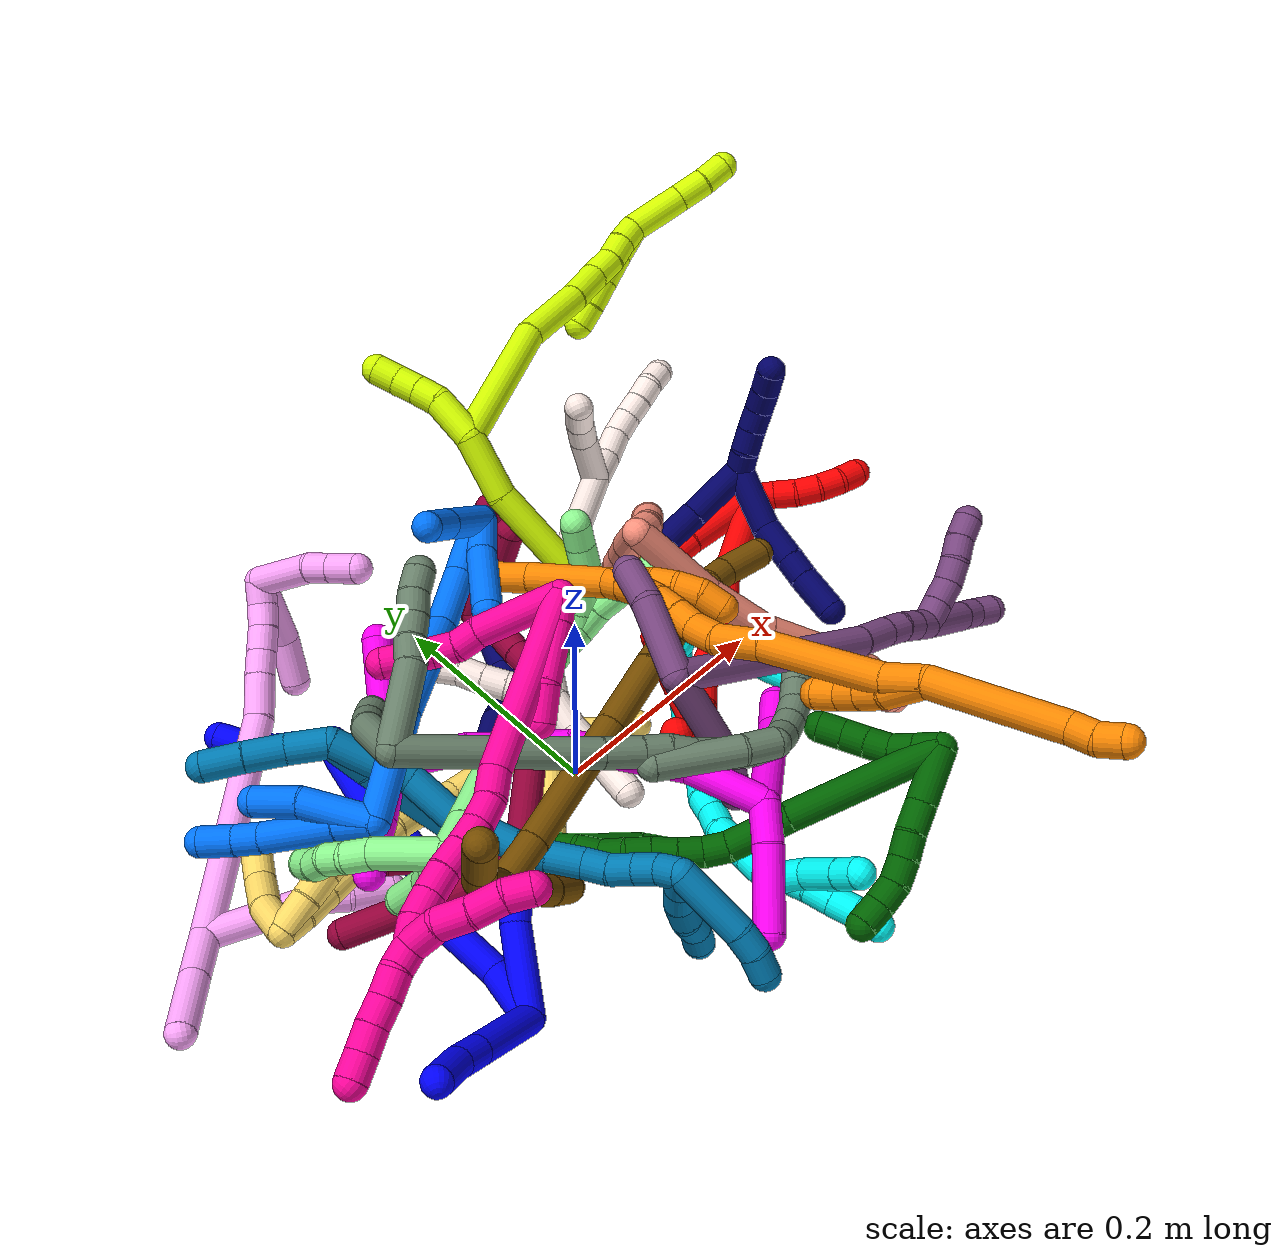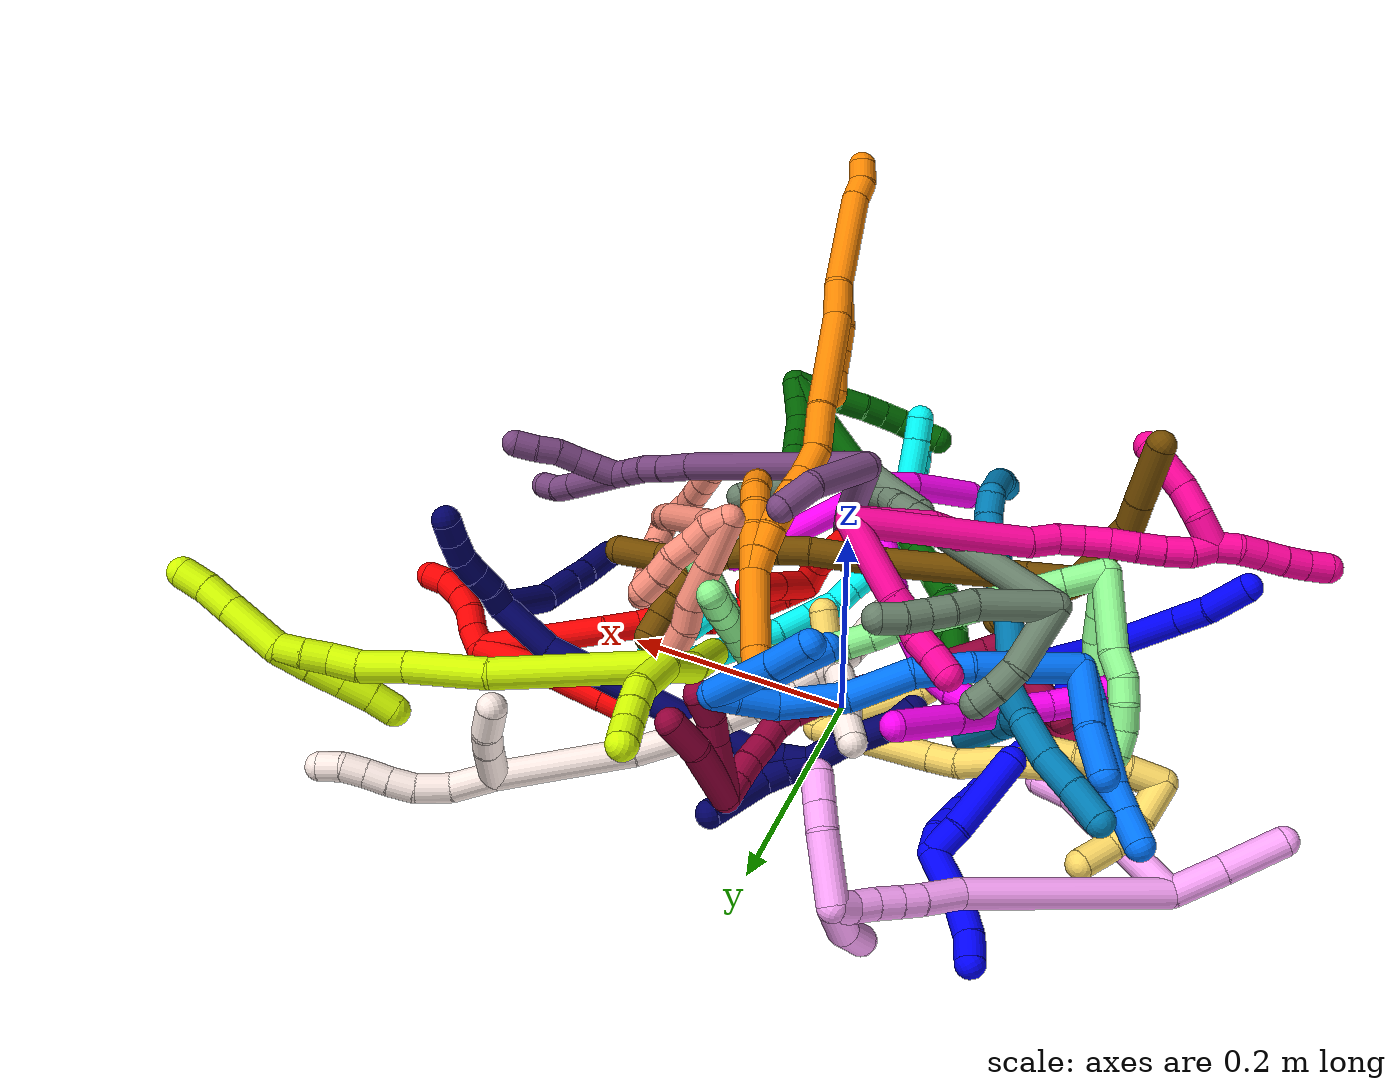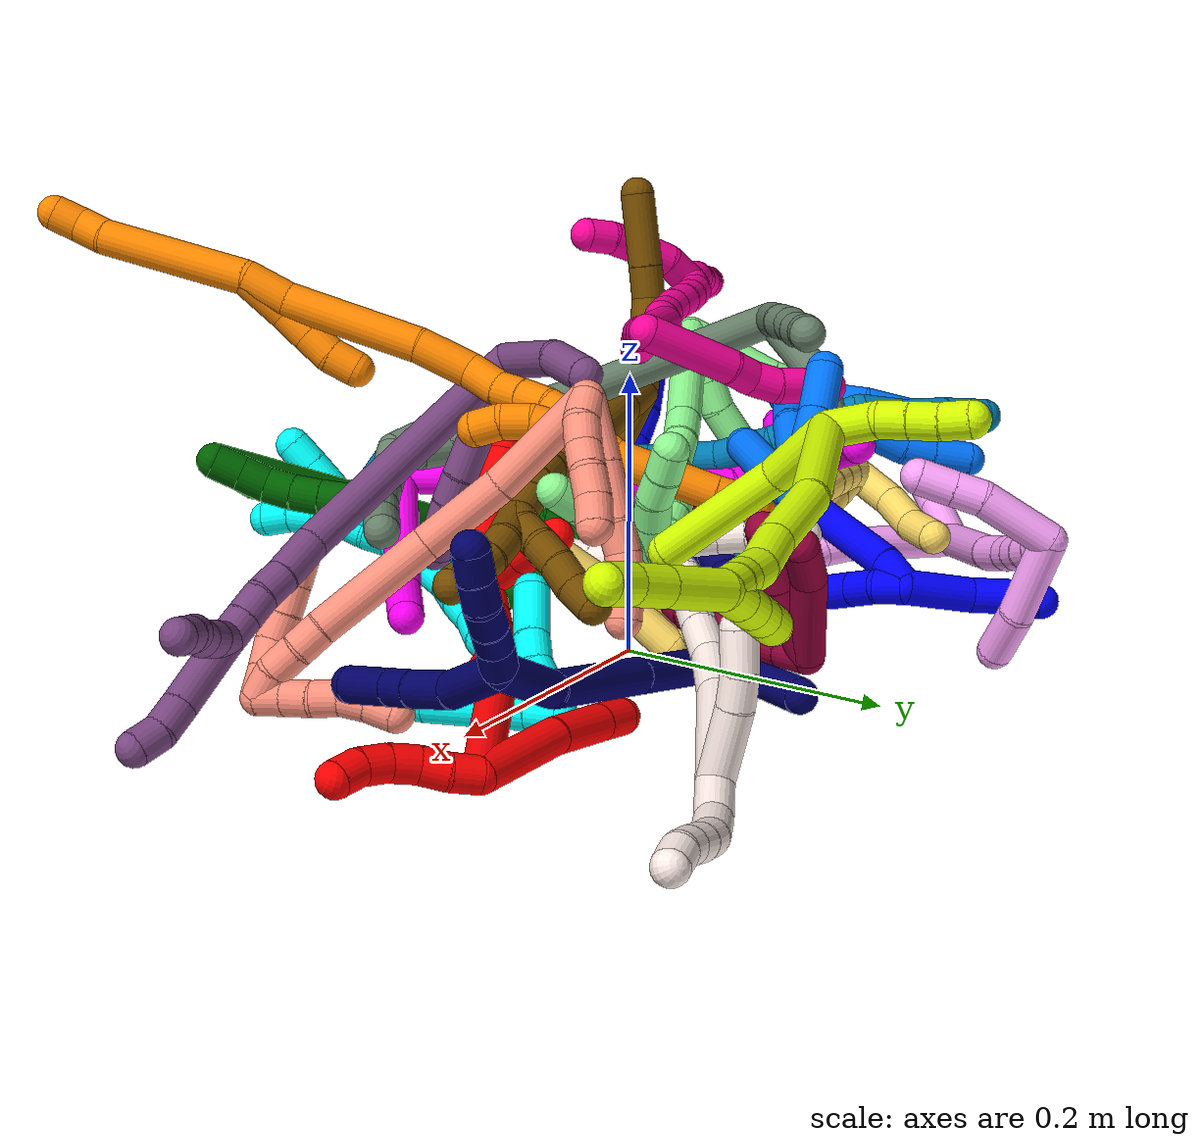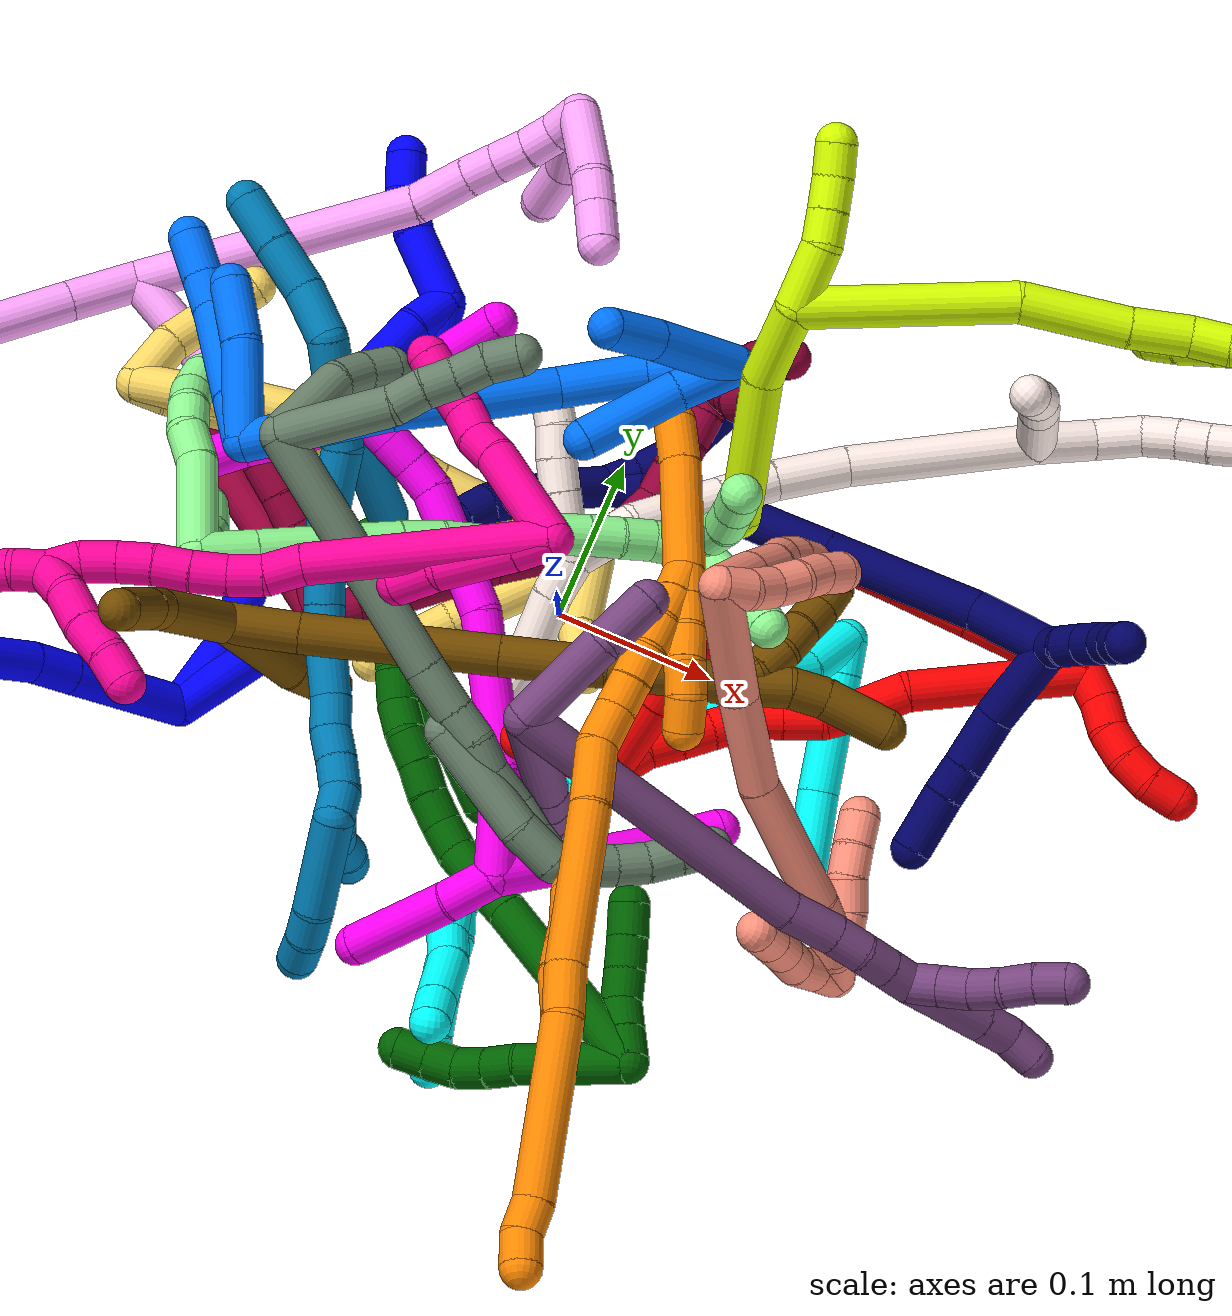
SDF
<sdf version="1.7">
 <world name="default">
  <plugin name="TubeGeneratorPlugin" filename="libtube_generator_plugin.so"/>
  <model name="photoneo_s_sensor">
   <static>1</static>
   <pose>0 0 2 1.57079 1.57079 3.14159</pose>
   <link name="link">
    <inertial><mass>0.1</mass></inertial>
    <sensor name="sensor" type="depth">
     <update_rate>30</update_rate>
     <camera>
      <horizontal_fov>1.22</horizontal_fov>
      <image><width>1920</width><height>1200</height><format>B8G8R8</format></image>
      <clip><near>0.1</near><far>4</far></clip>
      <depth_camera><output>points</output></depth_camera>
     </camera>
     <plugin name="camera_plugin" filename="libgazebo_ros_depth_camera.so">
      <baseline>0.2</baseline>
      <alwaysOn>1</alwaysOn>
      <updateRate>0.0</updateRate>
      <cameraName>camera_ir</cameraName>
      <imageTopicName>/camera/color/image_raw</imageTopicName>
      <cameraInfoTopicName>/camera/color/camera_info</cameraInfoTopicName>
      <depthImageTopicName>/camera/depth/image_raw</depthImageTopicName>
      <depthImageCameraInfoTopicName>/camera/depth/camera_info</depthImageCameraInfoTopicName>
      <pointCloudTopicName>/camera/depth/points</pointCloudTopicName>
      <frameName>fr_optical</frameName>
      <pointCloudCutoff>0.1</pointCloudCutoff>
      <pointCloudCutoffMax>2.0</pointCloudCutoffMax>
      <distortionK1>0</distortionK1>
      <distortionK2>0</distortionK2>
      <distortionK3>0</distortionK3>
      <distortionT1>0</distortionT1>
      <distortionT2>0</distortionT2>
      <CxPrime>0</CxPrime>
      <Cx>0</Cx>
      <Cy>0</Cy>
      <focalLength>0</focalLength>
      <hackBaseline>0</hackBaseline>
     </plugin>
    </sensor>
   </link>
  </model>
  <gravity>0 0 -9.8</gravity>
  <magnetic_field>6e-06 2.3e-05 -4.2e-05</magnetic_field>
  <atmosphere type="adiabatic"/>
  <physics name="default_physics" default="0" type="ode">
   <max_step_size>0.003</max_step_size>
   <real_time_factor>1</real_time_factor>
   <real_time_update_rate>1000</real_time_update_rate>
   <max_contacts>10000</max_contacts>
   <ode>
    <solver>
     <type>quick</type>
     <iters>100</iters>
     <sor>1.3</sor>
     <use_dynamic_moi_rescaling>0</use_dynamic_moi_rescaling>
    </solver>
    <constraints>
     <contact_max_correcting_vel>0</contact_max_correcting_vel>
     <contact_surface_layer>0.001</contact_surface_layer>
     <cfm>0</cfm>
     <erp>0.2</erp>
    </constraints>
   </ode>
  </physics>
  <scene><ambient>0.4 0.4 0.4 1</ambient><background>0.7 0.7 0.7 1</background><shadows>0</shadows></scene>
  <audio><device>default</device></audio>
  <spherical_coordinates>
   <surface_model>EARTH_WGS84</surface_model>
   <latitude_deg>0</latitude_deg>
   <longitude_deg>0</longitude_deg>
   <elevation>0</elevation>
   <heading_deg>0</heading_deg>
  </spherical_coordinates>
  <model name="bin">
   <static>1</static>
   <link name="bottom">
    <collision name="collision-bottom">
     <pose>0 0 -0.01 0 -0 0</pose>
     <geometry><box><size>0.8 0.6 0.02</size></box></geometry>
     <surface>
      <friction><ode><mu>100</mu><mu2>100</mu2></ode></friction>
      <contact><collide_bitmask>65535</collide_bitmask></contact>
     </surface>
    </collision>
   </link>
   <link name="west_wall">
    <collision name="collision-west_wall">
     <pose>-0.41 0 0.1 0 -0 0</pose>
     <geometry><box><size>0.02 0.6 0.2</size></box></geometry>
     <surface>
      <friction><ode><mu>100</mu><mu2>100</mu2></ode></friction>
      <contact><collide_bitmask>65535</collide_bitmask></contact>
     </surface>
    </collision>
   </link>
   <link name="east_wall">
    <collision name="collision-east_wall">
     <pose>0.41 0 0.1 0 -0 0</pose>
     <geometry><box><size>0.02 0.6 0.2</size></box></geometry>
     <surface>
      <friction><ode><mu>100</mu><mu2>100</mu2></ode></friction>
      <contact><collide_bitmask>65535</collide_bitmask></contact>
     </surface>
    </collision>
   </link>
   <link name="south_wall">
    <collision name="collision-south_wall">
     <pose>0 -0.31 0.1 0 -0 0</pose>
     <geometry><box><size>0.8 0.02 0.2</size></box></geometry>
     <surface>
      <friction><ode><mu>100</mu><mu2>100</mu2></ode></friction>
      <contact><collide_bitmask>65535</collide_bitmask></contact>
     </surface>
    </collision>
   </link>
   <link name="north_wall">
    <collision name="collision-north_wall">
     <pose>0 0.31 0.1 0 -0 0</pose>
     <geometry><box><size>0.8 0.02 0.2</size></box></geometry>
     <surface>
      <friction><ode><mu>100</mu><mu2>100</mu2></ode></friction>
      <contact><collide_bitmask>65535</collide_bitmask></contact>
     </surface>
    </collision>
   </link>
  </model>
  <model name="1">
   <static>0</static>
   <link name="1">
    <collision name="collision-cylinder-e_1_2_8">
     <pose>0.026741 0.017503 0.025152 -0.607958 0.71752 -0.234192</pose>
     <geometry><cylinder><radius>0.0125</radius><length>0.08134</length></cylinder></geometry>
     <surface>
      <friction><ode><mu>1.16</mu><mu2>1.16</mu2><slip1>0</slip1><slip2>0</slip2></ode></friction>
      <contact><ode><kp>1e+06</kp><kd>1</kd><max_vel>0</max_vel><min_depth>0.001</min_depth></ode></contact>
     </surface>
    </collision>
    <visual name="visual-cylinder-e_1_2_8">
     <pose>0.026741 0.017503 0.025152 -0.607958 0.71752 -0.234192</pose>
     <geometry><cylinder><radius>0.0125</radius><length>0.08134</length></cylinder></geometry>
     <material><ambient>0 0 1 1</ambient></material>
    </visual>
    <collision name="collision-cylinder-e_2_8_9">
     <pose>0.062789 0.041151 0.059022 -0.613988 0.717361 -0.236587</pose>
     <geometry><cylinder><radius>0.0125</radius><length>0.028312</length></cylinder></geometry>
     <surface>
      <friction><ode><mu>1.16</mu><mu2>1.16</mu2><slip1>0</slip1><slip2>0</slip2></ode></friction>
      <contact><ode><kp>1e+06</kp><kd>1</kd><max_vel>0</max_vel><min_depth>0.001</min_depth></ode></contact>
     </surface>
    </collision>
    <visual name="visual-cylinder-e_2_8_9">
     <pose>0.062789 0.041151 0.059022 -0.613988 0.717361 -0.236587</pose>
     <geometry><cylinder><radius>0.0125</radius><length>0.028312</length></cylinder></geometry>
     <material><ambient>0 0 1 1</ambient></material>
    </visual>
    <collision name="collision-cylinder-e_3_9_6">
     <pose>0.085612 0.053052 0.081566 -0.394484 0.734277 -0.153405</pose>
     <geometry><cylinder><radius>0.0125</radius><length>0.040348</length></cylinder></geometry>
     <surface>
      <friction><ode><mu>1.16</mu><mu2>1.16</mu2><slip1>0</slip1><slip2>0</slip2></ode></friction>
      <contact><ode><kp>1e+06</kp><kd>1</kd><max_vel>0</max_vel><min_depth>0.001</min_depth></ode></contact>
     </surface>
    </collision>
    <visual name="visual-cylinder-e_3_9_6">
     <pose>0.085612 0.053052 0.081566 -0.394484 0.734277 -0.153405</pose>
     <geometry><cylinder><radius>0.0125</radius><length>0.040348</length></cylinder></geometry>
     <material><ambient>0 0 1 1</ambient></material>
    </visual>
    <collision name="collision-cylinder-e_1_2_10">
     <pose>0.011971 -0.002866 -0.034893 3.05963 0.329464 2.65793</pose>
     <geometry><cylinder><radius>0.0125</radius><length>0.074002</length></cylinder></geometry>
     <surface>
      <friction><ode><mu>1.16</mu><mu2>1.16</mu2><slip1>0</slip1><slip2>0</slip2></ode></friction>
      <contact><ode><kp>1e+06</kp><kd>1</kd><max_vel>0</max_vel><min_depth>0.001</min_depth></ode></contact>
     </surface>
    </collision>
    <visual name="visual-cylinder-e_1_2_10">
     <pose>0.011971 -0.002866 -0.034893 3.05963 0.329464 2.65793</pose>
     <geometry><cylinder><radius>0.0125</radius><length>0.074002</length></cylinder></geometry>
     <material><ambient>0 0 1 1</ambient></material>
    </visual>
    <collision name="collision-cylinder-e_2_10_5">
     <pose>0.029551 -0.009164 -0.081 2.84465 0.44616 1.97579</pose>
     <geometry><cylinder><radius>0.0125</radius><length>0.025998</length></cylinder></geometry>
     <surface>
      <friction><ode><mu>1.16</mu><mu2>1.16</mu2><slip1>0</slip1><slip2>0</slip2></ode></friction>
      <contact><ode><kp>1e+06</kp><kd>1</kd><max_vel>0</max_vel><min_depth>0.001</min_depth></ode></contact>
     </surface>
    </collision>
    <visual name="visual-cylinder-e_2_10_5">
     <pose>0.029551 -0.009164 -0.081 2.84465 0.44616 1.97579</pose>
     <geometry><cylinder><radius>0.0125</radius><length>0.025998</length></cylinder></geometry>
     <material><ambient>0 0 1 1</ambient></material>
    </visual>
    <collision name="collision-cylinder-e_1_2_11">
     <pose>0.002065 0.009088 -0.023017 -2.76552 0.083266 -0.431043</pose>
     <geometry><cylinder><radius>0.0125</radius><length>0.049664</length></cylinder></geometry>
     <surface>
      <friction><ode><mu>1.16</mu><mu2>1.16</mu2><slip1>0</slip1><slip2>0</slip2></ode></friction>
      <contact><ode><kp>1e+06</kp><kd>1</kd><max_vel>0</max_vel><min_depth>0.001</min_depth></ode></contact>
     </surface>
    </collision>
    <visual name="visual-cylinder-e_1_2_11">
     <pose>0.002065 0.009088 -0.023017 -2.76552 0.083266 -0.431043</pose>
     <geometry><cylinder><radius>0.0125</radius><length>0.049664</length></cylinder></geometry>
     <material><ambient>0 0 1 1</ambient></material>
    </visual>
    <collision name="collision-cylinder-e_2_11_12">
     <pose>0.01145 0.032705 -0.066698 -2.52882 0.282022 -0.843582</pose>
     <geometry><cylinder><radius>0.0125</radius><length>0.052599</length></cylinder></geometry>
     <surface>
      <friction><ode><mu>1.16</mu><mu2>1.16</mu2><slip1>0</slip1><slip2>0</slip2></ode></friction>
      <contact><ode><kp>1e+06</kp><kd>1</kd><max_vel>0</max_vel><min_depth>0.001</min_depth></ode></contact>
     </surface>
    </collision>
    <visual name="visual-cylinder-e_2_11_12">
     <pose>0.01145 0.032705 -0.066698 -2.52882 0.282022 -0.843582</pose>
     <geometry><cylinder><radius>0.0125</radius><length>0.052599</length></cylinder></geometry>
     <material><ambient>0 0 1 1</ambient></material>
    </visual>
    <collision name="collision-cylinder-e_3_12_13">
     <pose>0.021475 0.051709 -0.10238 -2.85195 0.171019 -1.06273</pose>
     <geometry><cylinder><radius>0.0125</radius><length>0.031806</length></cylinder></geometry>
     <surface>
      <friction><ode><mu>1.16</mu><mu2>1.16</mu2><slip1>0</slip1><slip2>0</slip2></ode></friction>
      <contact><ode><kp>1e+06</kp><kd>1</kd><max_vel>0</max_vel><min_depth>0.001</min_depth></ode></contact>
     </surface>
    </collision>
    <visual name="visual-cylinder-e_3_12_13">
     <pose>0.021475 0.051709 -0.10238 -2.85195 0.171019 -1.06273</pose>
     <geometry><cylinder><radius>0.0125</radius><length>0.031806</length></cylinder></geometry>
     <material><ambient>0 0 1 1</ambient></material>
    </visual>
    <collision name="collision-cylinder-e_4_13_14">
     <pose>0.025243 0.06063 -0.142338 -2.9652 0.041884 -0.465151</pose>
     <geometry><cylinder><radius>0.0125</radius><length>0.050709</length></cylinder></geometry>
     <surface>
      <friction><ode><mu>1.16</mu><mu2>1.16</mu2><slip1>0</slip1><slip2>0</slip2></ode></friction>
      <contact><ode><kp>1e+06</kp><kd>1</kd><max_vel>0</max_vel><min_depth>0.001</min_depth></ode></contact>
     </surface>
    </collision>
    <visual name="visual-cylinder-e_4_13_14">
     <pose>0.025243 0.06063 -0.142338 -2.9652 0.041884 -0.465151</pose>
     <geometry><cylinder><radius>0.0125</radius><length>0.050709</length></cylinder></geometry>
     <material><ambient>0 0 1 1</ambient></material>
    </visual>
    <collision name="collision-cylinder-e_5_14_15">
     <pose>0.027813 0.068945 -0.178894 -2.82008 0.122595 -0.723662</pose>
     <geometry><cylinder><radius>0.0125</radius><length>0.024673</length></cylinder></geometry>
     <surface>
      <friction><ode><mu>1.16</mu><mu2>1.16</mu2><slip1>0</slip1><slip2>0</slip2></ode></friction>
      <contact><ode><kp>1e+06</kp><kd>1</kd><max_vel>0</max_vel><min_depth>0.001</min_depth></ode></contact>
     </surface>
    </collision>
    <visual name="visual-cylinder-e_5_14_15">
     <pose>0.027813 0.068945 -0.178894 -2.82008 0.122595 -0.723662</pose>
     <geometry><cylinder><radius>0.0125</radius><length>0.024673</length></cylinder></geometry>
     <material><ambient>0 0 1 1</ambient></material>
    </visual>
    <collision name="collision-cylinder-e_6_15_16">
     <pose>0.034573 0.076251 -0.201422 -2.83637 0.430297 -1.91501</pose>
     <geometry><cylinder><radius>0.0125</radius><length>0.025175</length></cylinder></geometry>
     <surface>
      <friction><ode><mu>1.16</mu><mu2>1.16</mu2><slip1>0</slip1><slip2>0</slip2></ode></friction>
      <contact><ode><kp>1e+06</kp><kd>1</kd><max_vel>0</max_vel><min_depth>0.001</min_depth></ode></contact>
     </surface>
    </collision>
    <visual name="visual-cylinder-e_6_15_16">
     <pose>0.034573 0.076251 -0.201422 -2.83637 0.430297 -1.91501</pose>
     <geometry><cylinder><radius>0.0125</radius><length>0.025175</length></cylinder></geometry>
     <material><ambient>0 0 1 1</ambient></material>
    </visual>
    <collision name="collision-cylinder-e_7_16_17">
     <pose>0.045055 0.083428 -0.221406 -2.75072 0.48974 -1.80163</pose>
     <geometry><cylinder><radius>0.0125</radius><length>0.022242</length></cylinder></geometry>
     <surface>
      <friction><ode><mu>1.16</mu><mu2>1.16</mu2><slip1>0</slip1><slip2>0</slip2></ode></friction>
      <contact><ode><kp>1e+06</kp><kd>1</kd><max_vel>0</max_vel><min_depth>0.001</min_depth></ode></contact>
     </surface>
    </collision>
    <visual name="visual-cylinder-e_7_16_17">
     <pose>0.045055 0.083428 -0.221406 -2.75072 0.48974 -1.80163</pose>
     <geometry><cylinder><radius>0.0125</radius><length>0.022242</length></cylinder></geometry>
     <material><ambient>0 0 1 1</ambient></material>
    </visual>
    <collision name="collision-cylinder-e_8_17_18">
     <pose>0.055236 0.09086 -0.239303 -2.74518 0.477526 -1.76184</pose>
     <geometry><cylinder><radius>0.0125</radius><length>0.02154</length></cylinder></geometry>
     <surface>
      <friction><ode><mu>1.16</mu><mu2>1.16</mu2><slip1>0</slip1><slip2>0</slip2></ode></friction>
      <contact><ode><kp>1e+06</kp><kd>1</kd><max_vel>0</max_vel><min_depth>0.001</min_depth></ode></contact>
     </surface>
    </collision>
    <visual name="visual-cylinder-e_8_17_18">
     <pose>0.055236 0.09086 -0.239303 -2.74518 0.477526 -1.76184</pose>
     <geometry><cylinder><radius>0.0125</radius><length>0.02154</length></cylinder></geometry>
     <material><ambient>0 0 1 1</ambient></material>
    </visual>
    <collision name="collision-cylinder-e_9_18_1">
     <pose>0.063587 0.101336 -0.255807 -2.4182 0.320542 -0.807607</pose>
     <geometry><cylinder><radius>0.0125</radius><length>0.021592</length></cylinder></geometry>
     <surface>
      <friction><ode><mu>1.16</mu><mu2>1.16</mu2><slip1>0</slip1><slip2>0</slip2></ode></friction>
      <contact><ode><kp>1e+06</kp><kd>1</kd><max_vel>0</max_vel><min_depth>0.001</min_depth></ode></contact>
     </surface>
    </collision>
    <visual name="visual-cylinder-e_9_18_1">
     <pose>0.063587 0.101336 -0.255807 -2.4182 0.320542 -0.807607</pose>
     <geometry><cylinder><radius>0.0125</radius><length>0.021592</length></cylinder></geometry>
     <material><ambient>0 0 1 1</ambient></material>
    </visual>
    <collision name="collision-cylinder-e_1_1_19">
     <pose>0.067179 0.13266 -0.267833 -1.74605 0.00765 -0.009124</pose>
     <geometry><cylinder><radius>0.0125</radius><length>0.04985</length></cylinder></geometry>
     <surface>
      <friction><ode><mu>1.16</mu><mu2>1.16</mu2><slip1>0</slip1><slip2>0</slip2></ode></friction>
      <contact><ode><kp>1e+06</kp><kd>1</kd><max_vel>0</max_vel><min_depth>0.001</min_depth></ode></contact>
     </surface>
    </collision>
    <visual name="visual-cylinder-e_1_1_19">
     <pose>0.067179 0.13266 -0.267833 -1.74605 0.00765 -0.009124</pose>
     <geometry><cylinder><radius>0.0125</radius><length>0.04985</length></cylinder></geometry>
     <material><ambient>0 0 1 1</ambient></material>
    </visual>
    <collision name="collision-cylinder-e_2_19_20">
     <pose>0.0696 0.169867 -0.277248 -1.95151 0.162046 -0.238784</pose>
     <geometry><cylinder><radius>0.0125</radius><length>0.027644</length></cylinder></geometry>
     <surface>
      <friction><ode><mu>1.16</mu><mu2>1.16</mu2><slip1>0</slip1><slip2>0</slip2></ode></friction>
      <contact><ode><kp>1e+06</kp><kd>1</kd><max_vel>0</max_vel><min_depth>0.001</min_depth></ode></contact>
     </surface>
    </collision>
    <visual name="visual-cylinder-e_2_19_20">
     <pose>0.0696 0.169867 -0.277248 -1.95151 0.162046 -0.238784</pose>
     <geometry><cylinder><radius>0.0125</radius><length>0.027644</length></cylinder></geometry>
     <material><ambient>0 0 1 1</ambient></material>
    </visual>
    <collision name="collision-cylinder-e_3_20_4">
     <pose>0.073232 0.191706 -0.288679 -2.17713 0.124862 -0.237722</pose>
     <geometry><cylinder><radius>0.0125</radius><length>0.022506</length></cylinder></geometry>
     <surface>
      <friction><ode><mu>1.16</mu><mu2>1.16</mu2><slip1>0</slip1><slip2>0</slip2></ode></friction>
      <contact><ode><kp>1e+06</kp><kd>1</kd><max_vel>0</max_vel><min_depth>0.001</min_depth></ode></contact>
     </surface>
    </collision>
    <visual name="visual-cylinder-e_3_20_4">
     <pose>0.073232 0.191706 -0.288679 -2.17713 0.124862 -0.237722</pose>
     <geometry><cylinder><radius>0.0125</radius><length>0.022506</length></cylinder></geometry>
     <material><ambient>0 0 1 1</ambient></material>
    </visual>
    <collision name="collision-cylinder-e_1_1_21">
     <pose>0.070868 0.105785 -0.250779 0.181542 0.291644 0.026734</pose>
     <geometry><cylinder><radius>0.0125</radius><length>0.026981</length></cylinder></geometry>
     <surface>
      <friction><ode><mu>1.16</mu><mu2>1.16</mu2><slip1>0</slip1><slip2>0</slip2></ode></friction>
      <contact><ode><kp>1e+06</kp><kd>1</kd><max_vel>0</max_vel><min_depth>0.001</min_depth></ode></contact>
     </surface>
    </collision>
    <visual name="visual-cylinder-e_1_1_21">
     <pose>0.070868 0.105785 -0.250779 0.181542 0.291644 0.026734</pose>
     <geometry><cylinder><radius>0.0125</radius><length>0.026981</length></cylinder></geometry>
     <material><ambient>0 0 1 1</ambient></material>
    </visual>
    <collision name="collision-cylinder-e_2_21_3">
     <pose>0.079261 0.092227 -0.203624 0.315026 0.12396 0.019713</pose>
     <geometry><cylinder><radius>0.0125</radius><length>0.073019</length></cylinder></geometry>
     <surface>
      <friction><ode><mu>1.16</mu><mu2>1.16</mu2><slip1>0</slip1><slip2>0</slip2></ode></friction>
      <contact><ode><kp>1e+06</kp><kd>1</kd><max_vel>0</max_vel><min_depth>0.001</min_depth></ode></contact>
     </surface>
    </collision>
    <visual name="visual-cylinder-e_2_21_3">
     <pose>0.079261 0.092227 -0.203624 0.315026 0.12396 0.019713</pose>
     <geometry><cylinder><radius>0.0125</radius><length>0.073019</length></cylinder></geometry>
     <material><ambient>0 0 1 1</ambient></material>
    </visual>
    <collision name="collision-sphere-3">
     <pose>0.083775 0.081002 -0.169177 0 -0 0</pose>
     <geometry><sphere><radius>0.0125</radius></sphere></geometry>
     <surface>
      <friction><ode><mu>1.16</mu><mu2>1.16</mu2><slip1>0</slip1><slip2>0</slip2></ode></friction>
      <contact><ode><kp>1e+06</kp><kd>1</kd><max_vel>0</max_vel><min_depth>0.001</min_depth></ode></contact>
     </surface>
    </collision>
    <visual name="visual-sphere-3">
     <pose>0.083775 0.081002 -0.169177 0 -0 0</pose>
     <geometry><sphere><radius>0.0125</radius></sphere></geometry>
     <material><ambient>0 0 1 1</ambient></material>
    </visual>
    <collision name="collision-sphere-21">
     <pose>0.074747 0.103452 -0.23807 0 -0 0</pose>
     <geometry><sphere><radius>0.0125</radius></sphere></geometry>
     <surface>
      <friction><ode><mu>1.16</mu><mu2>1.16</mu2><slip1>0</slip1><slip2>0</slip2></ode></friction>
      <contact><ode><kp>1e+06</kp><kd>1</kd><max_vel>0</max_vel><min_depth>0.001</min_depth></ode></contact>
     </surface>
    </collision>
    <visual name="visual-sphere-21">
     <pose>0.074747 0.103452 -0.23807 0 -0 0</pose>
     <geometry><sphere><radius>0.0125</radius></sphere></geometry>
     <material><ambient>0 0 1 1</ambient></material>
    </visual>
    <collision name="collision-sphere-4">
     <pose>0.074633 0.200882 -0.295042 0 -0 0</pose>
     <geometry><sphere><radius>0.0125</radius></sphere></geometry>
     <surface>
      <friction><ode><mu>1.16</mu><mu2>1.16</mu2><slip1>0</slip1><slip2>0</slip2></ode></friction>
      <contact><ode><kp>1e+06</kp><kd>1</kd><max_vel>0</max_vel><min_depth>0.001</min_depth></ode></contact>
     </surface>
    </collision>
    <visual name="visual-sphere-4">
     <pose>0.074633 0.200882 -0.295042 0 -0 0</pose>
     <geometry><sphere><radius>0.0125</radius></sphere></geometry>
     <material><ambient>0 0 1 1</ambient></material>
    </visual>
    <collision name="collision-sphere-20">
     <pose>0.07183 0.182531 -0.282316 0 -0 0</pose>
     <geometry><sphere><radius>0.0125</radius></sphere></geometry>
     <surface>
      <friction><ode><mu>1.16</mu><mu2>1.16</mu2><slip1>0</slip1><slip2>0</slip2></ode></friction>
      <contact><ode><kp>1e+06</kp><kd>1</kd><max_vel>0</max_vel><min_depth>0.001</min_depth></ode></contact>
     </surface>
    </collision>
    <visual name="visual-sphere-20">
     <pose>0.07183 0.182531 -0.282316 0 -0 0</pose>
     <geometry><sphere><radius>0.0125</radius></sphere></geometry>
     <material><ambient>0 0 1 1</ambient></material>
    </visual>
    <collision name="collision-sphere-5">
     <pose>0.035161 -0.012595 -0.092213 0 -0 0</pose>
     <geometry><sphere><radius>0.0125</radius></sphere></geometry>
     <surface>
      <friction><ode><mu>1.16</mu><mu2>1.16</mu2><slip1>0</slip1><slip2>0</slip2></ode></friction>
      <contact><ode><kp>1e+06</kp><kd>1</kd><max_vel>0</max_vel><min_depth>0.001</min_depth></ode></contact>
     </surface>
    </collision>
    <visual name="visual-sphere-5">
     <pose>0.035161 -0.012595 -0.092213 0 -0 0</pose>
     <geometry><sphere><radius>0.0125</radius></sphere></geometry>
     <material><ambient>0 0 1 1</ambient></material>
    </visual>
    <collision name="collision-sphere-10">
     <pose>0.023942 -0.005733 -0.069786 0 -0 0</pose>
     <geometry><sphere><radius>0.0125</radius></sphere></geometry>
     <surface>
      <friction><ode><mu>1.16</mu><mu2>1.16</mu2><slip1>0</slip1><slip2>0</slip2></ode></friction>
      <contact><ode><kp>1e+06</kp><kd>1</kd><max_vel>0</max_vel><min_depth>0.001</min_depth></ode></contact>
     </surface>
    </collision>
    <visual name="visual-sphere-10">
     <pose>0.023942 -0.005733 -0.069786 0 -0 0</pose>
     <geometry><sphere><radius>0.0125</radius></sphere></geometry>
     <material><ambient>0 0 1 1</ambient></material>
    </visual>
    <collision name="collision-sphere-6">
     <pose>0.09913 0.058808 0.095392 0 -0 0</pose>
     <geometry><sphere><radius>0.0125</radius></sphere></geometry>
     <surface>
      <friction><ode><mu>1.16</mu><mu2>1.16</mu2><slip1>0</slip1><slip2>0</slip2></ode></friction>
      <contact><ode><kp>1e+06</kp><kd>1</kd><max_vel>0</max_vel><min_depth>0.001</min_depth></ode></contact>
     </surface>
    </collision>
    <visual name="visual-sphere-6">
     <pose>0.09913 0.058808 0.095392 0 -0 0</pose>
     <geometry><sphere><radius>0.0125</radius></sphere></geometry>
     <material><ambient>0 0 1 1</ambient></material>
    </visual>
    <collision name="collision-sphere-9">
     <pose>0.072095 0.047297 0.067741 0 -0 0</pose>
     <geometry><sphere><radius>0.0125</radius></sphere></geometry>
     <surface>
      <friction><ode><mu>1.16</mu><mu2>1.16</mu2><slip1>0</slip1><slip2>0</slip2></ode></friction>
      <contact><ode><kp>1e+06</kp><kd>1</kd><max_vel>0</max_vel><min_depth>0.001</min_depth></ode></contact>
     </surface>
    </collision>
    <visual name="visual-sphere-9">
     <pose>0.072095 0.047297 0.067741 0 -0 0</pose>
     <geometry><sphere><radius>0.0125</radius></sphere></geometry>
     <material><ambient>0 0 1 1</ambient></material>
    </visual>
    <collision name="collision-sphere-2">
     <geometry><sphere><radius>0.0125</radius></sphere></geometry>
     <surface>
      <friction><ode><mu>1.16</mu><mu2>1.16</mu2><slip1>0</slip1><slip2>0</slip2></ode></friction>
      <contact><ode><kp>1e+06</kp><kd>1</kd><max_vel>0</max_vel><min_depth>0.001</min_depth></ode></contact>
     </surface>
    </collision>
    <visual name="visual-sphere-2">
     <geometry><sphere><radius>0.0125</radius></sphere></geometry>
     <material><ambient>0 0 1 1</ambient></material>
    </visual>
    <collision name="collision-sphere-19">
     <pose>0.06737 0.157203 -0.272179 0 -0 0</pose>
     <geometry><sphere><radius>0.0125</radius></sphere></geometry>
     <surface>
      <friction><ode><mu>1.16</mu><mu2>1.16</mu2><slip1>0</slip1><slip2>0</slip2></ode></friction>
      <contact><ode><kp>1e+06</kp><kd>1</kd><max_vel>0</max_vel><min_depth>0.001</min_depth></ode></contact>
     </surface>
    </collision>
    <visual name="visual-sphere-19">
     <pose>0.06737 0.157203 -0.272179 0 -0 0</pose>
     <geometry><sphere><radius>0.0125</radius></sphere></geometry>
     <material><ambient>0 0 1 1</ambient></material>
    </visual>
    <collision name="collision-sphere-8">
     <pose>0.053483 0.035006 0.050304 0 -0 0</pose>
     <geometry><sphere><radius>0.0125</radius></sphere></geometry>
     <surface>
      <friction><ode><mu>1.16</mu><mu2>1.16</mu2><slip1>0</slip1><slip2>0</slip2></ode></friction>
      <contact><ode><kp>1e+06</kp><kd>1</kd><max_vel>0</max_vel><min_depth>0.001</min_depth></ode></contact>
     </surface>
    </collision>
    <visual name="visual-sphere-8">
     <pose>0.053483 0.035006 0.050304 0 -0 0</pose>
     <geometry><sphere><radius>0.0125</radius></sphere></geometry>
     <material><ambient>0 0 1 1</ambient></material>
    </visual>
    <collision name="collision-sphere-11">
     <pose>0.004131 0.018177 -0.046033 0 -0 0</pose>
     <geometry><sphere><radius>0.0125</radius></sphere></geometry>
     <surface>
      <friction><ode><mu>1.16</mu><mu2>1.16</mu2><slip1>0</slip1><slip2>0</slip2></ode></friction>
      <contact><ode><kp>1e+06</kp><kd>1</kd><max_vel>0</max_vel><min_depth>0.001</min_depth></ode></contact>
     </surface>
    </collision>
    <visual name="visual-sphere-11">
     <pose>0.004131 0.018177 -0.046033 0 -0 0</pose>
     <geometry><sphere><radius>0.0125</radius></sphere></geometry>
     <material><ambient>0 0 1 1</ambient></material>
    </visual>
    <collision name="collision-sphere-12">
     <pose>0.018769 0.047233 -0.087362 0 -0 0</pose>
     <geometry><sphere><radius>0.0125</radius></sphere></geometry>
     <surface>
      <friction><ode><mu>1.16</mu><mu2>1.16</mu2><slip1>0</slip1><slip2>0</slip2></ode></friction>
      <contact><ode><kp>1e+06</kp><kd>1</kd><max_vel>0</max_vel><min_depth>0.001</min_depth></ode></contact>
     </surface>
    </collision>
    <visual name="visual-sphere-12">
     <pose>0.018769 0.047233 -0.087362 0 -0 0</pose>
     <geometry><sphere><radius>0.0125</radius></sphere></geometry>
     <material><ambient>0 0 1 1</ambient></material>
    </visual>
    <collision name="collision-sphere-13">
     <pose>0.024182 0.056185 -0.117399 0 -0 0</pose>
     <geometry><sphere><radius>0.0125</radius></sphere></geometry>
     <surface>
      <friction><ode><mu>1.16</mu><mu2>1.16</mu2><slip1>0</slip1><slip2>0</slip2></ode></friction>
      <contact><ode><kp>1e+06</kp><kd>1</kd><max_vel>0</max_vel><min_depth>0.001</min_depth></ode></contact>
     </surface>
    </collision>
    <visual name="visual-sphere-13">
     <pose>0.024182 0.056185 -0.117399 0 -0 0</pose>
     <geometry><sphere><radius>0.0125</radius></sphere></geometry>
     <material><ambient>0 0 1 1</ambient></material>
    </visual>
    <collision name="collision-sphere-14">
     <pose>0.026305 0.065076 -0.167278 0 -0 0</pose>
     <geometry><sphere><radius>0.0125</radius></sphere></geometry>
     <surface>
      <friction><ode><mu>1.16</mu><mu2>1.16</mu2><slip1>0</slip1><slip2>0</slip2></ode></friction>
      <contact><ode><kp>1e+06</kp><kd>1</kd><max_vel>0</max_vel><min_depth>0.001</min_depth></ode></contact>
     </surface>
    </collision>
    <visual name="visual-sphere-14">
     <pose>0.026305 0.065076 -0.167278 0 -0 0</pose>
     <geometry><sphere><radius>0.0125</radius></sphere></geometry>
     <material><ambient>0 0 1 1</ambient></material>
    </visual>
    <collision name="collision-sphere-15">
     <pose>0.029322 0.072814 -0.19051 0 -0 0</pose>
     <geometry><sphere><radius>0.0125</radius></sphere></geometry>
     <surface>
      <friction><ode><mu>1.16</mu><mu2>1.16</mu2><slip1>0</slip1><slip2>0</slip2></ode></friction>
      <contact><ode><kp>1e+06</kp><kd>1</kd><max_vel>0</max_vel><min_depth>0.001</min_depth></ode></contact>
     </surface>
    </collision>
    <visual name="visual-sphere-15">
     <pose>0.029322 0.072814 -0.19051 0 -0 0</pose>
     <geometry><sphere><radius>0.0125</radius></sphere></geometry>
     <material><ambient>0 0 1 1</ambient></material>
    </visual>
    <collision name="collision-sphere-16">
     <pose>0.039823 0.079689 -0.212333 0 -0 0</pose>
     <geometry><sphere><radius>0.0125</radius></sphere></geometry>
     <surface>
      <friction><ode><mu>1.16</mu><mu2>1.16</mu2><slip1>0</slip1><slip2>0</slip2></ode></friction>
      <contact><ode><kp>1e+06</kp><kd>1</kd><max_vel>0</max_vel><min_depth>0.001</min_depth></ode></contact>
     </surface>
    </collision>
    <visual name="visual-sphere-16">
     <pose>0.039823 0.079689 -0.212333 0 -0 0</pose>
     <geometry><sphere><radius>0.0125</radius></sphere></geometry>
     <material><ambient>0 0 1 1</ambient></material>
    </visual>
    <collision name="collision-sphere-17">
     <pose>0.050286 0.087167 -0.23048 0 -0 0</pose>
     <geometry><sphere><radius>0.0125</radius></sphere></geometry>
     <surface>
      <friction><ode><mu>1.16</mu><mu2>1.16</mu2><slip1>0</slip1><slip2>0</slip2></ode></friction>
      <contact><ode><kp>1e+06</kp><kd>1</kd><max_vel>0</max_vel><min_depth>0.001</min_depth></ode></contact>
     </surface>
    </collision>
    <visual name="visual-sphere-17">
     <pose>0.050286 0.087167 -0.23048 0 -0 0</pose>
     <geometry><sphere><radius>0.0125</radius></sphere></geometry>
     <material><ambient>0 0 1 1</ambient></material>
    </visual>
    <collision name="collision-sphere-18">
     <pose>0.060186 0.094554 -0.248127 0 -0 0</pose>
     <geometry><sphere><radius>0.0125</radius></sphere></geometry>
     <surface>
      <friction><ode><mu>1.16</mu><mu2>1.16</mu2><slip1>0</slip1><slip2>0</slip2></ode></friction>
      <contact><ode><kp>1e+06</kp><kd>1</kd><max_vel>0</max_vel><min_depth>0.001</min_depth></ode></contact>
     </surface>
    </collision>
    <visual name="visual-sphere-18">
     <pose>0.060186 0.094554 -0.248127 0 -0 0</pose>
     <geometry><sphere><radius>0.0125</radius></sphere></geometry>
     <material><ambient>0 0 1 1</ambient></material>
    </visual>
    <collision name="collision-sphere-1">
     <pose>0.066989 0.108118 -0.263487 0 -0 0</pose>
     <geometry><sphere><radius>0.0125</radius></sphere></geometry>
     <surface>
      <friction><ode><mu>1.16</mu><mu2>1.16</mu2><slip1>0</slip1><slip2>0</slip2></ode></friction>
      <contact><ode><kp>1e+06</kp><kd>1</kd><max_vel>0</max_vel><min_depth>0.001</min_depth></ode></contact>
     </surface>
    </collision>
    <visual name="visual-sphere-1">
     <pose>0.066989 0.108118 -0.263487 0 -0 0</pose>
     <geometry><sphere><radius>0.0125</radius></sphere></geometry>
     <material><ambient>0 0 1 1</ambient></material>
    </visual>
    <inertial>
     <pose>0.041962 0.061338 -0.116053 0 -0 0</pose>
     <mass>0.75</mass>
     <inertia>
      <ixx>9.4e-05</ixx>
      <ixy>0</ixy>
      <ixz>0</ixz>
      <iyy>8.2e-05</iyy>
      <iyz>0</iyz>
      <izz>-0.000127</izz>
     </inertia>
    </inertial>
   </link>
   <pose>-0.187569 -0.143422 0.016347 -1.09366 -1.35562 2.07885</pose>
  </model>
  <model name="2">
   <static>0</static>
   <link name="2">
    <collision name="collision-cylinder-e_1_2_8">
     <pose>-0.023614 -0.005495 -0.030131 2.96122 -0.656796 -2.62274</pose>
     <geometry><cylinder><radius>0.0125</radius><length>0.077349</length></cylinder></geometry>
     <surface>
      <friction><ode><mu>1.16</mu><mu2>1.16</mu2><slip1>0</slip1><slip2>0</slip2></ode></friction>
      <contact><ode><kp>1e+06</kp><kd>1</kd><max_vel>0</max_vel><min_depth>0.001</min_depth></ode></contact>
     </surface>
    </collision>
    <visual name="visual-cylinder-e_1_2_8">
     <pose>-0.023614 -0.005495 -0.030131 2.96122 -0.656796 -2.62274</pose>
     <geometry><cylinder><radius>0.0125</radius><length>0.077349</length></cylinder></geometry>
     <material><ambient>1 0 0 1</ambient></material>
    </visual>
    <collision name="collision-cylinder-e_2_8_9">
     <pose>-0.059513 -0.016392 -0.079952 2.87379 -0.541668 -2.23818</pose>
     <geometry><cylinder><radius>0.0125</radius><length>0.047656</length></cylinder></geometry>
     <surface>
      <friction><ode><mu>1.16</mu><mu2>1.16</mu2><slip1>0</slip1><slip2>0</slip2></ode></friction>
      <contact><ode><kp>1e+06</kp><kd>1</kd><max_vel>0</max_vel><min_depth>0.001</min_depth></ode></contact>
     </surface>
    </collision>
    <visual name="visual-cylinder-e_2_8_9">
     <pose>-0.059513 -0.016392 -0.079952 2.87379 -0.541668 -2.23818</pose>
     <geometry><cylinder><radius>0.0125</radius><length>0.047656</length></cylinder></geometry>
     <material><ambient>1 0 0 1</ambient></material>
    </visual>
    <collision name="collision-cylinder-e_3_9_6">
     <pose>-0.078136 -0.024926 -0.109947 2.84661 -0.531881 -2.14295</pose>
     <geometry><cylinder><radius>0.0125</radius><length>0.024996</length></cylinder></geometry>
     <surface>
      <friction><ode><mu>1.16</mu><mu2>1.16</mu2><slip1>0</slip1><slip2>0</slip2></ode></friction>
      <contact><ode><kp>1e+06</kp><kd>1</kd><max_vel>0</max_vel><min_depth>0.001</min_depth></ode></contact>
     </surface>
    </collision>
    <visual name="visual-cylinder-e_3_9_6">
     <pose>-0.078136 -0.024926 -0.109947 2.84661 -0.531881 -2.14295</pose>
     <geometry><cylinder><radius>0.0125</radius><length>0.024996</length></cylinder></geometry>
     <material><ambient>1 0 0 1</ambient></material>
    </visual>
    <collision name="collision-cylinder-e_1_2_10">
     <pose>0.000204 -0.001841 0.009827 0.185155 0.020434 0.001897</pose>
     <geometry><cylinder><radius>0.0125</radius><length>0.02</length></cylinder></geometry>
     <surface>
      <friction><ode><mu>1.16</mu><mu2>1.16</mu2><slip1>0</slip1><slip2>0</slip2></ode></friction>
      <contact><ode><kp>1e+06</kp><kd>1</kd><max_vel>0</max_vel><min_depth>0.001</min_depth></ode></contact>
     </surface>
    </collision>
    <visual name="visual-cylinder-e_1_2_10">
     <pose>0.000204 -0.001841 0.009827 0.185155 0.020434 0.001897</pose>
     <geometry><cylinder><radius>0.0125</radius><length>0.02</length></cylinder></geometry>
     <material><ambient>1 0 0 1</ambient></material>
    </visual>
    <collision name="collision-cylinder-e_2_10_11">
     <pose>-0.001303 -0.005932 0.029246 0.230441 -0.171982 -0.019953</pose>
     <geometry><cylinder><radius>0.0125</radius><length>0.02</length></cylinder></geometry>
     <surface>
      <friction><ode><mu>1.16</mu><mu2>1.16</mu2><slip1>0</slip1><slip2>0</slip2></ode></friction>
      <contact><ode><kp>1e+06</kp><kd>1</kd><max_vel>0</max_vel><min_depth>0.001</min_depth></ode></contact>
     </surface>
    </collision>
    <visual name="visual-cylinder-e_2_10_11">
     <pose>-0.001303 -0.005932 0.029246 0.230441 -0.171982 -0.019953</pose>
     <geometry><cylinder><radius>0.0125</radius><length>0.02</length></cylinder></geometry>
     <material><ambient>1 0 0 1</ambient></material>
    </visual>
    <collision name="collision-cylinder-e_3_11_12">
     <pose>-0.002114 -0.009442 0.048718 0.126811 0.090165 0.005729</pose>
     <geometry><cylinder><radius>0.0125</radius><length>0.02</length></cylinder></geometry>
     <surface>
      <friction><ode><mu>1.16</mu><mu2>1.16</mu2><slip1>0</slip1><slip2>0</slip2></ode></friction>
      <contact><ode><kp>1e+06</kp><kd>1</kd><max_vel>0</max_vel><min_depth>0.001</min_depth></ode></contact>
     </surface>
    </collision>
    <visual name="visual-cylinder-e_3_11_12">
     <pose>-0.002114 -0.009442 0.048718 0.126811 0.090165 0.005729</pose>
     <geometry><cylinder><radius>0.0125</radius><length>0.02</length></cylinder></geometry>
     <material><ambient>1 0 0 1</ambient></material>
    </visual>
    <collision name="collision-cylinder-e_4_12_13">
     <pose>0.00209 -0.011165 0.068024 0.049219 0.336625 0.008365</pose>
     <geometry><cylinder><radius>0.0125</radius><length>0.02</length></cylinder></geometry>
     <surface>
      <friction><ode><mu>1.16</mu><mu2>1.16</mu2><slip1>0</slip1><slip2>0</slip2></ode></friction>
      <contact><ode><kp>1e+06</kp><kd>1</kd><max_vel>0</max_vel><min_depth>0.001</min_depth></ode></contact>
     </surface>
    </collision>
    <visual name="visual-cylinder-e_4_12_13">
     <pose>0.00209 -0.011165 0.068024 0.049219 0.336625 0.008365</pose>
     <geometry><cylinder><radius>0.0125</radius><length>0.02</length></cylinder></geometry>
     <material><ambient>1 0 0 1</ambient></material>
    </visual>
    <collision name="collision-cylinder-e_5_13_5">
     <pose>0.011424 -0.011638 0.085428 0.000984 0.647378 0.00033</pose>
     <geometry><cylinder><radius>0.0125</radius><length>0.02</length></cylinder></geometry>
     <surface>
      <friction><ode><mu>1.16</mu><mu2>1.16</mu2><slip1>0</slip1><slip2>0</slip2></ode></friction>
      <contact><ode><kp>1e+06</kp><kd>1</kd><max_vel>0</max_vel><min_depth>0.001</min_depth></ode></contact>
     </surface>
    </collision>
    <visual name="visual-cylinder-e_5_13_5">
     <pose>0.011424 -0.011638 0.085428 0.000984 0.647378 0.00033</pose>
     <geometry><cylinder><radius>0.0125</radius><length>0.02</length></cylinder></geometry>
     <material><ambient>1 0 0 1</ambient></material>
    </visual>
    <collision name="collision-cylinder-e_1_2_14">
     <pose>-0.04566 -0.023397 -0.019312 2.26084 -0.984341 -1.69954</pose>
     <geometry><cylinder><radius>0.0125</radius><length>0.10964</length></cylinder></geometry>
     <surface>
      <friction><ode><mu>1.16</mu><mu2>1.16</mu2><slip1>0</slip1><slip2>0</slip2></ode></friction>
      <contact><ode><kp>1e+06</kp><kd>1</kd><max_vel>0</max_vel><min_depth>0.001</min_depth></ode></contact>
     </surface>
    </collision>
    <visual name="visual-cylinder-e_1_2_14">
     <pose>-0.04566 -0.023397 -0.019312 2.26084 -0.984341 -1.69954</pose>
     <geometry><cylinder><radius>0.0125</radius><length>0.10964</length></cylinder></geometry>
     <material><ambient>1 0 0 1</ambient></material>
    </visual>
    <collision name="collision-cylinder-e_2_14_15">
     <pose>-0.102364 -0.057728 -0.042105 1.87899 -0.766322 -1.00773</pose>
     <geometry><cylinder><radius>0.0125</radius><length>0.031851</length></cylinder></geometry>
     <surface>
      <friction><ode><mu>1.16</mu><mu2>1.16</mu2><slip1>0</slip1><slip2>0</slip2></ode></friction>
      <contact><ode><kp>1e+06</kp><kd>1</kd><max_vel>0</max_vel><min_depth>0.001</min_depth></ode></contact>
     </surface>
    </collision>
    <visual name="visual-cylinder-e_2_14_15">
     <pose>-0.102364 -0.057728 -0.042105 1.87899 -0.766322 -1.00773</pose>
     <geometry><cylinder><radius>0.0125</radius><length>0.031851</length></cylinder></geometry>
     <material><ambient>1 0 0 1</ambient></material>
    </visual>
    <collision name="collision-cylinder-e_3_15_16">
     <pose>-0.122477 -0.07432 -0.048014 1.97612 -0.974259 -1.35398</pose>
     <geometry><cylinder><radius>0.0125</radius><length>0.021925</length></cylinder></geometry>
     <surface>
      <friction><ode><mu>1.16</mu><mu2>1.16</mu2><slip1>0</slip1><slip2>0</slip2></ode></friction>
      <contact><ode><kp>1e+06</kp><kd>1</kd><max_vel>0</max_vel><min_depth>0.001</min_depth></ode></contact>
     </surface>
    </collision>
    <visual name="visual-cylinder-e_3_15_16">
     <pose>-0.122477 -0.07432 -0.048014 1.97612 -0.974259 -1.35398</pose>
     <geometry><cylinder><radius>0.0125</radius><length>0.021925</length></cylinder></geometry>
     <material><ambient>1 0 0 1</ambient></material>
    </visual>
    <collision name="collision-cylinder-e_4_16_17">
     <pose>-0.140353 -0.085314 -0.056483 2.41822 -0.829676 -1.72213</pose>
     <geometry><cylinder><radius>0.0125</radius><length>0.023874</length></cylinder></geometry>
     <surface>
      <friction><ode><mu>1.16</mu><mu2>1.16</mu2><slip1>0</slip1><slip2>0</slip2></ode></friction>
      <contact><ode><kp>1e+06</kp><kd>1</kd><max_vel>0</max_vel><min_depth>0.001</min_depth></ode></contact>
     </surface>
    </collision>
    <visual name="visual-cylinder-e_4_16_17">
     <pose>-0.140353 -0.085314 -0.056483 2.41822 -0.829676 -1.72213</pose>
     <geometry><cylinder><radius>0.0125</radius><length>0.023874</length></cylinder></geometry>
     <material><ambient>1 0 0 1</ambient></material>
    </visual>
    <collision name="collision-cylinder-e_5_17_18">
     <pose>-0.156905 -0.095378 -0.067707 2.40194 -0.834767 -1.70481</pose>
     <geometry><cylinder><radius>0.0125</radius><length>0.020903</length></cylinder></geometry>
     <surface>
      <friction><ode><mu>1.16</mu><mu2>1.16</mu2><slip1>0</slip1><slip2>0</slip2></ode></friction>
      <contact><ode><kp>1e+06</kp><kd>1</kd><max_vel>0</max_vel><min_depth>0.001</min_depth></ode></contact>
     </surface>
    </collision>
    <visual name="visual-cylinder-e_5_17_18">
     <pose>-0.156905 -0.095378 -0.067707 2.40194 -0.834767 -1.70481</pose>
     <geometry><cylinder><radius>0.0125</radius><length>0.020903</length></cylinder></geometry>
     <material><ambient>1 0 0 1</ambient></material>
    </visual>
    <collision name="collision-cylinder-e_6_18_19">
     <pose>-0.174939 -0.106177 -0.075015 1.90752 -1.01213 -1.32632</pose>
     <geometry><cylinder><radius>0.0125</radius><length>0.024267</length></cylinder></geometry>
     <surface>
      <friction><ode><mu>1.16</mu><mu2>1.16</mu2><slip1>0</slip1><slip2>0</slip2></ode></friction>
      <contact><ode><kp>1e+06</kp><kd>1</kd><max_vel>0</max_vel><min_depth>0.001</min_depth></ode></contact>
     </surface>
    </collision>
    <visual name="visual-cylinder-e_6_18_19">
     <pose>-0.174939 -0.106177 -0.075015 1.90752 -1.01213 -1.32632</pose>
     <geometry><cylinder><radius>0.0125</radius><length>0.024267</length></cylinder></geometry>
     <material><ambient>1 0 0 1</ambient></material>
    </visual>
    <collision name="collision-cylinder-e_7_19_20">
     <pose>-0.194695 -0.116873 -0.078501 1.85693 -1.09975 -1.37272</pose>
     <geometry><cylinder><radius>0.0125</radius><length>0.021248</length></cylinder></geometry>
     <surface>
      <friction><ode><mu>1.16</mu><mu2>1.16</mu2><slip1>0</slip1><slip2>0</slip2></ode></friction>
      <contact><ode><kp>1e+06</kp><kd>1</kd><max_vel>0</max_vel><min_depth>0.001</min_depth></ode></contact>
     </surface>
    </collision>
    <visual name="visual-cylinder-e_7_19_20">
     <pose>-0.194695 -0.116873 -0.078501 1.85693 -1.09975 -1.37272</pose>
     <geometry><cylinder><radius>0.0125</radius><length>0.021248</length></cylinder></geometry>
     <material><ambient>1 0 0 1</ambient></material>
    </visual>
    <collision name="collision-cylinder-e_8_20_21">
     <pose>-0.213567 -0.125652 -0.081261 1.89569 -1.13466 -1.45119</pose>
     <geometry><cylinder><radius>0.0125</radius><length>0.020754</length></cylinder></geometry>
     <surface>
      <friction><ode><mu>1.16</mu><mu2>1.16</mu2><slip1>0</slip1><slip2>0</slip2></ode></friction>
      <contact><ode><kp>1e+06</kp><kd>1</kd><max_vel>0</max_vel><min_depth>0.001</min_depth></ode></contact>
     </surface>
    </collision>
    <visual name="visual-cylinder-e_8_20_21">
     <pose>-0.213567 -0.125652 -0.081261 1.89569 -1.13466 -1.45119</pose>
     <geometry><cylinder><radius>0.0125</radius><length>0.020754</length></cylinder></geometry>
     <material><ambient>1 0 0 1</ambient></material>
    </visual>
    <collision name="collision-cylinder-e_9_21_1">
     <pose>-0.232506 -0.138299 -0.08244 1.5449 -0.84297 -0.8238</pose>
     <geometry><cylinder><radius>0.0125</radius><length>0.025539</length></cylinder></geometry>
     <surface>
      <friction><ode><mu>1.16</mu><mu2>1.16</mu2><slip1>0</slip1><slip2>0</slip2></ode></friction>
      <contact><ode><kp>1e+06</kp><kd>1</kd><max_vel>0</max_vel><min_depth>0.001</min_depth></ode></contact>
     </surface>
    </collision>
    <visual name="visual-cylinder-e_9_21_1">
     <pose>-0.232506 -0.138299 -0.08244 1.5449 -0.84297 -0.8238</pose>
     <geometry><cylinder><radius>0.0125</radius><length>0.025539</length></cylinder></geometry>
     <material><ambient>1 0 0 1</ambient></material>
    </visual>
    <collision name="collision-cylinder-e_1_1_22">
     <pose>-0.238665 -0.118224 -0.084817 -1.66144 0.117143 -0.128243</pose>
     <geometry><cylinder><radius>0.0125</radius><length>0.057765</length></cylinder></geometry>
     <surface>
      <friction><ode><mu>1.16</mu><mu2>1.16</mu2><slip1>0</slip1><slip2>0</slip2></ode></friction>
      <contact><ode><kp>1e+06</kp><kd>1</kd><max_vel>0</max_vel><min_depth>0.001</min_depth></ode></contact>
     </surface>
    </collision>
    <visual name="visual-cylinder-e_1_1_22">
     <pose>-0.238665 -0.118224 -0.084817 -1.66144 0.117143 -0.128243</pose>
     <geometry><cylinder><radius>0.0125</radius><length>0.057765</length></cylinder></geometry>
     <material><ambient>1 0 0 1</ambient></material>
    </visual>
    <collision name="collision-cylinder-e_2_22_4">
     <pose>-0.23189 -0.068896 -0.089244 -1.65875 0.161663 -0.176473</pose>
     <geometry><cylinder><radius>0.0125</radius><length>0.042235</length></cylinder></geometry>
     <surface>
      <friction><ode><mu>1.16</mu><mu2>1.16</mu2><slip1>0</slip1><slip2>0</slip2></ode></friction>
      <contact><ode><kp>1e+06</kp><kd>1</kd><max_vel>0</max_vel><min_depth>0.001</min_depth></ode></contact>
     </surface>
    </collision>
    <visual name="visual-cylinder-e_2_22_4">
     <pose>-0.23189 -0.068896 -0.089244 -1.65875 0.161663 -0.176473</pose>
     <geometry><cylinder><radius>0.0125</radius><length>0.042235</length></cylinder></geometry>
     <material><ambient>1 0 0 1</ambient></material>
    </visual>
    <collision name="collision-cylinder-e_1_1_23">
     <pose>-0.254071 -0.139166 -0.080326 -1.32732 -0.992266 0.800831</pose>
     <geometry><cylinder><radius>0.0125</radius><length>0.028737</length></cylinder></geometry>
     <surface>
      <friction><ode><mu>1.16</mu><mu2>1.16</mu2><slip1>0</slip1><slip2>0</slip2></ode></friction>
      <contact><ode><kp>1e+06</kp><kd>1</kd><max_vel>0</max_vel><min_depth>0.001</min_depth></ode></contact>
     </surface>
    </collision>
    <visual name="visual-cylinder-e_1_1_23">
     <pose>-0.254071 -0.139166 -0.080326 -1.32732 -0.992266 0.800831</pose>
     <geometry><cylinder><radius>0.0125</radius><length>0.028737</length></cylinder></geometry>
     <material><ambient>1 0 0 1</ambient></material>
    </visual>
    <collision name="collision-cylinder-e_2_23_3">
     <pose>-0.299077 -0.118639 -0.082403 -1.86935 -1.18223 1.4753</pose>
     <geometry><cylinder><radius>0.0125</radius><length>0.071263</length></cylinder></geometry>
     <surface>
      <friction><ode><mu>1.16</mu><mu2>1.16</mu2><slip1>0</slip1><slip2>0</slip2></ode></friction>
      <contact><ode><kp>1e+06</kp><kd>1</kd><max_vel>0</max_vel><min_depth>0.001</min_depth></ode></contact>
     </surface>
    </collision>
    <visual name="visual-cylinder-e_2_23_3">
     <pose>-0.299077 -0.118639 -0.082403 -1.86935 -1.18223 1.4753</pose>
     <geometry><cylinder><radius>0.0125</radius><length>0.071263</length></cylinder></geometry>
     <material><ambient>1 0 0 1</ambient></material>
    </visual>
    <collision name="collision-sphere-3">
     <pose>-0.332052 -0.105737 -0.086373 0 -0 0</pose>
     <geometry><sphere><radius>0.0125</radius></sphere></geometry>
     <surface>
      <friction><ode><mu>1.16</mu><mu2>1.16</mu2><slip1>0</slip1><slip2>0</slip2></ode></friction>
      <contact><ode><kp>1e+06</kp><kd>1</kd><max_vel>0</max_vel><min_depth>0.001</min_depth></ode></contact>
     </surface>
    </collision>
    <visual name="visual-sphere-3">
     <pose>-0.332052 -0.105737 -0.086373 0 -0 0</pose>
     <geometry><sphere><radius>0.0125</radius></sphere></geometry>
     <material><ambient>1 0 0 1</ambient></material>
    </visual>
    <collision name="collision-sphere-23">
     <pose>-0.266101 -0.131541 -0.078432 0 -0 0</pose>
     <geometry><sphere><radius>0.0125</radius></sphere></geometry>
     <surface>
      <friction><ode><mu>1.16</mu><mu2>1.16</mu2><slip1>0</slip1><slip2>0</slip2></ode></friction>
      <contact><ode><kp>1e+06</kp><kd>1</kd><max_vel>0</max_vel><min_depth>0.001</min_depth></ode></contact>
     </surface>
    </collision>
    <visual name="visual-sphere-23">
     <pose>-0.266101 -0.131541 -0.078432 0 -0 0</pose>
     <geometry><sphere><radius>0.0125</radius></sphere></geometry>
     <material><ambient>1 0 0 1</ambient></material>
    </visual>
    <collision name="collision-sphere-4">
     <pose>-0.228491 -0.048134 -0.091075 0 -0 0</pose>
     <geometry><sphere><radius>0.0125</radius></sphere></geometry>
     <surface>
      <friction><ode><mu>1.16</mu><mu2>1.16</mu2><slip1>0</slip1><slip2>0</slip2></ode></friction>
      <contact><ode><kp>1e+06</kp><kd>1</kd><max_vel>0</max_vel><min_depth>0.001</min_depth></ode></contact>
     </surface>
    </collision>
    <visual name="visual-sphere-4">
     <pose>-0.228491 -0.048134 -0.091075 0 -0 0</pose>
     <geometry><sphere><radius>0.0125</radius></sphere></geometry>
     <material><ambient>1 0 0 1</ambient></material>
    </visual>
    <collision name="collision-sphere-22">
     <pose>-0.235289 -0.089657 -0.087413 0 -0 0</pose>
     <geometry><sphere><radius>0.0125</radius></sphere></geometry>
     <surface>
      <friction><ode><mu>1.16</mu><mu2>1.16</mu2><slip1>0</slip1><slip2>0</slip2></ode></friction>
      <contact><ode><kp>1e+06</kp><kd>1</kd><max_vel>0</max_vel><min_depth>0.001</min_depth></ode></contact>
     </surface>
    </collision>
    <visual name="visual-sphere-22">
     <pose>-0.235289 -0.089657 -0.087413 0 -0 0</pose>
     <geometry><sphere><radius>0.0125</radius></sphere></geometry>
     <material><ambient>1 0 0 1</ambient></material>
    </visual>
    <collision name="collision-sphere-1">
     <pose>-0.242041 -0.146791 -0.08222 0 -0 0</pose>
     <geometry><sphere><radius>0.0125</radius></sphere></geometry>
     <surface>
      <friction><ode><mu>1.16</mu><mu2>1.16</mu2><slip1>0</slip1><slip2>0</slip2></ode></friction>
      <contact><ode><kp>1e+06</kp><kd>1</kd><max_vel>0</max_vel><min_depth>0.001</min_depth></ode></contact>
     </surface>
    </collision>
    <visual name="visual-sphere-1">
     <pose>-0.242041 -0.146791 -0.08222 0 -0 0</pose>
     <geometry><sphere><radius>0.0125</radius></sphere></geometry>
     <material><ambient>1 0 0 1</ambient></material>
    </visual>
    <collision name="collision-sphere-21">
     <pose>-0.222972 -0.129806 -0.08266 0 -0 0</pose>
     <geometry><sphere><radius>0.0125</radius></sphere></geometry>
     <surface>
      <friction><ode><mu>1.16</mu><mu2>1.16</mu2><slip1>0</slip1><slip2>0</slip2></ode></friction>
      <contact><ode><kp>1e+06</kp><kd>1</kd><max_vel>0</max_vel><min_depth>0.001</min_depth></ode></contact>
     </surface>
    </collision>
    <visual name="visual-sphere-21">
     <pose>-0.222972 -0.129806 -0.08266 0 -0 0</pose>
     <geometry><sphere><radius>0.0125</radius></sphere></geometry>
     <material><ambient>1 0 0 1</ambient></material>
    </visual>
    <collision name="collision-sphere-11">
     <pose>-0.003014 -0.008182 0.038838 0 -0 0</pose>
     <geometry><sphere><radius>0.0125</radius></sphere></geometry>
     <surface>
      <friction><ode><mu>1.16</mu><mu2>1.16</mu2><slip1>0</slip1><slip2>0</slip2></ode></friction>
      <contact><ode><kp>1e+06</kp><kd>1</kd><max_vel>0</max_vel><min_depth>0.001</min_depth></ode></contact>
     </surface>
    </collision>
    <visual name="visual-sphere-11">
     <pose>-0.003014 -0.008182 0.038838 0 -0 0</pose>
     <geometry><sphere><radius>0.0125</radius></sphere></geometry>
     <material><ambient>1 0 0 1</ambient></material>
    </visual>
    <collision name="collision-sphere-10">
     <pose>0.000409 -0.003681 0.019654 0 -0 0</pose>
     <geometry><sphere><radius>0.0125</radius></sphere></geometry>
     <surface>
      <friction><ode><mu>1.16</mu><mu2>1.16</mu2><slip1>0</slip1><slip2>0</slip2></ode></friction>
      <contact><ode><kp>1e+06</kp><kd>1</kd><max_vel>0</max_vel><min_depth>0.001</min_depth></ode></contact>
     </surface>
    </collision>
    <visual name="visual-sphere-10">
     <pose>0.000409 -0.003681 0.019654 0 -0 0</pose>
     <geometry><sphere><radius>0.0125</radius></sphere></geometry>
     <material><ambient>1 0 0 1</ambient></material>
    </visual>
    <collision name="collision-sphere-6">
     <pose>-0.084474 -0.028057 -0.120253 0 -0 0</pose>
     <geometry><sphere><radius>0.0125</radius></sphere></geometry>
     <surface>
      <friction><ode><mu>1.16</mu><mu2>1.16</mu2><slip1>0</slip1><slip2>0</slip2></ode></friction>
      <contact><ode><kp>1e+06</kp><kd>1</kd><max_vel>0</max_vel><min_depth>0.001</min_depth></ode></contact>
     </surface>
    </collision>
    <visual name="visual-sphere-6">
     <pose>-0.084474 -0.028057 -0.120253 0 -0 0</pose>
     <geometry><sphere><radius>0.0125</radius></sphere></geometry>
     <material><ambient>1 0 0 1</ambient></material>
    </visual>
    <collision name="collision-sphere-9">
     <pose>-0.071797 -0.021795 -0.099641 0 -0 0</pose>
     <geometry><sphere><radius>0.0125</radius></sphere></geometry>
     <surface>
      <friction><ode><mu>1.16</mu><mu2>1.16</mu2><slip1>0</slip1><slip2>0</slip2></ode></friction>
      <contact><ode><kp>1e+06</kp><kd>1</kd><max_vel>0</max_vel><min_depth>0.001</min_depth></ode></contact>
     </surface>
    </collision>
    <visual name="visual-sphere-9">
     <pose>-0.071797 -0.021795 -0.099641 0 -0 0</pose>
     <geometry><sphere><radius>0.0125</radius></sphere></geometry>
     <material><ambient>1 0 0 1</ambient></material>
    </visual>
    <collision name="collision-sphere-2">
     <geometry><sphere><radius>0.0125</radius></sphere></geometry>
     <surface>
      <friction><ode><mu>1.16</mu><mu2>1.16</mu2><slip1>0</slip1><slip2>0</slip2></ode></friction>
      <contact><ode><kp>1e+06</kp><kd>1</kd><max_vel>0</max_vel><min_depth>0.001</min_depth></ode></contact>
     </surface>
    </collision>
    <visual name="visual-sphere-2">
     <geometry><sphere><radius>0.0125</radius></sphere></geometry>
     <material><ambient>1 0 0 1</ambient></material>
    </visual>
    <collision name="collision-sphere-19">
     <pose>-0.185228 -0.112247 -0.07714 0 -0 0</pose>
     <geometry><sphere><radius>0.0125</radius></sphere></geometry>
     <surface>
      <friction><ode><mu>1.16</mu><mu2>1.16</mu2><slip1>0</slip1><slip2>0</slip2></ode></friction>
      <contact><ode><kp>1e+06</kp><kd>1</kd><max_vel>0</max_vel><min_depth>0.001</min_depth></ode></contact>
     </surface>
    </collision>
    <visual name="visual-sphere-19">
     <pose>-0.185228 -0.112247 -0.07714 0 -0 0</pose>
     <geometry><sphere><radius>0.0125</radius></sphere></geometry>
     <material><ambient>1 0 0 1</ambient></material>
    </visual>
    <collision name="collision-sphere-8">
     <pose>-0.047228 -0.010989 -0.060263 0 -0 0</pose>
     <geometry><sphere><radius>0.0125</radius></sphere></geometry>
     <surface>
      <friction><ode><mu>1.16</mu><mu2>1.16</mu2><slip1>0</slip1><slip2>0</slip2></ode></friction>
      <contact><ode><kp>1e+06</kp><kd>1</kd><max_vel>0</max_vel><min_depth>0.001</min_depth></ode></contact>
     </surface>
    </collision>
    <visual name="visual-sphere-8">
     <pose>-0.047228 -0.010989 -0.060263 0 -0 0</pose>
     <geometry><sphere><radius>0.0125</radius></sphere></geometry>
     <material><ambient>1 0 0 1</ambient></material>
    </visual>
    <collision name="collision-sphere-12">
     <pose>-0.001213 -0.010701 0.058597 0 -0 0</pose>
     <geometry><sphere><radius>0.0125</radius></sphere></geometry>
     <surface>
      <friction><ode><mu>1.16</mu><mu2>1.16</mu2><slip1>0</slip1><slip2>0</slip2></ode></friction>
      <contact><ode><kp>1e+06</kp><kd>1</kd><max_vel>0</max_vel><min_depth>0.001</min_depth></ode></contact>
     </surface>
    </collision>
    <visual name="visual-sphere-12">
     <pose>-0.001213 -0.010701 0.058597 0 -0 0</pose>
     <geometry><sphere><radius>0.0125</radius></sphere></geometry>
     <material><ambient>1 0 0 1</ambient></material>
    </visual>
    <collision name="collision-sphere-13">
     <pose>0.005393 -0.01163 0.077452 0 -0 0</pose>
     <geometry><sphere><radius>0.0125</radius></sphere></geometry>
     <surface>
      <friction><ode><mu>1.16</mu><mu2>1.16</mu2><slip1>0</slip1><slip2>0</slip2></ode></friction>
      <contact><ode><kp>1e+06</kp><kd>1</kd><max_vel>0</max_vel><min_depth>0.001</min_depth></ode></contact>
     </surface>
    </collision>
    <visual name="visual-sphere-13">
     <pose>0.005393 -0.01163 0.077452 0 -0 0</pose>
     <geometry><sphere><radius>0.0125</radius></sphere></geometry>
     <material><ambient>1 0 0 1</ambient></material>
    </visual>
    <collision name="collision-sphere-5">
     <pose>0.017455 -0.011646 0.093405 0 -0 0</pose>
     <geometry><sphere><radius>0.0125</radius></sphere></geometry>
     <surface>
      <friction><ode><mu>1.16</mu><mu2>1.16</mu2><slip1>0</slip1><slip2>0</slip2></ode></friction>
      <contact><ode><kp>1e+06</kp><kd>1</kd><max_vel>0</max_vel><min_depth>0.001</min_depth></ode></contact>
     </surface>
    </collision>
    <visual name="visual-sphere-5">
     <pose>0.017455 -0.011646 0.093405 0 -0 0</pose>
     <geometry><sphere><radius>0.0125</radius></sphere></geometry>
     <material><ambient>1 0 0 1</ambient></material>
    </visual>
    <collision name="collision-sphere-14">
     <pose>-0.09132 -0.046794 -0.038625 0 -0 0</pose>
     <geometry><sphere><radius>0.0125</radius></sphere></geometry>
     <surface>
      <friction><ode><mu>1.16</mu><mu2>1.16</mu2><slip1>0</slip1><slip2>0</slip2></ode></friction>
      <contact><ode><kp>1e+06</kp><kd>1</kd><max_vel>0</max_vel><min_depth>0.001</min_depth></ode></contact>
     </surface>
    </collision>
    <visual name="visual-sphere-14">
     <pose>-0.09132 -0.046794 -0.038625 0 -0 0</pose>
     <geometry><sphere><radius>0.0125</radius></sphere></geometry>
     <material><ambient>1 0 0 1</ambient></material>
    </visual>
    <collision name="collision-sphere-15">
     <pose>-0.113408 -0.068661 -0.045586 0 -0 0</pose>
     <geometry><sphere><radius>0.0125</radius></sphere></geometry>
     <surface>
      <friction><ode><mu>1.16</mu><mu2>1.16</mu2><slip1>0</slip1><slip2>0</slip2></ode></friction>
      <contact><ode><kp>1e+06</kp><kd>1</kd><max_vel>0</max_vel><min_depth>0.001</min_depth></ode></contact>
     </surface>
    </collision>
    <visual name="visual-sphere-15">
     <pose>-0.113408 -0.068661 -0.045586 0 -0 0</pose>
     <geometry><sphere><radius>0.0125</radius></sphere></geometry>
     <material><ambient>1 0 0 1</ambient></material>
    </visual>
    <collision name="collision-sphere-16">
     <pose>-0.131547 -0.07998 -0.050442 0 -0 0</pose>
     <geometry><sphere><radius>0.0125</radius></sphere></geometry>
     <surface>
      <friction><ode><mu>1.16</mu><mu2>1.16</mu2><slip1>0</slip1><slip2>0</slip2></ode></friction>
      <contact><ode><kp>1e+06</kp><kd>1</kd><max_vel>0</max_vel><min_depth>0.001</min_depth></ode></contact>
     </surface>
    </collision>
    <visual name="visual-sphere-16">
     <pose>-0.131547 -0.07998 -0.050442 0 -0 0</pose>
     <geometry><sphere><radius>0.0125</radius></sphere></geometry>
     <material><ambient>1 0 0 1</ambient></material>
    </visual>
    <collision name="collision-sphere-17">
     <pose>-0.149159 -0.090648 -0.062524 0 -0 0</pose>
     <geometry><sphere><radius>0.0125</radius></sphere></geometry>
     <surface>
      <friction><ode><mu>1.16</mu><mu2>1.16</mu2><slip1>0</slip1><slip2>0</slip2></ode></friction>
      <contact><ode><kp>1e+06</kp><kd>1</kd><max_vel>0</max_vel><min_depth>0.001</min_depth></ode></contact>
     </surface>
    </collision>
    <visual name="visual-sphere-17">
     <pose>-0.149159 -0.090648 -0.062524 0 -0 0</pose>
     <geometry><sphere><radius>0.0125</radius></sphere></geometry>
     <material><ambient>1 0 0 1</ambient></material>
    </visual>
    <collision name="collision-sphere-18">
     <pose>-0.164651 -0.100107 -0.07289 0 -0 0</pose>
     <geometry><sphere><radius>0.0125</radius></sphere></geometry>
     <surface>
      <friction><ode><mu>1.16</mu><mu2>1.16</mu2><slip1>0</slip1><slip2>0</slip2></ode></friction>
      <contact><ode><kp>1e+06</kp><kd>1</kd><max_vel>0</max_vel><min_depth>0.001</min_depth></ode></contact>
     </surface>
    </collision>
    <visual name="visual-sphere-18">
     <pose>-0.164651 -0.100107 -0.07289 0 -0 0</pose>
     <geometry><sphere><radius>0.0125</radius></sphere></geometry>
     <material><ambient>1 0 0 1</ambient></material>
    </visual>
    <collision name="collision-sphere-20">
     <pose>-0.204161 -0.121498 -0.079862 0 -0 0</pose>
     <geometry><sphere><radius>0.0125</radius></sphere></geometry>
     <surface>
      <friction><ode><mu>1.16</mu><mu2>1.16</mu2><slip1>0</slip1><slip2>0</slip2></ode></friction>
      <contact><ode><kp>1e+06</kp><kd>1</kd><max_vel>0</max_vel><min_depth>0.001</min_depth></ode></contact>
     </surface>
    </collision>
    <visual name="visual-sphere-20">
     <pose>-0.204161 -0.121498 -0.079862 0 -0 0</pose>
     <geometry><sphere><radius>0.0125</radius></sphere></geometry>
     <material><ambient>1 0 0 1</ambient></material>
    </visual>
    <inertial>
     <pose>-0.126585 -0.061448 -0.047291 0 -0 0</pose>
     <mass>0.75</mass>
     <inertia>
      <ixx>-0.000123</ixx>
      <ixy>0</ixy>
      <ixz>0</ixz>
      <iyy>8.4e-05</iyy>
      <iyz>0</iyz>
      <izz>0.000188</izz>
     </inertia>
    </inertial>
   </link>
   <pose>0.308579 0.088947 0.029206 1.11972 0.678844 0.651851</pose>
  </model>
  <model name="3">
   <static>0</static>
   <link name="3">
    <collision name="collision-cylinder-e_1_2_8">
     <pose>-0.000179 0.002994 0.010444 -0.279227 -0.016436 0.00231</pose>
     <geometry><cylinder><radius>0.0125</radius><length>0.021732</length></cylinder></geometry>
     <surface>
      <friction><ode><mu>1.16</mu><mu2>1.16</mu2><slip1>0</slip1><slip2>0</slip2></ode></friction>
      <contact><ode><kp>1e+06</kp><kd>1</kd><max_vel>0</max_vel><min_depth>0.001</min_depth></ode></contact>
     </surface>
    </collision>
    <visual name="visual-cylinder-e_1_2_8">
     <pose>-0.000179 0.002994 0.010444 -0.279227 -0.016436 0.00231</pose>
     <geometry><cylinder><radius>0.0125</radius><length>0.021732</length></cylinder></geometry>
     <material><ambient>0.003922 1 0.996078 1</ambient></material>
    </visual>
    <collision name="collision-cylinder-e_2_8_9">
     <pose>-0.001344 0.01535 0.056258 -0.258739 -0.026975 0.00351</pose>
     <geometry><cylinder><radius>0.0125</radius><length>0.073203</length></cylinder></geometry>
     <surface>
      <friction><ode><mu>1.16</mu><mu2>1.16</mu2><slip1>0</slip1><slip2>0</slip2></ode></friction>
      <contact><ode><kp>1e+06</kp><kd>1</kd><max_vel>0</max_vel><min_depth>0.001</min_depth></ode></contact>
     </surface>
    </collision>
    <visual name="visual-cylinder-e_2_8_9">
     <pose>-0.001344 0.01535 0.056258 -0.258739 -0.026975 0.00351</pose>
     <geometry><cylinder><radius>0.0125</radius><length>0.073203</length></cylinder></geometry>
     <material><ambient>0.003922 1 0.996078 1</ambient></material>
    </visual>
    <collision name="collision-cylinder-e_3_9_6">
     <pose>-0.002087 0.033938 0.117567 -0.341724 0.008894 -0.001535</pose>
     <geometry><cylinder><radius>0.0125</radius><length>0.055065</length></cylinder></geometry>
     <surface>
      <friction><ode><mu>1.16</mu><mu2>1.16</mu2><slip1>0</slip1><slip2>0</slip2></ode></friction>
      <contact><ode><kp>1e+06</kp><kd>1</kd><max_vel>0</max_vel><min_depth>0.001</min_depth></ode></contact>
     </surface>
    </collision>
    <visual name="visual-cylinder-e_3_9_6">
     <pose>-0.002087 0.033938 0.117567 -0.341724 0.008894 -0.001535</pose>
     <geometry><cylinder><radius>0.0125</radius><length>0.055065</length></cylinder></geometry>
     <material><ambient>0.003922 1 0.996078 1</ambient></material>
    </visual>
    <collision name="collision-cylinder-e_1_2_10">
     <pose>-0.010022 0.015885 0.008011 -1.10369 -0.513 0.320179</pose>
     <geometry><cylinder><radius>0.0125</radius><length>0.040839</length></cylinder></geometry>
     <surface>
      <friction><ode><mu>1.16</mu><mu2>1.16</mu2><slip1>0</slip1><slip2>0</slip2></ode></friction>
      <contact><ode><kp>1e+06</kp><kd>1</kd><max_vel>0</max_vel><min_depth>0.001</min_depth></ode></contact>
     </surface>
    </collision>
    <visual name="visual-cylinder-e_1_2_10">
     <pose>-0.010022 0.015885 0.008011 -1.10369 -0.513 0.320179</pose>
     <geometry><cylinder><radius>0.0125</radius><length>0.040839</length></cylinder></geometry>
     <material><ambient>0.003922 1 0.996078 1</ambient></material>
    </visual>
    <collision name="collision-cylinder-e_2_10_11">
     <pose>-0.027335 0.039462 0.017554 -1.37431 -0.748997 0.623979</pose>
     <geometry><cylinder><radius>0.0125</radius><length>0.021416</length></cylinder></geometry>
     <surface>
      <friction><ode><mu>1.16</mu><mu2>1.16</mu2><slip1>0</slip1><slip2>0</slip2></ode></friction>
      <contact><ode><kp>1e+06</kp><kd>1</kd><max_vel>0</max_vel><min_depth>0.001</min_depth></ode></contact>
     </surface>
    </collision>
    <visual name="visual-cylinder-e_2_10_11">
     <pose>-0.027335 0.039462 0.017554 -1.37431 -0.748997 0.623979</pose>
     <geometry><cylinder><radius>0.0125</radius><length>0.021416</length></cylinder></geometry>
     <material><ambient>0.003922 1 0.996078 1</ambient></material>
    </visual>
    <collision name="collision-cylinder-e_3_11_5">
     <pose>-0.048393 0.059997 0.020375 -1.47069 -0.817597 0.746958</pose>
     <geometry><cylinder><radius>0.0125</radius><length>0.037745</length></cylinder></geometry>
     <surface>
      <friction><ode><mu>1.16</mu><mu2>1.16</mu2><slip1>0</slip1><slip2>0</slip2></ode></friction>
      <contact><ode><kp>1e+06</kp><kd>1</kd><max_vel>0</max_vel><min_depth>0.001</min_depth></ode></contact>
     </surface>
    </collision>
    <visual name="visual-cylinder-e_3_11_5">
     <pose>-0.048393 0.059997 0.020375 -1.47069 -0.817597 0.746958</pose>
     <geometry><cylinder><radius>0.0125</radius><length>0.037745</length></cylinder></geometry>
     <material><ambient>0.003922 1 0.996078 1</ambient></material>
    </visual>
    <collision name="collision-cylinder-e_1_2_12">
     <pose>-0.053151 0.012452 0.03866 -0.31159 -0.91829 0.154993</pose>
     <geometry><cylinder><radius>0.0125</radius><length>0.133785</length></cylinder></geometry>
     <surface>
      <friction><ode><mu>1.16</mu><mu2>1.16</mu2><slip1>0</slip1><slip2>0</slip2></ode></friction>
      <contact><ode><kp>1e+06</kp><kd>1</kd><max_vel>0</max_vel><min_depth>0.001</min_depth></ode></contact>
     </surface>
    </collision>
    <visual name="visual-cylinder-e_1_2_12">
     <pose>-0.053151 0.012452 0.03866 -0.31159 -0.91829 0.154993</pose>
     <geometry><cylinder><radius>0.0125</radius><length>0.133785</length></cylinder></geometry>
     <material><ambient>0.003922 1 0.996078 1</ambient></material>
    </visual>
    <collision name="collision-cylinder-e_2_12_13">
     <pose>-0.118083 0.029416 0.088004 -0.399629 -0.793298 0.169243</pose>
     <geometry><cylinder><radius>0.0125</radius><length>0.033064</length></cylinder></geometry>
     <surface>
      <friction><ode><mu>1.16</mu><mu2>1.16</mu2><slip1>0</slip1><slip2>0</slip2></ode></friction>
      <contact><ode><kp>1e+06</kp><kd>1</kd><max_vel>0</max_vel><min_depth>0.001</min_depth></ode></contact>
     </surface>
    </collision>
    <visual name="visual-cylinder-e_2_12_13">
     <pose>-0.118083 0.029416 0.088004 -0.399629 -0.793298 0.169243</pose>
     <geometry><cylinder><radius>0.0125</radius><length>0.033064</length></cylinder></geometry>
     <material><ambient>0.003922 1 0.996078 1</ambient></material>
    </visual>
    <collision name="collision-cylinder-e_3_13_14">
     <pose>-0.140885 0.039428 0.10488 -0.726287 -0.926275 0.375052</pose>
     <geometry><cylinder><radius>0.0125</radius><length>0.027572</length></cylinder></geometry>
     <surface>
      <friction><ode><mu>1.16</mu><mu2>1.16</mu2><slip1>0</slip1><slip2>0</slip2></ode></friction>
      <contact><ode><kp>1e+06</kp><kd>1</kd><max_vel>0</max_vel><min_depth>0.001</min_depth></ode></contact>
     </surface>
    </collision>
    <visual name="visual-cylinder-e_3_13_14">
     <pose>-0.140885 0.039428 0.10488 -0.726287 -0.926275 0.375052</pose>
     <geometry><cylinder><radius>0.0125</radius><length>0.027572</length></cylinder></geometry>
     <material><ambient>0.003922 1 0.996078 1</ambient></material>
    </visual>
    <collision name="collision-cylinder-e_4_14_15">
     <pose>-0.157861 0.050612 0.117468 -0.726492 -0.608072 0.23741</pose>
     <geometry><cylinder><radius>0.0125</radius><length>0.020849</length></cylinder></geometry>
     <surface>
      <friction><ode><mu>1.16</mu><mu2>1.16</mu2><slip1>0</slip1><slip2>0</slip2></ode></friction>
      <contact><ode><kp>1e+06</kp><kd>1</kd><max_vel>0</max_vel><min_depth>0.001</min_depth></ode></contact>
     </surface>
    </collision>
    <visual name="visual-cylinder-e_4_14_15">
     <pose>-0.157861 0.050612 0.117468 -0.726492 -0.608072 0.23741</pose>
     <geometry><cylinder><radius>0.0125</radius><length>0.020849</length></cylinder></geometry>
     <material><ambient>0.003922 1 0.996078 1</ambient></material>
    </visual>
    <collision name="collision-cylinder-e_5_15_16">
     <pose>-0.171133 0.062599 0.129687 -0.824962 -0.706016 0.319697</pose>
     <geometry><cylinder><radius>0.0125</radius><length>0.022555</length></cylinder></geometry>
     <surface>
      <friction><ode><mu>1.16</mu><mu2>1.16</mu2><slip1>0</slip1><slip2>0</slip2></ode></friction>
      <contact><ode><kp>1e+06</kp><kd>1</kd><max_vel>0</max_vel><min_depth>0.001</min_depth></ode></contact>
     </surface>
    </collision>
    <visual name="visual-cylinder-e_5_15_16">
     <pose>-0.171133 0.062599 0.129687 -0.824962 -0.706016 0.319697</pose>
     <geometry><cylinder><radius>0.0125</radius><length>0.022555</length></cylinder></geometry>
     <material><ambient>0.003922 1 0.996078 1</ambient></material>
    </visual>
    <collision name="collision-cylinder-e_6_16_17">
     <pose>-0.182861 0.075364 0.143044 -0.70899 -0.418173 0.156752</pose>
     <geometry><cylinder><radius>0.0125</radius><length>0.021722</length></cylinder></geometry>
     <surface>
      <friction><ode><mu>1.16</mu><mu2>1.16</mu2><slip1>0</slip1><slip2>0</slip2></ode></friction>
      <contact><ode><kp>1e+06</kp><kd>1</kd><max_vel>0</max_vel><min_depth>0.001</min_depth></ode></contact>
     </surface>
    </collision>
    <visual name="visual-cylinder-e_6_16_17">
     <pose>-0.182861 0.075364 0.143044 -0.70899 -0.418173 0.156752</pose>
     <geometry><cylinder><radius>0.0125</radius><length>0.021722</length></cylinder></geometry>
     <material><ambient>0.003922 1 0.996078 1</ambient></material>
    </visual>
    <collision name="collision-cylinder-e_7_17_18">
     <pose>-0.191412 0.086786 0.158332 -0.569082 -0.422721 0.125347</pose>
     <geometry><cylinder><radius>0.0125</radius><length>0.020187</length></cylinder></geometry>
     <surface>
      <friction><ode><mu>1.16</mu><mu2>1.16</mu2><slip1>0</slip1><slip2>0</slip2></ode></friction>
      <contact><ode><kp>1e+06</kp><kd>1</kd><max_vel>0</max_vel><min_depth>0.001</min_depth></ode></contact>
     </surface>
    </collision>
    <visual name="visual-cylinder-e_7_17_18">
     <pose>-0.191412 0.086786 0.158332 -0.569082 -0.422721 0.125347</pose>
     <geometry><cylinder><radius>0.0125</radius><length>0.020187</length></cylinder></geometry>
     <material><ambient>0.003922 1 0.996078 1</ambient></material>
    </visual>
    <collision name="collision-cylinder-e_8_18_1">
     <pose>-0.199652 0.09794 0.172979 -0.731986 -0.41646 0.161608</pose>
     <geometry><cylinder><radius>0.0125</radius><length>0.020266</length></cylinder></geometry>
     <surface>
      <friction><ode><mu>1.16</mu><mu2>1.16</mu2><slip1>0</slip1><slip2>0</slip2></ode></friction>
      <contact><ode><kp>1e+06</kp><kd>1</kd><max_vel>0</max_vel><min_depth>0.001</min_depth></ode></contact>
     </surface>
    </collision>
    <visual name="visual-cylinder-e_8_18_1">
     <pose>-0.199652 0.09794 0.172979 -0.731986 -0.41646 0.161608</pose>
     <geometry><cylinder><radius>0.0125</radius><length>0.020266</length></cylinder></geometry>
     <material><ambient>0.003922 1 0.996078 1</ambient></material>
    </visual>
    <collision name="collision-cylinder-e_1_1_19">
     <pose>-0.204157 0.112344 0.186902 -0.862647 -0.037612 0.017312</pose>
     <geometry><cylinder><radius>0.0125</radius><length>0.021634</length></cylinder></geometry>
     <surface>
      <friction><ode><mu>1.16</mu><mu2>1.16</mu2><slip1>0</slip1><slip2>0</slip2></ode></friction>
      <contact><ode><kp>1e+06</kp><kd>1</kd><max_vel>0</max_vel><min_depth>0.001</min_depth></ode></contact>
     </surface>
    </collision>
    <visual name="visual-cylinder-e_1_1_19">
     <pose>-0.204157 0.112344 0.186902 -0.862647 -0.037612 0.017312</pose>
     <geometry><cylinder><radius>0.0125</radius><length>0.021634</length></cylinder></geometry>
     <material><ambient>0.003922 1 0.996078 1</ambient></material>
    </visual>
    <collision name="collision-cylinder-e_2_19_20">
     <pose>-0.20249 0.129272 0.19962 -0.992757 0.196727 -0.106793</pose>
     <geometry><cylinder><radius>0.0125</radius><length>0.021227</length></cylinder></geometry>
     <surface>
      <friction><ode><mu>1.16</mu><mu2>1.16</mu2><slip1>0</slip1><slip2>0</slip2></ode></friction>
      <contact><ode><kp>1e+06</kp><kd>1</kd><max_vel>0</max_vel><min_depth>0.001</min_depth></ode></contact>
     </surface>
    </collision>
    <visual name="visual-cylinder-e_2_19_20">
     <pose>-0.20249 0.129272 0.19962 -0.992757 0.196727 -0.106793</pose>
     <geometry><cylinder><radius>0.0125</radius><length>0.021227</length></cylinder></geometry>
     <material><ambient>0.003922 1 0.996078 1</ambient></material>
    </visual>
    <collision name="collision-cylinder-e_3_20_21">
     <pose>-0.201002 0.154207 0.213929 -1.08219 -0.031955 0.019204</pose>
     <geometry><cylinder><radius>0.0125</radius><length>0.036753</length></cylinder></geometry>
     <surface>
      <friction><ode><mu>1.16</mu><mu2>1.16</mu2><slip1>0</slip1><slip2>0</slip2></ode></friction>
      <contact><ode><kp>1e+06</kp><kd>1</kd><max_vel>0</max_vel><min_depth>0.001</min_depth></ode></contact>
     </surface>
    </collision>
    <visual name="visual-cylinder-e_3_20_21">
     <pose>-0.201002 0.154207 0.213929 -1.08219 -0.031955 0.019204</pose>
     <geometry><cylinder><radius>0.0125</radius><length>0.036753</length></cylinder></geometry>
     <material><ambient>0.003922 1 0.996078 1</ambient></material>
    </visual>
    <collision name="collision-cylinder-e_4_21_4">
     <pose>-0.201559 0.179411 0.227363 -1.07908 0.003042 -0.001822</pose>
     <geometry><cylinder><radius>0.0125</radius><length>0.020387</length></cylinder></geometry>
     <surface>
      <friction><ode><mu>1.16</mu><mu2>1.16</mu2><slip1>0</slip1><slip2>0</slip2></ode></friction>
      <contact><ode><kp>1e+06</kp><kd>1</kd><max_vel>0</max_vel><min_depth>0.001</min_depth></ode></contact>
     </surface>
    </collision>
    <visual name="visual-cylinder-e_4_21_4">
     <pose>-0.201559 0.179411 0.227363 -1.07908 0.003042 -0.001822</pose>
     <geometry><cylinder><radius>0.0125</radius><length>0.020387</length></cylinder></geometry>
     <material><ambient>0.003922 1 0.996078 1</ambient></material>
    </visual>
    <collision name="collision-cylinder-e_1_1_22">
     <pose>-0.202444 0.109497 0.18821 -0.571612 0.131011 -0.038548</pose>
     <geometry><cylinder><radius>0.0125</radius><length>0.02</length></cylinder></geometry>
     <surface>
      <friction><ode><mu>1.16</mu><mu2>1.16</mu2><slip1>0</slip1><slip2>0</slip2></ode></friction>
      <contact><ode><kp>1e+06</kp><kd>1</kd><max_vel>0</max_vel><min_depth>0.001</min_depth></ode></contact>
     </surface>
    </collision>
    <visual name="visual-cylinder-e_1_1_22">
     <pose>-0.202444 0.109497 0.18821 -0.571612 0.131011 -0.038548</pose>
     <geometry><cylinder><radius>0.0125</radius><length>0.02</length></cylinder></geometry>
     <material><ambient>0.003922 1 0.996078 1</ambient></material>
    </visual>
    <collision name="collision-cylinder-e_2_22_23">
     <pose>-0.202061 0.12061 0.204678 -0.615608 -0.092433 0.029404</pose>
     <geometry><cylinder><radius>0.0125</radius><length>0.02</length></cylinder></geometry>
     <surface>
      <friction><ode><mu>1.16</mu><mu2>1.16</mu2><slip1>0</slip1><slip2>0</slip2></ode></friction>
      <contact><ode><kp>1e+06</kp><kd>1</kd><max_vel>0</max_vel><min_depth>0.001</min_depth></ode></contact>
     </surface>
    </collision>
    <visual name="visual-cylinder-e_2_22_23">
     <pose>-0.202061 0.12061 0.204678 -0.615608 -0.092433 0.029404</pose>
     <geometry><cylinder><radius>0.0125</radius><length>0.02</length></cylinder></geometry>
     <material><ambient>0.003922 1 0.996078 1</ambient></material>
    </visual>
    <collision name="collision-cylinder-e_3_23_24">
     <pose>-0.203334 0.129395 0.222329 -0.308501 -0.035046 0.00545</pose>
     <geometry><cylinder><radius>0.0125</radius><length>0.02</length></cylinder></geometry>
     <surface>
      <friction><ode><mu>1.16</mu><mu2>1.16</mu2><slip1>0</slip1><slip2>0</slip2></ode></friction>
      <contact><ode><kp>1e+06</kp><kd>1</kd><max_vel>0</max_vel><min_depth>0.001</min_depth></ode></contact>
     </surface>
    </collision>
    <visual name="visual-cylinder-e_3_23_24">
     <pose>-0.203334 0.129395 0.222329 -0.308501 -0.035046 0.00545</pose>
     <geometry><cylinder><radius>0.0125</radius><length>0.02</length></cylinder></geometry>
     <material><ambient>0.003922 1 0.996078 1</ambient></material>
    </visual>
    <collision name="collision-cylinder-e_4_24_25">
     <pose>-0.203738 0.135638 0.241322 -0.326707 -0.005325 0.000878</pose>
     <geometry><cylinder><radius>0.0125</radius><length>0.02</length></cylinder></geometry>
     <surface>
      <friction><ode><mu>1.16</mu><mu2>1.16</mu2><slip1>0</slip1><slip2>0</slip2></ode></friction>
      <contact><ode><kp>1e+06</kp><kd>1</kd><max_vel>0</max_vel><min_depth>0.001</min_depth></ode></contact>
     </surface>
    </collision>
    <visual name="visual-cylinder-e_4_24_25">
     <pose>-0.203738 0.135638 0.241322 -0.326707 -0.005325 0.000878</pose>
     <geometry><cylinder><radius>0.0125</radius><length>0.02</length></cylinder></geometry>
     <material><ambient>0.003922 1 0.996078 1</ambient></material>
    </visual>
    <collision name="collision-cylinder-e_5_25_3">
     <pose>-0.203308 0.139549 0.260757 -0.070318 0.048317 -0.0017</pose>
     <geometry><cylinder><radius>0.0125</radius><length>0.02</length></cylinder></geometry>
     <surface>
      <friction><ode><mu>1.16</mu><mu2>1.16</mu2><slip1>0</slip1><slip2>0</slip2></ode></friction>
      <contact><ode><kp>1e+06</kp><kd>1</kd><max_vel>0</max_vel><min_depth>0.001</min_depth></ode></contact>
     </surface>
    </collision>
    <visual name="visual-cylinder-e_5_25_3">
     <pose>-0.203308 0.139549 0.260757 -0.070318 0.048317 -0.0017</pose>
     <geometry><cylinder><radius>0.0125</radius><length>0.02</length></cylinder></geometry>
     <material><ambient>0.003922 1 0.996078 1</ambient></material>
    </visual>
    <collision name="collision-sphere-3">
     <pose>-0.202825 0.140251 0.27072 0 -0 0</pose>
     <geometry><sphere><radius>0.0125</radius></sphere></geometry>
     <surface>
      <friction><ode><mu>1.16</mu><mu2>1.16</mu2><slip1>0</slip1><slip2>0</slip2></ode></friction>
      <contact><ode><kp>1e+06</kp><kd>1</kd><max_vel>0</max_vel><min_depth>0.001</min_depth></ode></contact>
     </surface>
    </collision>
    <visual name="visual-sphere-3">
     <pose>-0.202825 0.140251 0.27072 0 -0 0</pose>
     <geometry><sphere><radius>0.0125</radius></sphere></geometry>
     <material><ambient>0.003922 1 0.996078 1</ambient></material>
    </visual>
    <collision name="collision-sphere-25">
     <pose>-0.203791 0.138848 0.250793 0 -0 0</pose>
     <geometry><sphere><radius>0.0125</radius></sphere></geometry>
     <surface>
      <friction><ode><mu>1.16</mu><mu2>1.16</mu2><slip1>0</slip1><slip2>0</slip2></ode></friction>
      <contact><ode><kp>1e+06</kp><kd>1</kd><max_vel>0</max_vel><min_depth>0.001</min_depth></ode></contact>
     </surface>
    </collision>
    <visual name="visual-sphere-25">
     <pose>-0.203791 0.138848 0.250793 0 -0 0</pose>
     <geometry><sphere><radius>0.0125</radius></sphere></geometry>
     <material><ambient>0.003922 1 0.996078 1</ambient></material>
    </visual>
    <collision name="collision-sphere-24">
     <pose>-0.203685 0.132429 0.231851 0 -0 0</pose>
     <geometry><sphere><radius>0.0125</radius></sphere></geometry>
     <surface>
      <friction><ode><mu>1.16</mu><mu2>1.16</mu2><slip1>0</slip1><slip2>0</slip2></ode></friction>
      <contact><ode><kp>1e+06</kp><kd>1</kd><max_vel>0</max_vel><min_depth>0.001</min_depth></ode></contact>
     </surface>
    </collision>
    <visual name="visual-sphere-24">
     <pose>-0.203685 0.132429 0.231851 0 -0 0</pose>
     <geometry><sphere><radius>0.0125</radius></sphere></geometry>
     <material><ambient>0.003922 1 0.996078 1</ambient></material>
    </visual>
    <collision name="collision-sphere-23">
     <pose>-0.202984 0.12636 0.212807 0 -0 0</pose>
     <geometry><sphere><radius>0.0125</radius></sphere></geometry>
     <surface>
      <friction><ode><mu>1.16</mu><mu2>1.16</mu2><slip1>0</slip1><slip2>0</slip2></ode></friction>
      <contact><ode><kp>1e+06</kp><kd>1</kd><max_vel>0</max_vel><min_depth>0.001</min_depth></ode></contact>
     </surface>
    </collision>
    <visual name="visual-sphere-23">
     <pose>-0.202984 0.12636 0.212807 0 -0 0</pose>
     <geometry><sphere><radius>0.0125</radius></sphere></geometry>
     <material><ambient>0.003922 1 0.996078 1</ambient></material>
    </visual>
    <collision name="collision-sphere-22">
     <pose>-0.201138 0.11486 0.196548 0 -0 0</pose>
     <geometry><sphere><radius>0.0125</radius></sphere></geometry>
     <surface>
      <friction><ode><mu>1.16</mu><mu2>1.16</mu2><slip1>0</slip1><slip2>0</slip2></ode></friction>
      <contact><ode><kp>1e+06</kp><kd>1</kd><max_vel>0</max_vel><min_depth>0.001</min_depth></ode></contact>
     </surface>
    </collision>
    <visual name="visual-sphere-22">
     <pose>-0.201138 0.11486 0.196548 0 -0 0</pose>
     <geometry><sphere><radius>0.0125</radius></sphere></geometry>
     <material><ambient>0.003922 1 0.996078 1</ambient></material>
    </visual>
    <collision name="collision-sphere-4">
     <pose>-0.201528 0.188396 0.232175 0 -0 0</pose>
     <geometry><sphere><radius>0.0125</radius></sphere></geometry>
     <surface>
      <friction><ode><mu>1.16</mu><mu2>1.16</mu2><slip1>0</slip1><slip2>0</slip2></ode></friction>
      <contact><ode><kp>1e+06</kp><kd>1</kd><max_vel>0</max_vel><min_depth>0.001</min_depth></ode></contact>
     </surface>
    </collision>
    <visual name="visual-sphere-4">
     <pose>-0.201528 0.188396 0.232175 0 -0 0</pose>
     <geometry><sphere><radius>0.0125</radius></sphere></geometry>
     <material><ambient>0.003922 1 0.996078 1</ambient></material>
    </visual>
    <collision name="collision-sphere-21">
     <pose>-0.20159 0.170425 0.22255 0 -0 0</pose>
     <geometry><sphere><radius>0.0125</radius></sphere></geometry>
     <surface>
      <friction><ode><mu>1.16</mu><mu2>1.16</mu2><slip1>0</slip1><slip2>0</slip2></ode></friction>
      <contact><ode><kp>1e+06</kp><kd>1</kd><max_vel>0</max_vel><min_depth>0.001</min_depth></ode></contact>
     </surface>
    </collision>
    <visual name="visual-sphere-21">
     <pose>-0.20159 0.170425 0.22255 0 -0 0</pose>
     <geometry><sphere><radius>0.0125</radius></sphere></geometry>
     <material><ambient>0.003922 1 0.996078 1</ambient></material>
    </visual>
    <collision name="collision-sphere-20">
     <pose>-0.200415 0.137989 0.205307 0 -0 0</pose>
     <geometry><sphere><radius>0.0125</radius></sphere></geometry>
     <surface>
      <friction><ode><mu>1.16</mu><mu2>1.16</mu2><slip1>0</slip1><slip2>0</slip2></ode></friction>
      <contact><ode><kp>1e+06</kp><kd>1</kd><max_vel>0</max_vel><min_depth>0.001</min_depth></ode></contact>
     </surface>
    </collision>
    <visual name="visual-sphere-20">
     <pose>-0.200415 0.137989 0.205307 0 -0 0</pose>
     <geometry><sphere><radius>0.0125</radius></sphere></geometry>
     <material><ambient>0.003922 1 0.996078 1</ambient></material>
    </visual>
    <collision name="collision-sphere-11">
     <pose>-0.034626 0.047153 0.019085 0 -0 0</pose>
     <geometry><sphere><radius>0.0125</radius></sphere></geometry>
     <surface>
      <friction><ode><mu>1.16</mu><mu2>1.16</mu2><slip1>0</slip1><slip2>0</slip2></ode></friction>
      <contact><ode><kp>1e+06</kp><kd>1</kd><max_vel>0</max_vel><min_depth>0.001</min_depth></ode></contact>
     </surface>
    </collision>
    <visual name="visual-sphere-11">
     <pose>-0.034626 0.047153 0.019085 0 -0 0</pose>
     <geometry><sphere><radius>0.0125</radius></sphere></geometry>
     <material><ambient>0.003922 1 0.996078 1</ambient></material>
    </visual>
    <collision name="collision-sphere-10">
     <pose>-0.020043 0.03177 0.016023 0 -0 0</pose>
     <geometry><sphere><radius>0.0125</radius></sphere></geometry>
     <surface>
      <friction><ode><mu>1.16</mu><mu2>1.16</mu2><slip1>0</slip1><slip2>0</slip2></ode></friction>
      <contact><ode><kp>1e+06</kp><kd>1</kd><max_vel>0</max_vel><min_depth>0.001</min_depth></ode></contact>
     </surface>
    </collision>
    <visual name="visual-sphere-10">
     <pose>-0.020043 0.03177 0.016023 0 -0 0</pose>
     <geometry><sphere><radius>0.0125</radius></sphere></geometry>
     <material><ambient>0.003922 1 0.996078 1</ambient></material>
    </visual>
    <collision name="collision-sphere-6">
     <pose>-0.001842 0.043164 0.143507 0 -0 0</pose>
     <geometry><sphere><radius>0.0125</radius></sphere></geometry>
     <surface>
      <friction><ode><mu>1.16</mu><mu2>1.16</mu2><slip1>0</slip1><slip2>0</slip2></ode></friction>
      <contact><ode><kp>1e+06</kp><kd>1</kd><max_vel>0</max_vel><min_depth>0.001</min_depth></ode></contact>
     </surface>
    </collision>
    <visual name="visual-sphere-6">
     <pose>-0.001842 0.043164 0.143507 0 -0 0</pose>
     <geometry><sphere><radius>0.0125</radius></sphere></geometry>
     <material><ambient>0.003922 1 0.996078 1</ambient></material>
    </visual>
    <collision name="collision-sphere-9">
     <pose>-0.002332 0.024712 0.091628 0 -0 0</pose>
     <geometry><sphere><radius>0.0125</radius></sphere></geometry>
     <surface>
      <friction><ode><mu>1.16</mu><mu2>1.16</mu2><slip1>0</slip1><slip2>0</slip2></ode></friction>
      <contact><ode><kp>1e+06</kp><kd>1</kd><max_vel>0</max_vel><min_depth>0.001</min_depth></ode></contact>
     </surface>
    </collision>
    <visual name="visual-sphere-9">
     <pose>-0.002332 0.024712 0.091628 0 -0 0</pose>
     <geometry><sphere><radius>0.0125</radius></sphere></geometry>
     <material><ambient>0.003922 1 0.996078 1</ambient></material>
    </visual>
    <collision name="collision-sphere-2">
     <geometry><sphere><radius>0.0125</radius></sphere></geometry>
     <surface>
      <friction><ode><mu>1.16</mu><mu2>1.16</mu2><slip1>0</slip1><slip2>0</slip2></ode></friction>
      <contact><ode><kp>1e+06</kp><kd>1</kd><max_vel>0</max_vel><min_depth>0.001</min_depth></ode></contact>
     </surface>
    </collision>
    <visual name="visual-sphere-2">
     <geometry><sphere><radius>0.0125</radius></sphere></geometry>
     <material><ambient>0.003922 1 0.996078 1</ambient></material>
    </visual>
    <collision name="collision-sphere-19">
     <pose>-0.204564 0.120554 0.193933 0 -0 0</pose>
     <geometry><sphere><radius>0.0125</radius></sphere></geometry>
     <surface>
      <friction><ode><mu>1.16</mu><mu2>1.16</mu2><slip1>0</slip1><slip2>0</slip2></ode></friction>
      <contact><ode><kp>1e+06</kp><kd>1</kd><max_vel>0</max_vel><min_depth>0.001</min_depth></ode></contact>
     </surface>
    </collision>
    <visual name="visual-sphere-19">
     <pose>-0.204564 0.120554 0.193933 0 -0 0</pose>
     <geometry><sphere><radius>0.0125</radius></sphere></geometry>
     <material><ambient>0.003922 1 0.996078 1</ambient></material>
    </visual>
    <collision name="collision-sphere-8">
     <pose>-0.000357 0.005989 0.020887 0 -0 0</pose>
     <geometry><sphere><radius>0.0125</radius></sphere></geometry>
     <surface>
      <friction><ode><mu>1.16</mu><mu2>1.16</mu2><slip1>0</slip1><slip2>0</slip2></ode></friction>
      <contact><ode><kp>1e+06</kp><kd>1</kd><max_vel>0</max_vel><min_depth>0.001</min_depth></ode></contact>
     </surface>
    </collision>
    <visual name="visual-sphere-8">
     <pose>-0.000357 0.005989 0.020887 0 -0 0</pose>
     <geometry><sphere><radius>0.0125</radius></sphere></geometry>
     <material><ambient>0.003922 1 0.996078 1</ambient></material>
    </visual>
    <collision name="collision-sphere-5">
     <pose>-0.062161 0.072841 0.021665 0 -0 0</pose>
     <geometry><sphere><radius>0.0125</radius></sphere></geometry>
     <surface>
      <friction><ode><mu>1.16</mu><mu2>1.16</mu2><slip1>0</slip1><slip2>0</slip2></ode></friction>
      <contact><ode><kp>1e+06</kp><kd>1</kd><max_vel>0</max_vel><min_depth>0.001</min_depth></ode></contact>
     </surface>
    </collision>
    <visual name="visual-sphere-5">
     <pose>-0.062161 0.072841 0.021665 0 -0 0</pose>
     <geometry><sphere><radius>0.0125</radius></sphere></geometry>
     <material><ambient>0.003922 1 0.996078 1</ambient></material>
    </visual>
    <collision name="collision-sphere-12">
     <pose>-0.106301 0.024903 0.07732 0 -0 0</pose>
     <geometry><sphere><radius>0.0125</radius></sphere></geometry>
     <surface>
      <friction><ode><mu>1.16</mu><mu2>1.16</mu2><slip1>0</slip1><slip2>0</slip2></ode></friction>
      <contact><ode><kp>1e+06</kp><kd>1</kd><max_vel>0</max_vel><min_depth>0.001</min_depth></ode></contact>
     </surface>
    </collision>
    <visual name="visual-sphere-12">
     <pose>-0.106301 0.024903 0.07732 0 -0 0</pose>
     <geometry><sphere><radius>0.0125</radius></sphere></geometry>
     <material><ambient>0.003922 1 0.996078 1</ambient></material>
    </visual>
    <collision name="collision-sphere-13">
     <pose>-0.129865 0.033928 0.098687 0 -0 0</pose>
     <geometry><sphere><radius>0.0125</radius></sphere></geometry>
     <surface>
      <friction><ode><mu>1.16</mu><mu2>1.16</mu2><slip1>0</slip1><slip2>0</slip2></ode></friction>
      <contact><ode><kp>1e+06</kp><kd>1</kd><max_vel>0</max_vel><min_depth>0.001</min_depth></ode></contact>
     </surface>
    </collision>
    <visual name="visual-sphere-13">
     <pose>-0.129865 0.033928 0.098687 0 -0 0</pose>
     <geometry><sphere><radius>0.0125</radius></sphere></geometry>
     <material><ambient>0.003922 1 0.996078 1</ambient></material>
    </visual>
    <collision name="collision-sphere-14">
     <pose>-0.151906 0.044929 0.111072 0 -0 0</pose>
     <geometry><sphere><radius>0.0125</radius></sphere></geometry>
     <surface>
      <friction><ode><mu>1.16</mu><mu2>1.16</mu2><slip1>0</slip1><slip2>0</slip2></ode></friction>
      <contact><ode><kp>1e+06</kp><kd>1</kd><max_vel>0</max_vel><min_depth>0.001</min_depth></ode></contact>
     </surface>
    </collision>
    <visual name="visual-sphere-14">
     <pose>-0.151906 0.044929 0.111072 0 -0 0</pose>
     <geometry><sphere><radius>0.0125</radius></sphere></geometry>
     <material><ambient>0.003922 1 0.996078 1</ambient></material>
    </visual>
    <collision name="collision-sphere-15">
     <pose>-0.163816 0.056296 0.123864 0 -0 0</pose>
     <geometry><sphere><radius>0.0125</radius></sphere></geometry>
     <surface>
      <friction><ode><mu>1.16</mu><mu2>1.16</mu2><slip1>0</slip1><slip2>0</slip2></ode></friction>
      <contact><ode><kp>1e+06</kp><kd>1</kd><max_vel>0</max_vel><min_depth>0.001</min_depth></ode></contact>
     </surface>
    </collision>
    <visual name="visual-sphere-15">
     <pose>-0.163816 0.056296 0.123864 0 -0 0</pose>
     <geometry><sphere><radius>0.0125</radius></sphere></geometry>
     <material><ambient>0.003922 1 0.996078 1</ambient></material>
    </visual>
    <collision name="collision-sphere-16">
     <pose>-0.17845 0.068902 0.13551 0 -0 0</pose>
     <geometry><sphere><radius>0.0125</radius></sphere></geometry>
     <surface>
      <friction><ode><mu>1.16</mu><mu2>1.16</mu2><slip1>0</slip1><slip2>0</slip2></ode></friction>
      <contact><ode><kp>1e+06</kp><kd>1</kd><max_vel>0</max_vel><min_depth>0.001</min_depth></ode></contact>
     </surface>
    </collision>
    <visual name="visual-sphere-16">
     <pose>-0.17845 0.068902 0.13551 0 -0 0</pose>
     <geometry><sphere><radius>0.0125</radius></sphere></geometry>
     <material><ambient>0.003922 1 0.996078 1</ambient></material>
    </visual>
    <collision name="collision-sphere-17">
     <pose>-0.187271 0.081826 0.150577 0 -0 0</pose>
     <geometry><sphere><radius>0.0125</radius></sphere></geometry>
     <surface>
      <friction><ode><mu>1.16</mu><mu2>1.16</mu2><slip1>0</slip1><slip2>0</slip2></ode></friction>
      <contact><ode><kp>1e+06</kp><kd>1</kd><max_vel>0</max_vel><min_depth>0.001</min_depth></ode></contact>
     </surface>
    </collision>
    <visual name="visual-sphere-17">
     <pose>-0.187271 0.081826 0.150577 0 -0 0</pose>
     <geometry><sphere><radius>0.0125</radius></sphere></geometry>
     <material><ambient>0.003922 1 0.996078 1</ambient></material>
    </visual>
    <collision name="collision-sphere-18">
     <pose>-0.195553 0.091747 0.166086 0 -0 0</pose>
     <geometry><sphere><radius>0.0125</radius></sphere></geometry>
     <surface>
      <friction><ode><mu>1.16</mu><mu2>1.16</mu2><slip1>0</slip1><slip2>0</slip2></ode></friction>
      <contact><ode><kp>1e+06</kp><kd>1</kd><max_vel>0</max_vel><min_depth>0.001</min_depth></ode></contact>
     </surface>
    </collision>
    <visual name="visual-sphere-18">
     <pose>-0.195553 0.091747 0.166086 0 -0 0</pose>
     <geometry><sphere><radius>0.0125</radius></sphere></geometry>
     <material><ambient>0.003922 1 0.996078 1</ambient></material>
    </visual>
    <collision name="collision-sphere-1">
     <pose>-0.203751 0.104133 0.179872 0 -0 0</pose>
     <geometry><sphere><radius>0.0125</radius></sphere></geometry>
     <surface>
      <friction><ode><mu>1.16</mu><mu2>1.16</mu2><slip1>0</slip1><slip2>0</slip2></ode></friction>
      <contact><ode><kp>1e+06</kp><kd>1</kd><max_vel>0</max_vel><min_depth>0.001</min_depth></ode></contact>
     </surface>
    </collision>
    <visual name="visual-sphere-1">
     <pose>-0.203751 0.104133 0.179872 0 -0 0</pose>
     <geometry><sphere><radius>0.0125</radius></sphere></geometry>
     <material><ambient>0.003922 1 0.996078 1</ambient></material>
    </visual>
    <inertial>
     <pose>-0.103307 0.060768 0.108763 0 -0 0</pose>
     <mass>0.75</mass>
     <inertia>
      <ixx>0.000222</ixx>
      <ixy>0</ixy>
      <ixz>0</ixz>
      <iyy>0.000339</iyy>
      <iyz>0</iyz>
      <izz>0.000138</izz>
     </inertia>
    </inertial>
   </link>
   <pose>0.167585 0.053222 0.016391 1.8855 -0.041745 0.239827</pose>
  </model>
  <model name="4">
   <static>0</static>
   <link name="4">
    <collision name="collision-cylinder-e_1_2_8">
     <pose>0.008652 -0.004555 -0.046017 3.04292 0.184954 2.16312</pose>
     <geometry><cylinder><radius>0.0125</radius><length>0.094089</length></cylinder></geometry>
     <surface>
      <friction><ode><mu>1.16</mu><mu2>1.16</mu2><slip1>0</slip1><slip2>0</slip2></ode></friction>
      <contact><ode><kp>1e+06</kp><kd>1</kd><max_vel>0</max_vel><min_depth>0.001</min_depth></ode></contact>
     </surface>
    </collision>
    <visual name="visual-cylinder-e_1_2_8">
     <pose>0.008652 -0.004555 -0.046017 3.04292 0.184954 2.16312</pose>
     <geometry><cylinder><radius>0.0125</radius><length>0.094089</length></cylinder></geometry>
     <material><ambient>1 0.65098 0.996078 1</ambient></material>
    </visual>
    <collision name="collision-cylinder-e_2_8_9">
     <pose>0.016382 -0.010633 -0.102828 3.00149 -0.084297 -1.0824</pose>
     <geometry><cylinder><radius>0.0125</radius><length>0.021879</length></cylinder></geometry>
     <surface>
      <friction><ode><mu>1.16</mu><mu2>1.16</mu2><slip1>0</slip1><slip2>0</slip2></ode></friction>
      <contact><ode><kp>1e+06</kp><kd>1</kd><max_vel>0</max_vel><min_depth>0.001</min_depth></ode></contact>
     </surface>
    </collision>
    <visual name="visual-cylinder-e_2_8_9">
     <pose>0.016382 -0.010633 -0.102828 3.00149 -0.084297 -1.0824</pose>
     <geometry><cylinder><radius>0.0125</radius><length>0.021879</length></cylinder></geometry>
     <material><ambient>1 0.65098 0.996078 1</ambient></material>
    </visual>
    <collision name="collision-cylinder-e_3_9_6">
     <pose>0.01352 -0.009495 -0.130316 -2.98359 -0.114328 1.25184</pose>
     <geometry><cylinder><radius>0.0125</radius><length>0.034032</length></cylinder></geometry>
     <surface>
      <friction><ode><mu>1.16</mu><mu2>1.16</mu2><slip1>0</slip1><slip2>0</slip2></ode></friction>
      <contact><ode><kp>1e+06</kp><kd>1</kd><max_vel>0</max_vel><min_depth>0.001</min_depth></ode></contact>
     </surface>
    </collision>
    <visual name="visual-cylinder-e_3_9_6">
     <pose>0.01352 -0.009495 -0.130316 -2.98359 -0.114328 1.25184</pose>
     <geometry><cylinder><radius>0.0125</radius><length>0.034032</length></cylinder></geometry>
     <material><ambient>1 0.65098 0.996078 1</ambient></material>
    </visual>
    <collision name="collision-cylinder-e_1_2_10">
     <pose>-0.005622 -0.020493 0.007887 1.20343 -0.250642 -0.172582</pose>
     <geometry><cylinder><radius>0.0125</radius><length>0.045333</length></cylinder></geometry>
     <surface>
      <friction><ode><mu>1.16</mu><mu2>1.16</mu2><slip1>0</slip1><slip2>0</slip2></ode></friction>
      <contact><ode><kp>1e+06</kp><kd>1</kd><max_vel>0</max_vel><min_depth>0.001</min_depth></ode></contact>
     </surface>
    </collision>
    <visual name="visual-cylinder-e_1_2_10">
     <pose>-0.005622 -0.020493 0.007887 1.20343 -0.250642 -0.172582</pose>
     <geometry><cylinder><radius>0.0125</radius><length>0.045333</length></cylinder></geometry>
     <material><ambient>1 0.65098 0.996078 1</ambient></material>
    </visual>
    <collision name="collision-cylinder-e_2_10_5">
     <pose>-0.017746 -0.065894 0.024963 1.21733 -0.240178 -0.167803</pose>
     <geometry><cylinder><radius>0.0125</radius><length>0.054667</length></cylinder></geometry>
     <surface>
      <friction><ode><mu>1.16</mu><mu2>1.16</mu2><slip1>0</slip1><slip2>0</slip2></ode></friction>
      <contact><ode><kp>1e+06</kp><kd>1</kd><max_vel>0</max_vel><min_depth>0.001</min_depth></ode></contact>
     </surface>
    </collision>
    <visual name="visual-cylinder-e_2_10_5">
     <pose>-0.017746 -0.065894 0.024963 1.21733 -0.240178 -0.167803</pose>
     <geometry><cylinder><radius>0.0125</radius><length>0.054667</length></cylinder></geometry>
     <material><ambient>1 0.65098 0.996078 1</ambient></material>
    </visual>
    <collision name="collision-cylinder-e_1_2_11">
     <pose>0.061017 0.056549 -0.03748 -2.15611 0.732485 -1.24059</pose>
     <geometry><cylinder><radius>0.0125</radius><length>0.18249</length></cylinder></geometry>
     <surface>
      <friction><ode><mu>1.16</mu><mu2>1.16</mu2><slip1>0</slip1><slip2>0</slip2></ode></friction>
      <contact><ode><kp>1e+06</kp><kd>1</kd><max_vel>0</max_vel><min_depth>0.001</min_depth></ode></contact>
     </surface>
    </collision>
    <visual name="visual-cylinder-e_1_2_11">
     <pose>0.061017 0.056549 -0.03748 -2.15611 0.732485 -1.24059</pose>
     <geometry><cylinder><radius>0.0125</radius><length>0.18249</length></cylinder></geometry>
     <material><ambient>1 0.65098 0.996078 1</ambient></material>
    </visual>
    <collision name="collision-cylinder-e_2_11_12">
     <pose>0.134817 0.124974 -0.07868 -1.87426 0.798764 -1.04282</pose>
     <geometry><cylinder><radius>0.0125</radius><length>0.035679</length></cylinder></geometry>
     <surface>
      <friction><ode><mu>1.16</mu><mu2>1.16</mu2><slip1>0</slip1><slip2>0</slip2></ode></friction>
      <contact><ode><kp>1e+06</kp><kd>1</kd><max_vel>0</max_vel><min_depth>0.001</min_depth></ode></contact>
     </surface>
    </collision>
    <visual name="visual-cylinder-e_2_11_12">
     <pose>0.134817 0.124974 -0.07868 -1.87426 0.798764 -1.04282</pose>
     <geometry><cylinder><radius>0.0125</radius><length>0.035679</length></cylinder></geometry>
     <material><ambient>1 0.65098 0.996078 1</ambient></material>
    </visual>
    <collision name="collision-cylinder-e_3_12_13">
     <pose>0.155029 0.143287 -0.085016 -1.9571 0.818886 -1.14571</pose>
     <geometry><cylinder><radius>0.0125</radius><length>0.020347</length></cylinder></geometry>
     <surface>
      <friction><ode><mu>1.16</mu><mu2>1.16</mu2><slip1>0</slip1><slip2>0</slip2></ode></friction>
      <contact><ode><kp>1e+06</kp><kd>1</kd><max_vel>0</max_vel><min_depth>0.001</min_depth></ode></contact>
     </surface>
    </collision>
    <visual name="visual-cylinder-e_3_12_13">
     <pose>0.155029 0.143287 -0.085016 -1.9571 0.818886 -1.14571</pose>
     <geometry><cylinder><radius>0.0125</radius><length>0.020347</length></cylinder></geometry>
     <material><ambient>1 0.65098 0.996078 1</ambient></material>
    </visual>
    <collision name="collision-cylinder-e_4_13_14">
     <pose>0.170354 0.156256 -0.090379 -1.96853 0.839368 -1.18258</pose>
     <geometry><cylinder><radius>0.0125</radius><length>0.021215</length></cylinder></geometry>
     <surface>
      <friction><ode><mu>1.16</mu><mu2>1.16</mu2><slip1>0</slip1><slip2>0</slip2></ode></friction>
      <contact><ode><kp>1e+06</kp><kd>1</kd><max_vel>0</max_vel><min_depth>0.001</min_depth></ode></contact>
     </surface>
    </collision>
    <visual name="visual-cylinder-e_4_13_14">
     <pose>0.170354 0.156256 -0.090379 -1.96853 0.839368 -1.18258</pose>
     <geometry><cylinder><radius>0.0125</radius><length>0.021215</length></cylinder></geometry>
     <material><ambient>1 0.65098 0.996078 1</ambient></material>
    </visual>
    <collision name="collision-cylinder-e_5_14_15">
     <pose>0.185811 0.169186 -0.094806 -1.82795 0.852094 -1.06403</pose>
     <geometry><cylinder><radius>0.0125</radius><length>0.020096</length></cylinder></geometry>
     <surface>
      <friction><ode><mu>1.16</mu><mu2>1.16</mu2><slip1>0</slip1><slip2>0</slip2></ode></friction>
      <contact><ode><kp>1e+06</kp><kd>1</kd><max_vel>0</max_vel><min_depth>0.001</min_depth></ode></contact>
     </surface>
    </collision>
    <visual name="visual-cylinder-e_5_14_15">
     <pose>0.185811 0.169186 -0.094806 -1.82795 0.852094 -1.06403</pose>
     <geometry><cylinder><radius>0.0125</radius><length>0.020096</length></cylinder></geometry>
     <material><ambient>1 0.65098 0.996078 1</ambient></material>
    </visual>
    <collision name="collision-cylinder-e_6_15_1">
     <pose>0.202522 0.179783 -0.097131 -1.72263 1.13612 -1.27843</pose>
     <geometry><cylinder><radius>0.0125</radius><length>0.020172</length></cylinder></geometry>
     <surface>
      <friction><ode><mu>1.16</mu><mu2>1.16</mu2><slip1>0</slip1><slip2>0</slip2></ode></friction>
      <contact><ode><kp>1e+06</kp><kd>1</kd><max_vel>0</max_vel><min_depth>0.001</min_depth></ode></contact>
     </surface>
    </collision>
    <visual name="visual-cylinder-e_6_15_1">
     <pose>0.202522 0.179783 -0.097131 -1.72263 1.13612 -1.27843</pose>
     <geometry><cylinder><radius>0.0125</radius><length>0.020172</length></cylinder></geometry>
     <material><ambient>1 0.65098 0.996078 1</ambient></material>
    </visual>
    <collision name="collision-cylinder-e_1_1_16">
     <pose>0.220974 0.166203 -0.116342 2.37794 0.347249 0.823654</pose>
     <geometry><cylinder><radius>0.0125</radius><length>0.054678</length></cylinder></geometry>
     <surface>
      <friction><ode><mu>1.16</mu><mu2>1.16</mu2><slip1>0</slip1><slip2>0</slip2></ode></friction>
      <contact><ode><kp>1e+06</kp><kd>1</kd><max_vel>0</max_vel><min_depth>0.001</min_depth></ode></contact>
     </surface>
    </collision>
    <visual name="visual-cylinder-e_1_1_16">
     <pose>0.220974 0.166203 -0.116342 2.37794 0.347249 0.823654</pose>
     <geometry><cylinder><radius>0.0125</radius><length>0.054678</length></cylinder></geometry>
     <material><ambient>1 0.65098 0.996078 1</ambient></material>
    </visual>
    <collision name="collision-cylinder-e_2_16_17">
     <pose>0.231154 0.141802 -0.142777 2.44179 0.085009 0.232051</pose>
     <geometry><cylinder><radius>0.0125</radius><length>0.020642</length></cylinder></geometry>
     <surface>
      <friction><ode><mu>1.16</mu><mu2>1.16</mu2><slip1>0</slip1><slip2>0</slip2></ode></friction>
      <contact><ode><kp>1e+06</kp><kd>1</kd><max_vel>0</max_vel><min_depth>0.001</min_depth></ode></contact>
     </surface>
    </collision>
    <visual name="visual-cylinder-e_2_16_17">
     <pose>0.231154 0.141802 -0.142777 2.44179 0.085009 0.232051</pose>
     <geometry><cylinder><radius>0.0125</radius><length>0.020642</length></cylinder></geometry>
     <material><ambient>1 0.65098 0.996078 1</ambient></material>
    </visual>
    <collision name="collision-cylinder-e_3_17_4">
     <pose>0.233123 0.127117 -0.159923 2.42631 0.088666 0.236308</pose>
     <geometry><cylinder><radius>0.0125</radius><length>0.02468</length></cylinder></geometry>
     <surface>
      <friction><ode><mu>1.16</mu><mu2>1.16</mu2><slip1>0</slip1><slip2>0</slip2></ode></friction>
      <contact><ode><kp>1e+06</kp><kd>1</kd><max_vel>0</max_vel><min_depth>0.001</min_depth></ode></contact>
     </surface>
    </collision>
    <visual name="visual-cylinder-e_3_17_4">
     <pose>0.233123 0.127117 -0.159923 2.42631 0.088666 0.236308</pose>
     <geometry><cylinder><radius>0.0125</radius><length>0.02468</length></cylinder></geometry>
     <material><ambient>1 0.65098 0.996078 1</ambient></material>
    </visual>
    <collision name="collision-cylinder-e_1_1_18">
     <pose>0.182433 0.188359 -0.105342 -2.61718 -1.28022 2.44979</pose>
     <geometry><cylinder><radius>0.0125</radius><length>0.061034</length></cylinder></geometry>
     <surface>
      <friction><ode><mu>1.16</mu><mu2>1.16</mu2><slip1>0</slip1><slip2>0</slip2></ode></friction>
      <contact><ode><kp>1e+06</kp><kd>1</kd><max_vel>0</max_vel><min_depth>0.001</min_depth></ode></contact>
     </surface>
    </collision>
    <visual name="visual-cylinder-e_1_1_18">
     <pose>0.182433 0.188359 -0.105342 -2.61718 -1.28022 2.44979</pose>
     <geometry><cylinder><radius>0.0125</radius><length>0.061034</length></cylinder></geometry>
     <material><ambient>1 0.65098 0.996078 1</ambient></material>
    </visual>
    <collision name="collision-cylinder-e_2_18_3">
     <pose>0.133907 0.191214 -0.115199 2.55446 -1.42921 -2.47101</pose>
     <geometry><cylinder><radius>0.0125</radius><length>0.038966</length></cylinder></geometry>
     <surface>
      <friction><ode><mu>1.16</mu><mu2>1.16</mu2><slip1>0</slip1><slip2>0</slip2></ode></friction>
      <contact><ode><kp>1e+06</kp><kd>1</kd><max_vel>0</max_vel><min_depth>0.001</min_depth></ode></contact>
     </surface>
    </collision>
    <visual name="visual-cylinder-e_2_18_3">
     <pose>0.133907 0.191214 -0.115199 2.55446 -1.42921 -2.47101</pose>
     <geometry><cylinder><radius>0.0125</radius><length>0.038966</length></cylinder></geometry>
     <material><ambient>1 0.65098 0.996078 1</ambient></material>
    </visual>
    <collision name="collision-sphere-3">
     <pose>0.114619 0.189691 -0.117488 0 -0 0</pose>
     <geometry><sphere><radius>0.0125</radius></sphere></geometry>
     <surface>
      <friction><ode><mu>1.16</mu><mu2>1.16</mu2><slip1>0</slip1><slip2>0</slip2></ode></friction>
      <contact><ode><kp>1e+06</kp><kd>1</kd><max_vel>0</max_vel><min_depth>0.001</min_depth></ode></contact>
     </surface>
    </collision>
    <visual name="visual-sphere-3">
     <pose>0.114619 0.189691 -0.117488 0 -0 0</pose>
     <geometry><sphere><radius>0.0125</radius></sphere></geometry>
     <material><ambient>1 0.65098 0.996078 1</ambient></material>
    </visual>
    <collision name="collision-sphere-5">
     <pose>-0.024248 -0.090801 0.034153 0 -0 0</pose>
     <geometry><sphere><radius>0.0125</radius></sphere></geometry>
     <surface>
      <friction><ode><mu>1.16</mu><mu2>1.16</mu2><slip1>0</slip1><slip2>0</slip2></ode></friction>
      <contact><ode><kp>1e+06</kp><kd>1</kd><max_vel>0</max_vel><min_depth>0.001</min_depth></ode></contact>
     </surface>
    </collision>
    <visual name="visual-sphere-5">
     <pose>-0.024248 -0.090801 0.034153 0 -0 0</pose>
     <geometry><sphere><radius>0.0125</radius></sphere></geometry>
     <material><ambient>1 0.65098 0.996078 1</ambient></material>
    </visual>
    <collision name="collision-sphere-10">
     <pose>-0.011244 -0.040986 0.015773 0 -0 0</pose>
     <geometry><sphere><radius>0.0125</radius></sphere></geometry>
     <surface>
      <friction><ode><mu>1.16</mu><mu2>1.16</mu2><slip1>0</slip1><slip2>0</slip2></ode></friction>
      <contact><ode><kp>1e+06</kp><kd>1</kd><max_vel>0</max_vel><min_depth>0.001</min_depth></ode></contact>
     </surface>
    </collision>
    <visual name="visual-sphere-10">
     <pose>-0.011244 -0.040986 0.015773 0 -0 0</pose>
     <geometry><sphere><radius>0.0125</radius></sphere></geometry>
     <material><ambient>1 0.65098 0.996078 1</ambient></material>
    </visual>
    <collision name="collision-sphere-6">
     <pose>0.011579 -0.006836 -0.147011 0 -0 0</pose>
     <geometry><sphere><radius>0.0125</radius></sphere></geometry>
     <surface>
      <friction><ode><mu>1.16</mu><mu2>1.16</mu2><slip1>0</slip1><slip2>0</slip2></ode></friction>
      <contact><ode><kp>1e+06</kp><kd>1</kd><max_vel>0</max_vel><min_depth>0.001</min_depth></ode></contact>
     </surface>
    </collision>
    <visual name="visual-sphere-6">
     <pose>0.011579 -0.006836 -0.147011 0 -0 0</pose>
     <geometry><sphere><radius>0.0125</radius></sphere></geometry>
     <material><ambient>1 0.65098 0.996078 1</ambient></material>
    </visual>
    <collision name="collision-sphere-9">
     <pose>0.015461 -0.012155 -0.113622 0 -0 0</pose>
     <geometry><sphere><radius>0.0125</radius></sphere></geometry>
     <surface>
      <friction><ode><mu>1.16</mu><mu2>1.16</mu2><slip1>0</slip1><slip2>0</slip2></ode></friction>
      <contact><ode><kp>1e+06</kp><kd>1</kd><max_vel>0</max_vel><min_depth>0.001</min_depth></ode></contact>
     </surface>
    </collision>
    <visual name="visual-sphere-9">
     <pose>0.015461 -0.012155 -0.113622 0 -0 0</pose>
     <geometry><sphere><radius>0.0125</radius></sphere></geometry>
     <material><ambient>1 0.65098 0.996078 1</ambient></material>
    </visual>
    <collision name="collision-sphere-2">
     <geometry><sphere><radius>0.0125</radius></sphere></geometry>
     <surface>
      <friction><ode><mu>1.16</mu><mu2>1.16</mu2><slip1>0</slip1><slip2>0</slip2></ode></friction>
      <contact><ode><kp>1e+06</kp><kd>1</kd><max_vel>0</max_vel><min_depth>0.001</min_depth></ode></contact>
     </surface>
    </collision>
    <visual name="visual-sphere-2">
     <geometry><sphere><radius>0.0125</radius></sphere></geometry>
     <material><ambient>1 0.65098 0.996078 1</ambient></material>
    </visual>
    <collision name="collision-sphere-8">
     <pose>0.017303 -0.009111 -0.092034 0 -0 0</pose>
     <geometry><sphere><radius>0.0125</radius></sphere></geometry>
     <surface>
      <friction><ode><mu>1.16</mu><mu2>1.16</mu2><slip1>0</slip1><slip2>0</slip2></ode></friction>
      <contact><ode><kp>1e+06</kp><kd>1</kd><max_vel>0</max_vel><min_depth>0.001</min_depth></ode></contact>
     </surface>
    </collision>
    <visual name="visual-sphere-8">
     <pose>0.017303 -0.009111 -0.092034 0 -0 0</pose>
     <geometry><sphere><radius>0.0125</radius></sphere></geometry>
     <material><ambient>1 0.65098 0.996078 1</ambient></material>
    </visual>
    <collision name="collision-sphere-11">
     <pose>0.122035 0.113098 -0.074961 0 -0 0</pose>
     <geometry><sphere><radius>0.0125</radius></sphere></geometry>
     <surface>
      <friction><ode><mu>1.16</mu><mu2>1.16</mu2><slip1>0</slip1><slip2>0</slip2></ode></friction>
      <contact><ode><kp>1e+06</kp><kd>1</kd><max_vel>0</max_vel><min_depth>0.001</min_depth></ode></contact>
     </surface>
    </collision>
    <visual name="visual-sphere-11">
     <pose>0.122035 0.113098 -0.074961 0 -0 0</pose>
     <geometry><sphere><radius>0.0125</radius></sphere></geometry>
     <material><ambient>1 0.65098 0.996078 1</ambient></material>
    </visual>
    <collision name="collision-sphere-12">
     <pose>0.147599 0.13685 -0.082398 0 -0 0</pose>
     <geometry><sphere><radius>0.0125</radius></sphere></geometry>
     <surface>
      <friction><ode><mu>1.16</mu><mu2>1.16</mu2><slip1>0</slip1><slip2>0</slip2></ode></friction>
      <contact><ode><kp>1e+06</kp><kd>1</kd><max_vel>0</max_vel><min_depth>0.001</min_depth></ode></contact>
     </surface>
    </collision>
    <visual name="visual-sphere-12">
     <pose>0.147599 0.13685 -0.082398 0 -0 0</pose>
     <geometry><sphere><radius>0.0125</radius></sphere></geometry>
     <material><ambient>1 0.65098 0.996078 1</ambient></material>
    </visual>
    <collision name="collision-sphere-13">
     <pose>0.16246 0.149724 -0.087635 0 -0 0</pose>
     <geometry><sphere><radius>0.0125</radius></sphere></geometry>
     <surface>
      <friction><ode><mu>1.16</mu><mu2>1.16</mu2><slip1>0</slip1><slip2>0</slip2></ode></friction>
      <contact><ode><kp>1e+06</kp><kd>1</kd><max_vel>0</max_vel><min_depth>0.001</min_depth></ode></contact>
     </surface>
    </collision>
    <visual name="visual-sphere-13">
     <pose>0.16246 0.149724 -0.087635 0 -0 0</pose>
     <geometry><sphere><radius>0.0125</radius></sphere></geometry>
     <material><ambient>1 0.65098 0.996078 1</ambient></material>
    </visual>
    <collision name="collision-sphere-14">
     <pose>0.178249 0.162788 -0.093123 0 -0 0</pose>
     <geometry><sphere><radius>0.0125</radius></sphere></geometry>
     <surface>
      <friction><ode><mu>1.16</mu><mu2>1.16</mu2><slip1>0</slip1><slip2>0</slip2></ode></friction>
      <contact><ode><kp>1e+06</kp><kd>1</kd><max_vel>0</max_vel><min_depth>0.001</min_depth></ode></contact>
     </surface>
    </collision>
    <visual name="visual-sphere-14">
     <pose>0.178249 0.162788 -0.093123 0 -0 0</pose>
     <geometry><sphere><radius>0.0125</radius></sphere></geometry>
     <material><ambient>1 0.65098 0.996078 1</ambient></material>
    </visual>
    <collision name="collision-sphere-15">
     <pose>0.193374 0.175584 -0.096488 0 -0 0</pose>
     <geometry><sphere><radius>0.0125</radius></sphere></geometry>
     <surface>
      <friction><ode><mu>1.16</mu><mu2>1.16</mu2><slip1>0</slip1><slip2>0</slip2></ode></friction>
      <contact><ode><kp>1e+06</kp><kd>1</kd><max_vel>0</max_vel><min_depth>0.001</min_depth></ode></contact>
     </surface>
    </collision>
    <visual name="visual-sphere-15">
     <pose>0.193374 0.175584 -0.096488 0 -0 0</pose>
     <geometry><sphere><radius>0.0125</radius></sphere></geometry>
     <material><ambient>1 0.65098 0.996078 1</ambient></material>
    </visual>
    <collision name="collision-sphere-1">
     <pose>0.21167 0.183981 -0.097773 0 -0 0</pose>
     <geometry><sphere><radius>0.0125</radius></sphere></geometry>
     <surface>
      <friction><ode><mu>1.16</mu><mu2>1.16</mu2><slip1>0</slip1><slip2>0</slip2></ode></friction>
      <contact><ode><kp>1e+06</kp><kd>1</kd><max_vel>0</max_vel><min_depth>0.001</min_depth></ode></contact>
     </surface>
    </collision>
    <visual name="visual-sphere-1">
     <pose>0.21167 0.183981 -0.097773 0 -0 0</pose>
     <geometry><sphere><radius>0.0125</radius></sphere></geometry>
     <material><ambient>1 0.65098 0.996078 1</ambient></material>
    </visual>
    <collision name="collision-sphere-18">
     <pose>0.153195 0.192737 -0.11291 0 -0 0</pose>
     <geometry><sphere><radius>0.0125</radius></sphere></geometry>
     <surface>
      <friction><ode><mu>1.16</mu><mu2>1.16</mu2><slip1>0</slip1><slip2>0</slip2></ode></friction>
      <contact><ode><kp>1e+06</kp><kd>1</kd><max_vel>0</max_vel><min_depth>0.001</min_depth></ode></contact>
     </surface>
    </collision>
    <visual name="visual-sphere-18">
     <pose>0.153195 0.192737 -0.11291 0 -0 0</pose>
     <geometry><sphere><radius>0.0125</radius></sphere></geometry>
     <material><ambient>1 0.65098 0.996078 1</ambient></material>
    </visual>
    <collision name="collision-sphere-16">
     <pose>0.230278 0.148425 -0.13491 0 -0 0</pose>
     <geometry><sphere><radius>0.0125</radius></sphere></geometry>
     <surface>
      <friction><ode><mu>1.16</mu><mu2>1.16</mu2><slip1>0</slip1><slip2>0</slip2></ode></friction>
      <contact><ode><kp>1e+06</kp><kd>1</kd><max_vel>0</max_vel><min_depth>0.001</min_depth></ode></contact>
     </surface>
    </collision>
    <visual name="visual-sphere-16">
     <pose>0.230278 0.148425 -0.13491 0 -0 0</pose>
     <geometry><sphere><radius>0.0125</radius></sphere></geometry>
     <material><ambient>1 0.65098 0.996078 1</ambient></material>
    </visual>
    <collision name="collision-sphere-17">
     <pose>0.232031 0.135178 -0.150644 0 -0 0</pose>
     <geometry><sphere><radius>0.0125</radius></sphere></geometry>
     <surface>
      <friction><ode><mu>1.16</mu><mu2>1.16</mu2><slip1>0</slip1><slip2>0</slip2></ode></friction>
      <contact><ode><kp>1e+06</kp><kd>1</kd><max_vel>0</max_vel><min_depth>0.001</min_depth></ode></contact>
     </surface>
    </collision>
    <visual name="visual-sphere-17">
     <pose>0.232031 0.135178 -0.150644 0 -0 0</pose>
     <geometry><sphere><radius>0.0125</radius></sphere></geometry>
     <material><ambient>1 0.65098 0.996078 1</ambient></material>
    </visual>
    <collision name="collision-sphere-4">
     <pose>0.234216 0.119056 -0.169202 0 -0 0</pose>
     <geometry><sphere><radius>0.0125</radius></sphere></geometry>
     <surface>
      <friction><ode><mu>1.16</mu><mu2>1.16</mu2><slip1>0</slip1><slip2>0</slip2></ode></friction>
      <contact><ode><kp>1e+06</kp><kd>1</kd><max_vel>0</max_vel><min_depth>0.001</min_depth></ode></contact>
     </surface>
    </collision>
    <visual name="visual-sphere-4">
     <pose>0.234216 0.119056 -0.169202 0 -0 0</pose>
     <geometry><sphere><radius>0.0125</radius></sphere></geometry>
     <material><ambient>1 0.65098 0.996078 1</ambient></material>
    </visual>
    <inertial>
     <pose>0.093201 0.075492 -0.0675 0 -0 0</pose>
     <mass>0.75</mass>
     <inertia>
      <ixx>-0.000163</ixx>
      <ixy>0</ixy>
      <ixz>0</ixz>
      <iyy>-3.9e-05</iyy>
      <iyz>0</iyz>
      <izz>-0.000647</izz>
     </inertia>
    </inertial>
   </link>
   <pose>-0.316971 0.086877 0.011531 -1.38407 -1.07158 0.926915</pose>
  </model>
  <model name="5">
   <static>0</static>
   <link name="5">
    <collision name="collision-cylinder-e_1_2_8">
     <pose>-0.032607 -0.017758 -0.030638 2.61632 -0.744179 -1.93515</pose>
     <geometry><cylinder><radius>0.0125</radius><length>0.096276</length></cylinder></geometry>
     <surface>
      <friction><ode><mu>1.16</mu><mu2>1.16</mu2><slip1>0</slip1><slip2>0</slip2></ode></friction>
      <contact><ode><kp>1e+06</kp><kd>1</kd><max_vel>0</max_vel><min_depth>0.001</min_depth></ode></contact>
     </surface>
    </collision>
    <visual name="visual-cylinder-e_1_2_8">
     <pose>-0.032607 -0.017758 -0.030638 2.61632 -0.744179 -1.93515</pose>
     <geometry><cylinder><radius>0.0125</radius><length>0.096276</length></cylinder></geometry>
     <material><ambient>1 0.858824 0.4 1</ambient></material>
    </visual>
    <collision name="collision-cylinder-e_2_8_6">
     <pose>-0.081445 -0.050538 -0.076523 2.36357 -0.64879 -1.37409</pose>
     <geometry><cylinder><radius>0.0125</radius><length>0.053724</length></cylinder></geometry>
     <surface>
      <friction><ode><mu>1.16</mu><mu2>1.16</mu2><slip1>0</slip1><slip2>0</slip2></ode></friction>
      <contact><ode><kp>1e+06</kp><kd>1</kd><max_vel>0</max_vel><min_depth>0.001</min_depth></ode></contact>
     </surface>
    </collision>
    <visual name="visual-cylinder-e_2_8_6">
     <pose>-0.081445 -0.050538 -0.076523 2.36357 -0.64879 -1.37409</pose>
     <geometry><cylinder><radius>0.0125</radius><length>0.053724</length></cylinder></geometry>
     <material><ambient>1 0.858824 0.4 1</ambient></material>
    </visual>
    <collision name="collision-cylinder-e_1_2_9">
     <pose>0.005751 -0.030387 -0.011331 1.92771 0.175524 0.252086</pose>
     <geometry><cylinder><radius>0.0125</radius><length>0.065873</length></cylinder></geometry>
     <surface>
      <friction><ode><mu>1.16</mu><mu2>1.16</mu2><slip1>0</slip1><slip2>0</slip2></ode></friction>
      <contact><ode><kp>1e+06</kp><kd>1</kd><max_vel>0</max_vel><min_depth>0.001</min_depth></ode></contact>
     </surface>
    </collision>
    <visual name="visual-cylinder-e_1_2_9">
     <pose>0.005751 -0.030387 -0.011331 1.92771 0.175524 0.252086</pose>
     <geometry><cylinder><radius>0.0125</radius><length>0.065873</length></cylinder></geometry>
     <material><ambient>1 0.858824 0.4 1</ambient></material>
    </visual>
    <collision name="collision-cylinder-e_2_9_5">
     <pose>0.018949 -0.075279 -0.027691 1.90455 0.451589 0.624438</pose>
     <geometry><cylinder><radius>0.0125</radius><length>0.034127</length></cylinder></geometry>
     <surface>
      <friction><ode><mu>1.16</mu><mu2>1.16</mu2><slip1>0</slip1><slip2>0</slip2></ode></friction>
      <contact><ode><kp>1e+06</kp><kd>1</kd><max_vel>0</max_vel><min_depth>0.001</min_depth></ode></contact>
     </surface>
    </collision>
    <visual name="visual-cylinder-e_2_9_5">
     <pose>0.018949 -0.075279 -0.027691 1.90455 0.451589 0.624438</pose>
     <geometry><cylinder><radius>0.0125</radius><length>0.034127</length></cylinder></geometry>
     <material><ambient>1 0.858824 0.4 1</ambient></material>
    </visual>
    <collision name="collision-cylinder-e_1_2_10">
     <pose>-0.052295 -0.004303 0.004489 0.764189 -1.45244 -0.685601</pose>
     <geometry><cylinder><radius>0.0125</radius><length>0.105327</length></cylinder></geometry>
     <surface>
      <friction><ode><mu>1.16</mu><mu2>1.16</mu2><slip1>0</slip1><slip2>0</slip2></ode></friction>
      <contact><ode><kp>1e+06</kp><kd>1</kd><max_vel>0</max_vel><min_depth>0.001</min_depth></ode></contact>
     </surface>
    </collision>
    <visual name="visual-cylinder-e_1_2_10">
     <pose>-0.052295 -0.004303 0.004489 0.764189 -1.45244 -0.685601</pose>
     <geometry><cylinder><radius>0.0125</radius><length>0.105327</length></cylinder></geometry>
     <material><ambient>1 0.858824 0.4 1</ambient></material>
    </visual>
    <collision name="collision-cylinder-e_2_10_11">
     <pose>-0.117354 -0.010729 0.011867 0.63396 -1.29698 -0.487318</pose>
     <geometry><cylinder><radius>0.0125</radius><length>0.026516</length></cylinder></geometry>
     <surface>
      <friction><ode><mu>1.16</mu><mu2>1.16</mu2><slip1>0</slip1><slip2>0</slip2></ode></friction>
      <contact><ode><kp>1e+06</kp><kd>1</kd><max_vel>0</max_vel><min_depth>0.001</min_depth></ode></contact>
     </surface>
    </collision>
    <visual name="visual-cylinder-e_2_10_11">
     <pose>-0.117354 -0.010729 0.011867 0.63396 -1.29698 -0.487318</pose>
     <geometry><cylinder><radius>0.0125</radius><length>0.026516</length></cylinder></geometry>
     <material><ambient>1 0.858824 0.4 1</ambient></material>
    </visual>
    <collision name="collision-cylinder-e_3_11_12">
     <pose>-0.148817 -0.020813 0.016367 1.37103 -1.16105 -0.984723</pose>
     <geometry><cylinder><radius>0.0125</radius><length>0.040774</length></cylinder></geometry>
     <surface>
      <friction><ode><mu>1.16</mu><mu2>1.16</mu2><slip1>0</slip1><slip2>0</slip2></ode></friction>
      <contact><ode><kp>1e+06</kp><kd>1</kd><max_vel>0</max_vel><min_depth>0.001</min_depth></ode></contact>
     </surface>
    </collision>
    <visual name="visual-cylinder-e_3_11_12">
     <pose>-0.148817 -0.020813 0.016367 1.37103 -1.16105 -0.984723</pose>
     <geometry><cylinder><radius>0.0125</radius><length>0.040774</length></cylinder></geometry>
     <material><ambient>1 0.858824 0.4 1</ambient></material>
    </visual>
    <collision name="collision-cylinder-e_4_12_13">
     <pose>-0.206786 -0.035975 0.014301 2.04292 -1.36771 -1.85318</pose>
     <geometry><cylinder><radius>0.0125</radius><length>0.080188</length></cylinder></geometry>
     <surface>
      <friction><ode><mu>1.16</mu><mu2>1.16</mu2><slip1>0</slip1><slip2>0</slip2></ode></friction>
      <contact><ode><kp>1e+06</kp><kd>1</kd><max_vel>0</max_vel><min_depth>0.001</min_depth></ode></contact>
     </surface>
    </collision>
    <visual name="visual-cylinder-e_4_12_13">
     <pose>-0.206786 -0.035975 0.014301 2.04292 -1.36771 -1.85318</pose>
     <geometry><cylinder><radius>0.0125</radius><length>0.080188</length></cylinder></geometry>
     <material><ambient>1 0.858824 0.4 1</ambient></material>
    </visual>
    <collision name="collision-cylinder-e_5_13_14">
     <pose>-0.259409 -0.045455 0.009581 2.00007 -1.38538 -1.82464</pose>
     <geometry><cylinder><radius>0.0125</radius><length>0.027173</length></cylinder></geometry>
     <surface>
      <friction><ode><mu>1.16</mu><mu2>1.16</mu2><slip1>0</slip1><slip2>0</slip2></ode></friction>
      <contact><ode><kp>1e+06</kp><kd>1</kd><max_vel>0</max_vel><min_depth>0.001</min_depth></ode></contact>
     </surface>
    </collision>
    <visual name="visual-cylinder-e_5_13_14">
     <pose>-0.259409 -0.045455 0.009581 2.00007 -1.38538 -1.82464</pose>
     <geometry><cylinder><radius>0.0125</radius><length>0.027173</length></cylinder></geometry>
     <material><ambient>1 0.858824 0.4 1</ambient></material>
    </visual>
    <collision name="collision-cylinder-e_6_14_1">
     <pose>-0.282763 -0.048173 0.008352 1.97184 -1.52295 -1.92738</pose>
     <geometry><cylinder><radius>0.0125</radius><length>0.020024</length></cylinder></geometry>
     <surface>
      <friction><ode><mu>1.16</mu><mu2>1.16</mu2><slip1>0</slip1><slip2>0</slip2></ode></friction>
      <contact><ode><kp>1e+06</kp><kd>1</kd><max_vel>0</max_vel><min_depth>0.001</min_depth></ode></contact>
     </surface>
    </collision>
    <visual name="visual-cylinder-e_6_14_1">
     <pose>-0.282763 -0.048173 0.008352 1.97184 -1.52295 -1.92738</pose>
     <geometry><cylinder><radius>0.0125</radius><length>0.020024</length></cylinder></geometry>
     <material><ambient>1 0.858824 0.4 1</ambient></material>
    </visual>
    <collision name="collision-cylinder-e_1_1_15">
     <pose>-0.289202 -0.034739 0.018664 -0.923 0.201909 -0.100671</pose>
     <geometry><cylinder><radius>0.0125</radius><length>0.03552</length></cylinder></geometry>
     <surface>
      <friction><ode><mu>1.16</mu><mu2>1.16</mu2><slip1>0</slip1><slip2>0</slip2></ode></friction>
      <contact><ode><kp>1e+06</kp><kd>1</kd><max_vel>0</max_vel><min_depth>0.001</min_depth></ode></contact>
     </surface>
    </collision>
    <visual name="visual-cylinder-e_1_1_15">
     <pose>-0.289202 -0.034739 0.018664 -0.923 0.201909 -0.100671</pose>
     <geometry><cylinder><radius>0.0125</radius><length>0.03552</length></cylinder></geometry>
     <material><ambient>1 0.858824 0.4 1</ambient></material>
    </visual>
    <collision name="collision-cylinder-e_2_15_16">
     <pose>-0.278109 -0.009517 0.037991 -0.909696 0.482513 -0.239508</pose>
     <geometry><cylinder><radius>0.0125</radius><length>0.03246</length></cylinder></geometry>
     <surface>
      <friction><ode><mu>1.16</mu><mu2>1.16</mu2><slip1>0</slip1><slip2>0</slip2></ode></friction>
      <contact><ode><kp>1e+06</kp><kd>1</kd><max_vel>0</max_vel><min_depth>0.001</min_depth></ode></contact>
     </surface>
    </collision>
    <visual name="visual-cylinder-e_2_15_16">
     <pose>-0.278109 -0.009517 0.037991 -0.909696 0.482513 -0.239508</pose>
     <geometry><cylinder><radius>0.0125</radius><length>0.03246</length></cylinder></geometry>
     <material><ambient>1 0.858824 0.4 1</ambient></material>
    </visual>
    <collision name="collision-cylinder-e_3_16_4">
     <pose>-0.262094 0.00873 0.058512 -0.532978 0.558523 -0.156239</pose>
     <geometry><cylinder><radius>0.0125</radius><length>0.03202</length></cylinder></geometry>
     <surface>
      <friction><ode><mu>1.16</mu><mu2>1.16</mu2><slip1>0</slip1><slip2>0</slip2></ode></friction>
      <contact><ode><kp>1e+06</kp><kd>1</kd><max_vel>0</max_vel><min_depth>0.001</min_depth></ode></contact>
     </surface>
    </collision>
    <visual name="visual-cylinder-e_3_16_4">
     <pose>-0.262094 0.00873 0.058512 -0.532978 0.558523 -0.156239</pose>
     <geometry><cylinder><radius>0.0125</radius><length>0.03202</length></cylinder></geometry>
     <material><ambient>1 0.858824 0.4 1</ambient></material>
    </visual>
    <collision name="collision-cylinder-e_1_1_17">
     <pose>-0.278824 -0.050755 0.012412 0.466851 1.24195 0.336955</pose>
     <geometry><cylinder><radius>0.0125</radius><length>0.029457</length></cylinder></geometry>
     <surface>
      <friction><ode><mu>1.16</mu><mu2>1.16</mu2><slip1>0</slip1><slip2>0</slip2></ode></friction>
      <contact><ode><kp>1e+06</kp><kd>1</kd><max_vel>0</max_vel><min_depth>0.001</min_depth></ode></contact>
     </surface>
    </collision>
    <visual name="visual-cylinder-e_1_1_17">
     <pose>-0.278824 -0.050755 0.012412 0.466851 1.24195 0.336955</pose>
     <geometry><cylinder><radius>0.0125</radius><length>0.029457</length></cylinder></geometry>
     <material><ambient>1 0.858824 0.4 1</ambient></material>
    </visual>
    <collision name="collision-cylinder-e_2_17_18">
     <pose>-0.253218 -0.053077 0.020081 0.053 1.28518 0.039679</pose>
     <geometry><cylinder><radius>0.0125</radius><length>0.02432</length></cylinder></geometry>
     <surface>
      <friction><ode><mu>1.16</mu><mu2>1.16</mu2><slip1>0</slip1><slip2>0</slip2></ode></friction>
      <contact><ode><kp>1e+06</kp><kd>1</kd><max_vel>0</max_vel><min_depth>0.001</min_depth></ode></contact>
     </surface>
    </collision>
    <visual name="visual-cylinder-e_2_17_18">
     <pose>-0.253218 -0.053077 0.020081 0.053 1.28518 0.039679</pose>
     <geometry><cylinder><radius>0.0125</radius><length>0.02432</length></cylinder></geometry>
     <material><ambient>1 0.858824 0.4 1</ambient></material>
    </visual>
    <collision name="collision-cylinder-e_3_18_19">
     <pose>-0.230937 -0.053468 0.026593 0.067865 1.28684 0.050899</pose>
     <geometry><cylinder><radius>0.0125</radius><length>0.022112</length></cylinder></geometry>
     <surface>
      <friction><ode><mu>1.16</mu><mu2>1.16</mu2><slip1>0</slip1><slip2>0</slip2></ode></friction>
      <contact><ode><kp>1e+06</kp><kd>1</kd><max_vel>0</max_vel><min_depth>0.001</min_depth></ode></contact>
     </surface>
    </collision>
    <visual name="visual-cylinder-e_3_18_19">
     <pose>-0.230937 -0.053468 0.026593 0.067865 1.28684 0.050899</pose>
     <geometry><cylinder><radius>0.0125</radius><length>0.022112</length></cylinder></geometry>
     <material><ambient>1 0.858824 0.4 1</ambient></material>
    </visual>
    <collision name="collision-cylinder-e_4_19_3">
     <pose>-0.208449 -0.053288 0.031728 -0.188538 1.3972 -0.15849</pose>
     <geometry><cylinder><radius>0.0125</radius><length>0.024111</length></cylinder></geometry>
     <surface>
      <friction><ode><mu>1.16</mu><mu2>1.16</mu2><slip1>0</slip1><slip2>0</slip2></ode></friction>
      <contact><ode><kp>1e+06</kp><kd>1</kd><max_vel>0</max_vel><min_depth>0.001</min_depth></ode></contact>
     </surface>
    </collision>
    <visual name="visual-cylinder-e_4_19_3">
     <pose>-0.208449 -0.053288 0.031728 -0.188538 1.3972 -0.15849</pose>
     <geometry><cylinder><radius>0.0125</radius><length>0.024111</length></cylinder></geometry>
     <material><ambient>1 0.858824 0.4 1</ambient></material>
    </visual>
    <collision name="collision-sphere-3">
     <pose>-0.196575 -0.052898 0.033774 0 -0 0</pose>
     <geometry><sphere><radius>0.0125</radius></sphere></geometry>
     <surface>
      <friction><ode><mu>1.16</mu><mu2>1.16</mu2><slip1>0</slip1><slip2>0</slip2></ode></friction>
      <contact><ode><kp>1e+06</kp><kd>1</kd><max_vel>0</max_vel><min_depth>0.001</min_depth></ode></contact>
     </surface>
    </collision>
    <visual name="visual-sphere-3">
     <pose>-0.196575 -0.052898 0.033774 0 -0 0</pose>
     <geometry><sphere><radius>0.0125</radius></sphere></geometry>
     <material><ambient>1 0.858824 0.4 1</ambient></material>
    </visual>
    <collision name="collision-sphere-19">
     <pose>-0.220324 -0.053678 0.029683 0 -0 0</pose>
     <geometry><sphere><radius>0.0125</radius></sphere></geometry>
     <surface>
      <friction><ode><mu>1.16</mu><mu2>1.16</mu2><slip1>0</slip1><slip2>0</slip2></ode></friction>
      <contact><ode><kp>1e+06</kp><kd>1</kd><max_vel>0</max_vel><min_depth>0.001</min_depth></ode></contact>
     </surface>
    </collision>
    <visual name="visual-sphere-19">
     <pose>-0.220324 -0.053678 0.029683 0 -0 0</pose>
     <geometry><sphere><radius>0.0125</radius></sphere></geometry>
     <material><ambient>1 0.858824 0.4 1</ambient></material>
    </visual>
    <collision name="collision-sphere-10">
     <pose>-0.10459 -0.008606 0.008979 0 -0 0</pose>
     <geometry><sphere><radius>0.0125</radius></sphere></geometry>
     <surface>
      <friction><ode><mu>1.16</mu><mu2>1.16</mu2><slip1>0</slip1><slip2>0</slip2></ode></friction>
      <contact><ode><kp>1e+06</kp><kd>1</kd><max_vel>0</max_vel><min_depth>0.001</min_depth></ode></contact>
     </surface>
    </collision>
    <visual name="visual-sphere-10">
     <pose>-0.10459 -0.008606 0.008979 0 -0 0</pose>
     <geometry><sphere><radius>0.0125</radius></sphere></geometry>
     <material><ambient>1 0.858824 0.4 1</ambient></material>
    </visual>
    <collision name="collision-sphere-5">
     <pose>0.026396 -0.089785 -0.03272 0 -0 0</pose>
     <geometry><sphere><radius>0.0125</radius></sphere></geometry>
     <surface>
      <friction><ode><mu>1.16</mu><mu2>1.16</mu2><slip1>0</slip1><slip2>0</slip2></ode></friction>
      <contact><ode><kp>1e+06</kp><kd>1</kd><max_vel>0</max_vel><min_depth>0.001</min_depth></ode></contact>
     </surface>
    </collision>
    <visual name="visual-sphere-5">
     <pose>0.026396 -0.089785 -0.03272 0 -0 0</pose>
     <geometry><sphere><radius>0.0125</radius></sphere></geometry>
     <material><ambient>1 0.858824 0.4 1</ambient></material>
    </visual>
    <collision name="collision-sphere-6">
     <pose>-0.097676 -0.065561 -0.091769 0 -0 0</pose>
     <geometry><sphere><radius>0.0125</radius></sphere></geometry>
     <surface>
      <friction><ode><mu>1.16</mu><mu2>1.16</mu2><slip1>0</slip1><slip2>0</slip2></ode></friction>
      <contact><ode><kp>1e+06</kp><kd>1</kd><max_vel>0</max_vel><min_depth>0.001</min_depth></ode></contact>
     </surface>
    </collision>
    <visual name="visual-sphere-6">
     <pose>-0.097676 -0.065561 -0.091769 0 -0 0</pose>
     <geometry><sphere><radius>0.0125</radius></sphere></geometry>
     <material><ambient>1 0.858824 0.4 1</ambient></material>
    </visual>
    <collision name="collision-sphere-9">
     <pose>0.011503 -0.060773 -0.022661 0 -0 0</pose>
     <geometry><sphere><radius>0.0125</radius></sphere></geometry>
     <surface>
      <friction><ode><mu>1.16</mu><mu2>1.16</mu2><slip1>0</slip1><slip2>0</slip2></ode></friction>
      <contact><ode><kp>1e+06</kp><kd>1</kd><max_vel>0</max_vel><min_depth>0.001</min_depth></ode></contact>
     </surface>
    </collision>
    <visual name="visual-sphere-9">
     <pose>0.011503 -0.060773 -0.022661 0 -0 0</pose>
     <geometry><sphere><radius>0.0125</radius></sphere></geometry>
     <material><ambient>1 0.858824 0.4 1</ambient></material>
    </visual>
    <collision name="collision-sphere-2">
     <geometry><sphere><radius>0.0125</radius></sphere></geometry>
     <surface>
      <friction><ode><mu>1.16</mu><mu2>1.16</mu2><slip1>0</slip1><slip2>0</slip2></ode></friction>
      <contact><ode><kp>1e+06</kp><kd>1</kd><max_vel>0</max_vel><min_depth>0.001</min_depth></ode></contact>
     </surface>
    </collision>
    <visual name="visual-sphere-2">
     <geometry><sphere><radius>0.0125</radius></sphere></geometry>
     <material><ambient>1 0.858824 0.4 1</ambient></material>
    </visual>
    <collision name="collision-sphere-8">
     <pose>-0.065214 -0.035515 -0.061277 0 -0 0</pose>
     <geometry><sphere><radius>0.0125</radius></sphere></geometry>
     <surface>
      <friction><ode><mu>1.16</mu><mu2>1.16</mu2><slip1>0</slip1><slip2>0</slip2></ode></friction>
      <contact><ode><kp>1e+06</kp><kd>1</kd><max_vel>0</max_vel><min_depth>0.001</min_depth></ode></contact>
     </surface>
    </collision>
    <visual name="visual-sphere-8">
     <pose>-0.065214 -0.035515 -0.061277 0 -0 0</pose>
     <geometry><sphere><radius>0.0125</radius></sphere></geometry>
     <material><ambient>1 0.858824 0.4 1</ambient></material>
    </visual>
    <collision name="collision-sphere-11">
     <pose>-0.130118 -0.012853 0.014755 0 -0 0</pose>
     <geometry><sphere><radius>0.0125</radius></sphere></geometry>
     <surface>
      <friction><ode><mu>1.16</mu><mu2>1.16</mu2><slip1>0</slip1><slip2>0</slip2></ode></friction>
      <contact><ode><kp>1e+06</kp><kd>1</kd><max_vel>0</max_vel><min_depth>0.001</min_depth></ode></contact>
     </surface>
    </collision>
    <visual name="visual-sphere-11">
     <pose>-0.130118 -0.012853 0.014755 0 -0 0</pose>
     <geometry><sphere><radius>0.0125</radius></sphere></geometry>
     <material><ambient>1 0.858824 0.4 1</ambient></material>
    </visual>
    <collision name="collision-sphere-12">
     <pose>-0.167516 -0.028773 0.017979 0 -0 0</pose>
     <geometry><sphere><radius>0.0125</radius></sphere></geometry>
     <surface>
      <friction><ode><mu>1.16</mu><mu2>1.16</mu2><slip1>0</slip1><slip2>0</slip2></ode></friction>
      <contact><ode><kp>1e+06</kp><kd>1</kd><max_vel>0</max_vel><min_depth>0.001</min_depth></ode></contact>
     </surface>
    </collision>
    <visual name="visual-sphere-12">
     <pose>-0.167516 -0.028773 0.017979 0 -0 0</pose>
     <geometry><sphere><radius>0.0125</radius></sphere></geometry>
     <material><ambient>1 0.858824 0.4 1</ambient></material>
    </visual>
    <collision name="collision-sphere-13">
     <pose>-0.246056 -0.043177 0.010623 0 -0 0</pose>
     <geometry><sphere><radius>0.0125</radius></sphere></geometry>
     <surface>
      <friction><ode><mu>1.16</mu><mu2>1.16</mu2><slip1>0</slip1><slip2>0</slip2></ode></friction>
      <contact><ode><kp>1e+06</kp><kd>1</kd><max_vel>0</max_vel><min_depth>0.001</min_depth></ode></contact>
     </surface>
    </collision>
    <visual name="visual-sphere-13">
     <pose>-0.246056 -0.043177 0.010623 0 -0 0</pose>
     <geometry><sphere><radius>0.0125</radius></sphere></geometry>
     <material><ambient>1 0.858824 0.4 1</ambient></material>
    </visual>
    <collision name="collision-sphere-14">
     <pose>-0.272763 -0.047732 0.008538 0 -0 0</pose>
     <geometry><sphere><radius>0.0125</radius></sphere></geometry>
     <surface>
      <friction><ode><mu>1.16</mu><mu2>1.16</mu2><slip1>0</slip1><slip2>0</slip2></ode></friction>
      <contact><ode><kp>1e+06</kp><kd>1</kd><max_vel>0</max_vel><min_depth>0.001</min_depth></ode></contact>
     </surface>
    </collision>
    <visual name="visual-sphere-14">
     <pose>-0.272763 -0.047732 0.008538 0 -0 0</pose>
     <geometry><sphere><radius>0.0125</radius></sphere></geometry>
     <material><ambient>1 0.858824 0.4 1</ambient></material>
    </visual>
    <collision name="collision-sphere-1">
     <pose>-0.292764 -0.048614 0.008165 0 -0 0</pose>
     <geometry><sphere><radius>0.0125</radius></sphere></geometry>
     <surface>
      <friction><ode><mu>1.16</mu><mu2>1.16</mu2><slip1>0</slip1><slip2>0</slip2></ode></friction>
      <contact><ode><kp>1e+06</kp><kd>1</kd><max_vel>0</max_vel><min_depth>0.001</min_depth></ode></contact>
     </surface>
    </collision>
    <visual name="visual-sphere-1">
     <pose>-0.292764 -0.048614 0.008165 0 -0 0</pose>
     <geometry><sphere><radius>0.0125</radius></sphere></geometry>
     <material><ambient>1 0.858824 0.4 1</ambient></material>
    </visual>
    <collision name="collision-sphere-18">
     <pose>-0.24155 -0.053258 0.023502 0 -0 0</pose>
     <geometry><sphere><radius>0.0125</radius></sphere></geometry>
     <surface>
      <friction><ode><mu>1.16</mu><mu2>1.16</mu2><slip1>0</slip1><slip2>0</slip2></ode></friction>
      <contact><ode><kp>1e+06</kp><kd>1</kd><max_vel>0</max_vel><min_depth>0.001</min_depth></ode></contact>
     </surface>
    </collision>
    <visual name="visual-sphere-18">
     <pose>-0.24155 -0.053258 0.023502 0 -0 0</pose>
     <geometry><sphere><radius>0.0125</radius></sphere></geometry>
     <material><ambient>1 0.858824 0.4 1</ambient></material>
    </visual>
    <collision name="collision-sphere-15">
     <pose>-0.28564 -0.020865 0.029163 0 -0 0</pose>
     <geometry><sphere><radius>0.0125</radius></sphere></geometry>
     <surface>
      <friction><ode><mu>1.16</mu><mu2>1.16</mu2><slip1>0</slip1><slip2>0</slip2></ode></friction>
      <contact><ode><kp>1e+06</kp><kd>1</kd><max_vel>0</max_vel><min_depth>0.001</min_depth></ode></contact>
     </surface>
    </collision>
    <visual name="visual-sphere-15">
     <pose>-0.28564 -0.020865 0.029163 0 -0 0</pose>
     <geometry><sphere><radius>0.0125</radius></sphere></geometry>
     <material><ambient>1 0.858824 0.4 1</ambient></material>
    </visual>
    <collision name="collision-sphere-16">
     <pose>-0.270579 0.001831 0.046818 0 -0 0</pose>
     <geometry><sphere><radius>0.0125</radius></sphere></geometry>
     <surface>
      <friction><ode><mu>1.16</mu><mu2>1.16</mu2><slip1>0</slip1><slip2>0</slip2></ode></friction>
      <contact><ode><kp>1e+06</kp><kd>1</kd><max_vel>0</max_vel><min_depth>0.001</min_depth></ode></contact>
     </surface>
    </collision>
    <visual name="visual-sphere-16">
     <pose>-0.270579 0.001831 0.046818 0 -0 0</pose>
     <geometry><sphere><radius>0.0125</radius></sphere></geometry>
     <material><ambient>1 0.858824 0.4 1</ambient></material>
    </visual>
    <collision name="collision-sphere-4">
     <pose>-0.25361 0.015628 0.070205 0 -0 0</pose>
     <geometry><sphere><radius>0.0125</radius></sphere></geometry>
     <surface>
      <friction><ode><mu>1.16</mu><mu2>1.16</mu2><slip1>0</slip1><slip2>0</slip2></ode></friction>
      <contact><ode><kp>1e+06</kp><kd>1</kd><max_vel>0</max_vel><min_depth>0.001</min_depth></ode></contact>
     </surface>
    </collision>
    <visual name="visual-sphere-4">
     <pose>-0.25361 0.015628 0.070205 0 -0 0</pose>
     <geometry><sphere><radius>0.0125</radius></sphere></geometry>
     <material><ambient>1 0.858824 0.4 1</ambient></material>
    </visual>
    <collision name="collision-sphere-17">
     <pose>-0.264885 -0.052895 0.01666 0 -0 0</pose>
     <geometry><sphere><radius>0.0125</radius></sphere></geometry>
     <surface>
      <friction><ode><mu>1.16</mu><mu2>1.16</mu2><slip1>0</slip1><slip2>0</slip2></ode></friction>
      <contact><ode><kp>1e+06</kp><kd>1</kd><max_vel>0</max_vel><min_depth>0.001</min_depth></ode></contact>
     </surface>
    </collision>
    <visual name="visual-sphere-17">
     <pose>-0.264885 -0.052895 0.01666 0 -0 0</pose>
     <geometry><sphere><radius>0.0125</radius></sphere></geometry>
     <material><ambient>1 0.858824 0.4 1</ambient></material>
    </visual>
    <inertial>
     <pose>-0.136887 -0.029577 0.000338 0 -0 0</pose>
     <mass>0.75</mass>
     <inertia>
      <ixx>-6.2e-05</ixx>
      <ixy>0</ixy>
      <ixz>0</ixz>
      <iyy>0.000133</iyy>
      <iyz>0</iyz>
      <izz>0.000276</izz>
     </inertia>
    </inertial>
   </link>
   <pose>0.006829 0.039234 0.012344 -1.03229 0.005891 -0.001658</pose>
  </model>
  <model name="6">
   <static>0</static>
   <link name="6">
    <collision name="collision-cylinder-e_1_2_8">
     <pose>-0.021931 0.005376 -0.003221 -2.11057 -1.29244 1.85303</pose>
     <geometry><cylinder><radius>0.0125</radius><length>0.045618</length></cylinder></geometry>
     <surface>
      <friction><ode><mu>1.16</mu><mu2>1.16</mu2><slip1>0</slip1><slip2>0</slip2></ode></friction>
      <contact><ode><kp>1e+06</kp><kd>1</kd><max_vel>0</max_vel><min_depth>0.001</min_depth></ode></contact>
     </surface>
    </collision>
    <visual name="visual-cylinder-e_1_2_8">
     <pose>-0.021931 0.005376 -0.003221 -2.11057 -1.29244 1.85303</pose>
     <geometry><cylinder><radius>0.0125</radius><length>0.045618</length></cylinder></geometry>
     <material><ambient>0 0.392157 0.003922 1</ambient></material>
    </visual>
    <collision name="collision-cylinder-e_2_8_9">
     <pose>-0.055355 0.014446 -0.007867 -1.93889 -1.2391 1.60954</pose>
     <geometry><cylinder><radius>0.0125</radius><length>0.024311</length></cylinder></geometry>
     <surface>
      <friction><ode><mu>1.16</mu><mu2>1.16</mu2><slip1>0</slip1><slip2>0</slip2></ode></friction>
      <contact><ode><kp>1e+06</kp><kd>1</kd><max_vel>0</max_vel><min_depth>0.001</min_depth></ode></contact>
     </surface>
    </collision>
    <visual name="visual-cylinder-e_2_8_9">
     <pose>-0.055355 0.014446 -0.007867 -1.93889 -1.2391 1.60954</pose>
     <geometry><cylinder><radius>0.0125</radius><length>0.024311</length></cylinder></geometry>
     <material><ambient>0 0.392157 0.003922 1</ambient></material>
    </visual>
    <collision name="collision-cylinder-e_3_9_10">
     <pose>-0.076717 0.019598 -0.010111 -2.0828 -1.40285 1.93003</pose>
     <geometry><cylinder><radius>0.0125</radius><length>0.02002</length></cylinder></geometry>
     <surface>
      <friction><ode><mu>1.16</mu><mu2>1.16</mu2><slip1>0</slip1><slip2>0</slip2></ode></friction>
      <contact><ode><kp>1e+06</kp><kd>1</kd><max_vel>0</max_vel><min_depth>0.001</min_depth></ode></contact>
     </surface>
    </collision>
    <visual name="visual-cylinder-e_3_9_10">
     <pose>-0.076717 0.019598 -0.010111 -2.0828 -1.40285 1.93003</pose>
     <geometry><cylinder><radius>0.0125</radius><length>0.02002</length></cylinder></geometry>
     <material><ambient>0 0.392157 0.003922 1</ambient></material>
    </visual>
    <collision name="collision-cylinder-e_4_10_11">
     <pose>-0.096269 0.023081 -0.012486 -2.22599 -1.31293 2.00367</pose>
     <geometry><cylinder><radius>0.0125</radius><length>0.020027</length></cylinder></geometry>
     <surface>
      <friction><ode><mu>1.16</mu><mu2>1.16</mu2><slip1>0</slip1><slip2>0</slip2></ode></friction>
      <contact><ode><kp>1e+06</kp><kd>1</kd><max_vel>0</max_vel><min_depth>0.001</min_depth></ode></contact>
     </surface>
    </collision>
    <visual name="visual-cylinder-e_4_10_11">
     <pose>-0.096269 0.023081 -0.012486 -2.22599 -1.31293 2.00367</pose>
     <geometry><cylinder><radius>0.0125</radius><length>0.020027</length></cylinder></geometry>
     <material><ambient>0 0.392157 0.003922 1</ambient></material>
    </visual>
    <collision name="collision-cylinder-e_5_11_12">
     <pose>-0.114472 0.028664 -0.017884 -2.39462 -1.01979 1.91912</pose>
     <geometry><cylinder><radius>0.0125</radius><length>0.020003</length></cylinder></geometry>
     <surface>
      <friction><ode><mu>1.16</mu><mu2>1.16</mu2><slip1>0</slip1><slip2>0</slip2></ode></friction>
      <contact><ode><kp>1e+06</kp><kd>1</kd><max_vel>0</max_vel><min_depth>0.001</min_depth></ode></contact>
     </surface>
    </collision>
    <visual name="visual-cylinder-e_5_11_12">
     <pose>-0.114472 0.028664 -0.017884 -2.39462 -1.01979 1.91912</pose>
     <geometry><cylinder><radius>0.0125</radius><length>0.020003</length></cylinder></geometry>
     <material><ambient>0 0.392157 0.003922 1</ambient></material>
    </visual>
    <collision name="collision-cylinder-e_6_12_6">
     <pose>-0.130924 0.037112 -0.025388 -2.21341 -0.914377 1.55346</pose>
     <geometry><cylinder><radius>0.0125</radius><length>0.020021</length></cylinder></geometry>
     <surface>
      <friction><ode><mu>1.16</mu><mu2>1.16</mu2><slip1>0</slip1><slip2>0</slip2></ode></friction>
      <contact><ode><kp>1e+06</kp><kd>1</kd><max_vel>0</max_vel><min_depth>0.001</min_depth></ode></contact>
     </surface>
    </collision>
    <visual name="visual-cylinder-e_6_12_6">
     <pose>-0.130924 0.037112 -0.025388 -2.21341 -0.914377 1.55346</pose>
     <geometry><cylinder><radius>0.0125</radius><length>0.020021</length></cylinder></geometry>
     <material><ambient>0 0.392157 0.003922 1</ambient></material>
    </visual>
    <collision name="collision-cylinder-e_1_2_13">
     <pose>-0.001443 0.000373 -0.009888 -3.10384 -0.144782 2.63228</pose>
     <geometry><cylinder><radius>0.0125</radius><length>0.02</length></cylinder></geometry>
     <surface>
      <friction><ode><mu>1.16</mu><mu2>1.16</mu2><slip1>0</slip1><slip2>0</slip2></ode></friction>
      <contact><ode><kp>1e+06</kp><kd>1</kd><max_vel>0</max_vel><min_depth>0.001</min_depth></ode></contact>
     </surface>
    </collision>
    <visual name="visual-cylinder-e_1_2_13">
     <pose>-0.001443 0.000373 -0.009888 -3.10384 -0.144782 2.63228</pose>
     <geometry><cylinder><radius>0.0125</radius><length>0.02</length></cylinder></geometry>
     <material><ambient>0 0.392157 0.003922 1</ambient></material>
    </visual>
    <collision name="collision-cylinder-e_2_13_14">
     <pose>-0.004238 0.001103 -0.029678 -3.10563 -0.135615 2.62388</pose>
     <geometry><cylinder><radius>0.0125</radius><length>0.02</length></cylinder></geometry>
     <surface>
      <friction><ode><mu>1.16</mu><mu2>1.16</mu2><slip1>0</slip1><slip2>0</slip2></ode></friction>
      <contact><ode><kp>1e+06</kp><kd>1</kd><max_vel>0</max_vel><min_depth>0.001</min_depth></ode></contact>
     </surface>
    </collision>
    <visual name="visual-cylinder-e_2_13_14">
     <pose>-0.004238 0.001103 -0.029678 -3.10563 -0.135615 2.62388</pose>
     <geometry><cylinder><radius>0.0125</radius><length>0.02</length></cylinder></geometry>
     <material><ambient>0 0.392157 0.003922 1</ambient></material>
    </visual>
    <collision name="collision-cylinder-e_3_14_15">
     <pose>-0.003851 0.002511 -0.049372 -3.03459 0.174774 -2.04429</pose>
     <geometry><cylinder><radius>0.0125</radius><length>0.02</length></cylinder></geometry>
     <surface>
      <friction><ode><mu>1.16</mu><mu2>1.16</mu2><slip1>0</slip1><slip2>0</slip2></ode></friction>
      <contact><ode><kp>1e+06</kp><kd>1</kd><max_vel>0</max_vel><min_depth>0.001</min_depth></ode></contact>
     </surface>
    </collision>
    <visual name="visual-cylinder-e_3_14_15">
     <pose>-0.003851 0.002511 -0.049372 -3.03459 0.174774 -2.04429</pose>
     <geometry><cylinder><radius>0.0125</radius><length>0.02</length></cylinder></geometry>
     <material><ambient>0 0.392157 0.003922 1</ambient></material>
    </visual>
    <collision name="collision-cylinder-e_4_15_16">
     <pose>-8.7e-05 0.005479 -0.068767 -2.9447 0.203903 -1.606</pose>
     <geometry><cylinder><radius>0.0125</radius><length>0.02</length></cylinder></geometry>
     <surface>
      <friction><ode><mu>1.16</mu><mu2>1.16</mu2><slip1>0</slip1><slip2>0</slip2></ode></friction>
      <contact><ode><kp>1e+06</kp><kd>1</kd><max_vel>0</max_vel><min_depth>0.001</min_depth></ode></contact>
     </surface>
    </collision>
    <visual name="visual-cylinder-e_4_15_16">
     <pose>-8.7e-05 0.005479 -0.068767 -2.9447 0.203903 -1.606</pose>
     <geometry><cylinder><radius>0.0125</radius><length>0.02</length></cylinder></geometry>
     <material><ambient>0 0.392157 0.003922 1</ambient></material>
    </visual>
    <collision name="collision-cylinder-e_5_16_5">
     <pose>0.003865 0.009742 -0.087898 -2.89999 0.193878 -1.35078</pose>
     <geometry><cylinder><radius>0.0125</radius><length>0.02</length></cylinder></geometry>
     <surface>
      <friction><ode><mu>1.16</mu><mu2>1.16</mu2><slip1>0</slip1><slip2>0</slip2></ode></friction>
      <contact><ode><kp>1e+06</kp><kd>1</kd><max_vel>0</max_vel><min_depth>0.001</min_depth></ode></contact>
     </surface>
    </collision>
    <visual name="visual-cylinder-e_5_16_5">
     <pose>0.003865 0.009742 -0.087898 -2.89999 0.193878 -1.35078</pose>
     <geometry><cylinder><radius>0.0125</radius><length>0.02</length></cylinder></geometry>
     <material><ambient>0 0.392157 0.003922 1</ambient></material>
    </visual>
    <collision name="collision-cylinder-e_1_2_17">
     <pose>-0.033297 0.017874 -0.051329 -2.8065 -0.549648 2.06099</pose>
     <geometry><cylinder><radius>0.0125</radius><length>0.12748</length></cylinder></geometry>
     <surface>
      <friction><ode><mu>1.16</mu><mu2>1.16</mu2><slip1>0</slip1><slip2>0</slip2></ode></friction>
      <contact><ode><kp>1e+06</kp><kd>1</kd><max_vel>0</max_vel><min_depth>0.001</min_depth></ode></contact>
     </surface>
    </collision>
    <visual name="visual-cylinder-e_1_2_17">
     <pose>-0.033297 0.017874 -0.051329 -2.8065 -0.549648 2.06099</pose>
     <geometry><cylinder><radius>0.0125</radius><length>0.12748</length></cylinder></geometry>
     <material><ambient>0 0.392157 0.003922 1</ambient></material>
    </visual>
    <collision name="collision-cylinder-e_2_17_18">
     <pose>-0.073765 0.039389 -0.112709 -2.79401 -0.590832 2.09508</pose>
     <geometry><cylinder><radius>0.0125</radius><length>0.025746</length></cylinder></geometry>
     <surface>
      <friction><ode><mu>1.16</mu><mu2>1.16</mu2><slip1>0</slip1><slip2>0</slip2></ode></friction>
      <contact><ode><kp>1e+06</kp><kd>1</kd><max_vel>0</max_vel><min_depth>0.001</min_depth></ode></contact>
     </surface>
    </collision>
    <visual name="visual-cylinder-e_2_17_18">
     <pose>-0.073765 0.039389 -0.112709 -2.79401 -0.590832 2.09508</pose>
     <geometry><cylinder><radius>0.0125</radius><length>0.025746</length></cylinder></geometry>
     <material><ambient>0 0.392157 0.003922 1</ambient></material>
    </visual>
    <collision name="collision-cylinder-e_3_18_19">
     <pose>-0.088111 0.046557 -0.133207 -2.81606 -0.576877 2.13061</pose>
     <geometry><cylinder><radius>0.0125</radius><length>0.026309</length></cylinder></geometry>
     <surface>
      <friction><ode><mu>1.16</mu><mu2>1.16</mu2><slip1>0</slip1><slip2>0</slip2></ode></friction>
      <contact><ode><kp>1e+06</kp><kd>1</kd><max_vel>0</max_vel><min_depth>0.001</min_depth></ode></contact>
     </surface>
    </collision>
    <visual name="visual-cylinder-e_3_18_19">
     <pose>-0.088111 0.046557 -0.133207 -2.81606 -0.576877 2.13061</pose>
     <geometry><cylinder><radius>0.0125</radius><length>0.026309</length></cylinder></geometry>
     <material><ambient>0 0.392157 0.003922 1</ambient></material>
    </visual>
    <collision name="collision-cylinder-e_4_19_20">
     <pose>-0.098715 0.053855 -0.152412 -2.7349 -0.345211 1.40377</pose>
     <geometry><cylinder><radius>0.0125</radius><length>0.020268</length></cylinder></geometry>
     <surface>
      <friction><ode><mu>1.16</mu><mu2>1.16</mu2><slip1>0</slip1><slip2>0</slip2></ode></friction>
      <contact><ode><kp>1e+06</kp><kd>1</kd><max_vel>0</max_vel><min_depth>0.001</min_depth></ode></contact>
     </surface>
    </collision>
    <visual name="visual-cylinder-e_4_19_20">
     <pose>-0.098715 0.053855 -0.152412 -2.7349 -0.345211 1.40377</pose>
     <geometry><cylinder><radius>0.0125</radius><length>0.020268</length></cylinder></geometry>
     <material><ambient>0 0.392157 0.003922 1</ambient></material>
    </visual>
    <collision name="collision-cylinder-e_5_20_21">
     <pose>-0.103915 0.062871 -0.169562 -2.5831 -0.177105 0.600543</pose>
     <geometry><cylinder><radius>0.0125</radius><length>0.020105</length></cylinder></geometry>
     <surface>
      <friction><ode><mu>1.16</mu><mu2>1.16</mu2><slip1>0</slip1><slip2>0</slip2></ode></friction>
      <contact><ode><kp>1e+06</kp><kd>1</kd><max_vel>0</max_vel><min_depth>0.001</min_depth></ode></contact>
     </surface>
    </collision>
    <visual name="visual-cylinder-e_5_20_21">
     <pose>-0.103915 0.062871 -0.169562 -2.5831 -0.177105 0.600543</pose>
     <geometry><cylinder><radius>0.0125</radius><length>0.020105</length></cylinder></geometry>
     <material><ambient>0 0.392157 0.003922 1</ambient></material>
    </visual>
    <collision name="collision-cylinder-e_6_21_22">
     <pose>-0.10654 0.072551 -0.186886 -2.68057 -0.085445 0.36036</pose>
     <geometry><cylinder><radius>0.0125</radius><length>0.02002</length></cylinder></geometry>
     <surface>
      <friction><ode><mu>1.16</mu><mu2>1.16</mu2><slip1>0</slip1><slip2>0</slip2></ode></friction>
      <contact><ode><kp>1e+06</kp><kd>1</kd><max_vel>0</max_vel><min_depth>0.001</min_depth></ode></contact>
     </surface>
    </collision>
    <visual name="visual-cylinder-e_6_21_22">
     <pose>-0.10654 0.072551 -0.186886 -2.68057 -0.085445 0.36036</pose>
     <geometry><cylinder><radius>0.0125</radius><length>0.02002</length></cylinder></geometry>
     <material><ambient>0 0.392157 0.003922 1</ambient></material>
    </visual>
    <collision name="collision-cylinder-e_7_22_23">
     <pose>-0.109136 0.081649 -0.204513 -2.64957 -0.17477 0.67139</pose>
     <geometry><cylinder><radius>0.0125</radius><length>0.020036</length></cylinder></geometry>
     <surface>
      <friction><ode><mu>1.16</mu><mu2>1.16</mu2><slip1>0</slip1><slip2>0</slip2></ode></friction>
      <contact><ode><kp>1e+06</kp><kd>1</kd><max_vel>0</max_vel><min_depth>0.001</min_depth></ode></contact>
     </surface>
    </collision>
    <visual name="visual-cylinder-e_7_22_23">
     <pose>-0.109136 0.081649 -0.204513 -2.64957 -0.17477 0.67139</pose>
     <geometry><cylinder><radius>0.0125</radius><length>0.020036</length></cylinder></geometry>
     <material><ambient>0 0.392157 0.003922 1</ambient></material>
    </visual>
    <collision name="collision-cylinder-e_8_23_24">
     <pose>-0.112823 0.08821 -0.222833 -2.9466 -0.195671 1.57427</pose>
     <geometry><cylinder><radius>0.0125</radius><length>0.020004</length></cylinder></geometry>
     <surface>
      <friction><ode><mu>1.16</mu><mu2>1.16</mu2><slip1>0</slip1><slip2>0</slip2></ode></friction>
      <contact><ode><kp>1e+06</kp><kd>1</kd><max_vel>0</max_vel><min_depth>0.001</min_depth></ode></contact>
     </surface>
    </collision>
    <visual name="visual-cylinder-e_8_23_24">
     <pose>-0.112823 0.08821 -0.222833 -2.9466 -0.195671 1.57427</pose>
     <geometry><cylinder><radius>0.0125</radius><length>0.020004</length></cylinder></geometry>
     <material><ambient>0 0.392157 0.003922 1</ambient></material>
    </visual>
    <collision name="collision-cylinder-e_9_24_1">
     <pose>-0.114035 0.092718 -0.242102 -2.8776 0.073199 -0.538196</pose>
     <geometry><cylinder><radius>0.0125</radius><length>0.020032</length></cylinder></geometry>
     <surface>
      <friction><ode><mu>1.16</mu><mu2>1.16</mu2><slip1>0</slip1><slip2>0</slip2></ode></friction>
      <contact><ode><kp>1e+06</kp><kd>1</kd><max_vel>0</max_vel><min_depth>0.001</min_depth></ode></contact>
     </surface>
    </collision>
    <visual name="visual-cylinder-e_9_24_1">
     <pose>-0.114035 0.092718 -0.242102 -2.8776 0.073199 -0.538196</pose>
     <geometry><cylinder><radius>0.0125</radius><length>0.020032</length></cylinder></geometry>
     <material><ambient>0 0.392157 0.003922 1</ambient></material>
    </visual>
    <collision name="collision-cylinder-e_1_1_25">
     <pose>-0.114889 0.095518 -0.273977 -3.13288 -0.071234 2.89823</pose>
     <geometry><cylinder><radius>0.0125</radius><length>0.04458</length></cylinder></geometry>
     <surface>
      <friction><ode><mu>1.16</mu><mu2>1.16</mu2><slip1>0</slip1><slip2>0</slip2></ode></friction>
      <contact><ode><kp>1e+06</kp><kd>1</kd><max_vel>0</max_vel><min_depth>0.001</min_depth></ode></contact>
     </surface>
    </collision>
    <visual name="visual-cylinder-e_1_1_25">
     <pose>-0.114889 0.095518 -0.273977 -3.13288 -0.071234 2.89823</pose>
     <geometry><cylinder><radius>0.0125</radius><length>0.04458</length></cylinder></geometry>
     <material><ambient>0 0.392157 0.003922 1</ambient></material>
    </visual>
    <collision name="collision-cylinder-e_2_25_26">
     <pose>-0.118805 0.096708 -0.306483 -3.04494 -0.222021 2.32288</pose>
     <geometry><cylinder><radius>0.0125</radius><length>0.021163</length></cylinder></geometry>
     <surface>
      <friction><ode><mu>1.16</mu><mu2>1.16</mu2><slip1>0</slip1><slip2>0</slip2></ode></friction>
      <contact><ode><kp>1e+06</kp><kd>1</kd><max_vel>0</max_vel><min_depth>0.001</min_depth></ode></contact>
     </surface>
    </collision>
    <visual name="visual-cylinder-e_2_25_26">
     <pose>-0.118805 0.096708 -0.306483 -3.04494 -0.222021 2.32288</pose>
     <geometry><cylinder><radius>0.0125</radius><length>0.021163</length></cylinder></geometry>
     <material><ambient>0 0.392157 0.003922 1</ambient></material>
    </visual>
    <collision name="collision-cylinder-e_3_26_4">
     <pose>-0.12679 0.099966 -0.332766 -3.00122 -0.336443 2.35663</pose>
     <geometry><cylinder><radius>0.0125</radius><length>0.034258</length></cylinder></geometry>
     <surface>
      <friction><ode><mu>1.16</mu><mu2>1.16</mu2><slip1>0</slip1><slip2>0</slip2></ode></friction>
      <contact><ode><kp>1e+06</kp><kd>1</kd><max_vel>0</max_vel><min_depth>0.001</min_depth></ode></contact>
     </surface>
    </collision>
    <visual name="visual-cylinder-e_3_26_4">
     <pose>-0.12679 0.099966 -0.332766 -3.00122 -0.336443 2.35663</pose>
     <geometry><cylinder><radius>0.0125</radius><length>0.034258</length></cylinder></geometry>
     <material><ambient>0 0.392157 0.003922 1</ambient></material>
    </visual>
    <collision name="collision-cylinder-e_1_1_27">
     <pose>-0.109841 0.070492 -0.238985 1.09613 0.123348 0.075357</pose>
     <geometry><cylinder><radius>0.0125</radius><length>0.056264</length></cylinder></geometry>
     <surface>
      <friction><ode><mu>1.16</mu><mu2>1.16</mu2><slip1>0</slip1><slip2>0</slip2></ode></friction>
      <contact><ode><kp>1e+06</kp><kd>1</kd><max_vel>0</max_vel><min_depth>0.001</min_depth></ode></contact>
     </surface>
    </collision>
    <visual name="visual-cylinder-e_1_1_27">
     <pose>-0.109841 0.070492 -0.238985 1.09613 0.123348 0.075357</pose>
     <geometry><cylinder><radius>0.0125</radius><length>0.056264</length></cylinder></geometry>
     <material><ambient>0 0.392157 0.003922 1</ambient></material>
    </visual>
    <collision name="collision-cylinder-e_2_27_3">
     <pose>-0.10743 0.028655 -0.212517 0.892316 -0.04801 -0.022968</pose>
     <geometry><cylinder><radius>0.0125</radius><length>0.043736</length></cylinder></geometry>
     <surface>
      <friction><ode><mu>1.16</mu><mu2>1.16</mu2><slip1>0</slip1><slip2>0</slip2></ode></friction>
      <contact><ode><kp>1e+06</kp><kd>1</kd><max_vel>0</max_vel><min_depth>0.001</min_depth></ode></contact>
     </surface>
    </collision>
    <visual name="visual-cylinder-e_2_27_3">
     <pose>-0.10743 0.028655 -0.212517 0.892316 -0.04801 -0.022968</pose>
     <geometry><cylinder><radius>0.0125</radius><length>0.043736</length></cylinder></geometry>
     <material><ambient>0 0.392157 0.003922 1</ambient></material>
    </visual>
    <collision name="collision-sphere-3">
     <pose>-0.108479 0.01165 -0.198808 0 -0 0</pose>
     <geometry><sphere><radius>0.0125</radius></sphere></geometry>
     <surface>
      <friction><ode><mu>1.16</mu><mu2>1.16</mu2><slip1>0</slip1><slip2>0</slip2></ode></friction>
      <contact><ode><kp>1e+06</kp><kd>1</kd><max_vel>0</max_vel><min_depth>0.001</min_depth></ode></contact>
     </surface>
    </collision>
    <visual name="visual-sphere-3">
     <pose>-0.108479 0.01165 -0.198808 0 -0 0</pose>
     <geometry><sphere><radius>0.0125</radius></sphere></geometry>
     <material><ambient>0 0.392157 0.003922 1</ambient></material>
    </visual>
    <collision name="collision-sphere-27">
     <pose>-0.10638 0.04566 -0.226225 0 -0 0</pose>
     <geometry><sphere><radius>0.0125</radius></sphere></geometry>
     <surface>
      <friction><ode><mu>1.16</mu><mu2>1.16</mu2><slip1>0</slip1><slip2>0</slip2></ode></friction>
      <contact><ode><kp>1e+06</kp><kd>1</kd><max_vel>0</max_vel><min_depth>0.001</min_depth></ode></contact>
     </surface>
    </collision>
    <visual name="visual-sphere-27">
     <pose>-0.10638 0.04566 -0.226225 0 -0 0</pose>
     <geometry><sphere><radius>0.0125</radius></sphere></geometry>
     <material><ambient>0 0.392157 0.003922 1</ambient></material>
    </visual>
    <collision name="collision-sphere-4">
     <pose>-0.132445 0.102228 -0.348776 0 -0 0</pose>
     <geometry><sphere><radius>0.0125</radius></sphere></geometry>
     <surface>
      <friction><ode><mu>1.16</mu><mu2>1.16</mu2><slip1>0</slip1><slip2>0</slip2></ode></friction>
      <contact><ode><kp>1e+06</kp><kd>1</kd><max_vel>0</max_vel><min_depth>0.001</min_depth></ode></contact>
     </surface>
    </collision>
    <visual name="visual-sphere-4">
     <pose>-0.132445 0.102228 -0.348776 0 -0 0</pose>
     <geometry><sphere><radius>0.0125</radius></sphere></geometry>
     <material><ambient>0 0.392157 0.003922 1</ambient></material>
    </visual>
    <collision name="collision-sphere-26">
     <pose>-0.121135 0.097704 -0.316757 0 -0 0</pose>
     <geometry><sphere><radius>0.0125</radius></sphere></geometry>
     <surface>
      <friction><ode><mu>1.16</mu><mu2>1.16</mu2><slip1>0</slip1><slip2>0</slip2></ode></friction>
      <contact><ode><kp>1e+06</kp><kd>1</kd><max_vel>0</max_vel><min_depth>0.001</min_depth></ode></contact>
     </surface>
    </collision>
    <visual name="visual-sphere-26">
     <pose>-0.121135 0.097704 -0.316757 0 -0 0</pose>
     <geometry><sphere><radius>0.0125</radius></sphere></geometry>
     <material><ambient>0 0.392157 0.003922 1</ambient></material>
    </visual>
    <collision name="collision-sphere-25">
     <pose>-0.116475 0.095712 -0.29621 0 -0 0</pose>
     <geometry><sphere><radius>0.0125</radius></sphere></geometry>
     <surface>
      <friction><ode><mu>1.16</mu><mu2>1.16</mu2><slip1>0</slip1><slip2>0</slip2></ode></friction>
      <contact><ode><kp>1e+06</kp><kd>1</kd><max_vel>0</max_vel><min_depth>0.001</min_depth></ode></contact>
     </surface>
    </collision>
    <visual name="visual-sphere-25">
     <pose>-0.116475 0.095712 -0.29621 0 -0 0</pose>
     <geometry><sphere><radius>0.0125</radius></sphere></geometry>
     <material><ambient>0 0.392157 0.003922 1</ambient></material>
    </visual>
    <collision name="collision-sphere-1">
     <pose>-0.113303 0.095324 -0.251745 0 -0 0</pose>
     <geometry><sphere><radius>0.0125</radius></sphere></geometry>
     <surface>
      <friction><ode><mu>1.16</mu><mu2>1.16</mu2><slip1>0</slip1><slip2>0</slip2></ode></friction>
      <contact><ode><kp>1e+06</kp><kd>1</kd><max_vel>0</max_vel><min_depth>0.001</min_depth></ode></contact>
     </surface>
    </collision>
    <visual name="visual-sphere-1">
     <pose>-0.113303 0.095324 -0.251745 0 -0 0</pose>
     <geometry><sphere><radius>0.0125</radius></sphere></geometry>
     <material><ambient>0 0.392157 0.003922 1</ambient></material>
    </visual>
    <collision name="collision-sphere-24">
     <pose>-0.114768 0.090111 -0.232458 0 -0 0</pose>
     <geometry><sphere><radius>0.0125</radius></sphere></geometry>
     <surface>
      <friction><ode><mu>1.16</mu><mu2>1.16</mu2><slip1>0</slip1><slip2>0</slip2></ode></friction>
      <contact><ode><kp>1e+06</kp><kd>1</kd><max_vel>0</max_vel><min_depth>0.001</min_depth></ode></contact>
     </surface>
    </collision>
    <visual name="visual-sphere-24">
     <pose>-0.114768 0.090111 -0.232458 0 -0 0</pose>
     <geometry><sphere><radius>0.0125</radius></sphere></geometry>
     <material><ambient>0 0.392157 0.003922 1</ambient></material>
    </visual>
    <collision name="collision-sphere-23">
     <pose>-0.110878 0.086309 -0.213208 0 -0 0</pose>
     <geometry><sphere><radius>0.0125</radius></sphere></geometry>
     <surface>
      <friction><ode><mu>1.16</mu><mu2>1.16</mu2><slip1>0</slip1><slip2>0</slip2></ode></friction>
      <contact><ode><kp>1e+06</kp><kd>1</kd><max_vel>0</max_vel><min_depth>0.001</min_depth></ode></contact>
     </surface>
    </collision>
    <visual name="visual-sphere-23">
     <pose>-0.110878 0.086309 -0.213208 0 -0 0</pose>
     <geometry><sphere><radius>0.0125</radius></sphere></geometry>
     <material><ambient>0 0.392157 0.003922 1</ambient></material>
    </visual>
    <collision name="collision-sphere-22">
     <pose>-0.107394 0.076988 -0.195818 0 -0 0</pose>
     <geometry><sphere><radius>0.0125</radius></sphere></geometry>
     <surface>
      <friction><ode><mu>1.16</mu><mu2>1.16</mu2><slip1>0</slip1><slip2>0</slip2></ode></friction>
      <contact><ode><kp>1e+06</kp><kd>1</kd><max_vel>0</max_vel><min_depth>0.001</min_depth></ode></contact>
     </surface>
    </collision>
    <visual name="visual-sphere-22">
     <pose>-0.107394 0.076988 -0.195818 0 -0 0</pose>
     <geometry><sphere><radius>0.0125</radius></sphere></geometry>
     <material><ambient>0 0.392157 0.003922 1</ambient></material>
    </visual>
    <collision name="collision-sphere-21">
     <pose>-0.105686 0.068114 -0.177954 0 -0 0</pose>
     <geometry><sphere><radius>0.0125</radius></sphere></geometry>
     <surface>
      <friction><ode><mu>1.16</mu><mu2>1.16</mu2><slip1>0</slip1><slip2>0</slip2></ode></friction>
      <contact><ode><kp>1e+06</kp><kd>1</kd><max_vel>0</max_vel><min_depth>0.001</min_depth></ode></contact>
     </surface>
    </collision>
    <visual name="visual-sphere-21">
     <pose>-0.105686 0.068114 -0.177954 0 -0 0</pose>
     <geometry><sphere><radius>0.0125</radius></sphere></geometry>
     <material><ambient>0 0.392157 0.003922 1</ambient></material>
    </visual>
    <collision name="collision-sphere-12">
     <pose>-0.122994 0.032221 -0.021726 0 -0 0</pose>
     <geometry><sphere><radius>0.0125</radius></sphere></geometry>
     <surface>
      <friction><ode><mu>1.16</mu><mu2>1.16</mu2><slip1>0</slip1><slip2>0</slip2></ode></friction>
      <contact><ode><kp>1e+06</kp><kd>1</kd><max_vel>0</max_vel><min_depth>0.001</min_depth></ode></contact>
     </surface>
    </collision>
    <visual name="visual-sphere-12">
     <pose>-0.122994 0.032221 -0.021726 0 -0 0</pose>
     <geometry><sphere><radius>0.0125</radius></sphere></geometry>
     <material><ambient>0 0.392157 0.003922 1</ambient></material>
    </visual>
    <collision name="collision-sphere-11">
     <pose>-0.105951 0.025106 -0.014042 0 -0 0</pose>
     <geometry><sphere><radius>0.0125</radius></sphere></geometry>
     <surface>
      <friction><ode><mu>1.16</mu><mu2>1.16</mu2><slip1>0</slip1><slip2>0</slip2></ode></friction>
      <contact><ode><kp>1e+06</kp><kd>1</kd><max_vel>0</max_vel><min_depth>0.001</min_depth></ode></contact>
     </surface>
    </collision>
    <visual name="visual-sphere-11">
     <pose>-0.105951 0.025106 -0.014042 0 -0 0</pose>
     <geometry><sphere><radius>0.0125</radius></sphere></geometry>
     <material><ambient>0 0.392157 0.003922 1</ambient></material>
    </visual>
    <collision name="collision-sphere-10">
     <pose>-0.086587 0.021056 -0.01093 0 -0 0</pose>
     <geometry><sphere><radius>0.0125</radius></sphere></geometry>
     <surface>
      <friction><ode><mu>1.16</mu><mu2>1.16</mu2><slip1>0</slip1><slip2>0</slip2></ode></friction>
      <contact><ode><kp>1e+06</kp><kd>1</kd><max_vel>0</max_vel><min_depth>0.001</min_depth></ode></contact>
     </surface>
    </collision>
    <visual name="visual-sphere-10">
     <pose>-0.086587 0.021056 -0.01093 0 -0 0</pose>
     <geometry><sphere><radius>0.0125</radius></sphere></geometry>
     <material><ambient>0 0.392157 0.003922 1</ambient></material>
    </visual>
    <collision name="collision-sphere-9">
     <pose>-0.066848 0.018139 -0.009291 0 -0 0</pose>
     <geometry><sphere><radius>0.0125</radius></sphere></geometry>
     <surface>
      <friction><ode><mu>1.16</mu><mu2>1.16</mu2><slip1>0</slip1><slip2>0</slip2></ode></friction>
      <contact><ode><kp>1e+06</kp><kd>1</kd><max_vel>0</max_vel><min_depth>0.001</min_depth></ode></contact>
     </surface>
    </collision>
    <visual name="visual-sphere-9">
     <pose>-0.066848 0.018139 -0.009291 0 -0 0</pose>
     <geometry><sphere><radius>0.0125</radius></sphere></geometry>
     <material><ambient>0 0.392157 0.003922 1</ambient></material>
    </visual>
    <collision name="collision-sphere-2">
     <geometry><sphere><radius>0.0125</radius></sphere></geometry>
     <surface>
      <friction><ode><mu>1.16</mu><mu2>1.16</mu2><slip1>0</slip1><slip2>0</slip2></ode></friction>
      <contact><ode><kp>1e+06</kp><kd>1</kd><max_vel>0</max_vel><min_depth>0.001</min_depth></ode></contact>
     </surface>
    </collision>
    <visual name="visual-sphere-2">
     <geometry><sphere><radius>0.0125</radius></sphere></geometry>
     <material><ambient>0 0.392157 0.003922 1</ambient></material>
    </visual>
    <collision name="collision-sphere-19">
     <pose>-0.095285 0.050083 -0.143654 0 -0 0</pose>
     <geometry><sphere><radius>0.0125</radius></sphere></geometry>
     <surface>
      <friction><ode><mu>1.16</mu><mu2>1.16</mu2><slip1>0</slip1><slip2>0</slip2></ode></friction>
      <contact><ode><kp>1e+06</kp><kd>1</kd><max_vel>0</max_vel><min_depth>0.001</min_depth></ode></contact>
     </surface>
    </collision>
    <visual name="visual-sphere-19">
     <pose>-0.095285 0.050083 -0.143654 0 -0 0</pose>
     <geometry><sphere><radius>0.0125</radius></sphere></geometry>
     <material><ambient>0 0.392157 0.003922 1</ambient></material>
    </visual>
    <collision name="collision-sphere-8">
     <pose>-0.043863 0.010753 -0.006442 0 -0 0</pose>
     <geometry><sphere><radius>0.0125</radius></sphere></geometry>
     <surface>
      <friction><ode><mu>1.16</mu><mu2>1.16</mu2><slip1>0</slip1><slip2>0</slip2></ode></friction>
      <contact><ode><kp>1e+06</kp><kd>1</kd><max_vel>0</max_vel><min_depth>0.001</min_depth></ode></contact>
     </surface>
    </collision>
    <visual name="visual-sphere-8">
     <pose>-0.043863 0.010753 -0.006442 0 -0 0</pose>
     <geometry><sphere><radius>0.0125</radius></sphere></geometry>
     <material><ambient>0 0.392157 0.003922 1</ambient></material>
    </visual>
    <collision name="collision-sphere-6">
     <pose>-0.138854 0.042003 -0.029049 0 -0 0</pose>
     <geometry><sphere><radius>0.0125</radius></sphere></geometry>
     <surface>
      <friction><ode><mu>1.16</mu><mu2>1.16</mu2><slip1>0</slip1><slip2>0</slip2></ode></friction>
      <contact><ode><kp>1e+06</kp><kd>1</kd><max_vel>0</max_vel><min_depth>0.001</min_depth></ode></contact>
     </surface>
    </collision>
    <visual name="visual-sphere-6">
     <pose>-0.138854 0.042003 -0.029049 0 -0 0</pose>
     <geometry><sphere><radius>0.0125</radius></sphere></geometry>
     <material><ambient>0 0.392157 0.003922 1</ambient></material>
    </visual>
    <collision name="collision-sphere-13">
     <pose>-0.002886 0.000747 -0.019777 0 -0 0</pose>
     <geometry><sphere><radius>0.0125</radius></sphere></geometry>
     <surface>
      <friction><ode><mu>1.16</mu><mu2>1.16</mu2><slip1>0</slip1><slip2>0</slip2></ode></friction>
      <contact><ode><kp>1e+06</kp><kd>1</kd><max_vel>0</max_vel><min_depth>0.001</min_depth></ode></contact>
     </surface>
    </collision>
    <visual name="visual-sphere-13">
     <pose>-0.002886 0.000747 -0.019777 0 -0 0</pose>
     <geometry><sphere><radius>0.0125</radius></sphere></geometry>
     <material><ambient>0 0.392157 0.003922 1</ambient></material>
    </visual>
    <collision name="collision-sphere-14">
     <pose>-0.00559 0.001459 -0.03958 0 -0 0</pose>
     <geometry><sphere><radius>0.0125</radius></sphere></geometry>
     <surface>
      <friction><ode><mu>1.16</mu><mu2>1.16</mu2><slip1>0</slip1><slip2>0</slip2></ode></friction>
      <contact><ode><kp>1e+06</kp><kd>1</kd><max_vel>0</max_vel><min_depth>0.001</min_depth></ode></contact>
     </surface>
    </collision>
    <visual name="visual-sphere-14">
     <pose>-0.00559 0.001459 -0.03958 0 -0 0</pose>
     <geometry><sphere><radius>0.0125</radius></sphere></geometry>
     <material><ambient>0 0.392157 0.003922 1</ambient></material>
    </visual>
    <collision name="collision-sphere-15">
     <pose>-0.002112 0.003563 -0.059163 0 -0 0</pose>
     <geometry><sphere><radius>0.0125</radius></sphere></geometry>
     <surface>
      <friction><ode><mu>1.16</mu><mu2>1.16</mu2><slip1>0</slip1><slip2>0</slip2></ode></friction>
      <contact><ode><kp>1e+06</kp><kd>1</kd><max_vel>0</max_vel><min_depth>0.001</min_depth></ode></contact>
     </surface>
    </collision>
    <visual name="visual-sphere-15">
     <pose>-0.002112 0.003563 -0.059163 0 -0 0</pose>
     <geometry><sphere><radius>0.0125</radius></sphere></geometry>
     <material><ambient>0 0.392157 0.003922 1</ambient></material>
    </visual>
    <collision name="collision-sphere-16">
     <pose>0.001938 0.007394 -0.07837 0 -0 0</pose>
     <geometry><sphere><radius>0.0125</radius></sphere></geometry>
     <surface>
      <friction><ode><mu>1.16</mu><mu2>1.16</mu2><slip1>0</slip1><slip2>0</slip2></ode></friction>
      <contact><ode><kp>1e+06</kp><kd>1</kd><max_vel>0</max_vel><min_depth>0.001</min_depth></ode></contact>
     </surface>
    </collision>
    <visual name="visual-sphere-16">
     <pose>0.001938 0.007394 -0.07837 0 -0 0</pose>
     <geometry><sphere><radius>0.0125</radius></sphere></geometry>
     <material><ambient>0 0.392157 0.003922 1</ambient></material>
    </visual>
    <collision name="collision-sphere-5">
     <pose>0.005791 0.01209 -0.097425 0 -0 0</pose>
     <geometry><sphere><radius>0.0125</radius></sphere></geometry>
     <surface>
      <friction><ode><mu>1.16</mu><mu2>1.16</mu2><slip1>0</slip1><slip2>0</slip2></ode></friction>
      <contact><ode><kp>1e+06</kp><kd>1</kd><max_vel>0</max_vel><min_depth>0.001</min_depth></ode></contact>
     </surface>
    </collision>
    <visual name="visual-sphere-5">
     <pose>0.005791 0.01209 -0.097425 0 -0 0</pose>
     <geometry><sphere><radius>0.0125</radius></sphere></geometry>
     <material><ambient>0 0.392157 0.003922 1</ambient></material>
    </visual>
    <collision name="collision-sphere-17">
     <pose>-0.066594 0.035748 -0.102658 0 -0 0</pose>
     <geometry><sphere><radius>0.0125</radius></sphere></geometry>
     <surface>
      <friction><ode><mu>1.16</mu><mu2>1.16</mu2><slip1>0</slip1><slip2>0</slip2></ode></friction>
      <contact><ode><kp>1e+06</kp><kd>1</kd><max_vel>0</max_vel><min_depth>0.001</min_depth></ode></contact>
     </surface>
    </collision>
    <visual name="visual-sphere-17">
     <pose>-0.066594 0.035748 -0.102658 0 -0 0</pose>
     <geometry><sphere><radius>0.0125</radius></sphere></geometry>
     <material><ambient>0 0.392157 0.003922 1</ambient></material>
    </visual>
    <collision name="collision-sphere-18">
     <pose>-0.080936 0.043031 -0.12276 0 -0 0</pose>
     <geometry><sphere><radius>0.0125</radius></sphere></geometry>
     <surface>
      <friction><ode><mu>1.16</mu><mu2>1.16</mu2><slip1>0</slip1><slip2>0</slip2></ode></friction>
      <contact><ode><kp>1e+06</kp><kd>1</kd><max_vel>0</max_vel><min_depth>0.001</min_depth></ode></contact>
     </surface>
    </collision>
    <visual name="visual-sphere-18">
     <pose>-0.080936 0.043031 -0.12276 0 -0 0</pose>
     <geometry><sphere><radius>0.0125</radius></sphere></geometry>
     <material><ambient>0 0.392157 0.003922 1</ambient></material>
    </visual>
    <collision name="collision-sphere-20">
     <pose>-0.102144 0.057627 -0.161171 0 -0 0</pose>
     <geometry><sphere><radius>0.0125</radius></sphere></geometry>
     <surface>
      <friction><ode><mu>1.16</mu><mu2>1.16</mu2><slip1>0</slip1><slip2>0</slip2></ode></friction>
      <contact><ode><kp>1e+06</kp><kd>1</kd><max_vel>0</max_vel><min_depth>0.001</min_depth></ode></contact>
     </surface>
    </collision>
    <visual name="visual-sphere-20">
     <pose>-0.102144 0.057627 -0.161171 0 -0 0</pose>
     <geometry><sphere><radius>0.0125</radius></sphere></geometry>
     <material><ambient>0 0.392157 0.003922 1</ambient></material>
    </visual>
    <inertial>
     <pose>-0.073476 0.042245 -0.128005 0 -0 0</pose>
     <mass>0.75</mass>
     <inertia><ixx>7.1e-05</ixx><ixy>0</ixy><ixz>0</ixz><iyy>0.000308</iyy><iyz>0</iyz><izz>4.2e-05</izz></inertia>
    </inertial>
   </link>
   <pose>0.150808 -0.244177 0.136452 1.10717 -0.590671 0.642339</pose>
  </model>
  <model name="7">
   <static>0</static>
   <link name="7">
    <collision name="collision-cylinder-e_1_2_8">
     <pose>-0.003991 -0.027338 -0.002669 1.66811 -0.144305 -0.15902</pose>
     <geometry><cylinder><radius>0.0125</radius><length>0.055512</length></cylinder></geometry>
     <surface>
      <friction><ode><mu>1.16</mu><mu2>1.16</mu2><slip1>0</slip1><slip2>0</slip2></ode></friction>
      <contact><ode><kp>1e+06</kp><kd>1</kd><max_vel>0</max_vel><min_depth>0.001</min_depth></ode></contact>
     </surface>
    </collision>
    <visual name="visual-cylinder-e_1_2_8">
     <pose>-0.003991 -0.027338 -0.002669 1.66811 -0.144305 -0.15902</pose>
     <geometry><cylinder><radius>0.0125</radius><length>0.055512</length></cylinder></geometry>
     <material><ambient>0.003922 0 0.403922 1</ambient></material>
    </visual>
    <collision name="collision-cylinder-e_2_8_9">
     <pose>-0.011003 -0.071785 -0.001791 1.36641 -0.171138 -0.139416</pose>
     <geometry><cylinder><radius>0.0125</radius><length>0.035464</length></cylinder></geometry>
     <surface>
      <friction><ode><mu>1.16</mu><mu2>1.16</mu2><slip1>0</slip1><slip2>0</slip2></ode></friction>
      <contact><ode><kp>1e+06</kp><kd>1</kd><max_vel>0</max_vel><min_depth>0.001</min_depth></ode></contact>
     </surface>
    </collision>
    <visual name="visual-cylinder-e_2_8_9">
     <pose>-0.011003 -0.071785 -0.001791 1.36641 -0.171138 -0.139416</pose>
     <geometry><cylinder><radius>0.0125</radius><length>0.035464</length></cylinder></geometry>
     <material><ambient>0.003922 0 0.403922 1</ambient></material>
    </visual>
    <collision name="collision-cylinder-e_3_9_10">
     <pose>-0.016291 -0.099093 0.003897 1.36383 -0.2143 -0.174203</pose>
     <geometry><cylinder><radius>0.0125</radius><length>0.02133</length></cylinder></geometry>
     <surface>
      <friction><ode><mu>1.16</mu><mu2>1.16</mu2><slip1>0</slip1><slip2>0</slip2></ode></friction>
      <contact><ode><kp>1e+06</kp><kd>1</kd><max_vel>0</max_vel><min_depth>0.001</min_depth></ode></contact>
     </surface>
    </collision>
    <visual name="visual-cylinder-e_3_9_10">
     <pose>-0.016291 -0.099093 0.003897 1.36383 -0.2143 -0.174203</pose>
     <geometry><cylinder><radius>0.0125</radius><length>0.02133</length></cylinder></geometry>
     <material><ambient>0.003922 0 0.403922 1</ambient></material>
    </visual>
    <collision name="collision-cylinder-e_4_10_6">
     <pose>-0.021679 -0.127293 0.010664 1.3193 -0.166328 -0.129114</pose>
     <geometry><cylinder><radius>0.0125</radius><length>0.037694</length></cylinder></geometry>
     <surface>
      <friction><ode><mu>1.16</mu><mu2>1.16</mu2><slip1>0</slip1><slip2>0</slip2></ode></friction>
      <contact><ode><kp>1e+06</kp><kd>1</kd><max_vel>0</max_vel><min_depth>0.001</min_depth></ode></contact>
     </surface>
    </collision>
    <visual name="visual-cylinder-e_4_10_6">
     <pose>-0.021679 -0.127293 0.010664 1.3193 -0.166328 -0.129114</pose>
     <geometry><cylinder><radius>0.0125</radius><length>0.037694</length></cylinder></geometry>
     <material><ambient>0.003922 0 0.403922 1</ambient></material>
    </visual>
    <collision name="collision-cylinder-e_1_2_11">
     <pose>-0.000227 0.005356 0.008442 -0.565347 -0.022703 0.006594</pose>
     <geometry><cylinder><radius>0.0125</radius><length>0.02</length></cylinder></geometry>
     <surface>
      <friction><ode><mu>1.16</mu><mu2>1.16</mu2><slip1>0</slip1><slip2>0</slip2></ode></friction>
      <contact><ode><kp>1e+06</kp><kd>1</kd><max_vel>0</max_vel><min_depth>0.001</min_depth></ode></contact>
     </surface>
    </collision>
    <visual name="visual-cylinder-e_1_2_11">
     <pose>-0.000227 0.005356 0.008442 -0.565347 -0.022703 0.006594</pose>
     <geometry><cylinder><radius>0.0125</radius><length>0.02</length></cylinder></geometry>
     <material><ambient>0.003922 0 0.403922 1</ambient></material>
    </visual>
    <collision name="collision-cylinder-e_2_11_12">
     <pose>0.001701 0.016611 0.024665 -0.64867 0.217195 -0.073278</pose>
     <geometry><cylinder><radius>0.0125</radius><length>0.02</length></cylinder></geometry>
     <surface>
      <friction><ode><mu>1.16</mu><mu2>1.16</mu2><slip1>0</slip1><slip2>0</slip2></ode></friction>
      <contact><ode><kp>1e+06</kp><kd>1</kd><max_vel>0</max_vel><min_depth>0.001</min_depth></ode></contact>
     </surface>
    </collision>
    <visual name="visual-cylinder-e_2_11_12">
     <pose>0.001701 0.016611 0.024665 -0.64867 0.217195 -0.073278</pose>
     <geometry><cylinder><radius>0.0125</radius><length>0.02</length></cylinder></geometry>
     <material><ambient>0.003922 0 0.403922 1</ambient></material>
    </visual>
    <collision name="collision-cylinder-e_3_12_13">
     <pose>0.005396 0.027933 0.040706 -0.580997 0.154658 -0.04632</pose>
     <geometry><cylinder><radius>0.0125</radius><length>0.02</length></cylinder></geometry>
     <surface>
      <friction><ode><mu>1.16</mu><mu2>1.16</mu2><slip1>0</slip1><slip2>0</slip2></ode></friction>
      <contact><ode><kp>1e+06</kp><kd>1</kd><max_vel>0</max_vel><min_depth>0.001</min_depth></ode></contact>
     </surface>
    </collision>
    <visual name="visual-cylinder-e_3_12_13">
     <pose>0.005396 0.027933 0.040706 -0.580997 0.154658 -0.04632</pose>
     <geometry><cylinder><radius>0.0125</radius><length>0.02</length></cylinder></geometry>
     <material><ambient>0.003922 0 0.403922 1</ambient></material>
    </visual>
    <collision name="collision-cylinder-e_4_13_14">
     <pose>0.005926 0.037901 0.057816 -0.474432 -0.101282 0.024507</pose>
     <geometry><cylinder><radius>0.0125</radius><length>0.02</length></cylinder></geometry>
     <surface>
      <friction><ode><mu>1.16</mu><mu2>1.16</mu2><slip1>0</slip1><slip2>0</slip2></ode></friction>
      <contact><ode><kp>1e+06</kp><kd>1</kd><max_vel>0</max_vel><min_depth>0.001</min_depth></ode></contact>
     </surface>
    </collision>
    <visual name="visual-cylinder-e_4_13_14">
     <pose>0.005926 0.037901 0.057816 -0.474432 -0.101282 0.024507</pose>
     <geometry><cylinder><radius>0.0125</radius><length>0.02</length></cylinder></geometry>
     <material><ambient>0.003922 0 0.403922 1</ambient></material>
    </visual>
    <collision name="collision-cylinder-e_5_14_5">
     <pose>0.003127 0.04701 0.075382 -0.482398 -0.179699 0.044316</pose>
     <geometry><cylinder><radius>0.0125</radius><length>0.02</length></cylinder></geometry>
     <surface>
      <friction><ode><mu>1.16</mu><mu2>1.16</mu2><slip1>0</slip1><slip2>0</slip2></ode></friction>
      <contact><ode><kp>1e+06</kp><kd>1</kd><max_vel>0</max_vel><min_depth>0.001</min_depth></ode></contact>
     </surface>
    </collision>
    <visual name="visual-cylinder-e_5_14_5">
     <pose>0.003127 0.04701 0.075382 -0.482398 -0.179699 0.044316</pose>
     <geometry><cylinder><radius>0.0125</radius><length>0.02</length></cylinder></geometry>
     <material><ambient>0.003922 0 0.403922 1</ambient></material>
    </visual>
    <collision name="collision-cylinder-e_1_2_15">
     <pose>-0.016646 -0.004913 -0.021546 2.91742 -0.645562 -2.49237</pose>
     <geometry><cylinder><radius>0.0125</radius><length>0.055333</length></cylinder></geometry>
     <surface>
      <friction><ode><mu>1.16</mu><mu2>1.16</mu2><slip1>0</slip1><slip2>0</slip2></ode></friction>
      <contact><ode><kp>1e+06</kp><kd>1</kd><max_vel>0</max_vel><min_depth>0.001</min_depth></ode></contact>
     </surface>
    </collision>
    <visual name="visual-cylinder-e_1_2_15">
     <pose>-0.016646 -0.004913 -0.021546 2.91742 -0.645562 -2.49237</pose>
     <geometry><cylinder><radius>0.0125</radius><length>0.055333</length></cylinder></geometry>
     <material><ambient>0.003922 0 0.403922 1</ambient></material>
    </visual>
    <collision name="collision-cylinder-e_2_15_16">
     <pose>-0.073533 -0.018067 -0.070623 2.85073 -0.950655 -2.58711</pose>
     <geometry><cylinder><radius>0.0125</radius><length>0.0989</length></cylinder></geometry>
     <surface>
      <friction><ode><mu>1.16</mu><mu2>1.16</mu2><slip1>0</slip1><slip2>0</slip2></ode></friction>
      <contact><ode><kp>1e+06</kp><kd>1</kd><max_vel>0</max_vel><min_depth>0.001</min_depth></ode></contact>
     </surface>
    </collision>
    <visual name="visual-cylinder-e_2_15_16">
     <pose>-0.073533 -0.018067 -0.070623 2.85073 -0.950655 -2.58711</pose>
     <geometry><cylinder><radius>0.0125</radius><length>0.0989</length></cylinder></geometry>
     <material><ambient>0.003922 0 0.403922 1</ambient></material>
    </visual>
    <collision name="collision-cylinder-e_3_16_17">
     <pose>-0.142985 -0.03234 -0.11819 2.84916 -0.949177 -2.58325</pose>
     <geometry><cylinder><radius>0.0125</radius><length>0.071862</length></cylinder></geometry>
     <surface>
      <friction><ode><mu>1.16</mu><mu2>1.16</mu2><slip1>0</slip1><slip2>0</slip2></ode></friction>
      <contact><ode><kp>1e+06</kp><kd>1</kd><max_vel>0</max_vel><min_depth>0.001</min_depth></ode></contact>
     </surface>
    </collision>
    <visual name="visual-cylinder-e_3_16_17">
     <pose>-0.142985 -0.03234 -0.11819 2.84916 -0.949177 -2.58325</pose>
     <geometry><cylinder><radius>0.0125</radius><length>0.071862</length></cylinder></geometry>
     <material><ambient>0.003922 0 0.403922 1</ambient></material>
    </visual>
    <collision name="collision-cylinder-e_4_17_18">
     <pose>-0.183572 -0.042074 -0.14693 2.73954 -0.877246 -2.32198</pose>
     <geometry><cylinder><radius>0.0125</radius><length>0.029592</length></cylinder></geometry>
     <surface>
      <friction><ode><mu>1.16</mu><mu2>1.16</mu2><slip1>0</slip1><slip2>0</slip2></ode></friction>
      <contact><ode><kp>1e+06</kp><kd>1</kd><max_vel>0</max_vel><min_depth>0.001</min_depth></ode></contact>
     </surface>
    </collision>
    <visual name="visual-cylinder-e_4_17_18">
     <pose>-0.183572 -0.042074 -0.14693 2.73954 -0.877246 -2.32198</pose>
     <geometry><cylinder><radius>0.0125</radius><length>0.029592</length></cylinder></geometry>
     <material><ambient>0.003922 0 0.403922 1</ambient></material>
    </visual>
    <collision name="collision-cylinder-e_5_18_19">
     <pose>-0.204681 -0.050004 -0.159158 2.26542 -1.05596 -1.78818</pose>
     <geometry><cylinder><radius>0.0125</radius><length>0.022361</length></cylinder></geometry>
     <surface>
      <friction><ode><mu>1.16</mu><mu2>1.16</mu2><slip1>0</slip1><slip2>0</slip2></ode></friction>
      <contact><ode><kp>1e+06</kp><kd>1</kd><max_vel>0</max_vel><min_depth>0.001</min_depth></ode></contact>
     </surface>
    </collision>
    <visual name="visual-cylinder-e_5_18_19">
     <pose>-0.204681 -0.050004 -0.159158 2.26542 -1.05596 -1.78818</pose>
     <geometry><cylinder><radius>0.0125</radius><length>0.022361</length></cylinder></geometry>
     <material><ambient>0.003922 0 0.403922 1</ambient></material>
    </visual>
    <collision name="collision-cylinder-e_6_19_1">
     <pose>-0.224124 -0.05807 -0.166067 2.29379 -1.08601 -1.85752</pose>
     <geometry><cylinder><radius>0.0125</radius><length>0.021952</length></cylinder></geometry>
     <surface>
      <friction><ode><mu>1.16</mu><mu2>1.16</mu2><slip1>0</slip1><slip2>0</slip2></ode></friction>
      <contact><ode><kp>1e+06</kp><kd>1</kd><max_vel>0</max_vel><min_depth>0.001</min_depth></ode></contact>
     </surface>
    </collision>
    <visual name="visual-cylinder-e_6_19_1">
     <pose>-0.224124 -0.05807 -0.166067 2.29379 -1.08601 -1.85752</pose>
     <geometry><cylinder><radius>0.0125</radius><length>0.021952</length></cylinder></geometry>
     <material><ambient>0.003922 0 0.403922 1</ambient></material>
    </visual>
    <collision name="collision-cylinder-e_1_1_20">
     <pose>-0.225281 -0.05498 -0.170882 -1.77455 0.880016 -1.04818</pose>
     <geometry><cylinder><radius>0.0125</radius><length>0.022198</length></cylinder></geometry>
     <surface>
      <friction><ode><mu>1.16</mu><mu2>1.16</mu2><slip1>0</slip1><slip2>0</slip2></ode></friction>
      <contact><ode><kp>1e+06</kp><kd>1</kd><max_vel>0</max_vel><min_depth>0.001</min_depth></ode></contact>
     </surface>
    </collision>
    <visual name="visual-cylinder-e_1_1_20">
     <pose>-0.225281 -0.05498 -0.170882 -1.77455 0.880016 -1.04818</pose>
     <geometry><cylinder><radius>0.0125</radius><length>0.022198</length></cylinder></geometry>
     <material><ambient>0.003922 0 0.403922 1</ambient></material>
    </visual>
    <collision name="collision-cylinder-e_2_20_21">
     <pose>-0.209489 -0.040214 -0.173798 -1.75804 0.736665 -0.872054</pose>
     <geometry><cylinder><radius>0.0125</radius><length>0.021547</length></cylinder></geometry>
     <surface>
      <friction><ode><mu>1.16</mu><mu2>1.16</mu2><slip1>0</slip1><slip2>0</slip2></ode></friction>
      <contact><ode><kp>1e+06</kp><kd>1</kd><max_vel>0</max_vel><min_depth>0.001</min_depth></ode></contact>
     </surface>
    </collision>
    <visual name="visual-cylinder-e_2_20_21">
     <pose>-0.209489 -0.040214 -0.173798 -1.75804 0.736665 -0.872054</pose>
     <geometry><cylinder><radius>0.0125</radius><length>0.021547</length></cylinder></geometry>
     <material><ambient>0.003922 0 0.403922 1</ambient></material>
    </visual>
    <collision name="collision-cylinder-e_3_21_4">
     <pose>-0.189156 -0.008212 -0.181276 -1.81392 0.484257 -0.611619</pose>
     <geometry><cylinder><radius>0.0125</radius><length>0.056255</length></cylinder></geometry>
     <surface>
      <friction><ode><mu>1.16</mu><mu2>1.16</mu2><slip1>0</slip1><slip2>0</slip2></ode></friction>
      <contact><ode><kp>1e+06</kp><kd>1</kd><max_vel>0</max_vel><min_depth>0.001</min_depth></ode></contact>
     </surface>
    </collision>
    <visual name="visual-cylinder-e_3_21_4">
     <pose>-0.189156 -0.008212 -0.181276 -1.81392 0.484257 -0.611619</pose>
     <geometry><cylinder><radius>0.0125</radius><length>0.056255</length></cylinder></geometry>
     <material><ambient>0.003922 0 0.403922 1</ambient></material>
    </visual>
    <collision name="collision-cylinder-e_1_1_22">
     <pose>-0.248362 -0.065489 -0.163473 0.540123 -1.12344 -0.344974</pose>
     <geometry><cylinder><radius>0.0125</radius><length>0.032224</length></cylinder></geometry>
     <surface>
      <friction><ode><mu>1.16</mu><mu2>1.16</mu2><slip1>0</slip1><slip2>0</slip2></ode></friction>
      <contact><ode><kp>1e+06</kp><kd>1</kd><max_vel>0</max_vel><min_depth>0.001</min_depth></ode></contact>
     </surface>
    </collision>
    <visual name="visual-cylinder-e_1_1_22">
     <pose>-0.248362 -0.065489 -0.163473 0.540123 -1.12344 -0.344974</pose>
     <geometry><cylinder><radius>0.0125</radius><length>0.032224</length></cylinder></geometry>
     <material><ambient>0.003922 0 0.403922 1</ambient></material>
    </visual>
    <collision name="collision-cylinder-e_2_22_23">
     <pose>-0.28383 -0.079413 -0.153212 1.17803 -1.07998 -0.761852</pose>
     <geometry><cylinder><radius>0.0125</radius><length>0.047491</length></cylinder></geometry>
     <surface>
      <friction><ode><mu>1.16</mu><mu2>1.16</mu2><slip1>0</slip1><slip2>0</slip2></ode></friction>
      <contact><ode><kp>1e+06</kp><kd>1</kd><max_vel>0</max_vel><min_depth>0.001</min_depth></ode></contact>
     </surface>
    </collision>
    <visual name="visual-cylinder-e_2_22_23">
     <pose>-0.28383 -0.079413 -0.153212 1.17803 -1.07998 -0.761852</pose>
     <geometry><cylinder><radius>0.0125</radius><length>0.047491</length></cylinder></geometry>
     <material><ambient>0.003922 0 0.403922 1</ambient></material>
    </visual>
    <collision name="collision-cylinder-e_3_23_3">
     <pose>-0.311981 -0.095297 -0.144435 0.889708 -0.790448 -0.392632</pose>
     <geometry><cylinder><radius>0.0125</radius><length>0.020285</length></cylinder></geometry>
     <surface>
      <friction><ode><mu>1.16</mu><mu2>1.16</mu2><slip1>0</slip1><slip2>0</slip2></ode></friction>
      <contact><ode><kp>1e+06</kp><kd>1</kd><max_vel>0</max_vel><min_depth>0.001</min_depth></ode></contact>
     </surface>
    </collision>
    <visual name="visual-cylinder-e_3_23_3">
     <pose>-0.311981 -0.095297 -0.144435 0.889708 -0.790448 -0.392632</pose>
     <geometry><cylinder><radius>0.0125</radius><length>0.020285</length></cylinder></geometry>
     <material><ambient>0.003922 0 0.403922 1</ambient></material>
    </visual>
    <collision name="collision-sphere-3">
     <pose>-0.319189 -0.100841 -0.139942 0 -0 0</pose>
     <geometry><sphere><radius>0.0125</radius></sphere></geometry>
     <surface>
      <friction><ode><mu>1.16</mu><mu2>1.16</mu2><slip1>0</slip1><slip2>0</slip2></ode></friction>
      <contact><ode><kp>1e+06</kp><kd>1</kd><max_vel>0</max_vel><min_depth>0.001</min_depth></ode></contact>
     </surface>
    </collision>
    <visual name="visual-sphere-3">
     <pose>-0.319189 -0.100841 -0.139942 0 -0 0</pose>
     <geometry><sphere><radius>0.0125</radius></sphere></geometry>
     <material><ambient>0.003922 0 0.403922 1</ambient></material>
    </visual>
    <collision name="collision-sphere-23">
     <pose>-0.304772 -0.089753 -0.148928 0 -0 0</pose>
     <geometry><sphere><radius>0.0125</radius></sphere></geometry>
     <surface>
      <friction><ode><mu>1.16</mu><mu2>1.16</mu2><slip1>0</slip1><slip2>0</slip2></ode></friction>
      <contact><ode><kp>1e+06</kp><kd>1</kd><max_vel>0</max_vel><min_depth>0.001</min_depth></ode></contact>
     </surface>
    </collision>
    <visual name="visual-sphere-23">
     <pose>-0.304772 -0.089753 -0.148928 0 -0 0</pose>
     <geometry><sphere><radius>0.0125</radius></sphere></geometry>
     <material><ambient>0.003922 0 0.403922 1</ambient></material>
    </visual>
    <collision name="collision-sphere-22">
     <pose>-0.262888 -0.069073 -0.157496 0 -0 0</pose>
     <geometry><sphere><radius>0.0125</radius></sphere></geometry>
     <surface>
      <friction><ode><mu>1.16</mu><mu2>1.16</mu2><slip1>0</slip1><slip2>0</slip2></ode></friction>
      <contact><ode><kp>1e+06</kp><kd>1</kd><max_vel>0</max_vel><min_depth>0.001</min_depth></ode></contact>
     </surface>
    </collision>
    <visual name="visual-sphere-22">
     <pose>-0.262888 -0.069073 -0.157496 0 -0 0</pose>
     <geometry><sphere><radius>0.0125</radius></sphere></geometry>
     <material><ambient>0.003922 0 0.403922 1</ambient></material>
    </visual>
    <collision name="collision-sphere-4">
     <pose>-0.176061 0.01595 -0.187269 0 -0 0</pose>
     <geometry><sphere><radius>0.0125</radius></sphere></geometry>
     <surface>
      <friction><ode><mu>1.16</mu><mu2>1.16</mu2><slip1>0</slip1><slip2>0</slip2></ode></friction>
      <contact><ode><kp>1e+06</kp><kd>1</kd><max_vel>0</max_vel><min_depth>0.001</min_depth></ode></contact>
     </surface>
    </collision>
    <visual name="visual-sphere-4">
     <pose>-0.176061 0.01595 -0.187269 0 -0 0</pose>
     <geometry><sphere><radius>0.0125</radius></sphere></geometry>
     <material><ambient>0.003922 0 0.403922 1</ambient></material>
    </visual>
    <collision name="collision-sphere-21">
     <pose>-0.202251 -0.032373 -0.175284 0 -0 0</pose>
     <geometry><sphere><radius>0.0125</radius></sphere></geometry>
     <surface>
      <friction><ode><mu>1.16</mu><mu2>1.16</mu2><slip1>0</slip1><slip2>0</slip2></ode></friction>
      <contact><ode><kp>1e+06</kp><kd>1</kd><max_vel>0</max_vel><min_depth>0.001</min_depth></ode></contact>
     </surface>
    </collision>
    <visual name="visual-sphere-21">
     <pose>-0.202251 -0.032373 -0.175284 0 -0 0</pose>
     <geometry><sphere><radius>0.0125</radius></sphere></geometry>
     <material><ambient>0.003922 0 0.403922 1</ambient></material>
    </visual>
    <collision name="collision-sphere-20">
     <pose>-0.216726 -0.048055 -0.172313 0 -0 0</pose>
     <geometry><sphere><radius>0.0125</radius></sphere></geometry>
     <surface>
      <friction><ode><mu>1.16</mu><mu2>1.16</mu2><slip1>0</slip1><slip2>0</slip2></ode></friction>
      <contact><ode><kp>1e+06</kp><kd>1</kd><max_vel>0</max_vel><min_depth>0.001</min_depth></ode></contact>
     </surface>
    </collision>
    <visual name="visual-sphere-20">
     <pose>-0.216726 -0.048055 -0.172313 0 -0 0</pose>
     <geometry><sphere><radius>0.0125</radius></sphere></geometry>
     <material><ambient>0.003922 0 0.403922 1</ambient></material>
    </visual>
    <collision name="collision-sphere-11">
     <pose>-0.000454 0.010711 0.016884 0 -0 0</pose>
     <geometry><sphere><radius>0.0125</radius></sphere></geometry>
     <surface>
      <friction><ode><mu>1.16</mu><mu2>1.16</mu2><slip1>0</slip1><slip2>0</slip2></ode></friction>
      <contact><ode><kp>1e+06</kp><kd>1</kd><max_vel>0</max_vel><min_depth>0.001</min_depth></ode></contact>
     </surface>
    </collision>
    <visual name="visual-sphere-11">
     <pose>-0.000454 0.010711 0.016884 0 -0 0</pose>
     <geometry><sphere><radius>0.0125</radius></sphere></geometry>
     <material><ambient>0.003922 0 0.403922 1</ambient></material>
    </visual>
    <collision name="collision-sphere-6">
     <pose>-0.024799 -0.145295 0.015289 0 -0 0</pose>
     <geometry><sphere><radius>0.0125</radius></sphere></geometry>
     <surface>
      <friction><ode><mu>1.16</mu><mu2>1.16</mu2><slip1>0</slip1><slip2>0</slip2></ode></friction>
      <contact><ode><kp>1e+06</kp><kd>1</kd><max_vel>0</max_vel><min_depth>0.001</min_depth></ode></contact>
     </surface>
    </collision>
    <visual name="visual-sphere-6">
     <pose>-0.024799 -0.145295 0.015289 0 -0 0</pose>
     <geometry><sphere><radius>0.0125</radius></sphere></geometry>
     <material><ambient>0.003922 0 0.403922 1</ambient></material>
    </visual>
    <collision name="collision-sphere-10">
     <pose>-0.018559 -0.109291 0.006038 0 -0 0</pose>
     <geometry><sphere><radius>0.0125</radius></sphere></geometry>
     <surface>
      <friction><ode><mu>1.16</mu><mu2>1.16</mu2><slip1>0</slip1><slip2>0</slip2></ode></friction>
      <contact><ode><kp>1e+06</kp><kd>1</kd><max_vel>0</max_vel><min_depth>0.001</min_depth></ode></contact>
     </surface>
    </collision>
    <visual name="visual-sphere-10">
     <pose>-0.018559 -0.109291 0.006038 0 -0 0</pose>
     <geometry><sphere><radius>0.0125</radius></sphere></geometry>
     <material><ambient>0.003922 0 0.403922 1</ambient></material>
    </visual>
    <collision name="collision-sphere-9">
     <pose>-0.014023 -0.088894 0.001755 0 -0 0</pose>
     <geometry><sphere><radius>0.0125</radius></sphere></geometry>
     <surface>
      <friction><ode><mu>1.16</mu><mu2>1.16</mu2><slip1>0</slip1><slip2>0</slip2></ode></friction>
      <contact><ode><kp>1e+06</kp><kd>1</kd><max_vel>0</max_vel><min_depth>0.001</min_depth></ode></contact>
     </surface>
    </collision>
    <visual name="visual-sphere-9">
     <pose>-0.014023 -0.088894 0.001755 0 -0 0</pose>
     <geometry><sphere><radius>0.0125</radius></sphere></geometry>
     <material><ambient>0.003922 0 0.403922 1</ambient></material>
    </visual>
    <collision name="collision-sphere-2">
     <geometry><sphere><radius>0.0125</radius></sphere></geometry>
     <surface>
      <friction><ode><mu>1.16</mu><mu2>1.16</mu2><slip1>0</slip1><slip2>0</slip2></ode></friction>
      <contact><ode><kp>1e+06</kp><kd>1</kd><max_vel>0</max_vel><min_depth>0.001</min_depth></ode></contact>
     </surface>
    </collision>
    <visual name="visual-sphere-2">
     <geometry><sphere><radius>0.0125</radius></sphere></geometry>
     <material><ambient>0.003922 0 0.403922 1</ambient></material>
    </visual>
    <collision name="collision-sphere-19">
     <pose>-0.214412 -0.054234 -0.162682 0 -0 0</pose>
     <geometry><sphere><radius>0.0125</radius></sphere></geometry>
     <surface>
      <friction><ode><mu>1.16</mu><mu2>1.16</mu2><slip1>0</slip1><slip2>0</slip2></ode></friction>
      <contact><ode><kp>1e+06</kp><kd>1</kd><max_vel>0</max_vel><min_depth>0.001</min_depth></ode></contact>
     </surface>
    </collision>
    <visual name="visual-sphere-19">
     <pose>-0.214412 -0.054234 -0.162682 0 -0 0</pose>
     <geometry><sphere><radius>0.0125</radius></sphere></geometry>
     <material><ambient>0.003922 0 0.403922 1</ambient></material>
    </visual>
    <collision name="collision-sphere-8">
     <pose>-0.007983 -0.054675 -0.005338 0 -0 0</pose>
     <geometry><sphere><radius>0.0125</radius></sphere></geometry>
     <surface>
      <friction><ode><mu>1.16</mu><mu2>1.16</mu2><slip1>0</slip1><slip2>0</slip2></ode></friction>
      <contact><ode><kp>1e+06</kp><kd>1</kd><max_vel>0</max_vel><min_depth>0.001</min_depth></ode></contact>
     </surface>
    </collision>
    <visual name="visual-sphere-8">
     <pose>-0.007983 -0.054675 -0.005338 0 -0 0</pose>
     <geometry><sphere><radius>0.0125</radius></sphere></geometry>
     <material><ambient>0.003922 0 0.403922 1</ambient></material>
    </visual>
    <collision name="collision-sphere-12">
     <pose>0.003856 0.02251 0.032447 0 -0 0</pose>
     <geometry><sphere><radius>0.0125</radius></sphere></geometry>
     <surface>
      <friction><ode><mu>1.16</mu><mu2>1.16</mu2><slip1>0</slip1><slip2>0</slip2></ode></friction>
      <contact><ode><kp>1e+06</kp><kd>1</kd><max_vel>0</max_vel><min_depth>0.001</min_depth></ode></contact>
     </surface>
    </collision>
    <visual name="visual-sphere-12">
     <pose>0.003856 0.02251 0.032447 0 -0 0</pose>
     <geometry><sphere><radius>0.0125</radius></sphere></geometry>
     <material><ambient>0.003922 0 0.403922 1</ambient></material>
    </visual>
    <collision name="collision-sphere-13">
     <pose>0.006937 0.033356 0.048966 0 -0 0</pose>
     <geometry><sphere><radius>0.0125</radius></sphere></geometry>
     <surface>
      <friction><ode><mu>1.16</mu><mu2>1.16</mu2><slip1>0</slip1><slip2>0</slip2></ode></friction>
      <contact><ode><kp>1e+06</kp><kd>1</kd><max_vel>0</max_vel><min_depth>0.001</min_depth></ode></contact>
     </surface>
    </collision>
    <visual name="visual-sphere-13">
     <pose>0.006937 0.033356 0.048966 0 -0 0</pose>
     <geometry><sphere><radius>0.0125</radius></sphere></geometry>
     <material><ambient>0.003922 0 0.403922 1</ambient></material>
    </visual>
    <collision name="collision-sphere-14">
     <pose>0.004914 0.042446 0.066666 0 -0 0</pose>
     <geometry><sphere><radius>0.0125</radius></sphere></geometry>
     <surface>
      <friction><ode><mu>1.16</mu><mu2>1.16</mu2><slip1>0</slip1><slip2>0</slip2></ode></friction>
      <contact><ode><kp>1e+06</kp><kd>1</kd><max_vel>0</max_vel><min_depth>0.001</min_depth></ode></contact>
     </surface>
    </collision>
    <visual name="visual-sphere-14">
     <pose>0.004914 0.042446 0.066666 0 -0 0</pose>
     <geometry><sphere><radius>0.0125</radius></sphere></geometry>
     <material><ambient>0.003922 0 0.403922 1</ambient></material>
    </visual>
    <collision name="collision-sphere-5">
     <pose>0.00134 0.051575 0.084098 0 -0 0</pose>
     <geometry><sphere><radius>0.0125</radius></sphere></geometry>
     <surface>
      <friction><ode><mu>1.16</mu><mu2>1.16</mu2><slip1>0</slip1><slip2>0</slip2></ode></friction>
      <contact><ode><kp>1e+06</kp><kd>1</kd><max_vel>0</max_vel><min_depth>0.001</min_depth></ode></contact>
     </surface>
    </collision>
    <visual name="visual-sphere-5">
     <pose>0.00134 0.051575 0.084098 0 -0 0</pose>
     <geometry><sphere><radius>0.0125</radius></sphere></geometry>
     <material><ambient>0.003922 0 0.403922 1</ambient></material>
    </visual>
    <collision name="collision-sphere-15">
     <pose>-0.033291 -0.009825 -0.043092 0 -0 0</pose>
     <geometry><sphere><radius>0.0125</radius></sphere></geometry>
     <surface>
      <friction><ode><mu>1.16</mu><mu2>1.16</mu2><slip1>0</slip1><slip2>0</slip2></ode></friction>
      <contact><ode><kp>1e+06</kp><kd>1</kd><max_vel>0</max_vel><min_depth>0.001</min_depth></ode></contact>
     </surface>
    </collision>
    <visual name="visual-sphere-15">
     <pose>-0.033291 -0.009825 -0.043092 0 -0 0</pose>
     <geometry><sphere><radius>0.0125</radius></sphere></geometry>
     <material><ambient>0.003922 0 0.403922 1</ambient></material>
    </visual>
    <collision name="collision-sphere-16">
     <pose>-0.113775 -0.026308 -0.098154 0 -0 0</pose>
     <geometry><sphere><radius>0.0125</radius></sphere></geometry>
     <surface>
      <friction><ode><mu>1.16</mu><mu2>1.16</mu2><slip1>0</slip1><slip2>0</slip2></ode></friction>
      <contact><ode><kp>1e+06</kp><kd>1</kd><max_vel>0</max_vel><min_depth>0.001</min_depth></ode></contact>
     </surface>
    </collision>
    <visual name="visual-sphere-16">
     <pose>-0.113775 -0.026308 -0.098154 0 -0 0</pose>
     <geometry><sphere><radius>0.0125</radius></sphere></geometry>
     <material><ambient>0.003922 0 0.403922 1</ambient></material>
    </visual>
    <collision name="collision-sphere-17">
     <pose>-0.172194 -0.038372 -0.138226 0 -0 0</pose>
     <geometry><sphere><radius>0.0125</radius></sphere></geometry>
     <surface>
      <friction><ode><mu>1.16</mu><mu2>1.16</mu2><slip1>0</slip1><slip2>0</slip2></ode></friction>
      <contact><ode><kp>1e+06</kp><kd>1</kd><max_vel>0</max_vel><min_depth>0.001</min_depth></ode></contact>
     </surface>
    </collision>
    <visual name="visual-sphere-17">
     <pose>-0.172194 -0.038372 -0.138226 0 -0 0</pose>
     <geometry><sphere><radius>0.0125</radius></sphere></geometry>
     <material><ambient>0.003922 0 0.403922 1</ambient></material>
    </visual>
    <collision name="collision-sphere-18">
     <pose>-0.19495 -0.045775 -0.155634 0 -0 0</pose>
     <geometry><sphere><radius>0.0125</radius></sphere></geometry>
     <surface>
      <friction><ode><mu>1.16</mu><mu2>1.16</mu2><slip1>0</slip1><slip2>0</slip2></ode></friction>
      <contact><ode><kp>1e+06</kp><kd>1</kd><max_vel>0</max_vel><min_depth>0.001</min_depth></ode></contact>
     </surface>
    </collision>
    <visual name="visual-sphere-18">
     <pose>-0.19495 -0.045775 -0.155634 0 -0 0</pose>
     <geometry><sphere><radius>0.0125</radius></sphere></geometry>
     <material><ambient>0.003922 0 0.403922 1</ambient></material>
    </visual>
    <collision name="collision-sphere-1">
     <pose>-0.233835 -0.061905 -0.169451 0 -0 0</pose>
     <geometry><sphere><radius>0.0125</radius></sphere></geometry>
     <surface>
      <friction><ode><mu>1.16</mu><mu2>1.16</mu2><slip1>0</slip1><slip2>0</slip2></ode></friction>
      <contact><ode><kp>1e+06</kp><kd>1</kd><max_vel>0</max_vel><min_depth>0.001</min_depth></ode></contact>
     </surface>
    </collision>
    <visual name="visual-sphere-1">
     <pose>-0.233835 -0.061905 -0.169451 0 -0 0</pose>
     <geometry><sphere><radius>0.0125</radius></sphere></geometry>
     <material><ambient>0.003922 0 0.403922 1</ambient></material>
    </visual>
    <inertial>
     <pose>-0.11043 -0.035551 -0.076025 0 -0 0</pose>
     <mass>0.75</mass>
     <inertia>
      <ixx>-0.000104</ixx>
      <ixy>0</ixy>
      <ixz>0</ixz>
      <iyy>7.9e-05</iyy>
      <iyz>0</iyz>
      <izz>0.000154</izz>
     </inertia>
    </inertial>
   </link>
   <pose>0.282558 0.085544 0.088818 0.532025 0.398883 0.126011</pose>
  </model>
  <model name="8">
   <static>0</static>
   <link name="8">
    <collision name="collision-cylinder-e_1_2_8">
     <pose>-0.003197 0.004297 -0.013693 -2.83755 -0.21919 1.24571</pose>
     <geometry><cylinder><radius>0.0125</radius><length>0.029407</length></cylinder></geometry>
     <surface>
      <friction><ode><mu>1.16</mu><mu2>1.16</mu2><slip1>0</slip1><slip2>0</slip2></ode></friction>
      <contact><ode><kp>1e+06</kp><kd>1</kd><max_vel>0</max_vel><min_depth>0.001</min_depth></ode></contact>
     </surface>
    </collision>
    <visual name="visual-cylinder-e_1_2_8">
     <pose>-0.003197 0.004297 -0.013693 -2.83755 -0.21919 1.24571</pose>
     <geometry><cylinder><radius>0.0125</radius><length>0.029407</length></cylinder></geometry>
     <material><ambient>0.584314 0 0.227451 1</ambient></material>
    </visual>
    <collision name="collision-cylinder-e_2_8_6">
     <pose>-0.020014 0.025833 -0.083538 -2.84371 -0.227848 1.30294</pose>
     <geometry><cylinder><radius>0.0125</radius><length>0.120593</length></cylinder></geometry>
     <surface>
      <friction><ode><mu>1.16</mu><mu2>1.16</mu2><slip1>0</slip1><slip2>0</slip2></ode></friction>
      <contact><ode><kp>1e+06</kp><kd>1</kd><max_vel>0</max_vel><min_depth>0.001</min_depth></ode></contact>
     </surface>
    </collision>
    <visual name="visual-cylinder-e_2_8_6">
     <pose>-0.020014 0.025833 -0.083538 -2.84371 -0.227848 1.30294</pose>
     <geometry><cylinder><radius>0.0125</radius><length>0.120593</length></cylinder></geometry>
     <material><ambient>0.584314 0 0.227451 1</ambient></material>
    </visual>
    <collision name="collision-cylinder-e_1_2_9">
     <pose>-0.003566 0.013713 -0.011443 -2.26622 -0.197069 0.416374</pose>
     <geometry><cylinder><radius>0.0125</radius><length>0.036425</length></cylinder></geometry>
     <surface>
      <friction><ode><mu>1.16</mu><mu2>1.16</mu2><slip1>0</slip1><slip2>0</slip2></ode></friction>
      <contact><ode><kp>1e+06</kp><kd>1</kd><max_vel>0</max_vel><min_depth>0.001</min_depth></ode></contact>
     </surface>
    </collision>
    <visual name="visual-cylinder-e_1_2_9">
     <pose>-0.003566 0.013713 -0.011443 -2.26622 -0.197069 0.416374</pose>
     <geometry><cylinder><radius>0.0125</radius><length>0.036425</length></cylinder></geometry>
     <material><ambient>0.584314 0 0.227451 1</ambient></material>
    </visual>
    <collision name="collision-cylinder-e_2_9_10">
     <pose>-0.012201 0.034218 -0.029435 -2.33789 -0.492937 1.06902</pose>
     <geometry><cylinder><radius>0.0125</radius><length>0.021423</length></cylinder></geometry>
     <surface>
      <friction><ode><mu>1.16</mu><mu2>1.16</mu2><slip1>0</slip1><slip2>0</slip2></ode></friction>
      <contact><ode><kp>1e+06</kp><kd>1</kd><max_vel>0</max_vel><min_depth>0.001</min_depth></ode></contact>
     </surface>
    </collision>
    <visual name="visual-cylinder-e_2_9_10">
     <pose>-0.012201 0.034218 -0.029435 -2.33789 -0.492937 1.06902</pose>
     <geometry><cylinder><radius>0.0125</radius><length>0.021423</length></cylinder></geometry>
     <material><ambient>0.584314 0 0.227451 1</ambient></material>
    </visual>
    <collision name="collision-cylinder-e_3_10_11">
     <pose>-0.022107 0.047388 -0.042108 -2.33599 -0.500666 1.08097</pose>
     <geometry><cylinder><radius>0.0125</radius><length>0.020155</length></cylinder></geometry>
     <surface>
      <friction><ode><mu>1.16</mu><mu2>1.16</mu2><slip1>0</slip1><slip2>0</slip2></ode></friction>
      <contact><ode><kp>1e+06</kp><kd>1</kd><max_vel>0</max_vel><min_depth>0.001</min_depth></ode></contact>
     </surface>
    </collision>
    <visual name="visual-cylinder-e_3_10_11">
     <pose>-0.022107 0.047388 -0.042108 -2.33599 -0.500666 1.08097</pose>
     <geometry><cylinder><radius>0.0125</radius><length>0.020155</length></cylinder></geometry>
     <material><ambient>0.584314 0 0.227451 1</ambient></material>
    </visual>
    <collision name="collision-cylinder-e_4_11_5">
     <pose>-0.032385 0.05995 -0.055519 -2.43781 -0.517462 1.24912</pose>
     <geometry><cylinder><radius>0.0125</radius><length>0.021998</length></cylinder></geometry>
     <surface>
      <friction><ode><mu>1.16</mu><mu2>1.16</mu2><slip1>0</slip1><slip2>0</slip2></ode></friction>
      <contact><ode><kp>1e+06</kp><kd>1</kd><max_vel>0</max_vel><min_depth>0.001</min_depth></ode></contact>
     </surface>
    </collision>
    <visual name="visual-cylinder-e_4_11_5">
     <pose>-0.032385 0.05995 -0.055519 -2.43781 -0.517462 1.24912</pose>
     <geometry><cylinder><radius>0.0125</radius><length>0.021998</length></cylinder></geometry>
     <material><ambient>0.584314 0 0.227451 1</ambient></material>
    </visual>
    <collision name="collision-cylinder-e_1_2_12">
     <pose>0.009997 0.005583 0.001539 -1.30186 1.04578 -0.827393</pose>
     <geometry><cylinder><radius>0.0125</radius><length>0.023107</length></cylinder></geometry>
     <surface>
      <friction><ode><mu>1.16</mu><mu2>1.16</mu2><slip1>0</slip1><slip2>0</slip2></ode></friction>
      <contact><ode><kp>1e+06</kp><kd>1</kd><max_vel>0</max_vel><min_depth>0.001</min_depth></ode></contact>
     </surface>
    </collision>
    <visual name="visual-cylinder-e_1_2_12">
     <pose>0.009997 0.005583 0.001539 -1.30186 1.04578 -0.827393</pose>
     <geometry><cylinder><radius>0.0125</radius><length>0.023107</length></cylinder></geometry>
     <material><ambient>0.584314 0 0.227451 1</ambient></material>
    </visual>
    <collision name="collision-cylinder-e_2_12_13">
     <pose>0.055709 0.034657 0.009947 -1.28631 0.969987 -0.752284</pose>
     <geometry><cylinder><radius>0.0125</radius><length>0.086592</length></cylinder></geometry>
     <surface>
      <friction><ode><mu>1.16</mu><mu2>1.16</mu2><slip1>0</slip1><slip2>0</slip2></ode></friction>
      <contact><ode><kp>1e+06</kp><kd>1</kd><max_vel>0</max_vel><min_depth>0.001</min_depth></ode></contact>
     </surface>
    </collision>
    <visual name="visual-cylinder-e_2_12_13">
     <pose>0.055709 0.034657 0.009947 -1.28631 0.969987 -0.752284</pose>
     <geometry><cylinder><radius>0.0125</radius><length>0.086592</length></cylinder></geometry>
     <material><ambient>0.584314 0 0.227451 1</ambient></material>
    </visual>
    <collision name="collision-cylinder-e_3_13_14">
     <pose>0.12027 0.073487 0.022724 -1.20314 1.05291 -0.759177</pose>
     <geometry><cylinder><radius>0.0125</radius><length>0.066403</length></cylinder></geometry>
     <surface>
      <friction><ode><mu>1.16</mu><mu2>1.16</mu2><slip1>0</slip1><slip2>0</slip2></ode></friction>
      <contact><ode><kp>1e+06</kp><kd>1</kd><max_vel>0</max_vel><min_depth>0.001</min_depth></ode></contact>
     </surface>
    </collision>
    <visual name="visual-cylinder-e_3_13_14">
     <pose>0.12027 0.073487 0.022724 -1.20314 1.05291 -0.759177</pose>
     <geometry><cylinder><radius>0.0125</radius><length>0.066403</length></cylinder></geometry>
     <material><ambient>0.584314 0 0.227451 1</ambient></material>
    </visual>
    <collision name="collision-cylinder-e_4_14_15">
     <pose>0.156761 0.096675 0.029342 -1.48059 0.77 -0.709154</pose>
     <geometry><cylinder><radius>0.0125</radius><length>0.021959</length></cylinder></geometry>
     <surface>
      <friction><ode><mu>1.16</mu><mu2>1.16</mu2><slip1>0</slip1><slip2>0</slip2></ode></friction>
      <contact><ode><kp>1e+06</kp><kd>1</kd><max_vel>0</max_vel><min_depth>0.001</min_depth></ode></contact>
     </surface>
    </collision>
    <visual name="visual-cylinder-e_4_14_15">
     <pose>0.156761 0.096675 0.029342 -1.48059 0.77 -0.709154</pose>
     <geometry><cylinder><radius>0.0125</radius><length>0.021959</length></cylinder></geometry>
     <material><ambient>0.584314 0 0.227451 1</ambient></material>
    </visual>
    <collision name="collision-cylinder-e_5_15_16">
     <pose>0.170682 0.112507 0.028423 -1.77214 0.656543 -0.790378</pose>
     <geometry><cylinder><radius>0.0125</radius><length>0.020569</length></cylinder></geometry>
     <surface>
      <friction><ode><mu>1.16</mu><mu2>1.16</mu2><slip1>0</slip1><slip2>0</slip2></ode></friction>
      <contact><ode><kp>1e+06</kp><kd>1</kd><max_vel>0</max_vel><min_depth>0.001</min_depth></ode></contact>
     </surface>
    </collision>
    <visual name="visual-cylinder-e_5_15_16">
     <pose>0.170682 0.112507 0.028423 -1.77214 0.656543 -0.790378</pose>
     <geometry><cylinder><radius>0.0125</radius><length>0.020569</length></cylinder></geometry>
     <material><ambient>0.584314 0 0.227451 1</ambient></material>
    </visual>
    <collision name="collision-cylinder-e_6_16_17">
     <pose>0.180483 0.129523 0.023409 -1.92924 0.350266 -0.499816</pose>
     <geometry><cylinder><radius>0.0125</radius><length>0.020542</length></cylinder></geometry>
     <surface>
      <friction><ode><mu>1.16</mu><mu2>1.16</mu2><slip1>0</slip1><slip2>0</slip2></ode></friction>
      <contact><ode><kp>1e+06</kp><kd>1</kd><max_vel>0</max_vel><min_depth>0.001</min_depth></ode></contact>
     </surface>
    </collision>
    <visual name="visual-cylinder-e_6_16_17">
     <pose>0.180483 0.129523 0.023409 -1.92924 0.350266 -0.499816</pose>
     <geometry><cylinder><radius>0.0125</radius><length>0.020542</length></cylinder></geometry>
     <material><ambient>0.584314 0 0.227451 1</ambient></material>
    </visual>
    <collision name="collision-cylinder-e_7_17_18">
     <pose>0.188202 0.147582 0.017259 -1.86815 0.418158 -0.558863</pose>
     <geometry><cylinder><radius>0.0125</radius><length>0.020658</length></cylinder></geometry>
     <surface>
      <friction><ode><mu>1.16</mu><mu2>1.16</mu2><slip1>0</slip1><slip2>0</slip2></ode></friction>
      <contact><ode><kp>1e+06</kp><kd>1</kd><max_vel>0</max_vel><min_depth>0.001</min_depth></ode></contact>
     </surface>
    </collision>
    <visual name="visual-cylinder-e_7_17_18">
     <pose>0.188202 0.147582 0.017259 -1.86815 0.418158 -0.558863</pose>
     <geometry><cylinder><radius>0.0125</radius><length>0.020658</length></cylinder></geometry>
     <material><ambient>0.584314 0 0.227451 1</ambient></material>
    </visual>
    <collision name="collision-cylinder-e_8_18_19">
     <pose>0.196095 0.165182 0.010882 -1.96937 0.378285 -0.561427</pose>
     <geometry><cylinder><radius>0.0125</radius><length>0.020025</length></cylinder></geometry>
     <surface>
      <friction><ode><mu>1.16</mu><mu2>1.16</mu2><slip1>0</slip1><slip2>0</slip2></ode></friction>
      <contact><ode><kp>1e+06</kp><kd>1</kd><max_vel>0</max_vel><min_depth>0.001</min_depth></ode></contact>
     </surface>
    </collision>
    <visual name="visual-cylinder-e_8_18_19">
     <pose>0.196095 0.165182 0.010882 -1.96937 0.378285 -0.561427</pose>
     <geometry><cylinder><radius>0.0125</radius><length>0.020025</length></cylinder></geometry>
     <material><ambient>0.584314 0 0.227451 1</ambient></material>
    </visual>
    <collision name="collision-cylinder-e_9_19_1">
     <pose>0.203172 0.182488 0.003553 -1.97337 0.342118 -0.511203</pose>
     <geometry><cylinder><radius>0.0125</radius><length>0.020146</length></cylinder></geometry>
     <surface>
      <friction><ode><mu>1.16</mu><mu2>1.16</mu2><slip1>0</slip1><slip2>0</slip2></ode></friction>
      <contact><ode><kp>1e+06</kp><kd>1</kd><max_vel>0</max_vel><min_depth>0.001</min_depth></ode></contact>
     </surface>
    </collision>
    <visual name="visual-cylinder-e_9_19_1">
     <pose>0.203172 0.182488 0.003553 -1.97337 0.342118 -0.511203</pose>
     <geometry><cylinder><radius>0.0125</radius><length>0.020146</length></cylinder></geometry>
     <material><ambient>0.584314 0 0.227451 1</ambient></material>
    </visual>
    <collision name="collision-cylinder-e_1_1_20">
     <pose>0.196317 0.19693 0.024401 -0.228453 -0.385501 0.044775</pose>
     <geometry><cylinder><radius>0.0125</radius><length>0.054435</length></cylinder></geometry>
     <surface>
      <friction><ode><mu>1.16</mu><mu2>1.16</mu2><slip1>0</slip1><slip2>0</slip2></ode></friction>
      <contact><ode><kp>1e+06</kp><kd>1</kd><max_vel>0</max_vel><min_depth>0.001</min_depth></ode></contact>
     </surface>
    </collision>
    <visual name="visual-cylinder-e_1_1_20">
     <pose>0.196317 0.19693 0.024401 -0.228453 -0.385501 0.044775</pose>
     <geometry><cylinder><radius>0.0125</radius><length>0.054435</length></cylinder></geometry>
     <material><ambient>0.584314 0 0.227451 1</ambient></material>
    </visual>
    <collision name="collision-cylinder-e_2_20_21">
     <pose>0.181631 0.205256 0.057895 -0.284801 -0.44617 0.065028</pose>
     <geometry><cylinder><radius>0.0125</radius><length>0.020629</length></cylinder></geometry>
     <surface>
      <friction><ode><mu>1.16</mu><mu2>1.16</mu2><slip1>0</slip1><slip2>0</slip2></ode></friction>
      <contact><ode><kp>1e+06</kp><kd>1</kd><max_vel>0</max_vel><min_depth>0.001</min_depth></ode></contact>
     </surface>
    </collision>
    <visual name="visual-cylinder-e_2_20_21">
     <pose>0.181631 0.205256 0.057895 -0.284801 -0.44617 0.065028</pose>
     <geometry><cylinder><radius>0.0125</radius><length>0.020629</length></cylinder></geometry>
     <material><ambient>0.584314 0 0.227451 1</ambient></material>
    </visual>
    <collision name="collision-cylinder-e_3_21_4">
     <pose>0.174912 0.212941 0.077987 -0.426431 -0.18293 0.039711</pose>
     <geometry><cylinder><radius>0.0125</radius><length>0.024936</length></cylinder></geometry>
     <surface>
      <friction><ode><mu>1.16</mu><mu2>1.16</mu2><slip1>0</slip1><slip2>0</slip2></ode></friction>
      <contact><ode><kp>1e+06</kp><kd>1</kd><max_vel>0</max_vel><min_depth>0.001</min_depth></ode></contact>
     </surface>
    </collision>
    <visual name="visual-cylinder-e_3_21_4">
     <pose>0.174912 0.212941 0.077987 -0.426431 -0.18293 0.039711</pose>
     <geometry><cylinder><radius>0.0125</radius><length>0.024936</length></cylinder></geometry>
     <material><ambient>0.584314 0 0.227451 1</ambient></material>
    </visual>
    <collision name="collision-cylinder-e_1_1_22">
     <pose>0.198131 0.210371 0.025426 -0.6425 -0.257579 0.08614</pose>
     <geometry><cylinder><radius>0.0125</radius><length>0.06611</length></cylinder></geometry>
     <surface>
      <friction><ode><mu>1.16</mu><mu2>1.16</mu2><slip1>0</slip1><slip2>0</slip2></ode></friction>
      <contact><ode><kp>1e+06</kp><kd>1</kd><max_vel>0</max_vel><min_depth>0.001</min_depth></ode></contact>
     </surface>
    </collision>
    <visual name="visual-cylinder-e_1_1_22">
     <pose>0.198131 0.210371 0.025426 -0.6425 -0.257579 0.08614</pose>
     <geometry><cylinder><radius>0.0125</radius><length>0.06611</length></cylinder></geometry>
     <material><ambient>0.584314 0 0.227451 1</ambient></material>
    </visual>
    <collision name="collision-cylinder-e_2_22_3">
     <pose>0.189936 0.237818 0.065792 -0.51148 0.013311 -0.00348</pose>
     <geometry><cylinder><radius>0.0125</radius><length>0.03389</length></cylinder></geometry>
     <surface>
      <friction><ode><mu>1.16</mu><mu2>1.16</mu2><slip1>0</slip1><slip2>0</slip2></ode></friction>
      <contact><ode><kp>1e+06</kp><kd>1</kd><max_vel>0</max_vel><min_depth>0.001</min_depth></ode></contact>
     </surface>
    </collision>
    <visual name="visual-cylinder-e_2_22_3">
     <pose>0.189936 0.237818 0.065792 -0.51148 0.013311 -0.00348</pose>
     <geometry><cylinder><radius>0.0125</radius><length>0.03389</length></cylinder></geometry>
     <material><ambient>0.584314 0 0.227451 1</ambient></material>
    </visual>
    <collision name="collision-sphere-3">
     <pose>0.190161 0.246111 0.080567 0 -0 0</pose>
     <geometry><sphere><radius>0.0125</radius></sphere></geometry>
     <surface>
      <friction><ode><mu>1.16</mu><mu2>1.16</mu2><slip1>0</slip1><slip2>0</slip2></ode></friction>
      <contact><ode><kp>1e+06</kp><kd>1</kd><max_vel>0</max_vel><min_depth>0.001</min_depth></ode></contact>
     </surface>
    </collision>
    <visual name="visual-sphere-3">
     <pose>0.190161 0.246111 0.080567 0 -0 0</pose>
     <geometry><sphere><radius>0.0125</radius></sphere></geometry>
     <material><ambient>0.584314 0 0.227451 1</ambient></material>
    </visual>
    <collision name="collision-sphere-22">
     <pose>0.18971 0.229524 0.051017 0 -0 0</pose>
     <geometry><sphere><radius>0.0125</radius></sphere></geometry>
     <surface>
      <friction><ode><mu>1.16</mu><mu2>1.16</mu2><slip1>0</slip1><slip2>0</slip2></ode></friction>
      <contact><ode><kp>1e+06</kp><kd>1</kd><max_vel>0</max_vel><min_depth>0.001</min_depth></ode></contact>
     </surface>
    </collision>
    <visual name="visual-sphere-22">
     <pose>0.18971 0.229524 0.051017 0 -0 0</pose>
     <geometry><sphere><radius>0.0125</radius></sphere></geometry>
     <material><ambient>0.584314 0 0.227451 1</ambient></material>
    </visual>
    <collision name="collision-sphere-4">
     <pose>0.172644 0.218012 0.089149 0 -0 0</pose>
     <geometry><sphere><radius>0.0125</radius></sphere></geometry>
     <surface>
      <friction><ode><mu>1.16</mu><mu2>1.16</mu2><slip1>0</slip1><slip2>0</slip2></ode></friction>
      <contact><ode><kp>1e+06</kp><kd>1</kd><max_vel>0</max_vel><min_depth>0.001</min_depth></ode></contact>
     </surface>
    </collision>
    <visual name="visual-sphere-4">
     <pose>0.172644 0.218012 0.089149 0 -0 0</pose>
     <geometry><sphere><radius>0.0125</radius></sphere></geometry>
     <material><ambient>0.584314 0 0.227451 1</ambient></material>
    </visual>
    <collision name="collision-sphere-21">
     <pose>0.17718 0.20787 0.066825 0 -0 0</pose>
     <geometry><sphere><radius>0.0125</radius></sphere></geometry>
     <surface>
      <friction><ode><mu>1.16</mu><mu2>1.16</mu2><slip1>0</slip1><slip2>0</slip2></ode></friction>
      <contact><ode><kp>1e+06</kp><kd>1</kd><max_vel>0</max_vel><min_depth>0.001</min_depth></ode></contact>
     </surface>
    </collision>
    <visual name="visual-sphere-21">
     <pose>0.17718 0.20787 0.066825 0 -0 0</pose>
     <geometry><sphere><radius>0.0125</radius></sphere></geometry>
     <material><ambient>0.584314 0 0.227451 1</ambient></material>
    </visual>
    <collision name="collision-sphere-20">
     <pose>0.186082 0.202642 0.048965 0 -0 0</pose>
     <geometry><sphere><radius>0.0125</radius></sphere></geometry>
     <surface>
      <friction><ode><mu>1.16</mu><mu2>1.16</mu2><slip1>0</slip1><slip2>0</slip2></ode></friction>
      <contact><ode><kp>1e+06</kp><kd>1</kd><max_vel>0</max_vel><min_depth>0.001</min_depth></ode></contact>
     </surface>
    </collision>
    <visual name="visual-sphere-20">
     <pose>0.186082 0.202642 0.048965 0 -0 0</pose>
     <geometry><sphere><radius>0.0125</radius></sphere></geometry>
     <material><ambient>0.584314 0 0.227451 1</ambient></material>
    </visual>
    <collision name="collision-sphere-11">
     <pose>-0.026944 0.053764 -0.048232 0 -0 0</pose>
     <geometry><sphere><radius>0.0125</radius></sphere></geometry>
     <surface>
      <friction><ode><mu>1.16</mu><mu2>1.16</mu2><slip1>0</slip1><slip2>0</slip2></ode></friction>
      <contact><ode><kp>1e+06</kp><kd>1</kd><max_vel>0</max_vel><min_depth>0.001</min_depth></ode></contact>
     </surface>
    </collision>
    <visual name="visual-sphere-11">
     <pose>-0.026944 0.053764 -0.048232 0 -0 0</pose>
     <geometry><sphere><radius>0.0125</radius></sphere></geometry>
     <material><ambient>0.584314 0 0.227451 1</ambient></material>
    </visual>
    <collision name="collision-sphere-10">
     <pose>-0.017269 0.041012 -0.035984 0 -0 0</pose>
     <geometry><sphere><radius>0.0125</radius></sphere></geometry>
     <surface>
      <friction><ode><mu>1.16</mu><mu2>1.16</mu2><slip1>0</slip1><slip2>0</slip2></ode></friction>
      <contact><ode><kp>1e+06</kp><kd>1</kd><max_vel>0</max_vel><min_depth>0.001</min_depth></ode></contact>
     </surface>
    </collision>
    <visual name="visual-sphere-10">
     <pose>-0.017269 0.041012 -0.035984 0 -0 0</pose>
     <geometry><sphere><radius>0.0125</radius></sphere></geometry>
     <material><ambient>0.584314 0 0.227451 1</ambient></material>
    </visual>
    <collision name="collision-sphere-6">
     <pose>-0.033634 0.043072 -0.139689 0 -0 0</pose>
     <geometry><sphere><radius>0.0125</radius></sphere></geometry>
     <surface>
      <friction><ode><mu>1.16</mu><mu2>1.16</mu2><slip1>0</slip1><slip2>0</slip2></ode></friction>
      <contact><ode><kp>1e+06</kp><kd>1</kd><max_vel>0</max_vel><min_depth>0.001</min_depth></ode></contact>
     </surface>
    </collision>
    <visual name="visual-sphere-6">
     <pose>-0.033634 0.043072 -0.139689 0 -0 0</pose>
     <geometry><sphere><radius>0.0125</radius></sphere></geometry>
     <material><ambient>0.584314 0 0.227451 1</ambient></material>
    </visual>
    <collision name="collision-sphere-9">
     <pose>-0.007132 0.027425 -0.022886 0 -0 0</pose>
     <geometry><sphere><radius>0.0125</radius></sphere></geometry>
     <surface>
      <friction><ode><mu>1.16</mu><mu2>1.16</mu2><slip1>0</slip1><slip2>0</slip2></ode></friction>
      <contact><ode><kp>1e+06</kp><kd>1</kd><max_vel>0</max_vel><min_depth>0.001</min_depth></ode></contact>
     </surface>
    </collision>
    <visual name="visual-sphere-9">
     <pose>-0.007132 0.027425 -0.022886 0 -0 0</pose>
     <geometry><sphere><radius>0.0125</radius></sphere></geometry>
     <material><ambient>0.584314 0 0.227451 1</ambient></material>
    </visual>
    <collision name="collision-sphere-2">
     <geometry><sphere><radius>0.0125</radius></sphere></geometry>
     <surface>
      <friction><ode><mu>1.16</mu><mu2>1.16</mu2><slip1>0</slip1><slip2>0</slip2></ode></friction>
      <contact><ode><kp>1e+06</kp><kd>1</kd><max_vel>0</max_vel><min_depth>0.001</min_depth></ode></contact>
     </surface>
    </collision>
    <visual name="visual-sphere-2">
     <geometry><sphere><radius>0.0125</radius></sphere></geometry>
     <material><ambient>0.584314 0 0.227451 1</ambient></material>
    </visual>
    <collision name="collision-sphere-19">
     <pose>0.199792 0.173757 0.007271 0 -0 0</pose>
     <geometry><sphere><radius>0.0125</radius></sphere></geometry>
     <surface>
      <friction><ode><mu>1.16</mu><mu2>1.16</mu2><slip1>0</slip1><slip2>0</slip2></ode></friction>
      <contact><ode><kp>1e+06</kp><kd>1</kd><max_vel>0</max_vel><min_depth>0.001</min_depth></ode></contact>
     </surface>
    </collision>
    <visual name="visual-sphere-19">
     <pose>0.199792 0.173757 0.007271 0 -0 0</pose>
     <geometry><sphere><radius>0.0125</radius></sphere></geometry>
     <material><ambient>0.584314 0 0.227451 1</ambient></material>
    </visual>
    <collision name="collision-sphere-8">
     <pose>-0.006394 0.008593 -0.027387 0 -0 0</pose>
     <geometry><sphere><radius>0.0125</radius></sphere></geometry>
     <surface>
      <friction><ode><mu>1.16</mu><mu2>1.16</mu2><slip1>0</slip1><slip2>0</slip2></ode></friction>
      <contact><ode><kp>1e+06</kp><kd>1</kd><max_vel>0</max_vel><min_depth>0.001</min_depth></ode></contact>
     </surface>
    </collision>
    <visual name="visual-sphere-8">
     <pose>-0.006394 0.008593 -0.027387 0 -0 0</pose>
     <geometry><sphere><radius>0.0125</radius></sphere></geometry>
     <material><ambient>0.584314 0 0.227451 1</ambient></material>
    </visual>
    <collision name="collision-sphere-5">
     <pose>-0.037826 0.066135 -0.062807 0 -0 0</pose>
     <geometry><sphere><radius>0.0125</radius></sphere></geometry>
     <surface>
      <friction><ode><mu>1.16</mu><mu2>1.16</mu2><slip1>0</slip1><slip2>0</slip2></ode></friction>
      <contact><ode><kp>1e+06</kp><kd>1</kd><max_vel>0</max_vel><min_depth>0.001</min_depth></ode></contact>
     </surface>
    </collision>
    <visual name="visual-sphere-5">
     <pose>-0.037826 0.066135 -0.062807 0 -0 0</pose>
     <geometry><sphere><radius>0.0125</radius></sphere></geometry>
     <material><ambient>0.584314 0 0.227451 1</ambient></material>
    </visual>
    <collision name="collision-sphere-12">
     <pose>0.019995 0.011165 0.003077 0 -0 0</pose>
     <geometry><sphere><radius>0.0125</radius></sphere></geometry>
     <surface>
      <friction><ode><mu>1.16</mu><mu2>1.16</mu2><slip1>0</slip1><slip2>0</slip2></ode></friction>
      <contact><ode><kp>1e+06</kp><kd>1</kd><max_vel>0</max_vel><min_depth>0.001</min_depth></ode></contact>
     </surface>
    </collision>
    <visual name="visual-sphere-12">
     <pose>0.019995 0.011165 0.003077 0 -0 0</pose>
     <geometry><sphere><radius>0.0125</radius></sphere></geometry>
     <material><ambient>0.584314 0 0.227451 1</ambient></material>
    </visual>
    <collision name="collision-sphere-13">
     <pose>0.091423 0.058149 0.016816 0 -0 0</pose>
     <geometry><sphere><radius>0.0125</radius></sphere></geometry>
     <surface>
      <friction><ode><mu>1.16</mu><mu2>1.16</mu2><slip1>0</slip1><slip2>0</slip2></ode></friction>
      <contact><ode><kp>1e+06</kp><kd>1</kd><max_vel>0</max_vel><min_depth>0.001</min_depth></ode></contact>
     </surface>
    </collision>
    <visual name="visual-sphere-13">
     <pose>0.091423 0.058149 0.016816 0 -0 0</pose>
     <geometry><sphere><radius>0.0125</radius></sphere></geometry>
     <material><ambient>0.584314 0 0.227451 1</ambient></material>
    </visual>
    <collision name="collision-sphere-14">
     <pose>0.149118 0.088825 0.028632 0 -0 0</pose>
     <geometry><sphere><radius>0.0125</radius></sphere></geometry>
     <surface>
      <friction><ode><mu>1.16</mu><mu2>1.16</mu2><slip1>0</slip1><slip2>0</slip2></ode></friction>
      <contact><ode><kp>1e+06</kp><kd>1</kd><max_vel>0</max_vel><min_depth>0.001</min_depth></ode></contact>
     </surface>
    </collision>
    <visual name="visual-sphere-14">
     <pose>0.149118 0.088825 0.028632 0 -0 0</pose>
     <geometry><sphere><radius>0.0125</radius></sphere></geometry>
     <material><ambient>0.584314 0 0.227451 1</ambient></material>
    </visual>
    <collision name="collision-sphere-15">
     <pose>0.164404 0.104525 0.030052 0 -0 0</pose>
     <geometry><sphere><radius>0.0125</radius></sphere></geometry>
     <surface>
      <friction><ode><mu>1.16</mu><mu2>1.16</mu2><slip1>0</slip1><slip2>0</slip2></ode></friction>
      <contact><ode><kp>1e+06</kp><kd>1</kd><max_vel>0</max_vel><min_depth>0.001</min_depth></ode></contact>
     </surface>
    </collision>
    <visual name="visual-sphere-15">
     <pose>0.164404 0.104525 0.030052 0 -0 0</pose>
     <geometry><sphere><radius>0.0125</radius></sphere></geometry>
     <material><ambient>0.584314 0 0.227451 1</ambient></material>
    </visual>
    <collision name="collision-sphere-16">
     <pose>0.176959 0.120489 0.026794 0 -0 0</pose>
     <geometry><sphere><radius>0.0125</radius></sphere></geometry>
     <surface>
      <friction><ode><mu>1.16</mu><mu2>1.16</mu2><slip1>0</slip1><slip2>0</slip2></ode></friction>
      <contact><ode><kp>1e+06</kp><kd>1</kd><max_vel>0</max_vel><min_depth>0.001</min_depth></ode></contact>
     </surface>
    </collision>
    <visual name="visual-sphere-16">
     <pose>0.176959 0.120489 0.026794 0 -0 0</pose>
     <geometry><sphere><radius>0.0125</radius></sphere></geometry>
     <material><ambient>0.584314 0 0.227451 1</ambient></material>
    </visual>
    <collision name="collision-sphere-17">
     <pose>0.184008 0.138557 0.020024 0 -0 0</pose>
     <geometry><sphere><radius>0.0125</radius></sphere></geometry>
     <surface>
      <friction><ode><mu>1.16</mu><mu2>1.16</mu2><slip1>0</slip1><slip2>0</slip2></ode></friction>
      <contact><ode><kp>1e+06</kp><kd>1</kd><max_vel>0</max_vel><min_depth>0.001</min_depth></ode></contact>
     </surface>
    </collision>
    <visual name="visual-sphere-17">
     <pose>0.184008 0.138557 0.020024 0 -0 0</pose>
     <geometry><sphere><radius>0.0125</radius></sphere></geometry>
     <material><ambient>0.584314 0 0.227451 1</ambient></material>
    </visual>
    <collision name="collision-sphere-18">
     <pose>0.192397 0.156607 0.014493 0 -0 0</pose>
     <geometry><sphere><radius>0.0125</radius></sphere></geometry>
     <surface>
      <friction><ode><mu>1.16</mu><mu2>1.16</mu2><slip1>0</slip1><slip2>0</slip2></ode></friction>
      <contact><ode><kp>1e+06</kp><kd>1</kd><max_vel>0</max_vel><min_depth>0.001</min_depth></ode></contact>
     </surface>
    </collision>
    <visual name="visual-sphere-18">
     <pose>0.192397 0.156607 0.014493 0 -0 0</pose>
     <geometry><sphere><radius>0.0125</radius></sphere></geometry>
     <material><ambient>0.584314 0 0.227451 1</ambient></material>
    </visual>
    <collision name="collision-sphere-1">
     <pose>0.206551 0.191218 -0.000164 0 -0 0</pose>
     <geometry><sphere><radius>0.0125</radius></sphere></geometry>
     <surface>
      <friction><ode><mu>1.16</mu><mu2>1.16</mu2><slip1>0</slip1><slip2>0</slip2></ode></friction>
      <contact><ode><kp>1e+06</kp><kd>1</kd><max_vel>0</max_vel><min_depth>0.001</min_depth></ode></contact>
     </surface>
    </collision>
    <visual name="visual-sphere-1">
     <pose>0.206551 0.191218 -0.000164 0 -0 0</pose>
     <geometry><sphere><radius>0.0125</radius></sphere></geometry>
     <material><ambient>0.584314 0 0.227451 1</ambient></material>
    </visual>
    <inertial>
     <pose>0.093177 0.098826 -0.000606 0 -0 0</pose>
     <mass>0.75</mass>
     <inertia>
      <ixx>0.000259</ixx>
      <ixy>0</ixy>
      <ixz>0</ixz>
      <iyy>0.000226</iyy>
      <iyz>0</iyz>
      <izz>-0.000153</izz>
     </inertia>
    </inertial>
   </link>
   <pose>-0.126108 -0.0658 0.071046 0.573421 0.602915 0.342657</pose>
  </model>
  <model name="9">
   <static>0</static>
   <link name="9">
    <collision name="collision-cylinder-e_1_2_8">
     <pose>0.001467 0.00166 -0.017837 -3.04879 0.081726 -1.44385</pose>
     <geometry><cylinder><radius>0.0125</radius><length>0.035947</length></cylinder></geometry>
     <surface>
      <friction><ode><mu>1.16</mu><mu2>1.16</mu2><slip1>0</slip1><slip2>0</slip2></ode></friction>
      <contact><ode><kp>1e+06</kp><kd>1</kd><max_vel>0</max_vel><min_depth>0.001</min_depth></ode></contact>
     </surface>
    </collision>
    <visual name="visual-cylinder-e_1_2_8">
     <pose>0.001467 0.00166 -0.017837 -3.04879 0.081726 -1.44385</pose>
     <geometry><cylinder><radius>0.0125</radius><length>0.035947</length></cylinder></geometry>
     <material><ambient>0 0.490196 0.709804 1</ambient></material>
    </visual>
    <collision name="collision-cylinder-e_2_8_9">
     <pose>0.004566 0.007038 -0.047316 -2.83253 0.132691 -0.806336</pose>
     <geometry><cylinder><radius>0.0125</radius><length>0.024661</length></cylinder></geometry>
     <surface>
      <friction><ode><mu>1.16</mu><mu2>1.16</mu2><slip1>0</slip1><slip2>0</slip2></ode></friction>
      <contact><ode><kp>1e+06</kp><kd>1</kd><max_vel>0</max_vel><min_depth>0.001</min_depth></ode></contact>
     </surface>
    </collision>
    <visual name="visual-cylinder-e_2_8_9">
     <pose>0.004566 0.007038 -0.047316 -2.83253 0.132691 -0.806336</pose>
     <geometry><cylinder><radius>0.0125</radius><length>0.024661</length></cylinder></geometry>
     <material><ambient>0 0.490196 0.709804 1</ambient></material>
    </visual>
    <collision name="collision-cylinder-e_3_9_6">
     <pose>0.012491 0.024265 -0.101097 -2.83134 0.141276 -0.849771</pose>
     <geometry><cylinder><radius>0.0125</radius><length>0.089392</length></cylinder></geometry>
     <surface>
      <friction><ode><mu>1.16</mu><mu2>1.16</mu2><slip1>0</slip1><slip2>0</slip2></ode></friction>
      <contact><ode><kp>1e+06</kp><kd>1</kd><max_vel>0</max_vel><min_depth>0.001</min_depth></ode></contact>
     </surface>
    </collision>
    <visual name="visual-cylinder-e_3_9_6">
     <pose>0.012491 0.024265 -0.101097 -2.83134 0.141276 -0.849771</pose>
     <geometry><cylinder><radius>0.0125</radius><length>0.089392</length></cylinder></geometry>
     <material><ambient>0 0.490196 0.709804 1</ambient></material>
    </visual>
    <collision name="collision-cylinder-e_1_2_10">
     <pose>-0.011561 0.008721 0.009115 -0.763309 -0.741862 0.309685</pose>
     <geometry><cylinder><radius>0.0125</radius><length>0.034222</length></cylinder></geometry>
     <surface>
      <friction><ode><mu>1.16</mu><mu2>1.16</mu2><slip1>0</slip1><slip2>0</slip2></ode></friction>
      <contact><ode><kp>1e+06</kp><kd>1</kd><max_vel>0</max_vel><min_depth>0.001</min_depth></ode></contact>
     </surface>
    </collision>
    <visual name="visual-cylinder-e_1_2_10">
     <pose>-0.011561 0.008721 0.009115 -0.763309 -0.741862 0.309685</pose>
     <geometry><cylinder><radius>0.0125</radius><length>0.034222</length></cylinder></geometry>
     <material><ambient>0 0.490196 0.709804 1</ambient></material>
    </visual>
    <collision name="collision-cylinder-e_2_10_11">
     <pose>-0.035337 0.023171 0.027574 -0.550053 -0.839387 0.2505</pose>
     <geometry><cylinder><radius>0.0125</radius><length>0.032825</length></cylinder></geometry>
     <surface>
      <friction><ode><mu>1.16</mu><mu2>1.16</mu2><slip1>0</slip1><slip2>0</slip2></ode></friction>
      <contact><ode><kp>1e+06</kp><kd>1</kd><max_vel>0</max_vel><min_depth>0.001</min_depth></ode></contact>
     </surface>
    </collision>
    <visual name="visual-cylinder-e_2_10_11">
     <pose>-0.035337 0.023171 0.027574 -0.550053 -0.839387 0.2505</pose>
     <geometry><cylinder><radius>0.0125</radius><length>0.032825</length></cylinder></geometry>
     <material><ambient>0 0.490196 0.709804 1</ambient></material>
    </visual>
    <collision name="collision-cylinder-e_3_11_5">
     <pose>-0.05991 0.035568 0.045541 -0.658193 -0.848111 0.305943</pose>
     <geometry><cylinder><radius>0.0125</radius><length>0.032953</length></cylinder></geometry>
     <surface>
      <friction><ode><mu>1.16</mu><mu2>1.16</mu2><slip1>0</slip1><slip2>0</slip2></ode></friction>
      <contact><ode><kp>1e+06</kp><kd>1</kd><max_vel>0</max_vel><min_depth>0.001</min_depth></ode></contact>
     </surface>
    </collision>
    <visual name="visual-cylinder-e_3_11_5">
     <pose>-0.05991 0.035568 0.045541 -0.658193 -0.848111 0.305943</pose>
     <geometry><cylinder><radius>0.0125</radius><length>0.032953</length></cylinder></geometry>
     <material><ambient>0 0.490196 0.709804 1</ambient></material>
    </visual>
    <collision name="collision-cylinder-e_1_2_12">
     <pose>0.008474 -0.008884 -0.030909 2.86172 0.257628 1.48708</pose>
     <geometry><cylinder><radius>0.0125</radius><length>0.066517</length></cylinder></geometry>
     <surface>
      <friction><ode><mu>1.16</mu><mu2>1.16</mu2><slip1>0</slip1><slip2>0</slip2></ode></friction>
      <contact><ode><kp>1e+06</kp><kd>1</kd><max_vel>0</max_vel><min_depth>0.001</min_depth></ode></contact>
     </surface>
    </collision>
    <visual name="visual-cylinder-e_1_2_12">
     <pose>0.008474 -0.008884 -0.030909 2.86172 0.257628 1.48708</pose>
     <geometry><cylinder><radius>0.0125</radius><length>0.066517</length></cylinder></geometry>
     <material><ambient>0 0.490196 0.709804 1</ambient></material>
    </visual>
    <collision name="collision-cylinder-e_2_12_13">
     <pose>0.01554 -0.026706 -0.082003 2.72471 -0.063691 -0.298974</pose>
     <geometry><cylinder><radius>0.0125</radius><length>0.04424</length></cylinder></geometry>
     <surface>
      <friction><ode><mu>1.16</mu><mu2>1.16</mu2><slip1>0</slip1><slip2>0</slip2></ode></friction>
      <contact><ode><kp>1e+06</kp><kd>1</kd><max_vel>0</max_vel><min_depth>0.001</min_depth></ode></contact>
     </surface>
    </collision>
    <visual name="visual-cylinder-e_2_12_13">
     <pose>0.01554 -0.026706 -0.082003 2.72471 -0.063691 -0.298974</pose>
     <geometry><cylinder><radius>0.0125</radius><length>0.04424</length></cylinder></geometry>
     <material><ambient>0 0.490196 0.709804 1</ambient></material>
    </visual>
    <collision name="collision-cylinder-e_3_13_14">
     <pose>0.0193 -0.049786 -0.123057 2.54606 0.202205 0.63852</pose>
     <geometry><cylinder><radius>0.0125</radius><length>0.051467</length></cylinder></geometry>
     <surface>
      <friction><ode><mu>1.16</mu><mu2>1.16</mu2><slip1>0</slip1><slip2>0</slip2></ode></friction>
      <contact><ode><kp>1e+06</kp><kd>1</kd><max_vel>0</max_vel><min_depth>0.001</min_depth></ode></contact>
     </surface>
    </collision>
    <visual name="visual-cylinder-e_3_13_14">
     <pose>0.0193 -0.049786 -0.123057 2.54606 0.202205 0.63852</pose>
     <geometry><cylinder><radius>0.0125</radius><length>0.051467</length></cylinder></geometry>
     <material><ambient>0 0.490196 0.709804 1</ambient></material>
    </visual>
    <collision name="collision-cylinder-e_4_14_15">
     <pose>0.028498 -0.071354 -0.154178 2.51459 0.308225 0.893693</pose>
     <geometry><cylinder><radius>0.0125</radius><length>0.026572</length></cylinder></geometry>
     <surface>
      <friction><ode><mu>1.16</mu><mu2>1.16</mu2><slip1>0</slip1><slip2>0</slip2></ode></friction>
      <contact><ode><kp>1e+06</kp><kd>1</kd><max_vel>0</max_vel><min_depth>0.001</min_depth></ode></contact>
     </surface>
    </collision>
    <visual name="visual-cylinder-e_4_14_15">
     <pose>0.028498 -0.071354 -0.154178 2.51459 0.308225 0.893693</pose>
     <geometry><cylinder><radius>0.0125</radius><length>0.026572</length></cylinder></geometry>
     <material><ambient>0 0.490196 0.709804 1</ambient></material>
    </visual>
    <collision name="collision-cylinder-e_5_15_16">
     <pose>0.03833 -0.088064 -0.174358 2.38983 0.403407 0.956122</pose>
     <geometry><cylinder><radius>0.0125</radius><length>0.029554</length></cylinder></geometry>
     <surface>
      <friction><ode><mu>1.16</mu><mu2>1.16</mu2><slip1>0</slip1><slip2>0</slip2></ode></friction>
      <contact><ode><kp>1e+06</kp><kd>1</kd><max_vel>0</max_vel><min_depth>0.001</min_depth></ode></contact>
     </surface>
    </collision>
    <visual name="visual-cylinder-e_5_15_16">
     <pose>0.03833 -0.088064 -0.174358 2.38983 0.403407 0.956122</pose>
     <geometry><cylinder><radius>0.0125</radius><length>0.029554</length></cylinder></geometry>
     <material><ambient>0 0.490196 0.709804 1</ambient></material>
    </visual>
    <collision name="collision-cylinder-e_6_16_17">
     <pose>0.047434 -0.104867 -0.190544 2.26478 0.325573 0.673908</pose>
     <geometry><cylinder><radius>0.0125</radius><length>0.020654</length></cylinder></geometry>
     <surface>
      <friction><ode><mu>1.16</mu><mu2>1.16</mu2><slip1>0</slip1><slip2>0</slip2></ode></friction>
      <contact><ode><kp>1e+06</kp><kd>1</kd><max_vel>0</max_vel><min_depth>0.001</min_depth></ode></contact>
     </surface>
    </collision>
    <visual name="visual-cylinder-e_6_16_17">
     <pose>0.047434 -0.104867 -0.190544 2.26478 0.325573 0.673908</pose>
     <geometry><cylinder><radius>0.0125</radius><length>0.020654</length></cylinder></geometry>
     <material><ambient>0 0.490196 0.709804 1</ambient></material>
    </visual>
    <collision name="collision-cylinder-e_7_17_18">
     <pose>0.056108 -0.11967 -0.201617 2.155 0.551597 0.969097</pose>
     <geometry><cylinder><radius>0.0125</radius><length>0.020498</length></cylinder></geometry>
     <surface>
      <friction><ode><mu>1.16</mu><mu2>1.16</mu2><slip1>0</slip1><slip2>0</slip2></ode></friction>
      <contact><ode><kp>1e+06</kp><kd>1</kd><max_vel>0</max_vel><min_depth>0.001</min_depth></ode></contact>
     </surface>
    </collision>
    <visual name="visual-cylinder-e_7_17_18">
     <pose>0.056108 -0.11967 -0.201617 2.155 0.551597 0.969097</pose>
     <geometry><cylinder><radius>0.0125</radius><length>0.020498</length></cylinder></geometry>
     <material><ambient>0 0.490196 0.709804 1</ambient></material>
    </visual>
    <collision name="collision-cylinder-e_8_18_19">
     <pose>0.066287 -0.134609 -0.21085 2.09413 0.49811 0.829658</pose>
     <geometry><cylinder><radius>0.0125</radius><length>0.020128</length></cylinder></geometry>
     <surface>
      <friction><ode><mu>1.16</mu><mu2>1.16</mu2><slip1>0</slip1><slip2>0</slip2></ode></friction>
      <contact><ode><kp>1e+06</kp><kd>1</kd><max_vel>0</max_vel><min_depth>0.001</min_depth></ode></contact>
     </surface>
    </collision>
    <visual name="visual-cylinder-e_8_18_19">
     <pose>0.066287 -0.134609 -0.21085 2.09413 0.49811 0.829658</pose>
     <geometry><cylinder><radius>0.0125</radius><length>0.020128</length></cylinder></geometry>
     <material><ambient>0 0.490196 0.709804 1</ambient></material>
    </visual>
    <collision name="collision-cylinder-e_9_19_1">
     <pose>0.073236 -0.151682 -0.218509 1.90231 0.211749 0.295769</pose>
     <geometry><cylinder><radius>0.0125</radius><length>0.02037</length></cylinder></geometry>
     <surface>
      <friction><ode><mu>1.16</mu><mu2>1.16</mu2><slip1>0</slip1><slip2>0</slip2></ode></friction>
      <contact><ode><kp>1e+06</kp><kd>1</kd><max_vel>0</max_vel><min_depth>0.001</min_depth></ode></contact>
     </surface>
    </collision>
    <visual name="visual-cylinder-e_9_19_1">
     <pose>0.073236 -0.151682 -0.218509 1.90231 0.211749 0.295769</pose>
     <geometry><cylinder><radius>0.0125</radius><length>0.02037</length></cylinder></geometry>
     <material><ambient>0 0.490196 0.709804 1</ambient></material>
    </visual>
    <collision name="collision-cylinder-e_1_1_20">
     <pose>0.072202 -0.169943 -0.250084 2.83898 -0.106552 -0.672907</pose>
     <geometry><cylinder><radius>0.0125</radius><length>0.059703</length></cylinder></geometry>
     <surface>
      <friction><ode><mu>1.16</mu><mu2>1.16</mu2><slip1>0</slip1><slip2>0</slip2></ode></friction>
      <contact><ode><kp>1e+06</kp><kd>1</kd><max_vel>0</max_vel><min_depth>0.001</min_depth></ode></contact>
     </surface>
    </collision>
    <visual name="visual-cylinder-e_1_1_20">
     <pose>0.072202 -0.169943 -0.250084 2.83898 -0.106552 -0.672907</pose>
     <geometry><cylinder><radius>0.0125</radius><length>0.059703</length></cylinder></geometry>
     <material><ambient>0 0.490196 0.709804 1</ambient></material>
    </visual>
    <collision name="collision-cylinder-e_2_20_21">
     <pose>0.066905 -0.179939 -0.288147 3.02391 -0.213288 -2.13547</pose>
     <geometry><cylinder><radius>0.0125</radius><length>0.020048</length></cylinder></geometry>
     <surface>
      <friction><ode><mu>1.16</mu><mu2>1.16</mu2><slip1>0</slip1><slip2>0</slip2></ode></friction>
      <contact><ode><kp>1e+06</kp><kd>1</kd><max_vel>0</max_vel><min_depth>0.001</min_depth></ode></contact>
     </surface>
    </collision>
    <visual name="visual-cylinder-e_2_20_21">
     <pose>0.066905 -0.179939 -0.288147 3.02391 -0.213288 -2.13547</pose>
     <geometry><cylinder><radius>0.0125</radius><length>0.020048</length></cylinder></geometry>
     <material><ambient>0 0.490196 0.709804 1</ambient></material>
    </visual>
    <collision name="collision-cylinder-e_3_21_4">
     <pose>0.061339 -0.180248 -0.307359 -3.05306 -0.347124 2.64666</pose>
     <geometry><cylinder><radius>0.0125</radius><length>0.020248</length></cylinder></geometry>
     <surface>
      <friction><ode><mu>1.16</mu><mu2>1.16</mu2><slip1>0</slip1><slip2>0</slip2></ode></friction>
      <contact><ode><kp>1e+06</kp><kd>1</kd><max_vel>0</max_vel><min_depth>0.001</min_depth></ode></contact>
     </surface>
    </collision>
    <visual name="visual-cylinder-e_3_21_4">
     <pose>0.061339 -0.180248 -0.307359 -3.05306 -0.347124 2.64666</pose>
     <geometry><cylinder><radius>0.0125</radius><length>0.020248</length></cylinder></geometry>
     <material><ambient>0 0.490196 0.709804 1</ambient></material>
    </visual>
    <collision name="collision-cylinder-e_1_1_22">
     <pose>0.072507 -0.154087 -0.228279 -2.32064 -0.291045 0.64967</pose>
     <geometry><cylinder><radius>0.0125</radius><length>0.02</length></cylinder></geometry>
     <surface>
      <friction><ode><mu>1.16</mu><mu2>1.16</mu2><slip1>0</slip1><slip2>0</slip2></ode></friction>
      <contact><ode><kp>1e+06</kp><kd>1</kd><max_vel>0</max_vel><min_depth>0.001</min_depth></ode></contact>
     </surface>
    </collision>
    <visual name="visual-cylinder-e_1_1_22">
     <pose>0.072507 -0.154087 -0.228279 -2.32064 -0.291045 0.64967</pose>
     <geometry><cylinder><radius>0.0125</radius><length>0.02</length></cylinder></geometry>
     <material><ambient>0 0.490196 0.709804 1</ambient></material>
    </visual>
    <collision name="collision-cylinder-e_2_22_23">
     <pose>0.066287 -0.140792 -0.241826 -2.41127 -0.341637 0.847714</pose>
     <geometry><cylinder><radius>0.0125</radius><length>0.02</length></cylinder></geometry>
     <surface>
      <friction><ode><mu>1.16</mu><mu2>1.16</mu2><slip1>0</slip1><slip2>0</slip2></ode></friction>
      <contact><ode><kp>1e+06</kp><kd>1</kd><max_vel>0</max_vel><min_depth>0.001</min_depth></ode></contact>
     </surface>
    </collision>
    <visual name="visual-cylinder-e_2_22_23">
     <pose>0.066287 -0.140792 -0.241826 -2.41127 -0.341637 0.847714</pose>
     <geometry><cylinder><radius>0.0125</radius><length>0.02</length></cylinder></geometry>
     <material><ambient>0 0.490196 0.709804 1</ambient></material>
    </visual>
    <collision name="collision-cylinder-e_3_23_24">
     <pose>0.06073 -0.130129 -0.257561 -2.67615 -0.222508 0.88091</pose>
     <geometry><cylinder><radius>0.0125</radius><length>0.02</length></cylinder></geometry>
     <surface>
      <friction><ode><mu>1.16</mu><mu2>1.16</mu2><slip1>0</slip1><slip2>0</slip2></ode></friction>
      <contact><ode><kp>1e+06</kp><kd>1</kd><max_vel>0</max_vel><min_depth>0.001</min_depth></ode></contact>
     </surface>
    </collision>
    <visual name="visual-cylinder-e_3_23_24">
     <pose>0.06073 -0.130129 -0.257561 -2.67615 -0.222508 0.88091</pose>
     <geometry><cylinder><radius>0.0125</radius><length>0.02</length></cylinder></geometry>
     <material><ambient>0 0.490196 0.709804 1</ambient></material>
    </visual>
    <collision name="collision-cylinder-e_4_24_25">
     <pose>0.059259 -0.120079 -0.27448 -2.53661 0.073677 -0.235113</pose>
     <geometry><cylinder><radius>0.0125</radius><length>0.02</length></cylinder></geometry>
     <surface>
      <friction><ode><mu>1.16</mu><mu2>1.16</mu2><slip1>0</slip1><slip2>0</slip2></ode></friction>
      <contact><ode><kp>1e+06</kp><kd>1</kd><max_vel>0</max_vel><min_depth>0.001</min_depth></ode></contact>
     </surface>
    </collision>
    <visual name="visual-cylinder-e_4_24_25">
     <pose>0.059259 -0.120079 -0.27448 -2.53661 0.073677 -0.235113</pose>
     <geometry><cylinder><radius>0.0125</radius><length>0.02</length></cylinder></geometry>
     <material><ambient>0 0.490196 0.709804 1</ambient></material>
    </visual>
    <collision name="collision-cylinder-e_5_25_3">
     <pose>0.057916 -0.108837 -0.290723 -2.53573 -0.20952 0.649037</pose>
     <geometry><cylinder><radius>0.0125</radius><length>0.02</length></cylinder></geometry>
     <surface>
      <friction><ode><mu>1.16</mu><mu2>1.16</mu2><slip1>0</slip1><slip2>0</slip2></ode></friction>
      <contact><ode><kp>1e+06</kp><kd>1</kd><max_vel>0</max_vel><min_depth>0.001</min_depth></ode></contact>
     </surface>
    </collision>
    <visual name="visual-cylinder-e_5_25_3">
     <pose>0.057916 -0.108837 -0.290723 -2.53573 -0.20952 0.649037</pose>
     <geometry><cylinder><radius>0.0125</radius><length>0.02</length></cylinder></geometry>
     <material><ambient>0 0.490196 0.709804 1</ambient></material>
    </visual>
    <collision name="collision-sphere-3">
     <pose>0.055836 -0.103267 -0.298764 0 -0 0</pose>
     <geometry><sphere><radius>0.0125</radius></sphere></geometry>
     <surface>
      <friction><ode><mu>1.16</mu><mu2>1.16</mu2><slip1>0</slip1><slip2>0</slip2></ode></friction>
      <contact><ode><kp>1e+06</kp><kd>1</kd><max_vel>0</max_vel><min_depth>0.001</min_depth></ode></contact>
     </surface>
    </collision>
    <visual name="visual-sphere-3">
     <pose>0.055836 -0.103267 -0.298764 0 -0 0</pose>
     <geometry><sphere><radius>0.0125</radius></sphere></geometry>
     <material><ambient>0 0.490196 0.709804 1</ambient></material>
    </visual>
    <collision name="collision-sphere-25">
     <pose>0.059996 -0.114407 -0.282683 0 -0 0</pose>
     <geometry><sphere><radius>0.0125</radius></sphere></geometry>
     <surface>
      <friction><ode><mu>1.16</mu><mu2>1.16</mu2><slip1>0</slip1><slip2>0</slip2></ode></friction>
      <contact><ode><kp>1e+06</kp><kd>1</kd><max_vel>0</max_vel><min_depth>0.001</min_depth></ode></contact>
     </surface>
    </collision>
    <visual name="visual-sphere-25">
     <pose>0.059996 -0.114407 -0.282683 0 -0 0</pose>
     <geometry><sphere><radius>0.0125</radius></sphere></geometry>
     <material><ambient>0 0.490196 0.709804 1</ambient></material>
    </visual>
    <collision name="collision-sphere-24">
     <pose>0.058523 -0.125751 -0.266277 0 -0 0</pose>
     <geometry><sphere><radius>0.0125</radius></sphere></geometry>
     <surface>
      <friction><ode><mu>1.16</mu><mu2>1.16</mu2><slip1>0</slip1><slip2>0</slip2></ode></friction>
      <contact><ode><kp>1e+06</kp><kd>1</kd><max_vel>0</max_vel><min_depth>0.001</min_depth></ode></contact>
     </surface>
    </collision>
    <visual name="visual-sphere-24">
     <pose>0.058523 -0.125751 -0.266277 0 -0 0</pose>
     <geometry><sphere><radius>0.0125</radius></sphere></geometry>
     <material><ambient>0 0.490196 0.709804 1</ambient></material>
    </visual>
    <collision name="collision-sphere-23">
     <pose>0.062937 -0.134506 -0.248845 0 -0 0</pose>
     <geometry><sphere><radius>0.0125</radius></sphere></geometry>
     <surface>
      <friction><ode><mu>1.16</mu><mu2>1.16</mu2><slip1>0</slip1><slip2>0</slip2></ode></friction>
      <contact><ode><kp>1e+06</kp><kd>1</kd><max_vel>0</max_vel><min_depth>0.001</min_depth></ode></contact>
     </surface>
    </collision>
    <visual name="visual-sphere-23">
     <pose>0.062937 -0.134506 -0.248845 0 -0 0</pose>
     <geometry><sphere><radius>0.0125</radius></sphere></geometry>
     <material><ambient>0 0.490196 0.709804 1</ambient></material>
    </visual>
    <collision name="collision-sphere-22">
     <pose>0.069637 -0.147077 -0.234807 0 -0 0</pose>
     <geometry><sphere><radius>0.0125</radius></sphere></geometry>
     <surface>
      <friction><ode><mu>1.16</mu><mu2>1.16</mu2><slip1>0</slip1><slip2>0</slip2></ode></friction>
      <contact><ode><kp>1e+06</kp><kd>1</kd><max_vel>0</max_vel><min_depth>0.001</min_depth></ode></contact>
     </surface>
    </collision>
    <visual name="visual-sphere-22">
     <pose>0.069637 -0.147077 -0.234807 0 -0 0</pose>
     <geometry><sphere><radius>0.0125</radius></sphere></geometry>
     <material><ambient>0 0.490196 0.709804 1</ambient></material>
    </visual>
    <collision name="collision-sphere-4">
     <pose>0.057895 -0.179406 -0.316842 0 -0 0</pose>
     <geometry><sphere><radius>0.0125</radius></sphere></geometry>
     <surface>
      <friction><ode><mu>1.16</mu><mu2>1.16</mu2><slip1>0</slip1><slip2>0</slip2></ode></friction>
      <contact><ode><kp>1e+06</kp><kd>1</kd><max_vel>0</max_vel><min_depth>0.001</min_depth></ode></contact>
     </surface>
    </collision>
    <visual name="visual-sphere-4">
     <pose>0.057895 -0.179406 -0.316842 0 -0 0</pose>
     <geometry><sphere><radius>0.0125</radius></sphere></geometry>
     <material><ambient>0 0.490196 0.709804 1</ambient></material>
    </visual>
    <collision name="collision-sphere-21">
     <pose>0.064783 -0.181089 -0.297876 0 -0 0</pose>
     <geometry><sphere><radius>0.0125</radius></sphere></geometry>
     <surface>
      <friction><ode><mu>1.16</mu><mu2>1.16</mu2><slip1>0</slip1><slip2>0</slip2></ode></friction>
      <contact><ode><kp>1e+06</kp><kd>1</kd><max_vel>0</max_vel><min_depth>0.001</min_depth></ode></contact>
     </surface>
    </collision>
    <visual name="visual-sphere-21">
     <pose>0.064783 -0.181089 -0.297876 0 -0 0</pose>
     <geometry><sphere><radius>0.0125</radius></sphere></geometry>
     <material><ambient>0 0.490196 0.709804 1</ambient></material>
    </visual>
    <collision name="collision-sphere-20">
     <pose>0.069027 -0.178789 -0.278417 0 -0 0</pose>
     <geometry><sphere><radius>0.0125</radius></sphere></geometry>
     <surface>
      <friction><ode><mu>1.16</mu><mu2>1.16</mu2><slip1>0</slip1><slip2>0</slip2></ode></friction>
      <contact><ode><kp>1e+06</kp><kd>1</kd><max_vel>0</max_vel><min_depth>0.001</min_depth></ode></contact>
     </surface>
    </collision>
    <visual name="visual-sphere-20">
     <pose>0.069027 -0.178789 -0.278417 0 -0 0</pose>
     <geometry><sphere><radius>0.0125</radius></sphere></geometry>
     <material><ambient>0 0.490196 0.709804 1</ambient></material>
    </visual>
    <collision name="collision-sphere-11">
     <pose>-0.047552 0.028902 0.03692 0 -0 0</pose>
     <geometry><sphere><radius>0.0125</radius></sphere></geometry>
     <surface>
      <friction><ode><mu>1.16</mu><mu2>1.16</mu2><slip1>0</slip1><slip2>0</slip2></ode></friction>
      <contact><ode><kp>1e+06</kp><kd>1</kd><max_vel>0</max_vel><min_depth>0.001</min_depth></ode></contact>
     </surface>
    </collision>
    <visual name="visual-sphere-11">
     <pose>-0.047552 0.028902 0.03692 0 -0 0</pose>
     <geometry><sphere><radius>0.0125</radius></sphere></geometry>
     <material><ambient>0 0.490196 0.709804 1</ambient></material>
    </visual>
    <collision name="collision-sphere-10">
     <pose>-0.023122 0.017441 0.018229 0 -0 0</pose>
     <geometry><sphere><radius>0.0125</radius></sphere></geometry>
     <surface>
      <friction><ode><mu>1.16</mu><mu2>1.16</mu2><slip1>0</slip1><slip2>0</slip2></ode></friction>
      <contact><ode><kp>1e+06</kp><kd>1</kd><max_vel>0</max_vel><min_depth>0.001</min_depth></ode></contact>
     </surface>
    </collision>
    <visual name="visual-sphere-10">
     <pose>-0.023122 0.017441 0.018229 0 -0 0</pose>
     <geometry><sphere><radius>0.0125</radius></sphere></geometry>
     <material><ambient>0 0.490196 0.709804 1</ambient></material>
    </visual>
    <collision name="collision-sphere-6">
     <pose>0.018784 0.037775 -0.143235 0 -0 0</pose>
     <geometry><sphere><radius>0.0125</radius></sphere></geometry>
     <surface>
      <friction><ode><mu>1.16</mu><mu2>1.16</mu2><slip1>0</slip1><slip2>0</slip2></ode></friction>
      <contact><ode><kp>1e+06</kp><kd>1</kd><max_vel>0</max_vel><min_depth>0.001</min_depth></ode></contact>
     </surface>
    </collision>
    <visual name="visual-sphere-6">
     <pose>0.018784 0.037775 -0.143235 0 -0 0</pose>
     <geometry><sphere><radius>0.0125</radius></sphere></geometry>
     <material><ambient>0 0.490196 0.709804 1</ambient></material>
    </visual>
    <collision name="collision-sphere-9">
     <pose>0.006197 0.010755 -0.058959 0 -0 0</pose>
     <geometry><sphere><radius>0.0125</radius></sphere></geometry>
     <surface>
      <friction><ode><mu>1.16</mu><mu2>1.16</mu2><slip1>0</slip1><slip2>0</slip2></ode></friction>
      <contact><ode><kp>1e+06</kp><kd>1</kd><max_vel>0</max_vel><min_depth>0.001</min_depth></ode></contact>
     </surface>
    </collision>
    <visual name="visual-sphere-9">
     <pose>0.006197 0.010755 -0.058959 0 -0 0</pose>
     <geometry><sphere><radius>0.0125</radius></sphere></geometry>
     <material><ambient>0 0.490196 0.709804 1</ambient></material>
    </visual>
    <collision name="collision-sphere-2">
     <geometry><sphere><radius>0.0125</radius></sphere></geometry>
     <surface>
      <friction><ode><mu>1.16</mu><mu2>1.16</mu2><slip1>0</slip1><slip2>0</slip2></ode></friction>
      <contact><ode><kp>1e+06</kp><kd>1</kd><max_vel>0</max_vel><min_depth>0.001</min_depth></ode></contact>
     </surface>
    </collision>
    <visual name="visual-sphere-2">
     <geometry><sphere><radius>0.0125</radius></sphere></geometry>
     <material><ambient>0 0.490196 0.709804 1</ambient></material>
    </visual>
    <collision name="collision-sphere-19">
     <pose>0.071095 -0.142267 -0.215268 0 -0 0</pose>
     <geometry><sphere><radius>0.0125</radius></sphere></geometry>
     <surface>
      <friction><ode><mu>1.16</mu><mu2>1.16</mu2><slip1>0</slip1><slip2>0</slip2></ode></friction>
      <contact><ode><kp>1e+06</kp><kd>1</kd><max_vel>0</max_vel><min_depth>0.001</min_depth></ode></contact>
     </surface>
    </collision>
    <visual name="visual-sphere-19">
     <pose>0.071095 -0.142267 -0.215268 0 -0 0</pose>
     <geometry><sphere><radius>0.0125</radius></sphere></geometry>
     <material><ambient>0 0.490196 0.709804 1</ambient></material>
    </visual>
    <collision name="collision-sphere-8">
     <pose>0.002935 0.00332 -0.035673 0 -0 0</pose>
     <geometry><sphere><radius>0.0125</radius></sphere></geometry>
     <surface>
      <friction><ode><mu>1.16</mu><mu2>1.16</mu2><slip1>0</slip1><slip2>0</slip2></ode></friction>
      <contact><ode><kp>1e+06</kp><kd>1</kd><max_vel>0</max_vel><min_depth>0.001</min_depth></ode></contact>
     </surface>
    </collision>
    <visual name="visual-sphere-8">
     <pose>0.002935 0.00332 -0.035673 0 -0 0</pose>
     <geometry><sphere><radius>0.0125</radius></sphere></geometry>
     <material><ambient>0 0.490196 0.709804 1</ambient></material>
    </visual>
    <collision name="collision-sphere-5">
     <pose>-0.072268 0.042234 0.054162 0 -0 0</pose>
     <geometry><sphere><radius>0.0125</radius></sphere></geometry>
     <surface>
      <friction><ode><mu>1.16</mu><mu2>1.16</mu2><slip1>0</slip1><slip2>0</slip2></ode></friction>
      <contact><ode><kp>1e+06</kp><kd>1</kd><max_vel>0</max_vel><min_depth>0.001</min_depth></ode></contact>
     </surface>
    </collision>
    <visual name="visual-sphere-5">
     <pose>-0.072268 0.042234 0.054162 0 -0 0</pose>
     <geometry><sphere><radius>0.0125</radius></sphere></geometry>
     <material><ambient>0 0.490196 0.709804 1</ambient></material>
    </visual>
    <collision name="collision-sphere-12">
     <pose>0.016948 -0.017768 -0.061819 0 -0 0</pose>
     <geometry><sphere><radius>0.0125</radius></sphere></geometry>
     <surface>
      <friction><ode><mu>1.16</mu><mu2>1.16</mu2><slip1>0</slip1><slip2>0</slip2></ode></friction>
      <contact><ode><kp>1e+06</kp><kd>1</kd><max_vel>0</max_vel><min_depth>0.001</min_depth></ode></contact>
     </surface>
    </collision>
    <visual name="visual-sphere-12">
     <pose>0.016948 -0.017768 -0.061819 0 -0 0</pose>
     <geometry><sphere><radius>0.0125</radius></sphere></geometry>
     <material><ambient>0 0.490196 0.709804 1</ambient></material>
    </visual>
    <collision name="collision-sphere-13">
     <pose>0.014132 -0.035645 -0.102188 0 -0 0</pose>
     <geometry><sphere><radius>0.0125</radius></sphere></geometry>
     <surface>
      <friction><ode><mu>1.16</mu><mu2>1.16</mu2><slip1>0</slip1><slip2>0</slip2></ode></friction>
      <contact><ode><kp>1e+06</kp><kd>1</kd><max_vel>0</max_vel><min_depth>0.001</min_depth></ode></contact>
     </surface>
    </collision>
    <visual name="visual-sphere-13">
     <pose>0.014132 -0.035645 -0.102188 0 -0 0</pose>
     <geometry><sphere><radius>0.0125</radius></sphere></geometry>
     <material><ambient>0 0.490196 0.709804 1</ambient></material>
    </visual>
    <collision name="collision-sphere-14">
     <pose>0.024468 -0.063927 -0.143927 0 -0 0</pose>
     <geometry><sphere><radius>0.0125</radius></sphere></geometry>
     <surface>
      <friction><ode><mu>1.16</mu><mu2>1.16</mu2><slip1>0</slip1><slip2>0</slip2></ode></friction>
      <contact><ode><kp>1e+06</kp><kd>1</kd><max_vel>0</max_vel><min_depth>0.001</min_depth></ode></contact>
     </surface>
    </collision>
    <visual name="visual-sphere-14">
     <pose>0.024468 -0.063927 -0.143927 0 -0 0</pose>
     <geometry><sphere><radius>0.0125</radius></sphere></geometry>
     <material><ambient>0 0.490196 0.709804 1</ambient></material>
    </visual>
    <collision name="collision-sphere-15">
     <pose>0.032529 -0.078782 -0.16443 0 -0 0</pose>
     <geometry><sphere><radius>0.0125</radius></sphere></geometry>
     <surface>
      <friction><ode><mu>1.16</mu><mu2>1.16</mu2><slip1>0</slip1><slip2>0</slip2></ode></friction>
      <contact><ode><kp>1e+06</kp><kd>1</kd><max_vel>0</max_vel><min_depth>0.001</min_depth></ode></contact>
     </surface>
    </collision>
    <visual name="visual-sphere-15">
     <pose>0.032529 -0.078782 -0.16443 0 -0 0</pose>
     <geometry><sphere><radius>0.0125</radius></sphere></geometry>
     <material><ambient>0 0.490196 0.709804 1</ambient></material>
    </visual>
    <collision name="collision-sphere-16">
     <pose>0.04413 -0.097345 -0.184286 0 -0 0</pose>
     <geometry><sphere><radius>0.0125</radius></sphere></geometry>
     <surface>
      <friction><ode><mu>1.16</mu><mu2>1.16</mu2><slip1>0</slip1><slip2>0</slip2></ode></friction>
      <contact><ode><kp>1e+06</kp><kd>1</kd><max_vel>0</max_vel><min_depth>0.001</min_depth></ode></contact>
     </surface>
    </collision>
    <visual name="visual-sphere-16">
     <pose>0.04413 -0.097345 -0.184286 0 -0 0</pose>
     <geometry><sphere><radius>0.0125</radius></sphere></geometry>
     <material><ambient>0 0.490196 0.709804 1</ambient></material>
    </visual>
    <collision name="collision-sphere-17">
     <pose>0.050737 -0.112388 -0.196802 0 -0 0</pose>
     <geometry><sphere><radius>0.0125</radius></sphere></geometry>
     <surface>
      <friction><ode><mu>1.16</mu><mu2>1.16</mu2><slip1>0</slip1><slip2>0</slip2></ode></friction>
      <contact><ode><kp>1e+06</kp><kd>1</kd><max_vel>0</max_vel><min_depth>0.001</min_depth></ode></contact>
     </surface>
    </collision>
    <visual name="visual-sphere-17">
     <pose>0.050737 -0.112388 -0.196802 0 -0 0</pose>
     <geometry><sphere><radius>0.0125</radius></sphere></geometry>
     <material><ambient>0 0.490196 0.709804 1</ambient></material>
    </visual>
    <collision name="collision-sphere-18">
     <pose>0.061479 -0.126951 -0.206431 0 -0 0</pose>
     <geometry><sphere><radius>0.0125</radius></sphere></geometry>
     <surface>
      <friction><ode><mu>1.16</mu><mu2>1.16</mu2><slip1>0</slip1><slip2>0</slip2></ode></friction>
      <contact><ode><kp>1e+06</kp><kd>1</kd><max_vel>0</max_vel><min_depth>0.001</min_depth></ode></contact>
     </surface>
    </collision>
    <visual name="visual-sphere-18">
     <pose>0.061479 -0.126951 -0.206431 0 -0 0</pose>
     <geometry><sphere><radius>0.0125</radius></sphere></geometry>
     <material><ambient>0 0.490196 0.709804 1</ambient></material>
    </visual>
    <collision name="collision-sphere-1">
     <pose>0.075377 -0.161098 -0.22175 0 -0 0</pose>
     <geometry><sphere><radius>0.0125</radius></sphere></geometry>
     <surface>
      <friction><ode><mu>1.16</mu><mu2>1.16</mu2><slip1>0</slip1><slip2>0</slip2></ode></friction>
      <contact><ode><kp>1e+06</kp><kd>1</kd><max_vel>0</max_vel><min_depth>0.001</min_depth></ode></contact>
     </surface>
    </collision>
    <visual name="visual-sphere-1">
     <pose>0.075377 -0.161098 -0.22175 0 -0 0</pose>
     <geometry><sphere><radius>0.0125</radius></sphere></geometry>
     <material><ambient>0 0.490196 0.709804 1</ambient></material>
    </visual>
    <inertial>
     <pose>0.026761 -0.060133 -0.131929 0 -0 0</pose>
     <mass>0.75</mass>
     <inertia>
      <ixx>7.7e-05</ixx>
      <ixy>0</ixy>
      <ixz>0</ixz>
      <iyy>-8.7e-05</iyy>
      <iyz>0</iyz>
      <izz>-4.4e-05</izz>
     </inertia>
    </inertial>
   </link>
   <pose>-0.181028 0.079246 0.143826 -0.787057 -0.298275 0.117328</pose>
  </model>
  <model name="10">
   <static>0</static>
   <link name="10">
    <collision name="collision-cylinder-e_1_2_8">
     <pose>0.043213 -0.003716 0.038393 0.096478 0.842079 0.043232</pose>
     <geometry><cylinder><radius>0.0125</radius><length>0.115847</length></cylinder></geometry>
     <surface>
      <friction><ode><mu>1.16</mu><mu2>1.16</mu2><slip1>0</slip1><slip2>0</slip2></ode></friction>
      <contact><ode><kp>1e+06</kp><kd>1</kd><max_vel>0</max_vel><min_depth>0.001</min_depth></ode></contact>
     </surface>
    </collision>
    <visual name="visual-cylinder-e_1_2_8">
     <pose>0.043213 -0.003716 0.038393 0.096478 0.842079 0.043232</pose>
     <geometry><cylinder><radius>0.0125</radius><length>0.115847</length></cylinder></geometry>
     <material><ambient>1 0 0.964706 1</ambient></material>
    </visual>
    <collision name="collision-cylinder-e_2_8_6">
     <pose>0.096374 -0.008454 0.090626 0.073746 0.621932 0.023711</pose>
     <geometry><cylinder><radius>0.0125</radius><length>0.034153</length></cylinder></geometry>
     <surface>
      <friction><ode><mu>1.16</mu><mu2>1.16</mu2><slip1>0</slip1><slip2>0</slip2></ode></friction>
      <contact><ode><kp>1e+06</kp><kd>1</kd><max_vel>0</max_vel><min_depth>0.001</min_depth></ode></contact>
     </surface>
    </collision>
    <visual name="visual-cylinder-e_2_8_6">
     <pose>0.096374 -0.008454 0.090626 0.073746 0.621932 0.023711</pose>
     <geometry><cylinder><radius>0.0125</radius><length>0.034153</length></cylinder></geometry>
     <material><ambient>1 0 0.964706 1</ambient></material>
    </visual>
    <collision name="collision-cylinder-e_1_2_9">
     <pose>-0.00058 -0.000536 -0.016377 3.10886 -0.035411 -1.6494</pose>
     <geometry><cylinder><radius>0.0125</radius><length>0.032792</length></cylinder></geometry>
     <surface>
      <friction><ode><mu>1.16</mu><mu2>1.16</mu2><slip1>0</slip1><slip2>0</slip2></ode></friction>
      <contact><ode><kp>1e+06</kp><kd>1</kd><max_vel>0</max_vel><min_depth>0.001</min_depth></ode></contact>
     </surface>
    </collision>
    <visual name="visual-cylinder-e_1_2_9">
     <pose>-0.00058 -0.000536 -0.016377 3.10886 -0.035411 -1.6494</pose>
     <geometry><cylinder><radius>0.0125</radius><length>0.032792</length></cylinder></geometry>
     <material><ambient>1 0 0.964706 1</ambient></material>
    </visual>
    <collision name="collision-cylinder-e_2_9_5">
     <pose>0.001496 0.000456 -0.066218 -3.09596 0.079139 -2.09582</pose>
     <geometry><cylinder><radius>0.0125</radius><length>0.067208</length></cylinder></geometry>
     <surface>
      <friction><ode><mu>1.16</mu><mu2>1.16</mu2><slip1>0</slip1><slip2>0</slip2></ode></friction>
      <contact><ode><kp>1e+06</kp><kd>1</kd><max_vel>0</max_vel><min_depth>0.001</min_depth></ode></contact>
     </surface>
    </collision>
    <visual name="visual-cylinder-e_2_9_5">
     <pose>0.001496 0.000456 -0.066218 -3.09596 0.079139 -2.09582</pose>
     <geometry><cylinder><radius>0.0125</radius><length>0.067208</length></cylinder></geometry>
     <material><ambient>1 0 0.964706 1</ambient></material>
    </visual>
    <collision name="collision-cylinder-e_1_2_10">
     <pose>-0.000274 0.028273 0.015081 -1.08077 -0.008537 0.005122</pose>
     <geometry><cylinder><radius>0.0125</radius><length>0.064089</length></cylinder></geometry>
     <surface>
      <friction><ode><mu>1.16</mu><mu2>1.16</mu2><slip1>0</slip1><slip2>0</slip2></ode></friction>
      <contact><ode><kp>1e+06</kp><kd>1</kd><max_vel>0</max_vel><min_depth>0.001</min_depth></ode></contact>
     </surface>
    </collision>
    <visual name="visual-cylinder-e_1_2_10">
     <pose>-0.000274 0.028273 0.015081 -1.08077 -0.008537 0.005122</pose>
     <geometry><cylinder><radius>0.0125</radius><length>0.064089</length></cylinder></geometry>
     <material><ambient>1 0 0.964706 1</ambient></material>
    </visual>
    <collision name="collision-cylinder-e_2_10_11">
     <pose>-0.000136 0.102138 0.041991 -1.31696 0.008728 -0.006753</pose>
     <geometry><cylinder><radius>0.0125</radius><length>0.094209</length></cylinder></geometry>
     <surface>
      <friction><ode><mu>1.16</mu><mu2>1.16</mu2><slip1>0</slip1><slip2>0</slip2></ode></friction>
      <contact><ode><kp>1e+06</kp><kd>1</kd><max_vel>0</max_vel><min_depth>0.001</min_depth></ode></contact>
     </surface>
    </collision>
    <visual name="visual-cylinder-e_2_10_11">
     <pose>-0.000136 0.102138 0.041991 -1.31696 0.008728 -0.006753</pose>
     <geometry><cylinder><radius>0.0125</radius><length>0.094209</length></cylinder></geometry>
     <material><ambient>1 0 0.964706 1</ambient></material>
    </visual>
    <collision name="collision-cylinder-e_3_11_12">
     <pose>8.6e-05 0.1742 0.05414 -1.55868 -0.007148 0.007061</pose>
     <geometry><cylinder><radius>0.0125</radius><length>0.052942</length></cylinder></geometry>
     <surface>
      <friction><ode><mu>1.16</mu><mu2>1.16</mu2><slip1>0</slip1><slip2>0</slip2></ode></friction>
      <contact><ode><kp>1e+06</kp><kd>1</kd><max_vel>0</max_vel><min_depth>0.001</min_depth></ode></contact>
     </surface>
    </collision>
    <visual name="visual-cylinder-e_3_11_12">
     <pose>8.6e-05 0.1742 0.05414 -1.55868 -0.007148 0.007061</pose>
     <geometry><cylinder><radius>0.0125</radius><length>0.052942</length></cylinder></geometry>
     <material><ambient>1 0 0.964706 1</ambient></material>
    </visual>
    <collision name="collision-cylinder-e_4_12_13">
     <pose>-0.001733 0.214409 0.054921 -1.53732 -0.118014 0.114136</pose>
     <geometry><cylinder><radius>0.0125</radius><length>0.02769</length></cylinder></geometry>
     <surface>
      <friction><ode><mu>1.16</mu><mu2>1.16</mu2><slip1>0</slip1><slip2>0</slip2></ode></friction>
      <contact><ode><kp>1e+06</kp><kd>1</kd><max_vel>0</max_vel><min_depth>0.001</min_depth></ode></contact>
     </surface>
    </collision>
    <visual name="visual-cylinder-e_4_12_13">
     <pose>-0.001733 0.214409 0.054921 -1.53732 -0.118014 0.114136</pose>
     <geometry><cylinder><radius>0.0125</radius><length>0.02769</length></cylinder></geometry>
     <material><ambient>1 0 0.964706 1</ambient></material>
    </visual>
    <collision name="collision-cylinder-e_5_13_14">
     <pose>-0.006024 0.237558 0.053258 -1.7927 -0.269182 0.335543</pose>
     <geometry><cylinder><radius>0.0125</radius><length>0.020009</length></cylinder></geometry>
     <surface>
      <friction><ode><mu>1.16</mu><mu2>1.16</mu2><slip1>0</slip1><slip2>0</slip2></ode></friction>
      <contact><ode><kp>1e+06</kp><kd>1</kd><max_vel>0</max_vel><min_depth>0.001</min_depth></ode></contact>
     </surface>
    </collision>
    <visual name="visual-cylinder-e_5_13_14">
     <pose>-0.006024 0.237558 0.053258 -1.7927 -0.269182 0.335543</pose>
     <geometry><cylinder><radius>0.0125</radius><length>0.020009</length></cylinder></geometry>
     <material><ambient>1 0 0.964706 1</ambient></material>
    </visual>
    <collision name="collision-cylinder-e_6_14_15">
     <pose>-0.012852 0.255897 0.048822 -1.82435 -0.424285 0.54288</pose>
     <geometry><cylinder><radius>0.0125</radius><length>0.020247</length></cylinder></geometry>
     <surface>
      <friction><ode><mu>1.16</mu><mu2>1.16</mu2><slip1>0</slip1><slip2>0</slip2></ode></friction>
      <contact><ode><kp>1e+06</kp><kd>1</kd><max_vel>0</max_vel><min_depth>0.001</min_depth></ode></contact>
     </surface>
    </collision>
    <visual name="visual-cylinder-e_6_14_15">
     <pose>-0.012852 0.255897 0.048822 -1.82435 -0.424285 0.54288</pose>
     <geometry><cylinder><radius>0.0125</radius><length>0.020247</length></cylinder></geometry>
     <material><ambient>1 0 0.964706 1</ambient></material>
    </visual>
    <collision name="collision-cylinder-e_7_15_1">
     <pose>-0.021305 0.274004 0.044112 -1.82615 -0.424365 0.543941</pose>
     <geometry><cylinder><radius>0.0125</radius><length>0.020814</length></cylinder></geometry>
     <surface>
      <friction><ode><mu>1.16</mu><mu2>1.16</mu2><slip1>0</slip1><slip2>0</slip2></ode></friction>
      <contact><ode><kp>1e+06</kp><kd>1</kd><max_vel>0</max_vel><min_depth>0.001</min_depth></ode></contact>
     </surface>
    </collision>
    <visual name="visual-cylinder-e_7_15_1">
     <pose>-0.021305 0.274004 0.044112 -1.82615 -0.424365 0.543941</pose>
     <geometry><cylinder><radius>0.0125</radius><length>0.020814</length></cylinder></geometry>
     <material><ambient>1 0 0.964706 1</ambient></material>
    </visual>
    <collision name="collision-cylinder-e_1_1_16">
     <pose>-0.026131 0.285744 0.061821 -0.126822 -0.026689 0.001695</pose>
     <geometry><cylinder><radius>0.0125</radius><length>0.040549</length></cylinder></geometry>
     <surface>
      <friction><ode><mu>1.16</mu><mu2>1.16</mu2><slip1>0</slip1><slip2>0</slip2></ode></friction>
      <contact><ode><kp>1e+06</kp><kd>1</kd><max_vel>0</max_vel><min_depth>0.001</min_depth></ode></contact>
     </surface>
    </collision>
    <visual name="visual-cylinder-e_1_1_16">
     <pose>-0.026131 0.285744 0.061821 -0.126822 -0.026689 0.001695</pose>
     <geometry><cylinder><radius>0.0125</radius><length>0.040549</length></cylinder></geometry>
     <material><ambient>1 0 0.964706 1</ambient></material>
    </visual>
    <collision name="collision-cylinder-e_2_16_4">
     <pose>-0.027087 0.290958 0.11153 -0.089278 -0.013958 0.000623</pose>
     <geometry><cylinder><radius>0.0125</radius><length>0.059451</length></cylinder></geometry>
     <surface>
      <friction><ode><mu>1.16</mu><mu2>1.16</mu2><slip1>0</slip1><slip2>0</slip2></ode></friction>
      <contact><ode><kp>1e+06</kp><kd>1</kd><max_vel>0</max_vel><min_depth>0.001</min_depth></ode></contact>
     </surface>
    </collision>
    <visual name="visual-cylinder-e_2_16_4">
     <pose>-0.027087 0.290958 0.11153 -0.089278 -0.013958 0.000623</pose>
     <geometry><cylinder><radius>0.0125</radius><length>0.059451</length></cylinder></geometry>
     <material><ambient>1 0 0.964706 1</ambient></material>
    </visual>
    <collision name="collision-cylinder-e_1_1_17">
     <pose>-0.032924 0.285926 0.017987 -3.02641 -0.297888 2.4079</pose>
     <geometry><cylinder><radius>0.0125</radius><length>0.049977</length></cylinder></geometry>
     <surface>
      <friction><ode><mu>1.16</mu><mu2>1.16</mu2><slip1>0</slip1><slip2>0</slip2></ode></friction>
      <contact><ode><kp>1e+06</kp><kd>1</kd><max_vel>0</max_vel><min_depth>0.001</min_depth></ode></contact>
     </surface>
    </collision>
    <visual name="visual-cylinder-e_1_1_17">
     <pose>-0.032924 0.285926 0.017987 -3.02641 -0.297888 2.4079</pose>
     <geometry><cylinder><radius>0.0125</radius><length>0.049977</length></cylinder></geometry>
     <material><ambient>1 0 0.964706 1</ambient></material>
    </visual>
    <collision name="collision-cylinder-e_2_17_18">
     <pose>-0.045756 0.290504 -0.017307 -2.98447 -0.439013 2.46316</pose>
     <geometry><cylinder><radius>0.0125</radius><length>0.025869</length></cylinder></geometry>
     <surface>
      <friction><ode><mu>1.16</mu><mu2>1.16</mu2><slip1>0</slip1><slip2>0</slip2></ode></friction>
      <contact><ode><kp>1e+06</kp><kd>1</kd><max_vel>0</max_vel><min_depth>0.001</min_depth></ode></contact>
     </surface>
    </collision>
    <visual name="visual-cylinder-e_2_17_18">
     <pose>-0.045756 0.290504 -0.017307 -2.98447 -0.439013 2.46316</pose>
     <geometry><cylinder><radius>0.0125</radius><length>0.025869</length></cylinder></geometry>
     <material><ambient>1 0 0.964706 1</ambient></material>
    </visual>
    <collision name="collision-cylinder-e_3_18_3">
     <pose>-0.057254 0.292485 -0.03935 -3.12735 -0.519959 3.08805</pose>
     <geometry><cylinder><radius>0.0125</radius><length>0.024154</length></cylinder></geometry>
     <surface>
      <friction><ode><mu>1.16</mu><mu2>1.16</mu2><slip1>0</slip1><slip2>0</slip2></ode></friction>
      <contact><ode><kp>1e+06</kp><kd>1</kd><max_vel>0</max_vel><min_depth>0.001</min_depth></ode></contact>
     </surface>
    </collision>
    <visual name="visual-cylinder-e_3_18_3">
     <pose>-0.057254 0.292485 -0.03935 -3.12735 -0.519959 3.08805</pose>
     <geometry><cylinder><radius>0.0125</radius><length>0.024154</length></cylinder></geometry>
     <material><ambient>1 0 0.964706 1</ambient></material>
    </visual>
    <collision name="collision-sphere-3">
     <pose>-0.063254 0.292634 -0.04983 0 -0 0</pose>
     <geometry><sphere><radius>0.0125</radius></sphere></geometry>
     <surface>
      <friction><ode><mu>1.16</mu><mu2>1.16</mu2><slip1>0</slip1><slip2>0</slip2></ode></friction>
      <contact><ode><kp>1e+06</kp><kd>1</kd><max_vel>0</max_vel><min_depth>0.001</min_depth></ode></contact>
     </surface>
    </collision>
    <visual name="visual-sphere-3">
     <pose>-0.063254 0.292634 -0.04983 0 -0 0</pose>
     <geometry><sphere><radius>0.0125</radius></sphere></geometry>
     <material><ambient>1 0 0.964706 1</ambient></material>
    </visual>
    <collision name="collision-sphere-10">
     <pose>-0.000547 0.056545 0.030162 0 -0 0</pose>
     <geometry><sphere><radius>0.0125</radius></sphere></geometry>
     <surface>
      <friction><ode><mu>1.16</mu><mu2>1.16</mu2><slip1>0</slip1><slip2>0</slip2></ode></friction>
      <contact><ode><kp>1e+06</kp><kd>1</kd><max_vel>0</max_vel><min_depth>0.001</min_depth></ode></contact>
     </surface>
    </collision>
    <visual name="visual-sphere-10">
     <pose>-0.000547 0.056545 0.030162 0 -0 0</pose>
     <geometry><sphere><radius>0.0125</radius></sphere></geometry>
     <material><ambient>1 0 0.964706 1</ambient></material>
    </visual>
    <collision name="collision-sphere-5">
     <pose>0.004152 0.001984 -0.099682 0 -0 0</pose>
     <geometry><sphere><radius>0.0125</radius></sphere></geometry>
     <surface>
      <friction><ode><mu>1.16</mu><mu2>1.16</mu2><slip1>0</slip1><slip2>0</slip2></ode></friction>
      <contact><ode><kp>1e+06</kp><kd>1</kd><max_vel>0</max_vel><min_depth>0.001</min_depth></ode></contact>
     </surface>
    </collision>
    <visual name="visual-sphere-5">
     <pose>0.004152 0.001984 -0.099682 0 -0 0</pose>
     <geometry><sphere><radius>0.0125</radius></sphere></geometry>
     <material><ambient>1 0 0.964706 1</ambient></material>
    </visual>
    <collision name="collision-sphere-6">
     <pose>0.106323 -0.009476 0.104468 0 -0 0</pose>
     <geometry><sphere><radius>0.0125</radius></sphere></geometry>
     <surface>
      <friction><ode><mu>1.16</mu><mu2>1.16</mu2><slip1>0</slip1><slip2>0</slip2></ode></friction>
      <contact><ode><kp>1e+06</kp><kd>1</kd><max_vel>0</max_vel><min_depth>0.001</min_depth></ode></contact>
     </surface>
    </collision>
    <visual name="visual-sphere-6">
     <pose>0.106323 -0.009476 0.104468 0 -0 0</pose>
     <geometry><sphere><radius>0.0125</radius></sphere></geometry>
     <material><ambient>1 0 0.964706 1</ambient></material>
    </visual>
    <collision name="collision-sphere-9">
     <pose>-0.001161 -0.001072 -0.032754 0 -0 0</pose>
     <geometry><sphere><radius>0.0125</radius></sphere></geometry>
     <surface>
      <friction><ode><mu>1.16</mu><mu2>1.16</mu2><slip1>0</slip1><slip2>0</slip2></ode></friction>
      <contact><ode><kp>1e+06</kp><kd>1</kd><max_vel>0</max_vel><min_depth>0.001</min_depth></ode></contact>
     </surface>
    </collision>
    <visual name="visual-sphere-9">
     <pose>-0.001161 -0.001072 -0.032754 0 -0 0</pose>
     <geometry><sphere><radius>0.0125</radius></sphere></geometry>
     <material><ambient>1 0 0.964706 1</ambient></material>
    </visual>
    <collision name="collision-sphere-2">
     <geometry><sphere><radius>0.0125</radius></sphere></geometry>
     <surface>
      <friction><ode><mu>1.16</mu><mu2>1.16</mu2><slip1>0</slip1><slip2>0</slip2></ode></friction>
      <contact><ode><kp>1e+06</kp><kd>1</kd><max_vel>0</max_vel><min_depth>0.001</min_depth></ode></contact>
     </surface>
    </collision>
    <visual name="visual-sphere-2">
     <geometry><sphere><radius>0.0125</radius></sphere></geometry>
     <material><ambient>1 0 0.964706 1</ambient></material>
    </visual>
    <collision name="collision-sphere-8">
     <pose>0.086425 -0.007431 0.076785 0 -0 0</pose>
     <geometry><sphere><radius>0.0125</radius></sphere></geometry>
     <surface>
      <friction><ode><mu>1.16</mu><mu2>1.16</mu2><slip1>0</slip1><slip2>0</slip2></ode></friction>
      <contact><ode><kp>1e+06</kp><kd>1</kd><max_vel>0</max_vel><min_depth>0.001</min_depth></ode></contact>
     </surface>
    </collision>
    <visual name="visual-sphere-8">
     <pose>0.086425 -0.007431 0.076785 0 -0 0</pose>
     <geometry><sphere><radius>0.0125</radius></sphere></geometry>
     <material><ambient>1 0 0.964706 1</ambient></material>
    </visual>
    <collision name="collision-sphere-11">
     <pose>0.000275 0.147732 0.053819 0 -0 0</pose>
     <geometry><sphere><radius>0.0125</radius></sphere></geometry>
     <surface>
      <friction><ode><mu>1.16</mu><mu2>1.16</mu2><slip1>0</slip1><slip2>0</slip2></ode></friction>
      <contact><ode><kp>1e+06</kp><kd>1</kd><max_vel>0</max_vel><min_depth>0.001</min_depth></ode></contact>
     </surface>
    </collision>
    <visual name="visual-sphere-11">
     <pose>0.000275 0.147732 0.053819 0 -0 0</pose>
     <geometry><sphere><radius>0.0125</radius></sphere></geometry>
     <material><ambient>1 0 0.964706 1</ambient></material>
    </visual>
    <collision name="collision-sphere-12">
     <pose>-0.000103 0.200668 0.054461 0 -0 0</pose>
     <geometry><sphere><radius>0.0125</radius></sphere></geometry>
     <surface>
      <friction><ode><mu>1.16</mu><mu2>1.16</mu2><slip1>0</slip1><slip2>0</slip2></ode></friction>
      <contact><ode><kp>1e+06</kp><kd>1</kd><max_vel>0</max_vel><min_depth>0.001</min_depth></ode></contact>
     </surface>
    </collision>
    <visual name="visual-sphere-12">
     <pose>-0.000103 0.200668 0.054461 0 -0 0</pose>
     <geometry><sphere><radius>0.0125</radius></sphere></geometry>
     <material><ambient>1 0 0.964706 1</ambient></material>
    </visual>
    <collision name="collision-sphere-13">
     <pose>-0.003363 0.22815 0.055381 0 -0 0</pose>
     <geometry><sphere><radius>0.0125</radius></sphere></geometry>
     <surface>
      <friction><ode><mu>1.16</mu><mu2>1.16</mu2><slip1>0</slip1><slip2>0</slip2></ode></friction>
      <contact><ode><kp>1e+06</kp><kd>1</kd><max_vel>0</max_vel><min_depth>0.001</min_depth></ode></contact>
     </surface>
    </collision>
    <visual name="visual-sphere-13">
     <pose>-0.003363 0.22815 0.055381 0 -0 0</pose>
     <geometry><sphere><radius>0.0125</radius></sphere></geometry>
     <material><ambient>1 0 0.964706 1</ambient></material>
    </visual>
    <collision name="collision-sphere-14">
     <pose>-0.008685 0.246966 0.051136 0 -0 0</pose>
     <geometry><sphere><radius>0.0125</radius></sphere></geometry>
     <surface>
      <friction><ode><mu>1.16</mu><mu2>1.16</mu2><slip1>0</slip1><slip2>0</slip2></ode></friction>
      <contact><ode><kp>1e+06</kp><kd>1</kd><max_vel>0</max_vel><min_depth>0.001</min_depth></ode></contact>
     </surface>
    </collision>
    <visual name="visual-sphere-14">
     <pose>-0.008685 0.246966 0.051136 0 -0 0</pose>
     <geometry><sphere><radius>0.0125</radius></sphere></geometry>
     <material><ambient>1 0 0.964706 1</ambient></material>
    </visual>
    <collision name="collision-sphere-15">
     <pose>-0.01702 0.264828 0.046507 0 -0 0</pose>
     <geometry><sphere><radius>0.0125</radius></sphere></geometry>
     <surface>
      <friction><ode><mu>1.16</mu><mu2>1.16</mu2><slip1>0</slip1><slip2>0</slip2></ode></friction>
      <contact><ode><kp>1e+06</kp><kd>1</kd><max_vel>0</max_vel><min_depth>0.001</min_depth></ode></contact>
     </surface>
    </collision>
    <visual name="visual-sphere-15">
     <pose>-0.01702 0.264828 0.046507 0 -0 0</pose>
     <geometry><sphere><radius>0.0125</radius></sphere></geometry>
     <material><ambient>1 0 0.964706 1</ambient></material>
    </visual>
    <collision name="collision-sphere-1">
     <pose>-0.02559 0.283181 0.041716 0 -0 0</pose>
     <geometry><sphere><radius>0.0125</radius></sphere></geometry>
     <surface>
      <friction><ode><mu>1.16</mu><mu2>1.16</mu2><slip1>0</slip1><slip2>0</slip2></ode></friction>
      <contact><ode><kp>1e+06</kp><kd>1</kd><max_vel>0</max_vel><min_depth>0.001</min_depth></ode></contact>
     </surface>
    </collision>
    <visual name="visual-sphere-1">
     <pose>-0.02559 0.283181 0.041716 0 -0 0</pose>
     <geometry><sphere><radius>0.0125</radius></sphere></geometry>
     <material><ambient>1 0 0.964706 1</ambient></material>
    </visual>
    <collision name="collision-sphere-18">
     <pose>-0.051254 0.292336 -0.028871 0 -0 0</pose>
     <geometry><sphere><radius>0.0125</radius></sphere></geometry>
     <surface>
      <friction><ode><mu>1.16</mu><mu2>1.16</mu2><slip1>0</slip1><slip2>0</slip2></ode></friction>
      <contact><ode><kp>1e+06</kp><kd>1</kd><max_vel>0</max_vel><min_depth>0.001</min_depth></ode></contact>
     </surface>
    </collision>
    <visual name="visual-sphere-18">
     <pose>-0.051254 0.292336 -0.028871 0 -0 0</pose>
     <geometry><sphere><radius>0.0125</radius></sphere></geometry>
     <material><ambient>1 0 0.964706 1</ambient></material>
    </visual>
    <collision name="collision-sphere-16">
     <pose>-0.026672 0.288308 0.081926 0 -0 0</pose>
     <geometry><sphere><radius>0.0125</radius></sphere></geometry>
     <surface>
      <friction><ode><mu>1.16</mu><mu2>1.16</mu2><slip1>0</slip1><slip2>0</slip2></ode></friction>
      <contact><ode><kp>1e+06</kp><kd>1</kd><max_vel>0</max_vel><min_depth>0.001</min_depth></ode></contact>
     </surface>
    </collision>
    <visual name="visual-sphere-16">
     <pose>-0.026672 0.288308 0.081926 0 -0 0</pose>
     <geometry><sphere><radius>0.0125</radius></sphere></geometry>
     <material><ambient>1 0 0.964706 1</ambient></material>
    </visual>
    <collision name="collision-sphere-4">
     <pose>-0.027502 0.293608 0.141134 0 -0 0</pose>
     <geometry><sphere><radius>0.0125</radius></sphere></geometry>
     <surface>
      <friction><ode><mu>1.16</mu><mu2>1.16</mu2><slip1>0</slip1><slip2>0</slip2></ode></friction>
      <contact><ode><kp>1e+06</kp><kd>1</kd><max_vel>0</max_vel><min_depth>0.001</min_depth></ode></contact>
     </surface>
    </collision>
    <visual name="visual-sphere-4">
     <pose>-0.027502 0.293608 0.141134 0 -0 0</pose>
     <geometry><sphere><radius>0.0125</radius></sphere></geometry>
     <material><ambient>1 0 0.964706 1</ambient></material>
    </visual>
    <collision name="collision-sphere-17">
     <pose>-0.040258 0.288672 -0.005743 0 -0 0</pose>
     <geometry><sphere><radius>0.0125</radius></sphere></geometry>
     <surface>
      <friction><ode><mu>1.16</mu><mu2>1.16</mu2><slip1>0</slip1><slip2>0</slip2></ode></friction>
      <contact><ode><kp>1e+06</kp><kd>1</kd><max_vel>0</max_vel><min_depth>0.001</min_depth></ode></contact>
     </surface>
    </collision>
    <visual name="visual-sphere-17">
     <pose>-0.040258 0.288672 -0.005743 0 -0 0</pose>
     <geometry><sphere><radius>0.0125</radius></sphere></geometry>
     <material><ambient>1 0 0.964706 1</ambient></material>
    </visual>
    <inertial>
     <pose>0.000799 0.132372 0.0313 0 -0 0</pose>
     <mass>0.75</mass>
     <inertia>
      <ixx>0.000203</ixx>
      <ixy>0</ixy>
      <ixz>0</ixz>
      <iyy>0.000233</iyy>
      <iyz>0</iyz>
      <izz>-0.000203</izz>
     </inertia>
    </inertial>
   </link>
   <pose>0.03381 -0.171963 0.107593 -0.332517 1.16253 0.473129</pose>
  </model>
  <model name="11">
   <static>0</static>
   <link name="11">
    <collision name="collision-cylinder-e_1_2_8">
     <pose>0.013127 0.009256 0.009405 -0.777404 0.782778 -0.334852</pose>
     <geometry><cylinder><radius>0.0125</radius><length>0.037226</length></cylinder></geometry>
     <surface>
      <friction><ode><mu>1.16</mu><mu2>1.16</mu2><slip1>0</slip1><slip2>0</slip2></ode></friction>
      <contact><ode><kp>1e+06</kp><kd>1</kd><max_vel>0</max_vel><min_depth>0.001</min_depth></ode></contact>
     </surface>
    </collision>
    <visual name="visual-cylinder-e_1_2_8">
     <pose>0.013127 0.009256 0.009405 -0.777404 0.782778 -0.334852</pose>
     <geometry><cylinder><radius>0.0125</radius><length>0.037226</length></cylinder></geometry>
     <material><ambient>1 0.933333 0.909804 1</ambient></material>
    </visual>
    <collision name="collision-cylinder-e_2_8_9">
     <pose>0.037195 0.021678 0.02876 -0.30807 0.808796 -0.132708</pose>
     <geometry><cylinder><radius>0.0125</radius><length>0.030249</length></cylinder></geometry>
     <surface>
      <friction><ode><mu>1.16</mu><mu2>1.16</mu2><slip1>0</slip1><slip2>0</slip2></ode></friction>
      <contact><ode><kp>1e+06</kp><kd>1</kd><max_vel>0</max_vel><min_depth>0.001</min_depth></ode></contact>
     </surface>
    </collision>
    <visual name="visual-cylinder-e_2_8_9">
     <pose>0.037195 0.021678 0.02876 -0.30807 0.808796 -0.132708</pose>
     <geometry><cylinder><radius>0.0125</radius><length>0.030249</length></cylinder></geometry>
     <material><ambient>1 0.933333 0.909804 1</ambient></material>
    </visual>
    <collision name="collision-cylinder-e_3_9_10">
     <pose>0.057064 0.024229 0.045367 0.092048 0.927982 0.046088</pose>
     <geometry><cylinder><radius>0.0125</radius><length>0.022306</length></cylinder></geometry>
     <surface>
      <friction><ode><mu>1.16</mu><mu2>1.16</mu2><slip1>0</slip1><slip2>0</slip2></ode></friction>
      <contact><ode><kp>1e+06</kp><kd>1</kd><max_vel>0</max_vel><min_depth>0.001</min_depth></ode></contact>
     </surface>
    </collision>
    <visual name="visual-cylinder-e_3_9_10">
     <pose>0.057064 0.024229 0.045367 0.092048 0.927982 0.046088</pose>
     <geometry><cylinder><radius>0.0125</radius><length>0.022306</length></cylinder></geometry>
     <material><ambient>1 0.933333 0.909804 1</ambient></material>
    </visual>
    <collision name="collision-cylinder-e_4_10_11">
     <pose>0.074271 0.022409 0.057577 0.213888 0.969392 0.112943</pose>
     <geometry><cylinder><radius>0.0125</radius><length>0.020084</length></cylinder></geometry>
     <surface>
      <friction><ode><mu>1.16</mu><mu2>1.16</mu2><slip1>0</slip1><slip2>0</slip2></ode></friction>
      <contact><ode><kp>1e+06</kp><kd>1</kd><max_vel>0</max_vel><min_depth>0.001</min_depth></ode></contact>
     </surface>
    </collision>
    <visual name="visual-cylinder-e_4_10_11">
     <pose>0.074271 0.022409 0.057577 0.213888 0.969392 0.112943</pose>
     <geometry><cylinder><radius>0.0125</radius><length>0.020084</length></cylinder></geometry>
     <material><ambient>1 0.933333 0.909804 1</ambient></material>
    </visual>
    <collision name="collision-cylinder-e_5_11_12">
     <pose>0.090648 0.02059 0.068984 0.104227 0.942147 0.05312</pose>
     <geometry><cylinder><radius>0.0125</radius><length>0.020021</length></cylinder></geometry>
     <surface>
      <friction><ode><mu>1.16</mu><mu2>1.16</mu2><slip1>0</slip1><slip2>0</slip2></ode></friction>
      <contact><ode><kp>1e+06</kp><kd>1</kd><max_vel>0</max_vel><min_depth>0.001</min_depth></ode></contact>
     </surface>
    </collision>
    <visual name="visual-cylinder-e_5_11_12">
     <pose>0.090648 0.02059 0.068984 0.104227 0.942147 0.05312</pose>
     <geometry><cylinder><radius>0.0125</radius><length>0.020021</length></cylinder></geometry>
     <material><ambient>1 0.933333 0.909804 1</ambient></material>
    </visual>
    <collision name="collision-cylinder-e_6_12_6">
     <pose>0.10725 0.022573 0.079537 -0.504638 1.00784 -0.282427</pose>
     <geometry><cylinder><radius>0.0125</radius><length>0.020114</length></cylinder></geometry>
     <surface>
      <friction><ode><mu>1.16</mu><mu2>1.16</mu2><slip1>0</slip1><slip2>0</slip2></ode></friction>
      <contact><ode><kp>1e+06</kp><kd>1</kd><max_vel>0</max_vel><min_depth>0.001</min_depth></ode></contact>
     </surface>
    </collision>
    <visual name="visual-cylinder-e_6_12_6">
     <pose>0.10725 0.022573 0.079537 -0.504638 1.00784 -0.282427</pose>
     <geometry><cylinder><radius>0.0125</radius><length>0.020114</length></cylinder></geometry>
     <material><ambient>1 0.933333 0.909804 1</ambient></material>
    </visual>
    <collision name="collision-cylinder-e_1_2_13">
     <pose>-0.006896 -0.019104 0.015215 0.898237 -0.275185 -0.133276</pose>
     <geometry><cylinder><radius>0.0125</radius><length>0.050754</length></cylinder></geometry>
     <surface>
      <friction><ode><mu>1.16</mu><mu2>1.16</mu2><slip1>0</slip1><slip2>0</slip2></ode></friction>
      <contact><ode><kp>1e+06</kp><kd>1</kd><max_vel>0</max_vel><min_depth>0.001</min_depth></ode></contact>
     </surface>
    </collision>
    <visual name="visual-cylinder-e_1_2_13">
     <pose>-0.006896 -0.019104 0.015215 0.898237 -0.275185 -0.133276</pose>
     <geometry><cylinder><radius>0.0125</radius><length>0.050754</length></cylinder></geometry>
     <material><ambient>1 0.933333 0.909804 1</ambient></material>
    </visual>
    <collision name="collision-cylinder-e_2_13_14">
     <pose>-0.016402 -0.047135 0.035901 1.02098 -0.244401 -0.137335</pose>
     <geometry><cylinder><radius>0.0125</radius><length>0.021583</length></cylinder></geometry>
     <surface>
      <friction><ode><mu>1.16</mu><mu2>1.16</mu2><slip1>0</slip1><slip2>0</slip2></ode></friction>
      <contact><ode><kp>1e+06</kp><kd>1</kd><max_vel>0</max_vel><min_depth>0.001</min_depth></ode></contact>
     </surface>
    </collision>
    <visual name="visual-cylinder-e_2_13_14">
     <pose>-0.016402 -0.047135 0.035901 1.02098 -0.244401 -0.137335</pose>
     <geometry><cylinder><radius>0.0125</radius><length>0.021583</length></cylinder></geometry>
     <material><ambient>1 0.933333 0.909804 1</ambient></material>
    </visual>
    <collision name="collision-cylinder-e_3_14_5">
     <pose>-0.022548 -0.068873 0.045209 1.27979 -0.258358 -0.192795</pose>
     <geometry><cylinder><radius>0.0125</radius><length>0.027663</length></cylinder></geometry>
     <surface>
      <friction><ode><mu>1.16</mu><mu2>1.16</mu2><slip1>0</slip1><slip2>0</slip2></ode></friction>
      <contact><ode><kp>1e+06</kp><kd>1</kd><max_vel>0</max_vel><min_depth>0.001</min_depth></ode></contact>
     </surface>
    </collision>
    <visual name="visual-cylinder-e_3_14_5">
     <pose>-0.022548 -0.068873 0.045209 1.27979 -0.258358 -0.192795</pose>
     <geometry><cylinder><radius>0.0125</radius><length>0.027663</length></cylinder></geometry>
     <material><ambient>1 0.933333 0.909804 1</ambient></material>
    </visual>
    <collision name="collision-cylinder-e_1_2_15">
     <pose>-0.040981 -0.021945 -0.036236 2.59707 -0.768816 -1.9334</pose>
     <geometry><cylinder><radius>0.0125</radius><length>0.117883</length></cylinder></geometry>
     <surface>
      <friction><ode><mu>1.16</mu><mu2>1.16</mu2><slip1>0</slip1><slip2>0</slip2></ode></friction>
      <contact><ode><kp>1e+06</kp><kd>1</kd><max_vel>0</max_vel><min_depth>0.001</min_depth></ode></contact>
     </surface>
    </collision>
    <visual name="visual-cylinder-e_1_2_15">
     <pose>-0.040981 -0.021945 -0.036236 2.59707 -0.768816 -1.9334</pose>
     <geometry><cylinder><radius>0.0125</radius><length>0.117883</length></cylinder></geometry>
     <material><ambient>1 0.933333 0.909804 1</ambient></material>
    </visual>
    <collision name="collision-cylinder-e_2_15_16">
     <pose>-0.096509 -0.054749 -0.086718 2.49025 -0.682074 -1.62048</pose>
     <geometry><cylinder><radius>0.0125</radius><length>0.046151</length></cylinder></geometry>
     <surface>
      <friction><ode><mu>1.16</mu><mu2>1.16</mu2><slip1>0</slip1><slip2>0</slip2></ode></friction>
      <contact><ode><kp>1e+06</kp><kd>1</kd><max_vel>0</max_vel><min_depth>0.001</min_depth></ode></contact>
     </surface>
    </collision>
    <visual name="visual-cylinder-e_2_15_16">
     <pose>-0.096509 -0.054749 -0.086718 2.49025 -0.682074 -1.62048</pose>
     <geometry><cylinder><radius>0.0125</radius><length>0.046151</length></cylinder></geometry>
     <material><ambient>1 0.933333 0.909804 1</ambient></material>
    </visual>
    <collision name="collision-cylinder-e_3_16_17">
     <pose>-0.120567 -0.075333 -0.112295 2.43235 -0.567169 -1.33365</pose>
     <geometry><cylinder><radius>0.0125</radius><length>0.035408</length></cylinder></geometry>
     <surface>
      <friction><ode><mu>1.16</mu><mu2>1.16</mu2><slip1>0</slip1><slip2>0</slip2></ode></friction>
      <contact><ode><kp>1e+06</kp><kd>1</kd><max_vel>0</max_vel><min_depth>0.001</min_depth></ode></contact>
     </surface>
    </collision>
    <visual name="visual-cylinder-e_3_16_17">
     <pose>-0.120567 -0.075333 -0.112295 2.43235 -0.567169 -1.33365</pose>
     <geometry><cylinder><radius>0.0125</radius><length>0.035408</length></cylinder></geometry>
     <material><ambient>1 0.933333 0.909804 1</ambient></material>
    </visual>
    <collision name="collision-cylinder-e_4_17_18">
     <pose>-0.136039 -0.091027 -0.130585 2.43261 -0.576452 -1.35073</pose>
     <geometry><cylinder><radius>0.0125</radius><length>0.02187</length></cylinder></geometry>
     <surface>
      <friction><ode><mu>1.16</mu><mu2>1.16</mu2><slip1>0</slip1><slip2>0</slip2></ode></friction>
      <contact><ode><kp>1e+06</kp><kd>1</kd><max_vel>0</max_vel><min_depth>0.001</min_depth></ode></contact>
     </surface>
    </collision>
    <visual name="visual-cylinder-e_4_17_18">
     <pose>-0.136039 -0.091027 -0.130585 2.43261 -0.576452 -1.35073</pose>
     <geometry><cylinder><radius>0.0125</radius><length>0.02187</length></cylinder></geometry>
     <material><ambient>1 0.933333 0.909804 1</ambient></material>
    </visual>
    <collision name="collision-cylinder-e_5_18_19">
     <pose>-0.151884 -0.109387 -0.147917 2.26779 -0.548959 -1.0852</pose>
     <geometry><cylinder><radius>0.0125</radius><length>0.037888</length></cylinder></geometry>
     <surface>
      <friction><ode><mu>1.16</mu><mu2>1.16</mu2><slip1>0</slip1><slip2>0</slip2></ode></friction>
      <contact><ode><kp>1e+06</kp><kd>1</kd><max_vel>0</max_vel><min_depth>0.001</min_depth></ode></contact>
     </surface>
    </collision>
    <visual name="visual-cylinder-e_5_18_19">
     <pose>-0.151884 -0.109387 -0.147917 2.26779 -0.548959 -1.0852</pose>
     <geometry><cylinder><radius>0.0125</radius><length>0.037888</length></cylinder></geometry>
     <material><ambient>1 0.933333 0.909804 1</ambient></material>
    </visual>
    <collision name="collision-cylinder-e_6_19_20">
     <pose>-0.16527 -0.127249 -0.166166 2.53444 -0.350097 -1.02792</pose>
     <geometry><cylinder><radius>0.0125</radius><length>0.020414</length></cylinder></geometry>
     <surface>
      <friction><ode><mu>1.16</mu><mu2>1.16</mu2><slip1>0</slip1><slip2>0</slip2></ode></friction>
      <contact><ode><kp>1e+06</kp><kd>1</kd><max_vel>0</max_vel><min_depth>0.001</min_depth></ode></contact>
     </surface>
    </collision>
    <visual name="visual-cylinder-e_6_19_20">
     <pose>-0.16527 -0.127249 -0.166166 2.53444 -0.350097 -1.02792</pose>
     <geometry><cylinder><radius>0.0125</radius><length>0.020414</length></cylinder></geometry>
     <material><ambient>1 0.933333 0.909804 1</ambient></material>
    </visual>
    <collision name="collision-cylinder-e_7_20_1">
     <pose>-0.172418 -0.137823 -0.182074 2.57566 -0.365872 -1.13331</pose>
     <geometry><cylinder><radius>0.0125</radius><length>0.020385</length></cylinder></geometry>
     <surface>
      <friction><ode><mu>1.16</mu><mu2>1.16</mu2><slip1>0</slip1><slip2>0</slip2></ode></friction>
      <contact><ode><kp>1e+06</kp><kd>1</kd><max_vel>0</max_vel><min_depth>0.001</min_depth></ode></contact>
     </surface>
    </collision>
    <visual name="visual-cylinder-e_7_20_1">
     <pose>-0.172418 -0.137823 -0.182074 2.57566 -0.365872 -1.13331</pose>
     <geometry><cylinder><radius>0.0125</radius><length>0.020385</length></cylinder></geometry>
     <material><ambient>1 0.933333 0.909804 1</ambient></material>
    </visual>
    <collision name="collision-cylinder-e_1_1_21">
     <pose>-0.184144 -0.142384 -0.184241 -0.09231 -0.940716 0.046957</pose>
     <geometry><cylinder><radius>0.0125</radius><length>0.02</length></cylinder></geometry>
     <surface>
      <friction><ode><mu>1.16</mu><mu2>1.16</mu2><slip1>0</slip1><slip2>0</slip2></ode></friction>
      <contact><ode><kp>1e+06</kp><kd>1</kd><max_vel>0</max_vel><min_depth>0.001</min_depth></ode></contact>
     </surface>
    </collision>
    <visual name="visual-cylinder-e_1_1_21">
     <pose>-0.184144 -0.142384 -0.184241 -0.09231 -0.940716 0.046957</pose>
     <geometry><cylinder><radius>0.0125</radius><length>0.02</length></cylinder></geometry>
     <material><ambient>1 0.933333 0.909804 1</ambient></material>
    </visual>
    <collision name="collision-cylinder-e_2_21_22">
     <pose>-0.199554 -0.138934 -0.172225 -0.441528 -0.822812 0.19521</pose>
     <geometry><cylinder><radius>0.0125</radius><length>0.02</length></cylinder></geometry>
     <surface>
      <friction><ode><mu>1.16</mu><mu2>1.16</mu2><slip1>0</slip1><slip2>0</slip2></ode></friction>
      <contact><ode><kp>1e+06</kp><kd>1</kd><max_vel>0</max_vel><min_depth>0.001</min_depth></ode></contact>
     </surface>
    </collision>
    <visual name="visual-cylinder-e_2_21_22">
     <pose>-0.199554 -0.138934 -0.172225 -0.441528 -0.822812 0.19521</pose>
     <geometry><cylinder><radius>0.0125</radius><length>0.02</length></cylinder></geometry>
     <material><ambient>1 0.933333 0.909804 1</ambient></material>
    </visual>
    <collision name="collision-cylinder-e_3_22_23">
     <pose>-0.213987 -0.132727 -0.159857 -0.48791 -0.789769 0.206742</pose>
     <geometry><cylinder><radius>0.0125</radius><length>0.02</length></cylinder></geometry>
     <surface>
      <friction><ode><mu>1.16</mu><mu2>1.16</mu2><slip1>0</slip1><slip2>0</slip2></ode></friction>
      <contact><ode><kp>1e+06</kp><kd>1</kd><max_vel>0</max_vel><min_depth>0.001</min_depth></ode></contact>
     </surface>
    </collision>
    <visual name="visual-cylinder-e_3_22_23">
     <pose>-0.213987 -0.132727 -0.159857 -0.48791 -0.789769 0.206742</pose>
     <geometry><cylinder><radius>0.0125</radius><length>0.02</length></cylinder></geometry>
     <material><ambient>1 0.933333 0.909804 1</ambient></material>
    </visual>
    <collision name="collision-cylinder-e_4_23_24">
     <pose>-0.227402 -0.12587 -0.146747 -0.476525 -0.683234 0.172285</pose>
     <geometry><cylinder><radius>0.0125</radius><length>0.02</length></cylinder></geometry>
     <surface>
      <friction><ode><mu>1.16</mu><mu2>1.16</mu2><slip1>0</slip1><slip2>0</slip2></ode></friction>
      <contact><ode><kp>1e+06</kp><kd>1</kd><max_vel>0</max_vel><min_depth>0.001</min_depth></ode></contact>
     </surface>
    </collision>
    <visual name="visual-cylinder-e_4_23_24">
     <pose>-0.227402 -0.12587 -0.146747 -0.476525 -0.683234 0.172285</pose>
     <geometry><cylinder><radius>0.0125</radius><length>0.02</length></cylinder></geometry>
     <material><ambient>1 0.933333 0.909804 1</ambient></material>
    </visual>
    <collision name="collision-cylinder-e_5_24_4">
     <pose>-0.241216 -0.118254 -0.134634 -0.660713 -0.848262 0.307245</pose>
     <geometry><cylinder><radius>0.0125</radius><length>0.02</length></cylinder></geometry>
     <surface>
      <friction><ode><mu>1.16</mu><mu2>1.16</mu2><slip1>0</slip1><slip2>0</slip2></ode></friction>
      <contact><ode><kp>1e+06</kp><kd>1</kd><max_vel>0</max_vel><min_depth>0.001</min_depth></ode></contact>
     </surface>
    </collision>
    <visual name="visual-cylinder-e_5_24_4">
     <pose>-0.241216 -0.118254 -0.134634 -0.660713 -0.848262 0.307245</pose>
     <geometry><cylinder><radius>0.0125</radius><length>0.02</length></cylinder></geometry>
     <material><ambient>1 0.933333 0.909804 1</ambient></material>
    </visual>
    <collision name="collision-cylinder-e_1_1_25">
     <pose>-0.17427 -0.144734 -0.203362 3.00605 0.133357 1.55449</pose>
     <geometry><cylinder><radius>0.0125</radius><length>0.026993</length></cylinder></geometry>
     <surface>
      <friction><ode><mu>1.16</mu><mu2>1.16</mu2><slip1>0</slip1><slip2>0</slip2></ode></friction>
      <contact><ode><kp>1e+06</kp><kd>1</kd><max_vel>0</max_vel><min_depth>0.001</min_depth></ode></contact>
     </surface>
    </collision>
    <visual name="visual-cylinder-e_1_1_25">
     <pose>-0.17427 -0.144734 -0.203362 3.00605 0.133357 1.55449</pose>
     <geometry><cylinder><radius>0.0125</radius><length>0.026993</length></cylinder></geometry>
     <material><ambient>1 0.933333 0.909804 1</ambient></material>
    </visual>
    <collision name="collision-cylinder-e_2_25_26">
     <pose>-0.167674 -0.149703 -0.232251 2.94211 0.292356 1.94762</pose>
     <geometry><cylinder><radius>0.0125</radius><length>0.033315</length></cylinder></geometry>
     <surface>
      <friction><ode><mu>1.16</mu><mu2>1.16</mu2><slip1>0</slip1><slip2>0</slip2></ode></friction>
      <contact><ode><kp>1e+06</kp><kd>1</kd><max_vel>0</max_vel><min_depth>0.001</min_depth></ode></contact>
     </surface>
    </collision>
    <visual name="visual-cylinder-e_2_25_26">
     <pose>-0.167674 -0.149703 -0.232251 2.94211 0.292356 1.94762</pose>
     <geometry><cylinder><radius>0.0125</radius><length>0.033315</length></cylinder></geometry>
     <material><ambient>1 0.933333 0.909804 1</ambient></material>
    </visual>
    <collision name="collision-cylinder-e_3_26_3">
     <pose>-0.160617 -0.162124 -0.265292 2.65268 0.113964 0.449636</pose>
     <geometry><cylinder><radius>0.0125</radius><length>0.039692</length></cylinder></geometry>
     <surface>
      <friction><ode><mu>1.16</mu><mu2>1.16</mu2><slip1>0</slip1><slip2>0</slip2></ode></friction>
      <contact><ode><kp>1e+06</kp><kd>1</kd><max_vel>0</max_vel><min_depth>0.001</min_depth></ode></contact>
     </surface>
    </collision>
    <visual name="visual-cylinder-e_3_26_3">
     <pose>-0.160617 -0.162124 -0.265292 2.65268 0.113964 0.449636</pose>
     <geometry><cylinder><radius>0.0125</radius><length>0.039692</length></cylinder></geometry>
     <material><ambient>1 0.933333 0.909804 1</ambient></material>
    </visual>
    <collision name="collision-sphere-3">
     <pose>-0.15836 -0.171384 -0.282699 0 -0 0</pose>
     <geometry><sphere><radius>0.0125</radius></sphere></geometry>
     <surface>
      <friction><ode><mu>1.16</mu><mu2>1.16</mu2><slip1>0</slip1><slip2>0</slip2></ode></friction>
      <contact><ode><kp>1e+06</kp><kd>1</kd><max_vel>0</max_vel><min_depth>0.001</min_depth></ode></contact>
     </surface>
    </collision>
    <visual name="visual-sphere-3">
     <pose>-0.15836 -0.171384 -0.282699 0 -0 0</pose>
     <geometry><sphere><radius>0.0125</radius></sphere></geometry>
     <material><ambient>1 0.933333 0.909804 1</ambient></material>
    </visual>
    <collision name="collision-sphere-26">
     <pose>-0.162873 -0.152864 -0.247885 0 -0 0</pose>
     <geometry><sphere><radius>0.0125</radius></sphere></geometry>
     <surface>
      <friction><ode><mu>1.16</mu><mu2>1.16</mu2><slip1>0</slip1><slip2>0</slip2></ode></friction>
      <contact><ode><kp>1e+06</kp><kd>1</kd><max_vel>0</max_vel><min_depth>0.001</min_depth></ode></contact>
     </surface>
    </collision>
    <visual name="visual-sphere-26">
     <pose>-0.162873 -0.152864 -0.247885 0 -0 0</pose>
     <geometry><sphere><radius>0.0125</radius></sphere></geometry>
     <material><ambient>1 0.933333 0.909804 1</ambient></material>
    </visual>
    <collision name="collision-sphere-25">
     <pose>-0.172475 -0.146542 -0.216616 0 -0 0</pose>
     <geometry><sphere><radius>0.0125</radius></sphere></geometry>
     <surface>
      <friction><ode><mu>1.16</mu><mu2>1.16</mu2><slip1>0</slip1><slip2>0</slip2></ode></friction>
      <contact><ode><kp>1e+06</kp><kd>1</kd><max_vel>0</max_vel><min_depth>0.001</min_depth></ode></contact>
     </surface>
    </collision>
    <visual name="visual-sphere-25">
     <pose>-0.172475 -0.146542 -0.216616 0 -0 0</pose>
     <geometry><sphere><radius>0.0125</radius></sphere></geometry>
     <material><ambient>1 0.933333 0.909804 1</ambient></material>
    </visual>
    <collision name="collision-sphere-4">
     <pose>-0.248718 -0.114196 -0.129413 0 -0 0</pose>
     <geometry><sphere><radius>0.0125</radius></sphere></geometry>
     <surface>
      <friction><ode><mu>1.16</mu><mu2>1.16</mu2><slip1>0</slip1><slip2>0</slip2></ode></friction>
      <contact><ode><kp>1e+06</kp><kd>1</kd><max_vel>0</max_vel><min_depth>0.001</min_depth></ode></contact>
     </surface>
    </collision>
    <visual name="visual-sphere-4">
     <pose>-0.248718 -0.114196 -0.129413 0 -0 0</pose>
     <geometry><sphere><radius>0.0125</radius></sphere></geometry>
     <material><ambient>1 0.933333 0.909804 1</ambient></material>
    </visual>
    <collision name="collision-sphere-24">
     <pose>-0.233715 -0.122312 -0.139856 0 -0 0</pose>
     <geometry><sphere><radius>0.0125</radius></sphere></geometry>
     <surface>
      <friction><ode><mu>1.16</mu><mu2>1.16</mu2><slip1>0</slip1><slip2>0</slip2></ode></friction>
      <contact><ode><kp>1e+06</kp><kd>1</kd><max_vel>0</max_vel><min_depth>0.001</min_depth></ode></contact>
     </surface>
    </collision>
    <visual name="visual-sphere-24">
     <pose>-0.233715 -0.122312 -0.139856 0 -0 0</pose>
     <geometry><sphere><radius>0.0125</radius></sphere></geometry>
     <material><ambient>1 0.933333 0.909804 1</ambient></material>
    </visual>
    <collision name="collision-sphere-23">
     <pose>-0.221089 -0.129427 -0.153638 0 -0 0</pose>
     <geometry><sphere><radius>0.0125</radius></sphere></geometry>
     <surface>
      <friction><ode><mu>1.16</mu><mu2>1.16</mu2><slip1>0</slip1><slip2>0</slip2></ode></friction>
      <contact><ode><kp>1e+06</kp><kd>1</kd><max_vel>0</max_vel><min_depth>0.001</min_depth></ode></contact>
     </surface>
    </collision>
    <visual name="visual-sphere-23">
     <pose>-0.221089 -0.129427 -0.153638 0 -0 0</pose>
     <geometry><sphere><radius>0.0125</radius></sphere></geometry>
     <material><ambient>1 0.933333 0.909804 1</ambient></material>
    </visual>
    <collision name="collision-sphere-22">
     <pose>-0.206885 -0.136027 -0.166075 0 -0 0</pose>
     <geometry><sphere><radius>0.0125</radius></sphere></geometry>
     <surface>
      <friction><ode><mu>1.16</mu><mu2>1.16</mu2><slip1>0</slip1><slip2>0</slip2></ode></friction>
      <contact><ode><kp>1e+06</kp><kd>1</kd><max_vel>0</max_vel><min_depth>0.001</min_depth></ode></contact>
     </surface>
    </collision>
    <visual name="visual-sphere-22">
     <pose>-0.206885 -0.136027 -0.166075 0 -0 0</pose>
     <geometry><sphere><radius>0.0125</radius></sphere></geometry>
     <material><ambient>1 0.933333 0.909804 1</ambient></material>
    </visual>
    <collision name="collision-sphere-21">
     <pose>-0.192224 -0.14184 -0.178374 0 -0 0</pose>
     <geometry><sphere><radius>0.0125</radius></sphere></geometry>
     <surface>
      <friction><ode><mu>1.16</mu><mu2>1.16</mu2><slip1>0</slip1><slip2>0</slip2></ode></friction>
      <contact><ode><kp>1e+06</kp><kd>1</kd><max_vel>0</max_vel><min_depth>0.001</min_depth></ode></contact>
     </surface>
    </collision>
    <visual name="visual-sphere-21">
     <pose>-0.192224 -0.14184 -0.178374 0 -0 0</pose>
     <geometry><sphere><radius>0.0125</radius></sphere></geometry>
     <material><ambient>1 0.933333 0.909804 1</ambient></material>
    </visual>
    <collision name="collision-sphere-1">
     <pose>-0.176064 -0.142927 -0.190108 0 -0 0</pose>
     <geometry><sphere><radius>0.0125</radius></sphere></geometry>
     <surface>
      <friction><ode><mu>1.16</mu><mu2>1.16</mu2><slip1>0</slip1><slip2>0</slip2></ode></friction>
      <contact><ode><kp>1e+06</kp><kd>1</kd><max_vel>0</max_vel><min_depth>0.001</min_depth></ode></contact>
     </surface>
    </collision>
    <visual name="visual-sphere-1">
     <pose>-0.176064 -0.142927 -0.190108 0 -0 0</pose>
     <geometry><sphere><radius>0.0125</radius></sphere></geometry>
     <material><ambient>1 0.933333 0.909804 1</ambient></material>
    </visual>
    <collision name="collision-sphere-12">
     <pose>0.098745 0.019978 0.074839 0 -0 0</pose>
     <geometry><sphere><radius>0.0125</radius></sphere></geometry>
     <surface>
      <friction><ode><mu>1.16</mu><mu2>1.16</mu2><slip1>0</slip1><slip2>0</slip2></ode></friction>
      <contact><ode><kp>1e+06</kp><kd>1</kd><max_vel>0</max_vel><min_depth>0.001</min_depth></ode></contact>
     </surface>
    </collision>
    <visual name="visual-sphere-12">
     <pose>0.098745 0.019978 0.074839 0 -0 0</pose>
     <geometry><sphere><radius>0.0125</radius></sphere></geometry>
     <material><ambient>1 0.933333 0.909804 1</ambient></material>
    </visual>
    <collision name="collision-sphere-11">
     <pose>0.082552 0.021203 0.06313 0 -0 0</pose>
     <geometry><sphere><radius>0.0125</radius></sphere></geometry>
     <surface>
      <friction><ode><mu>1.16</mu><mu2>1.16</mu2><slip1>0</slip1><slip2>0</slip2></ode></friction>
      <contact><ode><kp>1e+06</kp><kd>1</kd><max_vel>0</max_vel><min_depth>0.001</min_depth></ode></contact>
     </surface>
    </collision>
    <visual name="visual-sphere-11">
     <pose>0.082552 0.021203 0.06313 0 -0 0</pose>
     <geometry><sphere><radius>0.0125</radius></sphere></geometry>
     <material><ambient>1 0.933333 0.909804 1</ambient></material>
    </visual>
    <collision name="collision-sphere-10">
     <pose>0.065991 0.023615 0.052025 0 -0 0</pose>
     <geometry><sphere><radius>0.0125</radius></sphere></geometry>
     <surface>
      <friction><ode><mu>1.16</mu><mu2>1.16</mu2><slip1>0</slip1><slip2>0</slip2></ode></friction>
      <contact><ode><kp>1e+06</kp><kd>1</kd><max_vel>0</max_vel><min_depth>0.001</min_depth></ode></contact>
     </surface>
    </collision>
    <visual name="visual-sphere-10">
     <pose>0.065991 0.023615 0.052025 0 -0 0</pose>
     <geometry><sphere><radius>0.0125</radius></sphere></geometry>
     <material><ambient>1 0.933333 0.909804 1</ambient></material>
    </visual>
    <collision name="collision-sphere-9">
     <pose>0.048137 0.024844 0.03871 0 -0 0</pose>
     <geometry><sphere><radius>0.0125</radius></sphere></geometry>
     <surface>
      <friction><ode><mu>1.16</mu><mu2>1.16</mu2><slip1>0</slip1><slip2>0</slip2></ode></friction>
      <contact><ode><kp>1e+06</kp><kd>1</kd><max_vel>0</max_vel><min_depth>0.001</min_depth></ode></contact>
     </surface>
    </collision>
    <visual name="visual-sphere-9">
     <pose>0.048137 0.024844 0.03871 0 -0 0</pose>
     <geometry><sphere><radius>0.0125</radius></sphere></geometry>
     <material><ambient>1 0.933333 0.909804 1</ambient></material>
    </visual>
    <collision name="collision-sphere-2">
     <geometry><sphere><radius>0.0125</radius></sphere></geometry>
     <surface>
      <friction><ode><mu>1.16</mu><mu2>1.16</mu2><slip1>0</slip1><slip2>0</slip2></ode></friction>
      <contact><ode><kp>1e+06</kp><kd>1</kd><max_vel>0</max_vel><min_depth>0.001</min_depth></ode></contact>
     </surface>
    </collision>
    <visual name="visual-sphere-2">
     <geometry><sphere><radius>0.0125</radius></sphere></geometry>
     <material><ambient>1 0.933333 0.909804 1</ambient></material>
    </visual>
    <collision name="collision-sphere-19">
     <pose>-0.161769 -0.121779 -0.158291 0 -0 0</pose>
     <geometry><sphere><radius>0.0125</radius></sphere></geometry>
     <surface>
      <friction><ode><mu>1.16</mu><mu2>1.16</mu2><slip1>0</slip1><slip2>0</slip2></ode></friction>
      <contact><ode><kp>1e+06</kp><kd>1</kd><max_vel>0</max_vel><min_depth>0.001</min_depth></ode></contact>
     </surface>
    </collision>
    <visual name="visual-sphere-19">
     <pose>-0.161769 -0.121779 -0.158291 0 -0 0</pose>
     <geometry><sphere><radius>0.0125</radius></sphere></geometry>
     <material><ambient>1 0.933333 0.909804 1</ambient></material>
    </visual>
    <collision name="collision-sphere-8">
     <pose>0.026253 0.018512 0.01881 0 -0 0</pose>
     <geometry><sphere><radius>0.0125</radius></sphere></geometry>
     <surface>
      <friction><ode><mu>1.16</mu><mu2>1.16</mu2><slip1>0</slip1><slip2>0</slip2></ode></friction>
      <contact><ode><kp>1e+06</kp><kd>1</kd><max_vel>0</max_vel><min_depth>0.001</min_depth></ode></contact>
     </surface>
    </collision>
    <visual name="visual-sphere-8">
     <pose>0.026253 0.018512 0.01881 0 -0 0</pose>
     <geometry><sphere><radius>0.0125</radius></sphere></geometry>
     <material><ambient>1 0.933333 0.909804 1</ambient></material>
    </visual>
    <collision name="collision-sphere-6">
     <pose>0.115755 0.025168 0.084236 0 -0 0</pose>
     <geometry><sphere><radius>0.0125</radius></sphere></geometry>
     <surface>
      <friction><ode><mu>1.16</mu><mu2>1.16</mu2><slip1>0</slip1><slip2>0</slip2></ode></friction>
      <contact><ode><kp>1e+06</kp><kd>1</kd><max_vel>0</max_vel><min_depth>0.001</min_depth></ode></contact>
     </surface>
    </collision>
    <visual name="visual-sphere-6">
     <pose>0.115755 0.025168 0.084236 0 -0 0</pose>
     <geometry><sphere><radius>0.0125</radius></sphere></geometry>
     <material><ambient>1 0.933333 0.909804 1</ambient></material>
    </visual>
    <collision name="collision-sphere-13">
     <pose>-0.013791 -0.038208 0.03043 0 -0 0</pose>
     <geometry><sphere><radius>0.0125</radius></sphere></geometry>
     <surface>
      <friction><ode><mu>1.16</mu><mu2>1.16</mu2><slip1>0</slip1><slip2>0</slip2></ode></friction>
      <contact><ode><kp>1e+06</kp><kd>1</kd><max_vel>0</max_vel><min_depth>0.001</min_depth></ode></contact>
     </surface>
    </collision>
    <visual name="visual-sphere-13">
     <pose>-0.013791 -0.038208 0.03043 0 -0 0</pose>
     <geometry><sphere><radius>0.0125</radius></sphere></geometry>
     <material><ambient>1 0.933333 0.909804 1</ambient></material>
    </visual>
    <collision name="collision-sphere-14">
     <pose>-0.019014 -0.056063 0.041372 0 -0 0</pose>
     <geometry><sphere><radius>0.0125</radius></sphere></geometry>
     <surface>
      <friction><ode><mu>1.16</mu><mu2>1.16</mu2><slip1>0</slip1><slip2>0</slip2></ode></friction>
      <contact><ode><kp>1e+06</kp><kd>1</kd><max_vel>0</max_vel><min_depth>0.001</min_depth></ode></contact>
     </surface>
    </collision>
    <visual name="visual-sphere-14">
     <pose>-0.019014 -0.056063 0.041372 0 -0 0</pose>
     <geometry><sphere><radius>0.0125</radius></sphere></geometry>
     <material><ambient>1 0.933333 0.909804 1</ambient></material>
    </visual>
    <collision name="collision-sphere-5">
     <pose>-0.026081 -0.081683 0.049046 0 -0 0</pose>
     <geometry><sphere><radius>0.0125</radius></sphere></geometry>
     <surface>
      <friction><ode><mu>1.16</mu><mu2>1.16</mu2><slip1>0</slip1><slip2>0</slip2></ode></friction>
      <contact><ode><kp>1e+06</kp><kd>1</kd><max_vel>0</max_vel><min_depth>0.001</min_depth></ode></contact>
     </surface>
    </collision>
    <visual name="visual-sphere-5">
     <pose>-0.026081 -0.081683 0.049046 0 -0 0</pose>
     <geometry><sphere><radius>0.0125</radius></sphere></geometry>
     <material><ambient>1 0.933333 0.909804 1</ambient></material>
    </visual>
    <collision name="collision-sphere-15">
     <pose>-0.081962 -0.043889 -0.072473 0 -0 0</pose>
     <geometry><sphere><radius>0.0125</radius></sphere></geometry>
     <surface>
      <friction><ode><mu>1.16</mu><mu2>1.16</mu2><slip1>0</slip1><slip2>0</slip2></ode></friction>
      <contact><ode><kp>1e+06</kp><kd>1</kd><max_vel>0</max_vel><min_depth>0.001</min_depth></ode></contact>
     </surface>
    </collision>
    <visual name="visual-sphere-15">
     <pose>-0.081962 -0.043889 -0.072473 0 -0 0</pose>
     <geometry><sphere><radius>0.0125</radius></sphere></geometry>
     <material><ambient>1 0.933333 0.909804 1</ambient></material>
    </visual>
    <collision name="collision-sphere-16">
     <pose>-0.111056 -0.065609 -0.100964 0 -0 0</pose>
     <geometry><sphere><radius>0.0125</radius></sphere></geometry>
     <surface>
      <friction><ode><mu>1.16</mu><mu2>1.16</mu2><slip1>0</slip1><slip2>0</slip2></ode></friction>
      <contact><ode><kp>1e+06</kp><kd>1</kd><max_vel>0</max_vel><min_depth>0.001</min_depth></ode></contact>
     </surface>
    </collision>
    <visual name="visual-sphere-16">
     <pose>-0.111056 -0.065609 -0.100964 0 -0 0</pose>
     <geometry><sphere><radius>0.0125</radius></sphere></geometry>
     <material><ambient>1 0.933333 0.909804 1</ambient></material>
    </visual>
    <collision name="collision-sphere-17">
     <pose>-0.130079 -0.085058 -0.123626 0 -0 0</pose>
     <geometry><sphere><radius>0.0125</radius></sphere></geometry>
     <surface>
      <friction><ode><mu>1.16</mu><mu2>1.16</mu2><slip1>0</slip1><slip2>0</slip2></ode></friction>
      <contact><ode><kp>1e+06</kp><kd>1</kd><max_vel>0</max_vel><min_depth>0.001</min_depth></ode></contact>
     </surface>
    </collision>
    <visual name="visual-sphere-17">
     <pose>-0.130079 -0.085058 -0.123626 0 -0 0</pose>
     <geometry><sphere><radius>0.0125</radius></sphere></geometry>
     <material><ambient>1 0.933333 0.909804 1</ambient></material>
    </visual>
    <collision name="collision-sphere-18">
     <pose>-0.141999 -0.096996 -0.137544 0 -0 0</pose>
     <geometry><sphere><radius>0.0125</radius></sphere></geometry>
     <surface>
      <friction><ode><mu>1.16</mu><mu2>1.16</mu2><slip1>0</slip1><slip2>0</slip2></ode></friction>
      <contact><ode><kp>1e+06</kp><kd>1</kd><max_vel>0</max_vel><min_depth>0.001</min_depth></ode></contact>
     </surface>
    </collision>
    <visual name="visual-sphere-18">
     <pose>-0.141999 -0.096996 -0.137544 0 -0 0</pose>
     <geometry><sphere><radius>0.0125</radius></sphere></geometry>
     <material><ambient>1 0.933333 0.909804 1</ambient></material>
    </visual>
    <collision name="collision-sphere-20">
     <pose>-0.168771 -0.13272 -0.17404 0 -0 0</pose>
     <geometry><sphere><radius>0.0125</radius></sphere></geometry>
     <surface>
      <friction><ode><mu>1.16</mu><mu2>1.16</mu2><slip1>0</slip1><slip2>0</slip2></ode></friction>
      <contact><ode><kp>1e+06</kp><kd>1</kd><max_vel>0</max_vel><min_depth>0.001</min_depth></ode></contact>
     </surface>
    </collision>
    <visual name="visual-sphere-20">
     <pose>-0.168771 -0.13272 -0.17404 0 -0 0</pose>
     <geometry><sphere><radius>0.0125</radius></sphere></geometry>
     <material><ambient>1 0.933333 0.909804 1</ambient></material>
    </visual>
    <inertial>
     <pose>-0.080188 -0.065135 -0.07781 0 -0 0</pose>
     <mass>0.75</mass>
     <inertia><ixx>-0.000115</ixx><ixy>0</ixy><ixz>0</ixz><iyy>-1e-06</iyy><iyz>0</iyz><izz>0.00018</izz></inertia>
    </inertial>
   </link>
   <pose>0.226499 0.207799 0.023606 -1.0752 0.117431 -0.264826</pose>
  </model>
  <model name="12">
   <static>0</static>
   <link name="12">
    <collision name="collision-cylinder-e_1_2_8">
     <pose>0.004573 0.002542 0.035134 -0.072219 0.129101 -0.00467</pose>
     <geometry><cylinder><radius>0.0125</radius><length>0.071043</length></cylinder></geometry>
     <surface>
      <friction><ode><mu>1.16</mu><mu2>1.16</mu2><slip1>0</slip1><slip2>0</slip2></ode></friction>
      <contact><ode><kp>1e+06</kp><kd>1</kd><max_vel>0</max_vel><min_depth>0.001</min_depth></ode></contact>
     </surface>
    </collision>
    <visual name="visual-cylinder-e_1_2_8">
     <pose>0.004573 0.002542 0.035134 -0.072219 0.129101 -0.00467</pose>
     <geometry><cylinder><radius>0.0125</radius><length>0.071043</length></cylinder></geometry>
     <material><ambient>0.466667 0.301961 0 1</ambient></material>
    </visual>
    <collision name="collision-cylinder-e_2_8_9">
     <pose>0.014802 0.005196 0.08144 -0.010023 0.468576 -0.002392</pose>
     <geometry><cylinder><radius>0.0125</radius><length>0.025045</length></cylinder></geometry>
     <surface>
      <friction><ode><mu>1.16</mu><mu2>1.16</mu2><slip1>0</slip1><slip2>0</slip2></ode></friction>
      <contact><ode><kp>1e+06</kp><kd>1</kd><max_vel>0</max_vel><min_depth>0.001</min_depth></ode></contact>
     </surface>
    </collision>
    <visual name="visual-cylinder-e_2_8_9">
     <pose>0.014802 0.005196 0.08144 -0.010023 0.468576 -0.002392</pose>
     <geometry><cylinder><radius>0.0125</radius><length>0.025045</length></cylinder></geometry>
     <material><ambient>0.466667 0.301961 0 1</ambient></material>
    </visual>
    <collision name="collision-cylinder-e_3_9_6">
     <pose>0.032022 0.004956 0.116959 0.014458 0.443431 0.003259</pose>
     <geometry><cylinder><radius>0.0125</radius><length>0.053912</length></cylinder></geometry>
     <surface>
      <friction><ode><mu>1.16</mu><mu2>1.16</mu2><slip1>0</slip1><slip2>0</slip2></ode></friction>
      <contact><ode><kp>1e+06</kp><kd>1</kd><max_vel>0</max_vel><min_depth>0.001</min_depth></ode></contact>
     </surface>
    </collision>
    <visual name="visual-cylinder-e_3_9_6">
     <pose>0.032022 0.004956 0.116959 0.014458 0.443431 0.003259</pose>
     <geometry><cylinder><radius>0.0125</radius><length>0.053912</length></cylinder></geometry>
     <material><ambient>0.466667 0.301961 0 1</ambient></material>
    </visual>
    <collision name="collision-cylinder-e_1_2_10">
     <pose>0.0022 -0.012146 -0.030179 2.75895 0.067535 0.345338</pose>
     <geometry><cylinder><radius>0.0125</radius><length>0.065212</length></cylinder></geometry>
     <surface>
      <friction><ode><mu>1.16</mu><mu2>1.16</mu2><slip1>0</slip1><slip2>0</slip2></ode></friction>
      <contact><ode><kp>1e+06</kp><kd>1</kd><max_vel>0</max_vel><min_depth>0.001</min_depth></ode></contact>
     </surface>
    </collision>
    <visual name="visual-cylinder-e_1_2_10">
     <pose>0.0022 -0.012146 -0.030179 2.75895 0.067535 0.345338</pose>
     <geometry><cylinder><radius>0.0125</radius><length>0.065212</length></cylinder></geometry>
     <material><ambient>0.466667 0.301961 0 1</ambient></material>
    </visual>
    <collision name="collision-cylinder-e_2_10_5">
     <pose>0.006265 -0.027952 -0.077261 2.9284 0.107372 0.930834</pose>
     <geometry><cylinder><radius>0.0125</radius><length>0.034788</length></cylinder></geometry>
     <surface>
      <friction><ode><mu>1.16</mu><mu2>1.16</mu2><slip1>0</slip1><slip2>0</slip2></ode></friction>
      <contact><ode><kp>1e+06</kp><kd>1</kd><max_vel>0</max_vel><min_depth>0.001</min_depth></ode></contact>
     </surface>
    </collision>
    <visual name="visual-cylinder-e_2_10_5">
     <pose>0.006265 -0.027952 -0.077261 2.9284 0.107372 0.930834</pose>
     <geometry><cylinder><radius>0.0125</radius><length>0.034788</length></cylinder></geometry>
     <material><ambient>0.466667 0.301961 0 1</ambient></material>
    </visual>
    <collision name="collision-cylinder-e_1_2_11">
     <pose>0.017527 -8.4e-05 -0.013433 3.13536 0.916865 3.12896</pose>
     <geometry><cylinder><radius>0.0125</radius><length>0.044165</length></cylinder></geometry>
     <surface>
      <friction><ode><mu>1.16</mu><mu2>1.16</mu2><slip1>0</slip1><slip2>0</slip2></ode></friction>
      <contact><ode><kp>1e+06</kp><kd>1</kd><max_vel>0</max_vel><min_depth>0.001</min_depth></ode></contact>
     </surface>
    </collision>
    <visual name="visual-cylinder-e_1_2_11">
     <pose>0.017527 -8.4e-05 -0.013433 3.13536 0.916865 3.12896</pose>
     <geometry><cylinder><radius>0.0125</radius><length>0.044165</length></cylinder></geometry>
     <material><ambient>0.466667 0.301961 0 1</ambient></material>
    </visual>
    <collision name="collision-cylinder-e_2_11_12">
     <pose>0.083003 0.001375 -0.061975 -3.0977 0.938308 -3.05505</pose>
     <geometry><cylinder><radius>0.0125</radius><length>0.1189</length></cylinder></geometry>
     <surface>
      <friction><ode><mu>1.16</mu><mu2>1.16</mu2><slip1>0</slip1><slip2>0</slip2></ode></friction>
      <contact><ode><kp>1e+06</kp><kd>1</kd><max_vel>0</max_vel><min_depth>0.001</min_depth></ode></contact>
     </surface>
    </collision>
    <visual name="visual-cylinder-e_2_11_12">
     <pose>0.083003 0.001375 -0.061975 -3.0977 0.938308 -3.05505</pose>
     <geometry><cylinder><radius>0.0125</radius><length>0.1189</length></cylinder></geometry>
     <material><ambient>0.466667 0.301961 0 1</ambient></material>
    </visual>
    <collision name="collision-cylinder-e_3_12_13">
     <pose>0.157521 0.003796 -0.114364 -3.09075 0.993588 -3.04785</pose>
     <geometry><cylinder><radius>0.0125</radius><length>0.063408</length></cylinder></geometry>
     <surface>
      <friction><ode><mu>1.16</mu><mu2>1.16</mu2><slip1>0</slip1><slip2>0</slip2></ode></friction>
      <contact><ode><kp>1e+06</kp><kd>1</kd><max_vel>0</max_vel><min_depth>0.001</min_depth></ode></contact>
     </surface>
    </collision>
    <visual name="visual-cylinder-e_3_12_13">
     <pose>0.157521 0.003796 -0.114364 -3.09075 0.993588 -3.04785</pose>
     <geometry><cylinder><radius>0.0125</radius><length>0.063408</length></cylinder></geometry>
     <material><ambient>0.466667 0.301961 0 1</ambient></material>
    </visual>
    <collision name="collision-cylinder-e_4_13_14">
     <pose>0.194107 0.004913 -0.140151 -3.11361 0.86649 -3.0811</pose>
     <geometry><cylinder><radius>0.0125</radius><length>0.026294</length></cylinder></geometry>
     <surface>
      <friction><ode><mu>1.16</mu><mu2>1.16</mu2><slip1>0</slip1><slip2>0</slip2></ode></friction>
      <contact><ode><kp>1e+06</kp><kd>1</kd><max_vel>0</max_vel><min_depth>0.001</min_depth></ode></contact>
     </surface>
    </collision>
    <visual name="visual-cylinder-e_4_13_14">
     <pose>0.194107 0.004913 -0.140151 -3.11361 0.86649 -3.0811</pose>
     <geometry><cylinder><radius>0.0125</radius><length>0.026294</length></cylinder></geometry>
     <material><ambient>0.466667 0.301961 0 1</ambient></material>
    </visual>
    <collision name="collision-cylinder-e_5_14_15">
     <pose>0.211042 0.005372 -0.156452 -3.11329 0.725827 -3.0671</pose>
     <geometry><cylinder><radius>0.0125</radius><length>0.020842</length></cylinder></geometry>
     <surface>
      <friction><ode><mu>1.16</mu><mu2>1.16</mu2><slip1>0</slip1><slip2>0</slip2></ode></friction>
      <contact><ode><kp>1e+06</kp><kd>1</kd><max_vel>0</max_vel><min_depth>0.001</min_depth></ode></contact>
     </surface>
    </collision>
    <visual name="visual-cylinder-e_5_14_15">
     <pose>0.211042 0.005372 -0.156452 -3.11329 0.725827 -3.0671</pose>
     <geometry><cylinder><radius>0.0125</radius><length>0.020842</length></cylinder></geometry>
     <material><ambient>0.466667 0.301961 0 1</ambient></material>
    </visual>
    <collision name="collision-cylinder-e_6_15_1">
     <pose>0.226338 0.004924 -0.174415 3.07601 0.687966 2.95896</pose>
     <geometry><cylinder><radius>0.0125</radius><length>0.026392</length></cylinder></geometry>
     <surface>
      <friction><ode><mu>1.16</mu><mu2>1.16</mu2><slip1>0</slip1><slip2>0</slip2></ode></friction>
      <contact><ode><kp>1e+06</kp><kd>1</kd><max_vel>0</max_vel><min_depth>0.001</min_depth></ode></contact>
     </surface>
    </collision>
    <visual name="visual-cylinder-e_6_15_1">
     <pose>0.226338 0.004924 -0.174415 3.07601 0.687966 2.95896</pose>
     <geometry><cylinder><radius>0.0125</radius><length>0.026392</length></cylinder></geometry>
     <material><ambient>0.466667 0.301961 0 1</ambient></material>
    </visual>
    <collision name="collision-cylinder-e_1_1_16">
     <pose>0.247638 0.005743 -0.197408 -3.02615 0.785973 -2.86459</pose>
     <geometry><cylinder><radius>0.0125</radius><length>0.036524</length></cylinder></geometry>
     <surface>
      <friction><ode><mu>1.16</mu><mu2>1.16</mu2><slip1>0</slip1><slip2>0</slip2></ode></friction>
      <contact><ode><kp>1e+06</kp><kd>1</kd><max_vel>0</max_vel><min_depth>0.001</min_depth></ode></contact>
     </surface>
    </collision>
    <visual name="visual-cylinder-e_1_1_16">
     <pose>0.247638 0.005743 -0.197408 -3.02615 0.785973 -2.86459</pose>
     <geometry><cylinder><radius>0.0125</radius><length>0.036524</length></cylinder></geometry>
     <material><ambient>0.466667 0.301961 0 1</ambient></material>
    </visual>
    <collision name="collision-cylinder-e_2_16_17">
     <pose>0.267216 0.005496 -0.21879 2.94186 0.651145 2.56454</pose>
     <geometry><cylinder><radius>0.0125</radius><length>0.021968</length></cylinder></geometry>
     <surface>
      <friction><ode><mu>1.16</mu><mu2>1.16</mu2><slip1>0</slip1><slip2>0</slip2></ode></friction>
      <contact><ode><kp>1e+06</kp><kd>1</kd><max_vel>0</max_vel><min_depth>0.001</min_depth></ode></contact>
     </surface>
    </collision>
    <visual name="visual-cylinder-e_2_16_17">
     <pose>0.267216 0.005496 -0.21879 2.94186 0.651145 2.56454</pose>
     <geometry><cylinder><radius>0.0125</radius><length>0.021968</length></cylinder></geometry>
     <material><ambient>0.466667 0.301961 0 1</ambient></material>
    </visual>
    <collision name="collision-cylinder-e_3_17_4">
     <pose>0.287717 -0.003086 -0.241216 2.68273 0.730223 2.0447</pose>
     <geometry><cylinder><radius>0.0125</radius><length>0.041509</length></cylinder></geometry>
     <surface>
      <friction><ode><mu>1.16</mu><mu2>1.16</mu2><slip1>0</slip1><slip2>0</slip2></ode></friction>
      <contact><ode><kp>1e+06</kp><kd>1</kd><max_vel>0</max_vel><min_depth>0.001</min_depth></ode></contact>
     </surface>
    </collision>
    <visual name="visual-cylinder-e_3_17_4">
     <pose>0.287717 -0.003086 -0.241216 2.68273 0.730223 2.0447</pose>
     <geometry><cylinder><radius>0.0125</radius><length>0.041509</length></cylinder></geometry>
     <material><ambient>0.466667 0.301961 0 1</ambient></material>
    </visual>
    <collision name="collision-cylinder-e_1_1_18">
     <pose>0.240185 0.009542 -0.191082 -2.45839 0.578418 -1.39369</pose>
     <geometry><cylinder><radius>0.0125</radius><length>0.02</length></cylinder></geometry>
     <surface>
      <friction><ode><mu>1.16</mu><mu2>1.16</mu2><slip1>0</slip1><slip2>0</slip2></ode></friction>
      <contact><ode><kp>1e+06</kp><kd>1</kd><max_vel>0</max_vel><min_depth>0.001</min_depth></ode></contact>
     </surface>
    </collision>
    <visual name="visual-cylinder-e_1_1_18">
     <pose>0.240185 0.009542 -0.191082 -2.45839 0.578418 -1.39369</pose>
     <geometry><cylinder><radius>0.0125</radius><length>0.02</length></cylinder></geometry>
     <material><ambient>0.466667 0.301961 0 1</ambient></material>
    </visual>
    <collision name="collision-cylinder-e_2_18_19">
     <pose>0.248184 0.021648 -0.204437 -2.35915 0.256062 -0.605036</pose>
     <geometry><cylinder><radius>0.0125</radius><length>0.02</length></cylinder></geometry>
     <surface>
      <friction><ode><mu>1.16</mu><mu2>1.16</mu2><slip1>0</slip1><slip2>0</slip2></ode></friction>
      <contact><ode><kp>1e+06</kp><kd>1</kd><max_vel>0</max_vel><min_depth>0.001</min_depth></ode></contact>
     </surface>
    </collision>
    <visual name="visual-cylinder-e_2_18_19">
     <pose>0.248184 0.021648 -0.204437 -2.35915 0.256062 -0.605036</pose>
     <geometry><cylinder><radius>0.0125</radius><length>0.02</length></cylinder></geometry>
     <material><ambient>0.466667 0.301961 0 1</ambient></material>
    </visual>
    <collision name="collision-cylinder-e_3_19_20">
     <pose>0.250765 0.035149 -0.218738 -2.41002 0.004808 -0.012552</pose>
     <geometry><cylinder><radius>0.0125</radius><length>0.02</length></cylinder></geometry>
     <surface>
      <friction><ode><mu>1.16</mu><mu2>1.16</mu2><slip1>0</slip1><slip2>0</slip2></ode></friction>
      <contact><ode><kp>1e+06</kp><kd>1</kd><max_vel>0</max_vel><min_depth>0.001</min_depth></ode></contact>
     </surface>
    </collision>
    <visual name="visual-cylinder-e_3_19_20">
     <pose>0.250765 0.035149 -0.218738 -2.41002 0.004808 -0.012552</pose>
     <geometry><cylinder><radius>0.0125</radius><length>0.02</length></cylinder></geometry>
     <material><ambient>0.466667 0.301961 0 1</ambient></material>
    </visual>
    <collision name="collision-cylinder-e_4_20_21">
     <pose>0.250243 0.047647 -0.234293 -2.51954 -0.057036 0.177014</pose>
     <geometry><cylinder><radius>0.0125</radius><length>0.02</length></cylinder></geometry>
     <surface>
      <friction><ode><mu>1.16</mu><mu2>1.16</mu2><slip1>0</slip1><slip2>0</slip2></ode></friction>
      <contact><ode><kp>1e+06</kp><kd>1</kd><max_vel>0</max_vel><min_depth>0.001</min_depth></ode></contact>
     </surface>
    </collision>
    <visual name="visual-cylinder-e_4_20_21">
     <pose>0.250243 0.047647 -0.234293 -2.51954 -0.057036 0.177014</pose>
     <geometry><cylinder><radius>0.0125</radius><length>0.02</length></cylinder></geometry>
     <material><ambient>0.466667 0.301961 0 1</ambient></material>
    </visual>
    <collision name="collision-cylinder-e_5_21_3">
     <pose>0.249182 0.060656 -0.249338 -2.33771 -0.049136 0.115487</pose>
     <geometry><cylinder><radius>0.0125</radius><length>0.02</length></cylinder></geometry>
     <surface>
      <friction><ode><mu>1.16</mu><mu2>1.16</mu2><slip1>0</slip1><slip2>0</slip2></ode></friction>
      <contact><ode><kp>1e+06</kp><kd>1</kd><max_vel>0</max_vel><min_depth>0.001</min_depth></ode></contact>
     </surface>
    </collision>
    <visual name="visual-cylinder-e_5_21_3">
     <pose>0.249182 0.060656 -0.249338 -2.33771 -0.049136 0.115487</pose>
     <geometry><cylinder><radius>0.0125</radius><length>0.02</length></cylinder></geometry>
     <material><ambient>0.466667 0.301961 0 1</ambient></material>
    </visual>
    <collision name="collision-sphere-3">
     <pose>0.248691 0.067848 -0.256269 0 -0 0</pose>
     <geometry><sphere><radius>0.0125</radius></sphere></geometry>
     <surface>
      <friction><ode><mu>1.16</mu><mu2>1.16</mu2><slip1>0</slip1><slip2>0</slip2></ode></friction>
      <contact><ode><kp>1e+06</kp><kd>1</kd><max_vel>0</max_vel><min_depth>0.001</min_depth></ode></contact>
     </surface>
    </collision>
    <visual name="visual-sphere-3">
     <pose>0.248691 0.067848 -0.256269 0 -0 0</pose>
     <geometry><sphere><radius>0.0125</radius></sphere></geometry>
     <material><ambient>0.466667 0.301961 0 1</ambient></material>
    </visual>
    <collision name="collision-sphere-21">
     <pose>0.249673 0.053464 -0.242407 0 -0 0</pose>
     <geometry><sphere><radius>0.0125</radius></sphere></geometry>
     <surface>
      <friction><ode><mu>1.16</mu><mu2>1.16</mu2><slip1>0</slip1><slip2>0</slip2></ode></friction>
      <contact><ode><kp>1e+06</kp><kd>1</kd><max_vel>0</max_vel><min_depth>0.001</min_depth></ode></contact>
     </surface>
    </collision>
    <visual name="visual-sphere-21">
     <pose>0.249673 0.053464 -0.242407 0 -0 0</pose>
     <geometry><sphere><radius>0.0125</radius></sphere></geometry>
     <material><ambient>0.466667 0.301961 0 1</ambient></material>
    </visual>
    <collision name="collision-sphere-20">
     <pose>0.250813 0.041829 -0.22618 0 -0 0</pose>
     <geometry><sphere><radius>0.0125</radius></sphere></geometry>
     <surface>
      <friction><ode><mu>1.16</mu><mu2>1.16</mu2><slip1>0</slip1><slip2>0</slip2></ode></friction>
      <contact><ode><kp>1e+06</kp><kd>1</kd><max_vel>0</max_vel><min_depth>0.001</min_depth></ode></contact>
     </surface>
    </collision>
    <visual name="visual-sphere-20">
     <pose>0.250813 0.041829 -0.22618 0 -0 0</pose>
     <geometry><sphere><radius>0.0125</radius></sphere></geometry>
     <material><ambient>0.466667 0.301961 0 1</ambient></material>
    </visual>
    <collision name="collision-sphere-19">
     <pose>0.250717 0.028469 -0.211297 0 -0 0</pose>
     <geometry><sphere><radius>0.0125</radius></sphere></geometry>
     <surface>
      <friction><ode><mu>1.16</mu><mu2>1.16</mu2><slip1>0</slip1><slip2>0</slip2></ode></friction>
      <contact><ode><kp>1e+06</kp><kd>1</kd><max_vel>0</max_vel><min_depth>0.001</min_depth></ode></contact>
     </surface>
    </collision>
    <visual name="visual-sphere-19">
     <pose>0.250717 0.028469 -0.211297 0 -0 0</pose>
     <geometry><sphere><radius>0.0125</radius></sphere></geometry>
     <material><ambient>0.466667 0.301961 0 1</ambient></material>
    </visual>
    <collision name="collision-sphere-5">
     <pose>0.008129 -0.031611 -0.094163 0 -0 0</pose>
     <geometry><sphere><radius>0.0125</radius></sphere></geometry>
     <surface>
      <friction><ode><mu>1.16</mu><mu2>1.16</mu2><slip1>0</slip1><slip2>0</slip2></ode></friction>
      <contact><ode><kp>1e+06</kp><kd>1</kd><max_vel>0</max_vel><min_depth>0.001</min_depth></ode></contact>
     </surface>
    </collision>
    <visual name="visual-sphere-5">
     <pose>0.008129 -0.031611 -0.094163 0 -0 0</pose>
     <geometry><sphere><radius>0.0125</radius></sphere></geometry>
     <material><ambient>0.466667 0.301961 0 1</ambient></material>
    </visual>
    <collision name="collision-sphere-10">
     <pose>0.004401 -0.024293 -0.060358 0 -0 0</pose>
     <geometry><sphere><radius>0.0125</radius></sphere></geometry>
     <surface>
      <friction><ode><mu>1.16</mu><mu2>1.16</mu2><slip1>0</slip1><slip2>0</slip2></ode></friction>
      <contact><ode><kp>1e+06</kp><kd>1</kd><max_vel>0</max_vel><min_depth>0.001</min_depth></ode></contact>
     </surface>
    </collision>
    <visual name="visual-sphere-10">
     <pose>0.004401 -0.024293 -0.060358 0 -0 0</pose>
     <geometry><sphere><radius>0.0125</radius></sphere></geometry>
     <material><ambient>0.466667 0.301961 0 1</ambient></material>
    </visual>
    <collision name="collision-sphere-6">
     <pose>0.043587 0.004603 0.141305 0 -0 0</pose>
     <geometry><sphere><radius>0.0125</radius></sphere></geometry>
     <surface>
      <friction><ode><mu>1.16</mu><mu2>1.16</mu2><slip1>0</slip1><slip2>0</slip2></ode></friction>
      <contact><ode><kp>1e+06</kp><kd>1</kd><max_vel>0</max_vel><min_depth>0.001</min_depth></ode></contact>
     </surface>
    </collision>
    <visual name="visual-sphere-6">
     <pose>0.043587 0.004603 0.141305 0 -0 0</pose>
     <geometry><sphere><radius>0.0125</radius></sphere></geometry>
     <material><ambient>0.466667 0.301961 0 1</ambient></material>
    </visual>
    <collision name="collision-sphere-9">
     <pose>0.020457 0.005308 0.092612 0 -0 0</pose>
     <geometry><sphere><radius>0.0125</radius></sphere></geometry>
     <surface>
      <friction><ode><mu>1.16</mu><mu2>1.16</mu2><slip1>0</slip1><slip2>0</slip2></ode></friction>
      <contact><ode><kp>1e+06</kp><kd>1</kd><max_vel>0</max_vel><min_depth>0.001</min_depth></ode></contact>
     </surface>
    </collision>
    <visual name="visual-sphere-9">
     <pose>0.020457 0.005308 0.092612 0 -0 0</pose>
     <geometry><sphere><radius>0.0125</radius></sphere></geometry>
     <material><ambient>0.466667 0.301961 0 1</ambient></material>
    </visual>
    <collision name="collision-sphere-2">
     <geometry><sphere><radius>0.0125</radius></sphere></geometry>
     <surface>
      <friction><ode><mu>1.16</mu><mu2>1.16</mu2><slip1>0</slip1><slip2>0</slip2></ode></friction>
      <contact><ode><kp>1e+06</kp><kd>1</kd><max_vel>0</max_vel><min_depth>0.001</min_depth></ode></contact>
     </surface>
    </collision>
    <visual name="visual-sphere-2">
     <geometry><sphere><radius>0.0125</radius></sphere></geometry>
     <material><ambient>0.466667 0.301961 0 1</ambient></material>
    </visual>
    <collision name="collision-sphere-8">
     <pose>0.009146 0.005084 0.070268 0 -0 0</pose>
     <geometry><sphere><radius>0.0125</radius></sphere></geometry>
     <surface>
      <friction><ode><mu>1.16</mu><mu2>1.16</mu2><slip1>0</slip1><slip2>0</slip2></ode></friction>
      <contact><ode><kp>1e+06</kp><kd>1</kd><max_vel>0</max_vel><min_depth>0.001</min_depth></ode></contact>
     </surface>
    </collision>
    <visual name="visual-sphere-8">
     <pose>0.009146 0.005084 0.070268 0 -0 0</pose>
     <geometry><sphere><radius>0.0125</radius></sphere></geometry>
     <material><ambient>0.466667 0.301961 0 1</ambient></material>
    </visual>
    <collision name="collision-sphere-11">
     <pose>0.035053 -0.000167 -0.026865 0 -0 0</pose>
     <geometry><sphere><radius>0.0125</radius></sphere></geometry>
     <surface>
      <friction><ode><mu>1.16</mu><mu2>1.16</mu2><slip1>0</slip1><slip2>0</slip2></ode></friction>
      <contact><ode><kp>1e+06</kp><kd>1</kd><max_vel>0</max_vel><min_depth>0.001</min_depth></ode></contact>
     </surface>
    </collision>
    <visual name="visual-sphere-11">
     <pose>0.035053 -0.000167 -0.026865 0 -0 0</pose>
     <geometry><sphere><radius>0.0125</radius></sphere></geometry>
     <material><ambient>0.466667 0.301961 0 1</ambient></material>
    </visual>
    <collision name="collision-sphere-12">
     <pose>0.130953 0.002917 -0.097086 0 -0 0</pose>
     <geometry><sphere><radius>0.0125</radius></sphere></geometry>
     <surface>
      <friction><ode><mu>1.16</mu><mu2>1.16</mu2><slip1>0</slip1><slip2>0</slip2></ode></friction>
      <contact><ode><kp>1e+06</kp><kd>1</kd><max_vel>0</max_vel><min_depth>0.001</min_depth></ode></contact>
     </surface>
    </collision>
    <visual name="visual-sphere-12">
     <pose>0.130953 0.002917 -0.097086 0 -0 0</pose>
     <geometry><sphere><radius>0.0125</radius></sphere></geometry>
     <material><ambient>0.466667 0.301961 0 1</ambient></material>
    </visual>
    <collision name="collision-sphere-13">
     <pose>0.184088 0.004675 -0.131642 0 -0 0</pose>
     <geometry><sphere><radius>0.0125</radius></sphere></geometry>
     <surface>
      <friction><ode><mu>1.16</mu><mu2>1.16</mu2><slip1>0</slip1><slip2>0</slip2></ode></friction>
      <contact><ode><kp>1e+06</kp><kd>1</kd><max_vel>0</max_vel><min_depth>0.001</min_depth></ode></contact>
     </surface>
    </collision>
    <visual name="visual-sphere-13">
     <pose>0.184088 0.004675 -0.131642 0 -0 0</pose>
     <geometry><sphere><radius>0.0125</radius></sphere></geometry>
     <material><ambient>0.466667 0.301961 0 1</ambient></material>
    </visual>
    <collision name="collision-sphere-14">
     <pose>0.204126 0.005152 -0.14866 0 -0 0</pose>
     <geometry><sphere><radius>0.0125</radius></sphere></geometry>
     <surface>
      <friction><ode><mu>1.16</mu><mu2>1.16</mu2><slip1>0</slip1><slip2>0</slip2></ode></friction>
      <contact><ode><kp>1e+06</kp><kd>1</kd><max_vel>0</max_vel><min_depth>0.001</min_depth></ode></contact>
     </surface>
    </collision>
    <visual name="visual-sphere-14">
     <pose>0.204126 0.005152 -0.14866 0 -0 0</pose>
     <geometry><sphere><radius>0.0125</radius></sphere></geometry>
     <material><ambient>0.466667 0.301961 0 1</ambient></material>
    </visual>
    <collision name="collision-sphere-15">
     <pose>0.217959 0.005593 -0.164243 0 -0 0</pose>
     <geometry><sphere><radius>0.0125</radius></sphere></geometry>
     <surface>
      <friction><ode><mu>1.16</mu><mu2>1.16</mu2><slip1>0</slip1><slip2>0</slip2></ode></friction>
      <contact><ode><kp>1e+06</kp><kd>1</kd><max_vel>0</max_vel><min_depth>0.001</min_depth></ode></contact>
     </surface>
    </collision>
    <visual name="visual-sphere-15">
     <pose>0.217959 0.005593 -0.164243 0 -0 0</pose>
     <geometry><sphere><radius>0.0125</radius></sphere></geometry>
     <material><ambient>0.466667 0.301961 0 1</ambient></material>
    </visual>
    <collision name="collision-sphere-1">
     <pose>0.234718 0.004256 -0.184588 0 -0 0</pose>
     <geometry><sphere><radius>0.0125</radius></sphere></geometry>
     <surface>
      <friction><ode><mu>1.16</mu><mu2>1.16</mu2><slip1>0</slip1><slip2>0</slip2></ode></friction>
      <contact><ode><kp>1e+06</kp><kd>1</kd><max_vel>0</max_vel><min_depth>0.001</min_depth></ode></contact>
     </surface>
    </collision>
    <visual name="visual-sphere-1">
     <pose>0.234718 0.004256 -0.184588 0 -0 0</pose>
     <geometry><sphere><radius>0.0125</radius></sphere></geometry>
     <material><ambient>0.466667 0.301961 0 1</ambient></material>
    </visual>
    <collision name="collision-sphere-18">
     <pose>0.245652 0.014828 -0.197576 0 -0 0</pose>
     <geometry><sphere><radius>0.0125</radius></sphere></geometry>
     <surface>
      <friction><ode><mu>1.16</mu><mu2>1.16</mu2><slip1>0</slip1><slip2>0</slip2></ode></friction>
      <contact><ode><kp>1e+06</kp><kd>1</kd><max_vel>0</max_vel><min_depth>0.001</min_depth></ode></contact>
     </surface>
    </collision>
    <visual name="visual-sphere-18">
     <pose>0.245652 0.014828 -0.197576 0 -0 0</pose>
     <geometry><sphere><radius>0.0125</radius></sphere></geometry>
     <material><ambient>0.466667 0.301961 0 1</ambient></material>
    </visual>
    <collision name="collision-sphere-16">
     <pose>0.260559 0.00723 -0.210228 0 -0 0</pose>
     <geometry><sphere><radius>0.0125</radius></sphere></geometry>
     <surface>
      <friction><ode><mu>1.16</mu><mu2>1.16</mu2><slip1>0</slip1><slip2>0</slip2></ode></friction>
      <contact><ode><kp>1e+06</kp><kd>1</kd><max_vel>0</max_vel><min_depth>0.001</min_depth></ode></contact>
     </surface>
    </collision>
    <visual name="visual-sphere-16">
     <pose>0.260559 0.00723 -0.210228 0 -0 0</pose>
     <geometry><sphere><radius>0.0125</radius></sphere></geometry>
     <material><ambient>0.466667 0.301961 0 1</ambient></material>
    </visual>
    <collision name="collision-sphere-17">
     <pose>0.273873 0.003763 -0.227353 0 -0 0</pose>
     <geometry><sphere><radius>0.0125</radius></sphere></geometry>
     <surface>
      <friction><ode><mu>1.16</mu><mu2>1.16</mu2><slip1>0</slip1><slip2>0</slip2></ode></friction>
      <contact><ode><kp>1e+06</kp><kd>1</kd><max_vel>0</max_vel><min_depth>0.001</min_depth></ode></contact>
     </surface>
    </collision>
    <visual name="visual-sphere-17">
     <pose>0.273873 0.003763 -0.227353 0 -0 0</pose>
     <geometry><sphere><radius>0.0125</radius></sphere></geometry>
     <material><ambient>0.466667 0.301961 0 1</ambient></material>
    </visual>
    <collision name="collision-sphere-4">
     <pose>0.301561 -0.009935 -0.255079 0 -0 0</pose>
     <geometry><sphere><radius>0.0125</radius></sphere></geometry>
     <surface>
      <friction><ode><mu>1.16</mu><mu2>1.16</mu2><slip1>0</slip1><slip2>0</slip2></ode></friction>
      <contact><ode><kp>1e+06</kp><kd>1</kd><max_vel>0</max_vel><min_depth>0.001</min_depth></ode></contact>
     </surface>
    </collision>
    <visual name="visual-sphere-4">
     <pose>0.301561 -0.009935 -0.255079 0 -0 0</pose>
     <geometry><sphere><radius>0.0125</radius></sphere></geometry>
     <material><ambient>0.466667 0.301961 0 1</ambient></material>
    </visual>
    <inertial>
     <pose>0.120692 0.004374 -0.086085 0 -0 0</pose>
     <mass>0.75</mass>
     <inertia><ixx>1e-06</ixx><ixy>0</ixy><ixz>0</ixz><iyy>0.000226</iyy><iyz>0</iyz><izz>-0.000193</izz></inertia>
    </inertial>
   </link>
   <pose>-0.169861 -0.098479 0.133376 0.214863 -0.630663 0.13797</pose>
  </model>
  <model name="13">
   <static>0</static>
   <link name="13">
    <collision name="collision-cylinder-e_1_2_8">
     <pose>0.014767 0.01217 -0.027313 -2.72242 0.458712 -1.66376</pose>
     <geometry><cylinder><radius>0.0125</radius><length>0.066699</length></cylinder></geometry>
     <surface>
      <friction><ode><mu>1.16</mu><mu2>1.16</mu2><slip1>0</slip1><slip2>0</slip2></ode></friction>
      <contact><ode><kp>1e+06</kp><kd>1</kd><max_vel>0</max_vel><min_depth>0.001</min_depth></ode></contact>
     </surface>
    </collision>
    <visual name="visual-cylinder-e_1_2_8">
     <pose>0.014767 0.01217 -0.027313 -2.72242 0.458712 -1.66376</pose>
     <geometry><cylinder><radius>0.0125</radius><length>0.066699</length></cylinder></geometry>
     <material><ambient>0.564706 0.984314 0.572549 1</ambient></material>
    </visual>
    <collision name="collision-cylinder-e_2_8_9">
     <pose>0.031976 0.029266 -0.064715 -2.68738 0.214166 -0.870764</pose>
     <geometry><cylinder><radius>0.0125</radius><length>0.022979</length></cylinder></geometry>
     <surface>
      <friction><ode><mu>1.16</mu><mu2>1.16</mu2><slip1>0</slip1><slip2>0</slip2></ode></friction>
      <contact><ode><kp>1e+06</kp><kd>1</kd><max_vel>0</max_vel><min_depth>0.001</min_depth></ode></contact>
     </surface>
    </collision>
    <visual name="visual-cylinder-e_2_8_9">
     <pose>0.031976 0.029266 -0.064715 -2.68738 0.214166 -0.870764</pose>
     <geometry><cylinder><radius>0.0125</radius><length>0.022979</length></cylinder></geometry>
     <material><ambient>0.564706 0.984314 0.572549 1</ambient></material>
    </visual>
    <collision name="collision-cylinder-e_3_9_10">
     <pose>0.039217 0.036474 -0.083419 -2.88273 0.494008 -2.18856</pose>
     <geometry><cylinder><radius>0.0125</radius><length>0.020246</length></cylinder></geometry>
     <surface>
      <friction><ode><mu>1.16</mu><mu2>1.16</mu2><slip1>0</slip1><slip2>0</slip2></ode></friction>
      <contact><ode><kp>1e+06</kp><kd>1</kd><max_vel>0</max_vel><min_depth>0.001</min_depth></ode></contact>
     </surface>
    </collision>
    <visual name="visual-cylinder-e_3_9_10">
     <pose>0.039217 0.036474 -0.083419 -2.88273 0.494008 -2.18856</pose>
     <geometry><cylinder><radius>0.0125</radius><length>0.020246</length></cylinder></geometry>
     <material><ambient>0.564706 0.984314 0.572549 1</ambient></material>
    </visual>
    <collision name="collision-cylinder-e_4_10_11">
     <pose>0.048872 0.037912 -0.10074 3.04497 0.506747 2.7724</pose>
     <geometry><cylinder><radius>0.0125</radius><length>0.020006</length></cylinder></geometry>
     <surface>
      <friction><ode><mu>1.16</mu><mu2>1.16</mu2><slip1>0</slip1><slip2>0</slip2></ode></friction>
      <contact><ode><kp>1e+06</kp><kd>1</kd><max_vel>0</max_vel><min_depth>0.001</min_depth></ode></contact>
     </surface>
    </collision>
    <visual name="visual-cylinder-e_4_10_11">
     <pose>0.048872 0.037912 -0.10074 3.04497 0.506747 2.7724</pose>
     <geometry><cylinder><radius>0.0125</radius><length>0.020006</length></cylinder></geometry>
     <material><ambient>0.564706 0.984314 0.572549 1</ambient></material>
    </visual>
    <collision name="collision-cylinder-e_5_11_6">
     <pose>0.060792 0.037134 -0.116572 -3.13231 0.78099 -3.11903</pose>
     <geometry><cylinder><radius>0.0125</radius><length>0.02007</length></cylinder></geometry>
     <surface>
      <friction><ode><mu>1.16</mu><mu2>1.16</mu2><slip1>0</slip1><slip2>0</slip2></ode></friction>
      <contact><ode><kp>1e+06</kp><kd>1</kd><max_vel>0</max_vel><min_depth>0.001</min_depth></ode></contact>
     </surface>
    </collision>
    <visual name="visual-cylinder-e_5_11_6">
     <pose>0.060792 0.037134 -0.116572 -3.13231 0.78099 -3.11903</pose>
     <geometry><cylinder><radius>0.0125</radius><length>0.02007</length></cylinder></geometry>
     <material><ambient>0.564706 0.984314 0.572549 1</ambient></material>
    </visual>
    <collision name="collision-cylinder-e_1_2_12">
     <pose>0.008231 -0.006582 -0.015064 2.72966 0.464214 1.69388</pose>
     <geometry><cylinder><radius>0.0125</radius><length>0.036768</length></cylinder></geometry>
     <surface>
      <friction><ode><mu>1.16</mu><mu2>1.16</mu2><slip1>0</slip1><slip2>0</slip2></ode></friction>
      <contact><ode><kp>1e+06</kp><kd>1</kd><max_vel>0</max_vel><min_depth>0.001</min_depth></ode></contact>
     </surface>
    </collision>
    <visual name="visual-cylinder-e_1_2_12">
     <pose>0.008231 -0.006582 -0.015064 2.72966 0.464214 1.69388</pose>
     <geometry><cylinder><radius>0.0125</radius><length>0.036768</length></cylinder></geometry>
     <material><ambient>0.564706 0.984314 0.572549 1</ambient></material>
    </visual>
    <collision name="collision-cylinder-e_2_12_13">
     <pose>0.021662 -0.017355 -0.039548 2.72293 0.467093 1.68367</pose>
     <geometry><cylinder><radius>0.0125</radius><length>0.023098</length></cylinder></geometry>
     <surface>
      <friction><ode><mu>1.16</mu><mu2>1.16</mu2><slip1>0</slip1><slip2>0</slip2></ode></friction>
      <contact><ode><kp>1e+06</kp><kd>1</kd><max_vel>0</max_vel><min_depth>0.001</min_depth></ode></contact>
     </surface>
    </collision>
    <visual name="visual-cylinder-e_2_12_13">
     <pose>0.021662 -0.017355 -0.039548 2.72293 0.467093 1.68367</pose>
     <geometry><cylinder><radius>0.0125</radius><length>0.023098</length></cylinder></geometry>
     <material><ambient>0.564706 0.984314 0.572549 1</ambient></material>
    </visual>
    <collision name="collision-cylinder-e_3_13_5">
     <pose>0.03477 -0.024222 -0.067218 2.99607 0.40501 2.45933</pose>
     <geometry><cylinder><radius>0.0125</radius><length>0.040134</length></cylinder></geometry>
     <surface>
      <friction><ode><mu>1.16</mu><mu2>1.16</mu2><slip1>0</slip1><slip2>0</slip2></ode></friction>
      <contact><ode><kp>1e+06</kp><kd>1</kd><max_vel>0</max_vel><min_depth>0.001</min_depth></ode></contact>
     </surface>
    </collision>
    <visual name="visual-cylinder-e_3_13_5">
     <pose>0.03477 -0.024222 -0.067218 2.99607 0.40501 2.45933</pose>
     <geometry><cylinder><radius>0.0125</radius><length>0.040134</length></cylinder></geometry>
     <material><ambient>0.564706 0.984314 0.572549 1</ambient></material>
    </visual>
    <collision name="collision-cylinder-e_1_2_14">
     <pose>0.016554 -0.003697 0.00383 0.767787 1.25968 0.572654</pose>
     <geometry><cylinder><radius>0.0125</radius><length>0.034778</length></cylinder></geometry>
     <surface>
      <friction><ode><mu>1.16</mu><mu2>1.16</mu2><slip1>0</slip1><slip2>0</slip2></ode></friction>
      <contact><ode><kp>1e+06</kp><kd>1</kd><max_vel>0</max_vel><min_depth>0.001</min_depth></ode></contact>
     </surface>
    </collision>
    <visual name="visual-cylinder-e_1_2_14">
     <pose>0.016554 -0.003697 0.00383 0.767787 1.25968 0.572654</pose>
     <geometry><cylinder><radius>0.0125</radius><length>0.034778</length></cylinder></geometry>
     <material><ambient>0.564706 0.984314 0.572549 1</ambient></material>
    </visual>
    <collision name="collision-cylinder-e_2_14_15">
     <pose>0.075074 -0.016716 0.016571 0.807908 1.27265 0.611829</pose>
     <geometry><cylinder><radius>0.0125</radius><length>0.087804</length></cylinder></geometry>
     <surface>
      <friction><ode><mu>1.16</mu><mu2>1.16</mu2><slip1>0</slip1><slip2>0</slip2></ode></friction>
      <contact><ode><kp>1e+06</kp><kd>1</kd><max_vel>0</max_vel><min_depth>0.001</min_depth></ode></contact>
     </surface>
    </collision>
    <visual name="visual-cylinder-e_2_14_15">
     <pose>0.075074 -0.016716 0.016571 0.807908 1.27265 0.611829</pose>
     <geometry><cylinder><radius>0.0125</radius><length>0.087804</length></cylinder></geometry>
     <material><ambient>0.564706 0.984314 0.572549 1</ambient></material>
    </visual>
    <collision name="collision-cylinder-e_3_15_16">
     <pose>0.129008 -0.02923 0.028167 0.871537 1.2355 0.638995</pose>
     <geometry><cylinder><radius>0.0125</radius><length>0.02535</length></cylinder></geometry>
     <surface>
      <friction><ode><mu>1.16</mu><mu2>1.16</mu2><slip1>0</slip1><slip2>0</slip2></ode></friction>
      <contact><ode><kp>1e+06</kp><kd>1</kd><max_vel>0</max_vel><min_depth>0.001</min_depth></ode></contact>
     </surface>
    </collision>
    <visual name="visual-cylinder-e_3_15_16">
     <pose>0.129008 -0.02923 0.028167 0.871537 1.2355 0.638995</pose>
     <geometry><cylinder><radius>0.0125</radius><length>0.02535</length></cylinder></geometry>
     <material><ambient>0.564706 0.984314 0.572549 1</ambient></material>
    </visual>
    <collision name="collision-cylinder-e_4_16_17">
     <pose>0.153993 -0.038019 0.033424 1.14002 1.12874 0.770952</pose>
     <geometry><cylinder><radius>0.0125</radius><length>0.028799</length></cylinder></geometry>
     <surface>
      <friction><ode><mu>1.16</mu><mu2>1.16</mu2><slip1>0</slip1><slip2>0</slip2></ode></friction>
      <contact><ode><kp>1e+06</kp><kd>1</kd><max_vel>0</max_vel><min_depth>0.001</min_depth></ode></contact>
     </surface>
    </collision>
    <visual name="visual-cylinder-e_4_16_17">
     <pose>0.153993 -0.038019 0.033424 1.14002 1.12874 0.770952</pose>
     <geometry><cylinder><radius>0.0125</radius><length>0.028799</length></cylinder></geometry>
     <material><ambient>0.564706 0.984314 0.572549 1</ambient></material>
    </visual>
    <collision name="collision-cylinder-e_5_17_18">
     <pose>0.1778 -0.045892 0.037107 1.1164 1.34032 0.919096</pose>
     <geometry><cylinder><radius>0.0125</radius><length>0.02217</length></cylinder></geometry>
     <surface>
      <friction><ode><mu>1.16</mu><mu2>1.16</mu2><slip1>0</slip1><slip2>0</slip2></ode></friction>
      <contact><ode><kp>1e+06</kp><kd>1</kd><max_vel>0</max_vel><min_depth>0.001</min_depth></ode></contact>
     </surface>
    </collision>
    <visual name="visual-cylinder-e_5_17_18">
     <pose>0.1778 -0.045892 0.037107 1.1164 1.34032 0.919096</pose>
     <geometry><cylinder><radius>0.0125</radius><length>0.02217</length></cylinder></geometry>
     <material><ambient>0.564706 0.984314 0.572549 1</ambient></material>
    </visual>
    <collision name="collision-cylinder-e_6_18_19">
     <pose>0.198843 -0.048832 0.040154 0.33068 1.37379 0.272008</pose>
     <geometry><cylinder><radius>0.0125</radius><length>0.020905</length></cylinder></geometry>
     <surface>
      <friction><ode><mu>1.16</mu><mu2>1.16</mu2><slip1>0</slip1><slip2>0</slip2></ode></friction>
      <contact><ode><kp>1e+06</kp><kd>1</kd><max_vel>0</max_vel><min_depth>0.001</min_depth></ode></contact>
     </surface>
    </collision>
    <visual name="visual-cylinder-e_6_18_19">
     <pose>0.198843 -0.048832 0.040154 0.33068 1.37379 0.272008</pose>
     <geometry><cylinder><radius>0.0125</radius><length>0.020905</length></cylinder></geometry>
     <material><ambient>0.564706 0.984314 0.572549 1</ambient></material>
    </visual>
    <collision name="collision-cylinder-e_7_19_20">
     <pose>0.218392 -0.052242 0.044561 0.837847 1.19259 0.586983</pose>
     <geometry><cylinder><radius>0.0125</radius><length>0.020012</length></cylinder></geometry>
     <surface>
      <friction><ode><mu>1.16</mu><mu2>1.16</mu2><slip1>0</slip1><slip2>0</slip2></ode></friction>
      <contact><ode><kp>1e+06</kp><kd>1</kd><max_vel>0</max_vel><min_depth>0.001</min_depth></ode></contact>
     </surface>
    </collision>
    <visual name="visual-cylinder-e_7_19_20">
     <pose>0.218392 -0.052242 0.044561 0.837847 1.19259 0.586983</pose>
     <geometry><cylinder><radius>0.0125</radius><length>0.020012</length></cylinder></geometry>
     <material><ambient>0.564706 0.984314 0.572549 1</ambient></material>
    </visual>
    <collision name="collision-cylinder-e_8_20_21">
     <pose>0.236722 -0.058121 0.050004 0.812069 1.12482 0.529264</pose>
     <geometry><cylinder><radius>0.0125</radius><length>0.02002</length></cylinder></geometry>
     <surface>
      <friction><ode><mu>1.16</mu><mu2>1.16</mu2><slip1>0</slip1><slip2>0</slip2></ode></friction>
      <contact><ode><kp>1e+06</kp><kd>1</kd><max_vel>0</max_vel><min_depth>0.001</min_depth></ode></contact>
     </surface>
    </collision>
    <visual name="visual-cylinder-e_8_20_21">
     <pose>0.236722 -0.058121 0.050004 0.812069 1.12482 0.529264</pose>
     <geometry><cylinder><radius>0.0125</radius><length>0.02002</length></cylinder></geometry>
     <material><ambient>0.564706 0.984314 0.572549 1</ambient></material>
    </visual>
    <collision name="collision-cylinder-e_9_21_22">
     <pose>0.254946 -0.065027 0.054608 1.16195 1.15031 0.804808</pose>
     <geometry><cylinder><radius>0.0125</radius><length>0.020142</length></cylinder></geometry>
     <surface>
      <friction><ode><mu>1.16</mu><mu2>1.16</mu2><slip1>0</slip1><slip2>0</slip2></ode></friction>
      <contact><ode><kp>1e+06</kp><kd>1</kd><max_vel>0</max_vel><min_depth>0.001</min_depth></ode></contact>
     </surface>
    </collision>
    <visual name="visual-cylinder-e_9_21_22">
     <pose>0.254946 -0.065027 0.054608 1.16195 1.15031 0.804808</pose>
     <geometry><cylinder><radius>0.0125</radius><length>0.020142</length></cylinder></geometry>
     <material><ambient>0.564706 0.984314 0.572549 1</ambient></material>
    </visual>
    <collision name="collision-cylinder-e_10_22_1">
     <pose>0.272592 -0.072751 0.059868 0.828572 1.00538 0.474432</pose>
     <geometry><cylinder><radius>0.0125</radius><length>0.020019</length></cylinder></geometry>
     <surface>
      <friction><ode><mu>1.16</mu><mu2>1.16</mu2><slip1>0</slip1><slip2>0</slip2></ode></friction>
      <contact><ode><kp>1e+06</kp><kd>1</kd><max_vel>0</max_vel><min_depth>0.001</min_depth></ode></contact>
     </surface>
    </collision>
    <visual name="visual-cylinder-e_10_22_1">
     <pose>0.272592 -0.072751 0.059868 0.828572 1.00538 0.474432</pose>
     <geometry><cylinder><radius>0.0125</radius><length>0.020019</length></cylinder></geometry>
     <material><ambient>0.564706 0.984314 0.572549 1</ambient></material>
    </visual>
    <collision name="collision-cylinder-e_1_1_23">
     <pose>0.282466 -0.071275 0.07177 -0.580378 0.142708 -0.042681</pose>
     <geometry><cylinder><radius>0.0125</radius><length>0.02</length></cylinder></geometry>
     <surface>
      <friction><ode><mu>1.16</mu><mu2>1.16</mu2><slip1>0</slip1><slip2>0</slip2></ode></friction>
      <contact><ode><kp>1e+06</kp><kd>1</kd><max_vel>0</max_vel><min_depth>0.001</min_depth></ode></contact>
     </surface>
    </collision>
    <visual name="visual-cylinder-e_1_1_23">
     <pose>0.282466 -0.071275 0.07177 -0.580378 0.142708 -0.042681</pose>
     <geometry><cylinder><radius>0.0125</radius><length>0.02</length></cylinder></geometry>
     <material><ambient>0.564706 0.984314 0.572549 1</ambient></material>
    </visual>
    <collision name="collision-cylinder-e_2_23_24">
     <pose>0.284619 -0.059593 0.087816 -0.677892 0.073163 -0.025804</pose>
     <geometry><cylinder><radius>0.0125</radius><length>0.02</length></cylinder></geometry>
     <surface>
      <friction><ode><mu>1.16</mu><mu2>1.16</mu2><slip1>0</slip1><slip2>0</slip2></ode></friction>
      <contact><ode><kp>1e+06</kp><kd>1</kd><max_vel>0</max_vel><min_depth>0.001</min_depth></ode></contact>
     </surface>
    </collision>
    <visual name="visual-cylinder-e_2_23_24">
     <pose>0.284619 -0.059593 0.087816 -0.677892 0.073163 -0.025804</pose>
     <geometry><cylinder><radius>0.0125</radius><length>0.02</length></cylinder></geometry>
     <material><ambient>0.564706 0.984314 0.572549 1</ambient></material>
    </visual>
    <collision name="collision-cylinder-e_3_24_25">
     <pose>0.286499 -0.046934 0.103178 -0.700606 0.115115 -0.0421</pose>
     <geometry><cylinder><radius>0.0125</radius><length>0.02</length></cylinder></geometry>
     <surface>
      <friction><ode><mu>1.16</mu><mu2>1.16</mu2><slip1>0</slip1><slip2>0</slip2></ode></friction>
      <contact><ode><kp>1e+06</kp><kd>1</kd><max_vel>0</max_vel><min_depth>0.001</min_depth></ode></contact>
     </surface>
    </collision>
    <visual name="visual-cylinder-e_3_24_25">
     <pose>0.286499 -0.046934 0.103178 -0.700606 0.115115 -0.0421</pose>
     <geometry><cylinder><radius>0.0125</radius><length>0.02</length></cylinder></geometry>
     <material><ambient>0.564706 0.984314 0.572549 1</ambient></material>
    </visual>
    <collision name="collision-cylinder-e_4_25_26">
     <pose>0.288672 -0.032355 0.116439 -0.964639 0.102646 -0.053776</pose>
     <geometry><cylinder><radius>0.0125</radius><length>0.02</length></cylinder></geometry>
     <surface>
      <friction><ode><mu>1.16</mu><mu2>1.16</mu2><slip1>0</slip1><slip2>0</slip2></ode></friction>
      <contact><ode><kp>1e+06</kp><kd>1</kd><max_vel>0</max_vel><min_depth>0.001</min_depth></ode></contact>
     </surface>
    </collision>
    <visual name="visual-cylinder-e_4_25_26">
     <pose>0.288672 -0.032355 0.116439 -0.964639 0.102646 -0.053776</pose>
     <geometry><cylinder><radius>0.0125</radius><length>0.02</length></cylinder></geometry>
     <material><ambient>0.564706 0.984314 0.572549 1</ambient></material>
    </visual>
    <collision name="collision-cylinder-e_5_26_4">
     <pose>0.289785 -0.016086 0.127979 -0.943048 0.008814 -0.004494</pose>
     <geometry><cylinder><radius>0.0125</radius><length>0.02</length></cylinder></geometry>
     <surface>
      <friction><ode><mu>1.16</mu><mu2>1.16</mu2><slip1>0</slip1><slip2>0</slip2></ode></friction>
      <contact><ode><kp>1e+06</kp><kd>1</kd><max_vel>0</max_vel><min_depth>0.001</min_depth></ode></contact>
     </surface>
    </collision>
    <visual name="visual-cylinder-e_5_26_4">
     <pose>0.289785 -0.016086 0.127979 -0.943048 0.008814 -0.004494</pose>
     <geometry><cylinder><radius>0.0125</radius><length>0.02</length></cylinder></geometry>
     <material><ambient>0.564706 0.984314 0.572549 1</ambient></material>
    </visual>
    <collision name="collision-cylinder-e_1_1_27">
     <pose>0.282145 -0.075362 0.076985 -0.099111 0.081027 -0.004021</pose>
     <geometry><cylinder><radius>0.0125</radius><length>0.027207</length></cylinder></geometry>
     <surface>
      <friction><ode><mu>1.16</mu><mu2>1.16</mu2><slip1>0</slip1><slip2>0</slip2></ode></friction>
      <contact><ode><kp>1e+06</kp><kd>1</kd><max_vel>0</max_vel><min_depth>0.001</min_depth></ode></contact>
     </surface>
    </collision>
    <visual name="visual-cylinder-e_1_1_27">
     <pose>0.282145 -0.075362 0.076985 -0.099111 0.081027 -0.004021</pose>
     <geometry><cylinder><radius>0.0125</radius><length>0.027207</length></cylinder></geometry>
     <material><ambient>0.564706 0.984314 0.572549 1</ambient></material>
    </visual>
    <collision name="collision-cylinder-e_2_27_28">
     <pose>0.283743 -0.075098 0.103041 0.085607 0.039445 0.00169</pose>
     <geometry><cylinder><radius>0.0125</radius><length>0.025239</length></cylinder></geometry>
     <surface>
      <friction><ode><mu>1.16</mu><mu2>1.16</mu2><slip1>0</slip1><slip2>0</slip2></ode></friction>
      <contact><ode><kp>1e+06</kp><kd>1</kd><max_vel>0</max_vel><min_depth>0.001</min_depth></ode></contact>
     </surface>
    </collision>
    <visual name="visual-cylinder-e_2_27_28">
     <pose>0.283743 -0.075098 0.103041 0.085607 0.039445 0.00169</pose>
     <geometry><cylinder><radius>0.0125</radius><length>0.025239</length></cylinder></geometry>
     <material><ambient>0.564706 0.984314 0.572549 1</ambient></material>
    </visual>
    <collision name="collision-cylinder-e_3_28_29">
     <pose>0.283929 -0.077923 0.129233 0.127441 -0.022669 -0.001447</pose>
     <geometry><cylinder><radius>0.0125</radius><length>0.027487</length></cylinder></geometry>
     <surface>
      <friction><ode><mu>1.16</mu><mu2>1.16</mu2><slip1>0</slip1><slip2>0</slip2></ode></friction>
      <contact><ode><kp>1e+06</kp><kd>1</kd><max_vel>0</max_vel><min_depth>0.001</min_depth></ode></contact>
     </surface>
    </collision>
    <visual name="visual-cylinder-e_3_28_29">
     <pose>0.283929 -0.077923 0.129233 0.127441 -0.022669 -0.001447</pose>
     <geometry><cylinder><radius>0.0125</radius><length>0.027487</length></cylinder></geometry>
     <material><ambient>0.564706 0.984314 0.572549 1</ambient></material>
    </visual>
    <collision name="collision-cylinder-e_4_29_3">
     <pose>0.283181 -0.081362 0.152741 0.169748 -0.043547 -0.003706</pose>
     <geometry><cylinder><radius>0.0125</radius><length>0.020067</length></cylinder></geometry>
     <surface>
      <friction><ode><mu>1.16</mu><mu2>1.16</mu2><slip1>0</slip1><slip2>0</slip2></ode></friction>
      <contact><ode><kp>1e+06</kp><kd>1</kd><max_vel>0</max_vel><min_depth>0.001</min_depth></ode></contact>
     </surface>
    </collision>
    <visual name="visual-cylinder-e_4_29_3">
     <pose>0.283181 -0.081362 0.152741 0.169748 -0.043547 -0.003706</pose>
     <geometry><cylinder><radius>0.0125</radius><length>0.020067</length></cylinder></geometry>
     <material><ambient>0.564706 0.984314 0.572549 1</ambient></material>
    </visual>
    <collision name="collision-sphere-3">
     <pose>0.282744 -0.083056 0.162621 0 -0 0</pose>
     <geometry><sphere><radius>0.0125</radius></sphere></geometry>
     <surface>
      <friction><ode><mu>1.16</mu><mu2>1.16</mu2><slip1>0</slip1><slip2>0</slip2></ode></friction>
      <contact><ode><kp>1e+06</kp><kd>1</kd><max_vel>0</max_vel><min_depth>0.001</min_depth></ode></contact>
     </surface>
    </collision>
    <visual name="visual-sphere-3">
     <pose>0.282744 -0.083056 0.162621 0 -0 0</pose>
     <geometry><sphere><radius>0.0125</radius></sphere></geometry>
     <material><ambient>0.564706 0.984314 0.572549 1</ambient></material>
    </visual>
    <collision name="collision-sphere-29">
     <pose>0.283618 -0.079669 0.142861 0 -0 0</pose>
     <geometry><sphere><radius>0.0125</radius></sphere></geometry>
     <surface>
      <friction><ode><mu>1.16</mu><mu2>1.16</mu2><slip1>0</slip1><slip2>0</slip2></ode></friction>
      <contact><ode><kp>1e+06</kp><kd>1</kd><max_vel>0</max_vel><min_depth>0.001</min_depth></ode></contact>
     </surface>
    </collision>
    <visual name="visual-sphere-29">
     <pose>0.283618 -0.079669 0.142861 0 -0 0</pose>
     <geometry><sphere><radius>0.0125</radius></sphere></geometry>
     <material><ambient>0.564706 0.984314 0.572549 1</ambient></material>
    </visual>
    <collision name="collision-sphere-28">
     <pose>0.284241 -0.076176 0.115604 0 -0 0</pose>
     <geometry><sphere><radius>0.0125</radius></sphere></geometry>
     <surface>
      <friction><ode><mu>1.16</mu><mu2>1.16</mu2><slip1>0</slip1><slip2>0</slip2></ode></friction>
      <contact><ode><kp>1e+06</kp><kd>1</kd><max_vel>0</max_vel><min_depth>0.001</min_depth></ode></contact>
     </surface>
    </collision>
    <visual name="visual-sphere-28">
     <pose>0.284241 -0.076176 0.115604 0 -0 0</pose>
     <geometry><sphere><radius>0.0125</radius></sphere></geometry>
     <material><ambient>0.564706 0.984314 0.572549 1</ambient></material>
    </visual>
    <collision name="collision-sphere-27">
     <pose>0.283246 -0.07402 0.090477 0 -0 0</pose>
     <geometry><sphere><radius>0.0125</radius></sphere></geometry>
     <surface>
      <friction><ode><mu>1.16</mu><mu2>1.16</mu2><slip1>0</slip1><slip2>0</slip2></ode></friction>
      <contact><ode><kp>1e+06</kp><kd>1</kd><max_vel>0</max_vel><min_depth>0.001</min_depth></ode></contact>
     </surface>
    </collision>
    <visual name="visual-sphere-27">
     <pose>0.283246 -0.07402 0.090477 0 -0 0</pose>
     <geometry><sphere><radius>0.0125</radius></sphere></geometry>
     <material><ambient>0.564706 0.984314 0.572549 1</ambient></material>
    </visual>
    <collision name="collision-sphere-4">
     <pose>0.289873 -0.007993 0.133852 0 -0 0</pose>
     <geometry><sphere><radius>0.0125</radius></sphere></geometry>
     <surface>
      <friction><ode><mu>1.16</mu><mu2>1.16</mu2><slip1>0</slip1><slip2>0</slip2></ode></friction>
      <contact><ode><kp>1e+06</kp><kd>1</kd><max_vel>0</max_vel><min_depth>0.001</min_depth></ode></contact>
     </surface>
    </collision>
    <visual name="visual-sphere-4">
     <pose>0.289873 -0.007993 0.133852 0 -0 0</pose>
     <geometry><sphere><radius>0.0125</radius></sphere></geometry>
     <material><ambient>0.564706 0.984314 0.572549 1</ambient></material>
    </visual>
    <collision name="collision-sphere-26">
     <pose>0.289697 -0.02418 0.122106 0 -0 0</pose>
     <geometry><sphere><radius>0.0125</radius></sphere></geometry>
     <surface>
      <friction><ode><mu>1.16</mu><mu2>1.16</mu2><slip1>0</slip1><slip2>0</slip2></ode></friction>
      <contact><ode><kp>1e+06</kp><kd>1</kd><max_vel>0</max_vel><min_depth>0.001</min_depth></ode></contact>
     </surface>
    </collision>
    <visual name="visual-sphere-26">
     <pose>0.289697 -0.02418 0.122106 0 -0 0</pose>
     <geometry><sphere><radius>0.0125</radius></sphere></geometry>
     <material><ambient>0.564706 0.984314 0.572549 1</ambient></material>
    </visual>
    <collision name="collision-sphere-25">
     <pose>0.287647 -0.04053 0.110772 0 -0 0</pose>
     <geometry><sphere><radius>0.0125</radius></sphere></geometry>
     <surface>
      <friction><ode><mu>1.16</mu><mu2>1.16</mu2><slip1>0</slip1><slip2>0</slip2></ode></friction>
      <contact><ode><kp>1e+06</kp><kd>1</kd><max_vel>0</max_vel><min_depth>0.001</min_depth></ode></contact>
     </surface>
    </collision>
    <visual name="visual-sphere-25">
     <pose>0.287647 -0.04053 0.110772 0 -0 0</pose>
     <geometry><sphere><radius>0.0125</radius></sphere></geometry>
     <material><ambient>0.564706 0.984314 0.572549 1</ambient></material>
    </visual>
    <collision name="collision-sphere-24">
     <pose>0.28535 -0.053338 0.095584 0 -0 0</pose>
     <geometry><sphere><radius>0.0125</radius></sphere></geometry>
     <surface>
      <friction><ode><mu>1.16</mu><mu2>1.16</mu2><slip1>0</slip1><slip2>0</slip2></ode></friction>
      <contact><ode><kp>1e+06</kp><kd>1</kd><max_vel>0</max_vel><min_depth>0.001</min_depth></ode></contact>
     </surface>
    </collision>
    <visual name="visual-sphere-24">
     <pose>0.28535 -0.053338 0.095584 0 -0 0</pose>
     <geometry><sphere><radius>0.0125</radius></sphere></geometry>
     <material><ambient>0.564706 0.984314 0.572549 1</ambient></material>
    </visual>
    <collision name="collision-sphere-23">
     <pose>0.283888 -0.065848 0.080048 0 -0 0</pose>
     <geometry><sphere><radius>0.0125</radius></sphere></geometry>
     <surface>
      <friction><ode><mu>1.16</mu><mu2>1.16</mu2><slip1>0</slip1><slip2>0</slip2></ode></friction>
      <contact><ode><kp>1e+06</kp><kd>1</kd><max_vel>0</max_vel><min_depth>0.001</min_depth></ode></contact>
     </surface>
    </collision>
    <visual name="visual-sphere-23">
     <pose>0.283888 -0.065848 0.080048 0 -0 0</pose>
     <geometry><sphere><radius>0.0125</radius></sphere></geometry>
     <material><ambient>0.564706 0.984314 0.572549 1</ambient></material>
    </visual>
    <collision name="collision-sphere-1">
     <pose>0.281044 -0.076703 0.063492 0 -0 0</pose>
     <geometry><sphere><radius>0.0125</radius></sphere></geometry>
     <surface>
      <friction><ode><mu>1.16</mu><mu2>1.16</mu2><slip1>0</slip1><slip2>0</slip2></ode></friction>
      <contact><ode><kp>1e+06</kp><kd>1</kd><max_vel>0</max_vel><min_depth>0.001</min_depth></ode></contact>
     </surface>
    </collision>
    <visual name="visual-sphere-1">
     <pose>0.281044 -0.076703 0.063492 0 -0 0</pose>
     <geometry><sphere><radius>0.0125</radius></sphere></geometry>
     <material><ambient>0.564706 0.984314 0.572549 1</ambient></material>
    </visual>
    <collision name="collision-sphere-22">
     <pose>0.26414 -0.068799 0.056243 0 -0 0</pose>
     <geometry><sphere><radius>0.0125</radius></sphere></geometry>
     <surface>
      <friction><ode><mu>1.16</mu><mu2>1.16</mu2><slip1>0</slip1><slip2>0</slip2></ode></friction>
      <contact><ode><kp>1e+06</kp><kd>1</kd><max_vel>0</max_vel><min_depth>0.001</min_depth></ode></contact>
     </surface>
    </collision>
    <visual name="visual-sphere-22">
     <pose>0.26414 -0.068799 0.056243 0 -0 0</pose>
     <geometry><sphere><radius>0.0125</radius></sphere></geometry>
     <material><ambient>0.564706 0.984314 0.572549 1</ambient></material>
    </visual>
    <collision name="collision-sphere-21">
     <pose>0.245753 -0.061254 0.052974 0 -0 0</pose>
     <geometry><sphere><radius>0.0125</radius></sphere></geometry>
     <surface>
      <friction><ode><mu>1.16</mu><mu2>1.16</mu2><slip1>0</slip1><slip2>0</slip2></ode></friction>
      <contact><ode><kp>1e+06</kp><kd>1</kd><max_vel>0</max_vel><min_depth>0.001</min_depth></ode></contact>
     </surface>
    </collision>
    <visual name="visual-sphere-21">
     <pose>0.245753 -0.061254 0.052974 0 -0 0</pose>
     <geometry><sphere><radius>0.0125</radius></sphere></geometry>
     <material><ambient>0.564706 0.984314 0.572549 1</ambient></material>
    </visual>
    <collision name="collision-sphere-6">
     <pose>0.067856 0.0372 -0.123699 0 -0 0</pose>
     <geometry><sphere><radius>0.0125</radius></sphere></geometry>
     <surface>
      <friction><ode><mu>1.16</mu><mu2>1.16</mu2><slip1>0</slip1><slip2>0</slip2></ode></friction>
      <contact><ode><kp>1e+06</kp><kd>1</kd><max_vel>0</max_vel><min_depth>0.001</min_depth></ode></contact>
     </surface>
    </collision>
    <visual name="visual-sphere-6">
     <pose>0.067856 0.0372 -0.123699 0 -0 0</pose>
     <geometry><sphere><radius>0.0125</radius></sphere></geometry>
     <material><ambient>0.564706 0.984314 0.572549 1</ambient></material>
    </visual>
    <collision name="collision-sphere-11">
     <pose>0.053727 0.037068 -0.109445 0 -0 0</pose>
     <geometry><sphere><radius>0.0125</radius></sphere></geometry>
     <surface>
      <friction><ode><mu>1.16</mu><mu2>1.16</mu2><slip1>0</slip1><slip2>0</slip2></ode></friction>
      <contact><ode><kp>1e+06</kp><kd>1</kd><max_vel>0</max_vel><min_depth>0.001</min_depth></ode></contact>
     </surface>
    </collision>
    <visual name="visual-sphere-11">
     <pose>0.053727 0.037068 -0.109445 0 -0 0</pose>
     <geometry><sphere><radius>0.0125</radius></sphere></geometry>
     <material><ambient>0.564706 0.984314 0.572549 1</ambient></material>
    </visual>
    <collision name="collision-sphere-10">
     <pose>0.044017 0.038755 -0.092035 0 -0 0</pose>
     <geometry><sphere><radius>0.0125</radius></sphere></geometry>
     <surface>
      <friction><ode><mu>1.16</mu><mu2>1.16</mu2><slip1>0</slip1><slip2>0</slip2></ode></friction>
      <contact><ode><kp>1e+06</kp><kd>1</kd><max_vel>0</max_vel><min_depth>0.001</min_depth></ode></contact>
     </surface>
    </collision>
    <visual name="visual-sphere-10">
     <pose>0.044017 0.038755 -0.092035 0 -0 0</pose>
     <geometry><sphere><radius>0.0125</radius></sphere></geometry>
     <material><ambient>0.564706 0.984314 0.572549 1</ambient></material>
    </visual>
    <collision name="collision-sphere-9">
     <pose>0.034418 0.034192 -0.074804 0 -0 0</pose>
     <geometry><sphere><radius>0.0125</radius></sphere></geometry>
     <surface>
      <friction><ode><mu>1.16</mu><mu2>1.16</mu2><slip1>0</slip1><slip2>0</slip2></ode></friction>
      <contact><ode><kp>1e+06</kp><kd>1</kd><max_vel>0</max_vel><min_depth>0.001</min_depth></ode></contact>
     </surface>
    </collision>
    <visual name="visual-sphere-9">
     <pose>0.034418 0.034192 -0.074804 0 -0 0</pose>
     <geometry><sphere><radius>0.0125</radius></sphere></geometry>
     <material><ambient>0.564706 0.984314 0.572549 1</ambient></material>
    </visual>
    <collision name="collision-sphere-2">
     <geometry><sphere><radius>0.0125</radius></sphere></geometry>
     <surface>
      <friction><ode><mu>1.16</mu><mu2>1.16</mu2><slip1>0</slip1><slip2>0</slip2></ode></friction>
      <contact><ode><kp>1e+06</kp><kd>1</kd><max_vel>0</max_vel><min_depth>0.001</min_depth></ode></contact>
     </surface>
    </collision>
    <visual name="visual-sphere-2">
     <geometry><sphere><radius>0.0125</radius></sphere></geometry>
     <material><ambient>0.564706 0.984314 0.572549 1</ambient></material>
    </visual>
    <collision name="collision-sphere-19">
     <pose>0.209093 -0.049496 0.042089 0 -0 0</pose>
     <geometry><sphere><radius>0.0125</radius></sphere></geometry>
     <surface>
      <friction><ode><mu>1.16</mu><mu2>1.16</mu2><slip1>0</slip1><slip2>0</slip2></ode></friction>
      <contact><ode><kp>1e+06</kp><kd>1</kd><max_vel>0</max_vel><min_depth>0.001</min_depth></ode></contact>
     </surface>
    </collision>
    <visual name="visual-sphere-19">
     <pose>0.209093 -0.049496 0.042089 0 -0 0</pose>
     <geometry><sphere><radius>0.0125</radius></sphere></geometry>
     <material><ambient>0.564706 0.984314 0.572549 1</ambient></material>
    </visual>
    <collision name="collision-sphere-8">
     <pose>0.029534 0.02434 -0.054626 0 -0 0</pose>
     <geometry><sphere><radius>0.0125</radius></sphere></geometry>
     <surface>
      <friction><ode><mu>1.16</mu><mu2>1.16</mu2><slip1>0</slip1><slip2>0</slip2></ode></friction>
      <contact><ode><kp>1e+06</kp><kd>1</kd><max_vel>0</max_vel><min_depth>0.001</min_depth></ode></contact>
     </surface>
    </collision>
    <visual name="visual-sphere-8">
     <pose>0.029534 0.02434 -0.054626 0 -0 0</pose>
     <geometry><sphere><radius>0.0125</radius></sphere></geometry>
     <material><ambient>0.564706 0.984314 0.572549 1</ambient></material>
    </visual>
    <collision name="collision-sphere-12">
     <pose>0.016462 -0.013163 -0.030127 0 -0 0</pose>
     <geometry><sphere><radius>0.0125</radius></sphere></geometry>
     <surface>
      <friction><ode><mu>1.16</mu><mu2>1.16</mu2><slip1>0</slip1><slip2>0</slip2></ode></friction>
      <contact><ode><kp>1e+06</kp><kd>1</kd><max_vel>0</max_vel><min_depth>0.001</min_depth></ode></contact>
     </surface>
    </collision>
    <visual name="visual-sphere-12">
     <pose>0.016462 -0.013163 -0.030127 0 -0 0</pose>
     <geometry><sphere><radius>0.0125</radius></sphere></geometry>
     <material><ambient>0.564706 0.984314 0.572549 1</ambient></material>
    </visual>
    <collision name="collision-sphere-13">
     <pose>0.026863 -0.021548 -0.048969 0 -0 0</pose>
     <geometry><sphere><radius>0.0125</radius></sphere></geometry>
     <surface>
      <friction><ode><mu>1.16</mu><mu2>1.16</mu2><slip1>0</slip1><slip2>0</slip2></ode></friction>
      <contact><ode><kp>1e+06</kp><kd>1</kd><max_vel>0</max_vel><min_depth>0.001</min_depth></ode></contact>
     </surface>
    </collision>
    <visual name="visual-sphere-13">
     <pose>0.026863 -0.021548 -0.048969 0 -0 0</pose>
     <geometry><sphere><radius>0.0125</radius></sphere></geometry>
     <material><ambient>0.564706 0.984314 0.572549 1</ambient></material>
    </visual>
    <collision name="collision-sphere-5">
     <pose>0.042677 -0.026897 -0.085467 0 -0 0</pose>
     <geometry><sphere><radius>0.0125</radius></sphere></geometry>
     <surface>
      <friction><ode><mu>1.16</mu><mu2>1.16</mu2><slip1>0</slip1><slip2>0</slip2></ode></friction>
      <contact><ode><kp>1e+06</kp><kd>1</kd><max_vel>0</max_vel><min_depth>0.001</min_depth></ode></contact>
     </surface>
    </collision>
    <visual name="visual-sphere-5">
     <pose>0.042677 -0.026897 -0.085467 0 -0 0</pose>
     <geometry><sphere><radius>0.0125</radius></sphere></geometry>
     <material><ambient>0.564706 0.984314 0.572549 1</ambient></material>
    </visual>
    <collision name="collision-sphere-14">
     <pose>0.033108 -0.007394 0.007659 0 -0 0</pose>
     <geometry><sphere><radius>0.0125</radius></sphere></geometry>
     <surface>
      <friction><ode><mu>1.16</mu><mu2>1.16</mu2><slip1>0</slip1><slip2>0</slip2></ode></friction>
      <contact><ode><kp>1e+06</kp><kd>1</kd><max_vel>0</max_vel><min_depth>0.001</min_depth></ode></contact>
     </surface>
    </collision>
    <visual name="visual-sphere-14">
     <pose>0.033108 -0.007394 0.007659 0 -0 0</pose>
     <geometry><sphere><radius>0.0125</radius></sphere></geometry>
     <material><ambient>0.564706 0.984314 0.572549 1</ambient></material>
    </visual>
    <collision name="collision-sphere-15">
     <pose>0.117039 -0.026038 0.025482 0 -0 0</pose>
     <geometry><sphere><radius>0.0125</radius></sphere></geometry>
     <surface>
      <friction><ode><mu>1.16</mu><mu2>1.16</mu2><slip1>0</slip1><slip2>0</slip2></ode></friction>
      <contact><ode><kp>1e+06</kp><kd>1</kd><max_vel>0</max_vel><min_depth>0.001</min_depth></ode></contact>
     </surface>
    </collision>
    <visual name="visual-sphere-15">
     <pose>0.117039 -0.026038 0.025482 0 -0 0</pose>
     <geometry><sphere><radius>0.0125</radius></sphere></geometry>
     <material><ambient>0.564706 0.984314 0.572549 1</ambient></material>
    </visual>
    <collision name="collision-sphere-16">
     <pose>0.140978 -0.032422 0.030851 0 -0 0</pose>
     <geometry><sphere><radius>0.0125</radius></sphere></geometry>
     <surface>
      <friction><ode><mu>1.16</mu><mu2>1.16</mu2><slip1>0</slip1><slip2>0</slip2></ode></friction>
      <contact><ode><kp>1e+06</kp><kd>1</kd><max_vel>0</max_vel><min_depth>0.001</min_depth></ode></contact>
     </surface>
    </collision>
    <visual name="visual-sphere-16">
     <pose>0.140978 -0.032422 0.030851 0 -0 0</pose>
     <geometry><sphere><radius>0.0125</radius></sphere></geometry>
     <material><ambient>0.564706 0.984314 0.572549 1</ambient></material>
    </visual>
    <collision name="collision-sphere-17">
     <pose>0.167008 -0.043617 0.035996 0 -0 0</pose>
     <geometry><sphere><radius>0.0125</radius></sphere></geometry>
     <surface>
      <friction><ode><mu>1.16</mu><mu2>1.16</mu2><slip1>0</slip1><slip2>0</slip2></ode></friction>
      <contact><ode><kp>1e+06</kp><kd>1</kd><max_vel>0</max_vel><min_depth>0.001</min_depth></ode></contact>
     </surface>
    </collision>
    <visual name="visual-sphere-17">
     <pose>0.167008 -0.043617 0.035996 0 -0 0</pose>
     <geometry><sphere><radius>0.0125</radius></sphere></geometry>
     <material><ambient>0.564706 0.984314 0.572549 1</ambient></material>
    </visual>
    <collision name="collision-sphere-18">
     <pose>0.188592 -0.048167 0.038219 0 -0 0</pose>
     <geometry><sphere><radius>0.0125</radius></sphere></geometry>
     <surface>
      <friction><ode><mu>1.16</mu><mu2>1.16</mu2><slip1>0</slip1><slip2>0</slip2></ode></friction>
      <contact><ode><kp>1e+06</kp><kd>1</kd><max_vel>0</max_vel><min_depth>0.001</min_depth></ode></contact>
     </surface>
    </collision>
    <visual name="visual-sphere-18">
     <pose>0.188592 -0.048167 0.038219 0 -0 0</pose>
     <geometry><sphere><radius>0.0125</radius></sphere></geometry>
     <material><ambient>0.564706 0.984314 0.572549 1</ambient></material>
    </visual>
    <collision name="collision-sphere-20">
     <pose>0.227691 -0.054988 0.047033 0 -0 0</pose>
     <geometry><sphere><radius>0.0125</radius></sphere></geometry>
     <surface>
      <friction><ode><mu>1.16</mu><mu2>1.16</mu2><slip1>0</slip1><slip2>0</slip2></ode></friction>
      <contact><ode><kp>1e+06</kp><kd>1</kd><max_vel>0</max_vel><min_depth>0.001</min_depth></ode></contact>
     </surface>
    </collision>
    <visual name="visual-sphere-20">
     <pose>0.227691 -0.054988 0.047033 0 -0 0</pose>
     <geometry><sphere><radius>0.0125</radius></sphere></geometry>
     <material><ambient>0.564706 0.984314 0.572549 1</ambient></material>
    </visual>
    <inertial>
     <pose>0.142065 -0.027439 0.022742 0 -0 0</pose>
     <mass>0.75</mass>
     <inertia>
      <ixx>5.6e-05</ixx>
      <ixy>0</ixy>
      <ixz>0</ixz>
      <iyy>0.000106</iyy>
      <iyz>0</iyz>
      <izz>-8.9e-05</izz>
     </inertia>
    </inertial>
   </link>
   <pose>-0.196516 -0.072262 0.176058 0.753524 0.293993 0.821648</pose>
  </model>
  <model name="14">
   <static>0</static>
   <link name="14">
    <collision name="collision-cylinder-e_1_2_8">
     <pose>-0.004928 -0.013828 0.004544 1.25327 -0.326466 -0.237355</pose>
     <geometry><cylinder><radius>0.0125</radius><length>0.030734</length></cylinder></geometry>
     <surface>
      <friction><ode><mu>1.16</mu><mu2>1.16</mu2><slip1>0</slip1><slip2>0</slip2></ode></friction>
      <contact><ode><kp>1e+06</kp><kd>1</kd><max_vel>0</max_vel><min_depth>0.001</min_depth></ode></contact>
     </surface>
    </collision>
    <visual name="visual-cylinder-e_1_2_8">
     <pose>-0.004928 -0.013828 0.004544 1.25327 -0.326466 -0.237355</pose>
     <geometry><cylinder><radius>0.0125</radius><length>0.030734</length></cylinder></geometry>
     <material><ambient>0 0.462745 1 1</ambient></material>
    </visual>
    <collision name="collision-cylinder-e_2_8_9">
     <pose>-0.02357 -0.057046 0.01924 1.23823 -0.415379 -0.298091</pose>
     <geometry><cylinder><radius>0.0125</radius><length>0.067969</length></cylinder></geometry>
     <surface>
      <friction><ode><mu>1.16</mu><mu2>1.16</mu2><slip1>0</slip1><slip2>0</slip2></ode></friction>
      <contact><ode><kp>1e+06</kp><kd>1</kd><max_vel>0</max_vel><min_depth>0.001</min_depth></ode></contact>
     </surface>
    </collision>
    <visual name="visual-cylinder-e_2_8_9">
     <pose>-0.02357 -0.057046 0.01924 1.23823 -0.415379 -0.298091</pose>
     <geometry><cylinder><radius>0.0125</radius><length>0.067969</length></cylinder></geometry>
     <material><ambient>0 0.462745 1 1</ambient></material>
    </visual>
    <collision name="collision-cylinder-e_3_9_10">
     <pose>-0.039774 -0.097367 0.031891 1.346 -0.218564 -0.174481</pose>
     <geometry><cylinder><radius>0.0125</radius><length>0.022971</length></cylinder></geometry>
     <surface>
      <friction><ode><mu>1.16</mu><mu2>1.16</mu2><slip1>0</slip1><slip2>0</slip2></ode></friction>
      <contact><ode><kp>1e+06</kp><kd>1</kd><max_vel>0</max_vel><min_depth>0.001</min_depth></ode></contact>
     </surface>
    </collision>
    <visual name="visual-cylinder-e_3_9_10">
     <pose>-0.039774 -0.097367 0.031891 1.346 -0.218564 -0.174481</pose>
     <geometry><cylinder><radius>0.0125</radius><length>0.022971</length></cylinder></geometry>
     <material><ambient>0 0.462745 1 1</ambient></material>
    </visual>
    <collision name="collision-cylinder-e_4_10_6">
     <pose>-0.044266 -0.122002 0.037349 1.35817 -0.141802 -0.114523</pose>
     <geometry><cylinder><radius>0.0125</radius><length>0.028327</length></cylinder></geometry>
     <surface>
      <friction><ode><mu>1.16</mu><mu2>1.16</mu2><slip1>0</slip1><slip2>0</slip2></ode></friction>
      <contact><ode><kp>1e+06</kp><kd>1</kd><max_vel>0</max_vel><min_depth>0.001</min_depth></ode></contact>
     </surface>
    </collision>
    <visual name="visual-cylinder-e_4_10_6">
     <pose>-0.044266 -0.122002 0.037349 1.35817 -0.141802 -0.114523</pose>
     <geometry><cylinder><radius>0.0125</radius><length>0.028327</length></cylinder></geometry>
     <material><ambient>0 0.462745 1 1</ambient></material>
    </visual>
    <collision name="collision-cylinder-e_1_2_11">
     <pose>-0.000573 -0.026498 0.014301 1.0759 -0.019029 -0.011354</pose>
     <geometry><cylinder><radius>0.0125</radius><length>0.060232</length></cylinder></geometry>
     <surface>
      <friction><ode><mu>1.16</mu><mu2>1.16</mu2><slip1>0</slip1><slip2>0</slip2></ode></friction>
      <contact><ode><kp>1e+06</kp><kd>1</kd><max_vel>0</max_vel><min_depth>0.001</min_depth></ode></contact>
     </surface>
    </collision>
    <visual name="visual-cylinder-e_1_2_11">
     <pose>-0.000573 -0.026498 0.014301 1.0759 -0.019029 -0.011354</pose>
     <geometry><cylinder><radius>0.0125</radius><length>0.060232</length></cylinder></geometry>
     <material><ambient>0 0.462745 1 1</ambient></material>
    </visual>
    <collision name="collision-cylinder-e_2_11_5">
     <pose>-0.005 -0.071349 0.035211 1.22512 -0.195034 -0.137277</pose>
     <geometry><cylinder><radius>0.0125</radius><length>0.039768</length></cylinder></geometry>
     <surface>
      <friction><ode><mu>1.16</mu><mu2>1.16</mu2><slip1>0</slip1><slip2>0</slip2></ode></friction>
      <contact><ode><kp>1e+06</kp><kd>1</kd><max_vel>0</max_vel><min_depth>0.001</min_depth></ode></contact>
     </surface>
    </collision>
    <visual name="visual-cylinder-e_2_11_5">
     <pose>-0.005 -0.071349 0.035211 1.22512 -0.195034 -0.137277</pose>
     <geometry><cylinder><radius>0.0125</radius><length>0.039768</length></cylinder></geometry>
     <material><ambient>0 0.462745 1 1</ambient></material>
    </visual>
    <collision name="collision-cylinder-e_1_2_12">
     <pose>0.013036 0.015253 0.041018 -0.356022 0.289507 -0.052442</pose>
     <geometry><cylinder><radius>0.0125</radius><length>0.091325</length></cylinder></geometry>
     <surface>
      <friction><ode><mu>1.16</mu><mu2>1.16</mu2><slip1>0</slip1><slip2>0</slip2></ode></friction>
      <contact><ode><kp>1e+06</kp><kd>1</kd><max_vel>0</max_vel><min_depth>0.001</min_depth></ode></contact>
     </surface>
    </collision>
    <visual name="visual-cylinder-e_1_2_12">
     <pose>0.013036 0.015253 0.041018 -0.356022 0.289507 -0.052442</pose>
     <geometry><cylinder><radius>0.0125</radius><length>0.091325</length></cylinder></geometry>
     <material><ambient>0 0.462745 1 1</ambient></material>
    </visual>
    <collision name="collision-cylinder-e_2_12_13">
     <pose>0.027732 0.039515 0.103687 -0.394284 0.070694 -0.014126</pose>
     <geometry><cylinder><radius>0.0125</radius><length>0.047017</length></cylinder></geometry>
     <surface>
      <friction><ode><mu>1.16</mu><mu2>1.16</mu2><slip1>0</slip1><slip2>0</slip2></ode></friction>
      <contact><ode><kp>1e+06</kp><kd>1</kd><max_vel>0</max_vel><min_depth>0.001</min_depth></ode></contact>
     </surface>
    </collision>
    <visual name="visual-cylinder-e_2_12_13">
     <pose>0.027732 0.039515 0.103687 -0.394284 0.070694 -0.014126</pose>
     <geometry><cylinder><radius>0.0125</radius><length>0.047017</length></cylinder></geometry>
     <material><ambient>0 0.462745 1 1</ambient></material>
    </visual>
    <collision name="collision-cylinder-e_3_13_14">
     <pose>0.023838 0.056095 0.150738 -0.289723 -0.206588 0.030243</pose>
     <geometry><cylinder><radius>0.0125</radius><length>0.054162</length></cylinder></geometry>
     <surface>
      <friction><ode><mu>1.16</mu><mu2>1.16</mu2><slip1>0</slip1><slip2>0</slip2></ode></friction>
      <contact><ode><kp>1e+06</kp><kd>1</kd><max_vel>0</max_vel><min_depth>0.001</min_depth></ode></contact>
     </surface>
    </collision>
    <visual name="visual-cylinder-e_3_13_14">
     <pose>0.023838 0.056095 0.150738 -0.289723 -0.206588 0.030243</pose>
     <geometry><cylinder><radius>0.0125</radius><length>0.054162</length></cylinder></geometry>
     <material><ambient>0 0.462745 1 1</ambient></material>
    </visual>
    <collision name="collision-cylinder-e_4_14_15">
     <pose>0.021332 0.073428 0.201994 -0.36098 0.109877 -0.020069</pose>
     <geometry><cylinder><radius>0.0125</radius><length>0.055608</length></cylinder></geometry>
     <surface>
      <friction><ode><mu>1.16</mu><mu2>1.16</mu2><slip1>0</slip1><slip2>0</slip2></ode></friction>
      <contact><ode><kp>1e+06</kp><kd>1</kd><max_vel>0</max_vel><min_depth>0.001</min_depth></ode></contact>
     </surface>
    </collision>
    <visual name="visual-cylinder-e_4_14_15">
     <pose>0.021332 0.073428 0.201994 -0.36098 0.109877 -0.020069</pose>
     <geometry><cylinder><radius>0.0125</radius><length>0.055608</length></cylinder></geometry>
     <material><ambient>0 0.462745 1 1</ambient></material>
    </visual>
    <collision name="collision-cylinder-e_5_15_16">
     <pose>0.030619 0.089647 0.240898 -0.459532 0.404812 -0.095925</pose>
     <geometry><cylinder><radius>0.0125</radius><length>0.031679</length></cylinder></geometry>
     <surface>
      <friction><ode><mu>1.16</mu><mu2>1.16</mu2><slip1>0</slip1><slip2>0</slip2></ode></friction>
      <contact><ode><kp>1e+06</kp><kd>1</kd><max_vel>0</max_vel><min_depth>0.001</min_depth></ode></contact>
     </surface>
    </collision>
    <visual name="visual-cylinder-e_5_15_16">
     <pose>0.030619 0.089647 0.240898 -0.459532 0.404812 -0.095925</pose>
     <geometry><cylinder><radius>0.0125</radius><length>0.031679</length></cylinder></geometry>
     <material><ambient>0 0.462745 1 1</ambient></material>
    </visual>
    <collision name="collision-cylinder-e_6_16_1">
     <pose>0.039722 0.101323 0.26211 -0.568845 0.287485 -0.084579</pose>
     <geometry><cylinder><radius>0.0125</radius><length>0.020208</length></cylinder></geometry>
     <surface>
      <friction><ode><mu>1.16</mu><mu2>1.16</mu2><slip1>0</slip1><slip2>0</slip2></ode></friction>
      <contact><ode><kp>1e+06</kp><kd>1</kd><max_vel>0</max_vel><min_depth>0.001</min_depth></ode></contact>
     </surface>
    </collision>
    <visual name="visual-cylinder-e_6_16_1">
     <pose>0.039722 0.101323 0.26211 -0.568845 0.287485 -0.084579</pose>
     <geometry><cylinder><radius>0.0125</radius><length>0.020208</length></cylinder></geometry>
     <material><ambient>0 0.462745 1 1</ambient></material>
    </visual>
    <collision name="collision-cylinder-e_1_1_17">
     <pose>0.040448 0.104669 0.251885 3.04003 -0.115216 -1.69685</pose>
     <geometry><cylinder><radius>0.0125</radius><length>0.037214</length></cylinder></geometry>
     <surface>
      <friction><ode><mu>1.16</mu><mu2>1.16</mu2><slip1>0</slip1><slip2>0</slip2></ode></friction>
      <contact><ode><kp>1e+06</kp><kd>1</kd><max_vel>0</max_vel><min_depth>0.001</min_depth></ode></contact>
     </surface>
    </collision>
    <visual name="visual-cylinder-e_1_1_17">
     <pose>0.040448 0.104669 0.251885 3.04003 -0.115216 -1.69685</pose>
     <geometry><cylinder><radius>0.0125</radius><length>0.037214</length></cylinder></geometry>
     <material><ambient>0 0.462745 1 1</ambient></material>
    </visual>
    <collision name="collision-cylinder-e_2_17_4">
     <pose>0.037609 0.102271 0.202116 3.1249 -0.02231 -1.85713</pose>
     <geometry><cylinder><radius>0.0125</radius><length>0.062786</length></cylinder></geometry>
     <surface>
      <friction><ode><mu>1.16</mu><mu2>1.16</mu2><slip1>0</slip1><slip2>0</slip2></ode></friction>
      <contact><ode><kp>1e+06</kp><kd>1</kd><max_vel>0</max_vel><min_depth>0.001</min_depth></ode></contact>
     </surface>
    </collision>
    <visual name="visual-cylinder-e_2_17_4">
     <pose>0.037609 0.102271 0.202116 3.1249 -0.02231 -1.85713</pose>
     <geometry><cylinder><radius>0.0125</radius><length>0.062786</length></cylinder></geometry>
     <material><ambient>0 0.462745 1 1</ambient></material>
    </visual>
    <collision name="collision-cylinder-e_1_1_18">
     <pose>0.061563 0.091878 0.249139 2.53499 0.635543 1.62052</pose>
     <geometry><cylinder><radius>0.0125</radius><length>0.063933</length></cylinder></geometry>
     <surface>
      <friction><ode><mu>1.16</mu><mu2>1.16</mu2><slip1>0</slip1><slip2>0</slip2></ode></friction>
      <contact><ode><kp>1e+06</kp><kd>1</kd><max_vel>0</max_vel><min_depth>0.001</min_depth></ode></contact>
     </surface>
    </collision>
    <visual name="visual-cylinder-e_1_1_18">
     <pose>0.061563 0.091878 0.249139 2.53499 0.635543 1.62052</pose>
     <geometry><cylinder><radius>0.0125</radius><length>0.063933</length></cylinder></geometry>
     <material><ambient>0 0.462745 1 1</ambient></material>
    </visual>
    <collision name="collision-cylinder-e_2_18_3">
     <pose>0.091459 0.069982 0.215607 2.61357 0.6505 1.79016</pose>
     <geometry><cylinder><radius>0.0125</radius><length>0.036067</length></cylinder></geometry>
     <surface>
      <friction><ode><mu>1.16</mu><mu2>1.16</mu2><slip1>0</slip1><slip2>0</slip2></ode></friction>
      <contact><ode><kp>1e+06</kp><kd>1</kd><max_vel>0</max_vel><min_depth>0.001</min_depth></ode></contact>
     </surface>
    </collision>
    <visual name="visual-cylinder-e_2_18_3">
     <pose>0.091459 0.069982 0.215607 2.61357 0.6505 1.79016</pose>
     <geometry><cylinder><radius>0.0125</radius><length>0.036067</length></cylinder></geometry>
     <material><ambient>0 0.462745 1 1</ambient></material>
    </visual>
    <collision name="collision-sphere-3">
     <pose>0.10238 0.062752 0.203211 0 -0 0</pose>
     <geometry><sphere><radius>0.0125</radius></sphere></geometry>
     <surface>
      <friction><ode><mu>1.16</mu><mu2>1.16</mu2><slip1>0</slip1><slip2>0</slip2></ode></friction>
      <contact><ode><kp>1e+06</kp><kd>1</kd><max_vel>0</max_vel><min_depth>0.001</min_depth></ode></contact>
     </surface>
    </collision>
    <visual name="visual-sphere-3">
     <pose>0.10238 0.062752 0.203211 0 -0 0</pose>
     <geometry><sphere><radius>0.0125</radius></sphere></geometry>
     <material><ambient>0 0.462745 1 1</ambient></material>
    </visual>
    <collision name="collision-sphere-11">
     <pose>-0.001146 -0.052996 0.028602 0 -0 0</pose>
     <geometry><sphere><radius>0.0125</radius></sphere></geometry>
     <surface>
      <friction><ode><mu>1.16</mu><mu2>1.16</mu2><slip1>0</slip1><slip2>0</slip2></ode></friction>
      <contact><ode><kp>1e+06</kp><kd>1</kd><max_vel>0</max_vel><min_depth>0.001</min_depth></ode></contact>
     </surface>
    </collision>
    <visual name="visual-sphere-11">
     <pose>-0.001146 -0.052996 0.028602 0 -0 0</pose>
     <geometry><sphere><radius>0.0125</radius></sphere></geometry>
     <material><ambient>0 0.462745 1 1</ambient></material>
    </visual>
    <collision name="collision-sphere-6">
     <pose>-0.046268 -0.135708 0.040308 0 -0 0</pose>
     <geometry><sphere><radius>0.0125</radius></sphere></geometry>
     <surface>
      <friction><ode><mu>1.16</mu><mu2>1.16</mu2><slip1>0</slip1><slip2>0</slip2></ode></friction>
      <contact><ode><kp>1e+06</kp><kd>1</kd><max_vel>0</max_vel><min_depth>0.001</min_depth></ode></contact>
     </surface>
    </collision>
    <visual name="visual-sphere-6">
     <pose>-0.046268 -0.135708 0.040308 0 -0 0</pose>
     <geometry><sphere><radius>0.0125</radius></sphere></geometry>
     <material><ambient>0 0.462745 1 1</ambient></material>
    </visual>
    <collision name="collision-sphere-10">
     <pose>-0.042265 -0.108297 0.03439 0 -0 0</pose>
     <geometry><sphere><radius>0.0125</radius></sphere></geometry>
     <surface>
      <friction><ode><mu>1.16</mu><mu2>1.16</mu2><slip1>0</slip1><slip2>0</slip2></ode></friction>
      <contact><ode><kp>1e+06</kp><kd>1</kd><max_vel>0</max_vel><min_depth>0.001</min_depth></ode></contact>
     </surface>
    </collision>
    <visual name="visual-sphere-10">
     <pose>-0.042265 -0.108297 0.03439 0 -0 0</pose>
     <geometry><sphere><radius>0.0125</radius></sphere></geometry>
     <material><ambient>0 0.462745 1 1</ambient></material>
    </visual>
    <collision name="collision-sphere-9">
     <pose>-0.037284 -0.086436 0.029391 0 -0 0</pose>
     <geometry><sphere><radius>0.0125</radius></sphere></geometry>
     <surface>
      <friction><ode><mu>1.16</mu><mu2>1.16</mu2><slip1>0</slip1><slip2>0</slip2></ode></friction>
      <contact><ode><kp>1e+06</kp><kd>1</kd><max_vel>0</max_vel><min_depth>0.001</min_depth></ode></contact>
     </surface>
    </collision>
    <visual name="visual-sphere-9">
     <pose>-0.037284 -0.086436 0.029391 0 -0 0</pose>
     <geometry><sphere><radius>0.0125</radius></sphere></geometry>
     <material><ambient>0 0.462745 1 1</ambient></material>
    </visual>
    <collision name="collision-sphere-2">
     <geometry><sphere><radius>0.0125</radius></sphere></geometry>
     <surface>
      <friction><ode><mu>1.16</mu><mu2>1.16</mu2><slip1>0</slip1><slip2>0</slip2></ode></friction>
      <contact><ode><kp>1e+06</kp><kd>1</kd><max_vel>0</max_vel><min_depth>0.001</min_depth></ode></contact>
     </surface>
    </collision>
    <visual name="visual-sphere-2">
     <geometry><sphere><radius>0.0125</radius></sphere></geometry>
     <material><ambient>0 0.462745 1 1</ambient></material>
    </visual>
    <collision name="collision-sphere-8">
     <pose>-0.009856 -0.027655 0.009089 0 -0 0</pose>
     <geometry><sphere><radius>0.0125</radius></sphere></geometry>
     <surface>
      <friction><ode><mu>1.16</mu><mu2>1.16</mu2><slip1>0</slip1><slip2>0</slip2></ode></friction>
      <contact><ode><kp>1e+06</kp><kd>1</kd><max_vel>0</max_vel><min_depth>0.001</min_depth></ode></contact>
     </surface>
    </collision>
    <visual name="visual-sphere-8">
     <pose>-0.009856 -0.027655 0.009089 0 -0 0</pose>
     <geometry><sphere><radius>0.0125</radius></sphere></geometry>
     <material><ambient>0 0.462745 1 1</ambient></material>
    </visual>
    <collision name="collision-sphere-5">
     <pose>-0.008853 -0.089702 0.041821 0 -0 0</pose>
     <geometry><sphere><radius>0.0125</radius></sphere></geometry>
     <surface>
      <friction><ode><mu>1.16</mu><mu2>1.16</mu2><slip1>0</slip1><slip2>0</slip2></ode></friction>
      <contact><ode><kp>1e+06</kp><kd>1</kd><max_vel>0</max_vel><min_depth>0.001</min_depth></ode></contact>
     </surface>
    </collision>
    <visual name="visual-sphere-5">
     <pose>-0.008853 -0.089702 0.041821 0 -0 0</pose>
     <geometry><sphere><radius>0.0125</radius></sphere></geometry>
     <material><ambient>0 0.462745 1 1</ambient></material>
    </visual>
    <collision name="collision-sphere-12">
     <pose>0.026072 0.030507 0.082036 0 -0 0</pose>
     <geometry><sphere><radius>0.0125</radius></sphere></geometry>
     <surface>
      <friction><ode><mu>1.16</mu><mu2>1.16</mu2><slip1>0</slip1><slip2>0</slip2></ode></friction>
      <contact><ode><kp>1e+06</kp><kd>1</kd><max_vel>0</max_vel><min_depth>0.001</min_depth></ode></contact>
     </surface>
    </collision>
    <visual name="visual-sphere-12">
     <pose>0.026072 0.030507 0.082036 0 -0 0</pose>
     <geometry><sphere><radius>0.0125</radius></sphere></geometry>
     <material><ambient>0 0.462745 1 1</ambient></material>
    </visual>
    <collision name="collision-sphere-13">
     <pose>0.029393 0.048523 0.125337 0 -0 0</pose>
     <geometry><sphere><radius>0.0125</radius></sphere></geometry>
     <surface>
      <friction><ode><mu>1.16</mu><mu2>1.16</mu2><slip1>0</slip1><slip2>0</slip2></ode></friction>
      <contact><ode><kp>1e+06</kp><kd>1</kd><max_vel>0</max_vel><min_depth>0.001</min_depth></ode></contact>
     </surface>
    </collision>
    <visual name="visual-sphere-13">
     <pose>0.029393 0.048523 0.125337 0 -0 0</pose>
     <geometry><sphere><radius>0.0125</radius></sphere></geometry>
     <material><ambient>0 0.462745 1 1</ambient></material>
    </visual>
    <collision name="collision-sphere-14">
     <pose>0.018283 0.063667 0.176139 0 -0 0</pose>
     <geometry><sphere><radius>0.0125</radius></sphere></geometry>
     <surface>
      <friction><ode><mu>1.16</mu><mu2>1.16</mu2><slip1>0</slip1><slip2>0</slip2></ode></friction>
      <contact><ode><kp>1e+06</kp><kd>1</kd><max_vel>0</max_vel><min_depth>0.001</min_depth></ode></contact>
     </surface>
    </collision>
    <visual name="visual-sphere-14">
     <pose>0.018283 0.063667 0.176139 0 -0 0</pose>
     <geometry><sphere><radius>0.0125</radius></sphere></geometry>
     <material><ambient>0 0.462745 1 1</ambient></material>
    </visual>
    <collision name="collision-sphere-15">
     <pose>0.02438 0.083189 0.227849 0 -0 0</pose>
     <geometry><sphere><radius>0.0125</radius></sphere></geometry>
     <surface>
      <friction><ode><mu>1.16</mu><mu2>1.16</mu2><slip1>0</slip1><slip2>0</slip2></ode></friction>
      <contact><ode><kp>1e+06</kp><kd>1</kd><max_vel>0</max_vel><min_depth>0.001</min_depth></ode></contact>
     </surface>
    </collision>
    <visual name="visual-sphere-15">
     <pose>0.02438 0.083189 0.227849 0 -0 0</pose>
     <geometry><sphere><radius>0.0125</radius></sphere></geometry>
     <material><ambient>0 0.462745 1 1</ambient></material>
    </visual>
    <collision name="collision-sphere-16">
     <pose>0.036857 0.096104 0.253947 0 -0 0</pose>
     <geometry><sphere><radius>0.0125</radius></sphere></geometry>
     <surface>
      <friction><ode><mu>1.16</mu><mu2>1.16</mu2><slip1>0</slip1><slip2>0</slip2></ode></friction>
      <contact><ode><kp>1e+06</kp><kd>1</kd><max_vel>0</max_vel><min_depth>0.001</min_depth></ode></contact>
     </surface>
    </collision>
    <visual name="visual-sphere-16">
     <pose>0.036857 0.096104 0.253947 0 -0 0</pose>
     <geometry><sphere><radius>0.0125</radius></sphere></geometry>
     <material><ambient>0 0.462745 1 1</ambient></material>
    </visual>
    <collision name="collision-sphere-1">
     <pose>0.042587 0.106543 0.270274 0 -0 0</pose>
     <geometry><sphere><radius>0.0125</radius></sphere></geometry>
     <surface>
      <friction><ode><mu>1.16</mu><mu2>1.16</mu2><slip1>0</slip1><slip2>0</slip2></ode></friction>
      <contact><ode><kp>1e+06</kp><kd>1</kd><max_vel>0</max_vel><min_depth>0.001</min_depth></ode></contact>
     </surface>
    </collision>
    <visual name="visual-sphere-1">
     <pose>0.042587 0.106543 0.270274 0 -0 0</pose>
     <geometry><sphere><radius>0.0125</radius></sphere></geometry>
     <material><ambient>0 0.462745 1 1</ambient></material>
    </visual>
    <collision name="collision-sphere-18">
     <pose>0.080538 0.077212 0.228003 0 -0 0</pose>
     <geometry><sphere><radius>0.0125</radius></sphere></geometry>
     <surface>
      <friction><ode><mu>1.16</mu><mu2>1.16</mu2><slip1>0</slip1><slip2>0</slip2></ode></friction>
      <contact><ode><kp>1e+06</kp><kd>1</kd><max_vel>0</max_vel><min_depth>0.001</min_depth></ode></contact>
     </surface>
    </collision>
    <visual name="visual-sphere-18">
     <pose>0.080538 0.077212 0.228003 0 -0 0</pose>
     <geometry><sphere><radius>0.0125</radius></sphere></geometry>
     <material><ambient>0 0.462745 1 1</ambient></material>
    </visual>
    <collision name="collision-sphere-17">
     <pose>0.038309 0.102795 0.233497 0 -0 0</pose>
     <geometry><sphere><radius>0.0125</radius></sphere></geometry>
     <surface>
      <friction><ode><mu>1.16</mu><mu2>1.16</mu2><slip1>0</slip1><slip2>0</slip2></ode></friction>
      <contact><ode><kp>1e+06</kp><kd>1</kd><max_vel>0</max_vel><min_depth>0.001</min_depth></ode></contact>
     </surface>
    </collision>
    <visual name="visual-sphere-17">
     <pose>0.038309 0.102795 0.233497 0 -0 0</pose>
     <geometry><sphere><radius>0.0125</radius></sphere></geometry>
     <material><ambient>0 0.462745 1 1</ambient></material>
    </visual>
    <collision name="collision-sphere-4">
     <pose>0.036908 0.101747 0.170736 0 -0 0</pose>
     <geometry><sphere><radius>0.0125</radius></sphere></geometry>
     <surface>
      <friction><ode><mu>1.16</mu><mu2>1.16</mu2><slip1>0</slip1><slip2>0</slip2></ode></friction>
      <contact><ode><kp>1e+06</kp><kd>1</kd><max_vel>0</max_vel><min_depth>0.001</min_depth></ode></contact>
     </surface>
    </collision>
    <visual name="visual-sphere-4">
     <pose>0.036908 0.101747 0.170736 0 -0 0</pose>
     <geometry><sphere><radius>0.0125</radius></sphere></geometry>
     <material><ambient>0 0.462745 1 1</ambient></material>
    </visual>
    <inertial>
     <pose>0.018255 0.026061 0.122952 0 -0 0</pose>
     <mass>0.75</mass>
     <inertia>
      <ixx>0.000147</ixx>
      <ixy>0</ixy>
      <ixz>0</ixz>
      <iyy>0.000122</iyy>
      <iyz>0</iyz>
      <izz>2.6e-05</izz>
     </inertia>
    </inertial>
   </link>
   <pose>-0.202645 0.003785 0.14039 2.9405 -1.44755 1.12321</pose>
  </model>
  <model name="15">
   <static>0</static>
   <link name="15">
    <collision name="collision-cylinder-e_1_2_8">
     <pose>0.011102 0.003542 -0.024397 -2.99741 0.423152 -2.49291</pose>
     <geometry><cylinder><radius>0.0125</radius><length>0.054074</length></cylinder></geometry>
     <surface>
      <friction><ode><mu>1.16</mu><mu2>1.16</mu2><slip1>0</slip1><slip2>0</slip2></ode></friction>
      <contact><ode><kp>1e+06</kp><kd>1</kd><max_vel>0</max_vel><min_depth>0.001</min_depth></ode></contact>
     </surface>
    </collision>
    <visual name="visual-cylinder-e_1_2_8">
     <pose>0.011102 0.003542 -0.024397 -2.99741 0.423152 -2.49291</pose>
     <geometry><cylinder><radius>0.0125</radius><length>0.054074</length></cylinder></geometry>
     <material><ambient>0.835294 1 0 1</ambient></material>
    </visual>
    <collision name="collision-cylinder-e_2_8_6">
     <pose>0.052039 0.014713 -0.085565 -2.93703 0.671325 -2.56931</pose>
     <geometry><cylinder><radius>0.0125</radius><length>0.095926</length></cylinder></geometry>
     <surface>
      <friction><ode><mu>1.16</mu><mu2>1.16</mu2><slip1>0</slip1><slip2>0</slip2></ode></friction>
      <contact><ode><kp>1e+06</kp><kd>1</kd><max_vel>0</max_vel><min_depth>0.001</min_depth></ode></contact>
     </surface>
    </collision>
    <visual name="visual-cylinder-e_2_8_6">
     <pose>0.052039 0.014713 -0.085565 -2.93703 0.671325 -2.56931</pose>
     <geometry><cylinder><radius>0.0125</radius><length>0.095926</length></cylinder></geometry>
     <material><ambient>0.835294 1 0 1</ambient></material>
    </visual>
    <collision name="collision-cylinder-e_1_2_9">
     <pose>-0.011563 0.005063 0.015359 -0.318419 -0.620698 0.102902</pose>
     <geometry><cylinder><radius>0.0125</radius><length>0.039761</length></cylinder></geometry>
     <surface>
      <friction><ode><mu>1.16</mu><mu2>1.16</mu2><slip1>0</slip1><slip2>0</slip2></ode></friction>
      <contact><ode><kp>1e+06</kp><kd>1</kd><max_vel>0</max_vel><min_depth>0.001</min_depth></ode></contact>
     </surface>
    </collision>
    <visual name="visual-cylinder-e_1_2_9">
     <pose>-0.011563 0.005063 0.015359 -0.318419 -0.620698 0.102902</pose>
     <geometry><cylinder><radius>0.0125</radius><length>0.039761</length></cylinder></geometry>
     <material><ambient>0.835294 1 0 1</ambient></material>
    </visual>
    <collision name="collision-cylinder-e_2_9_10">
     <pose>-0.031038 0.013698 0.035861 -0.607076 -0.901389 0.300849</pose>
     <geometry><cylinder><radius>0.0125</radius><length>0.02018</length></cylinder></geometry>
     <surface>
      <friction><ode><mu>1.16</mu><mu2>1.16</mu2><slip1>0</slip1><slip2>0</slip2></ode></friction>
      <contact><ode><kp>1e+06</kp><kd>1</kd><max_vel>0</max_vel><min_depth>0.001</min_depth></ode></contact>
     </surface>
    </collision>
    <visual name="visual-cylinder-e_2_9_10">
     <pose>-0.031038 0.013698 0.035861 -0.607076 -0.901389 0.300849</pose>
     <geometry><cylinder><radius>0.0125</radius><length>0.02018</length></cylinder></geometry>
     <material><ambient>0.835294 1 0 1</ambient></material>
    </visual>
    <collision name="collision-cylinder-e_3_10_11">
     <pose>-0.046955 0.020868 0.045802 -0.643497 -0.92778 0.330492</pose>
     <geometry><cylinder><radius>0.0125</radius><length>0.020006</length></cylinder></geometry>
     <surface>
      <friction><ode><mu>1.16</mu><mu2>1.16</mu2><slip1>0</slip1><slip2>0</slip2></ode></friction>
      <contact><ode><kp>1e+06</kp><kd>1</kd><max_vel>0</max_vel><min_depth>0.001</min_depth></ode></contact>
     </surface>
    </collision>
    <visual name="visual-cylinder-e_3_10_11">
     <pose>-0.046955 0.020868 0.045802 -0.643497 -0.92778 0.330492</pose>
     <geometry><cylinder><radius>0.0125</radius><length>0.020006</length></cylinder></geometry>
     <material><ambient>0.835294 1 0 1</ambient></material>
    </visual>
    <collision name="collision-cylinder-e_4_11_5">
     <pose>-0.063237 0.026938 0.055692 -0.451918 -0.970972 0.241397</pose>
     <geometry><cylinder><radius>0.0125</radius><length>0.020053</length></cylinder></geometry>
     <surface>
      <friction><ode><mu>1.16</mu><mu2>1.16</mu2><slip1>0</slip1><slip2>0</slip2></ode></friction>
      <contact><ode><kp>1e+06</kp><kd>1</kd><max_vel>0</max_vel><min_depth>0.001</min_depth></ode></contact>
     </surface>
    </collision>
    <visual name="visual-cylinder-e_4_11_5">
     <pose>-0.063237 0.026938 0.055692 -0.451918 -0.970972 0.241397</pose>
     <geometry><cylinder><radius>0.0125</radius><length>0.020053</length></cylinder></geometry>
     <material><ambient>0.835294 1 0 1</ambient></material>
    </visual>
    <collision name="collision-cylinder-e_1_2_12">
     <pose>0.028743 0.040262 0.042934 -0.753298 0.454272 -0.182328</pose>
     <geometry><cylinder><radius>0.0125</radius><length>0.131004</length></cylinder></geometry>
     <surface>
      <friction><ode><mu>1.16</mu><mu2>1.16</mu2><slip1>0</slip1><slip2>0</slip2></ode></friction>
      <contact><ode><kp>1e+06</kp><kd>1</kd><max_vel>0</max_vel><min_depth>0.001</min_depth></ode></contact>
     </surface>
    </collision>
    <visual name="visual-cylinder-e_1_2_12">
     <pose>0.028743 0.040262 0.042934 -0.753298 0.454272 -0.182328</pose>
     <geometry><cylinder><radius>0.0125</radius><length>0.131004</length></cylinder></geometry>
     <material><ambient>0.835294 1 0 1</ambient></material>
    </visual>
    <collision name="collision-cylinder-e_2_12_13">
     <pose>0.078617 0.099845 0.102284 -0.866468 0.694848 -0.331903</pose>
     <geometry><cylinder><radius>0.0125</radius><length>0.066009</length></cylinder></geometry>
     <surface>
      <friction><ode><mu>1.16</mu><mu2>1.16</mu2><slip1>0</slip1><slip2>0</slip2></ode></friction>
      <contact><ode><kp>1e+06</kp><kd>1</kd><max_vel>0</max_vel><min_depth>0.001</min_depth></ode></contact>
     </surface>
    </collision>
    <visual name="visual-cylinder-e_2_12_13">
     <pose>0.078617 0.099845 0.102284 -0.866468 0.694848 -0.331903</pose>
     <geometry><cylinder><radius>0.0125</radius><length>0.066009</length></cylinder></geometry>
     <material><ambient>0.835294 1 0 1</ambient></material>
    </visual>
    <collision name="collision-cylinder-e_3_13_14">
     <pose>0.110276 0.130707 0.128748 -0.854516 0.60255 -0.281092</pose>
     <geometry><cylinder><radius>0.0125</radius><length>0.037149</length></cylinder></geometry>
     <surface>
      <friction><ode><mu>1.16</mu><mu2>1.16</mu2><slip1>0</slip1><slip2>0</slip2></ode></friction>
      <contact><ode><kp>1e+06</kp><kd>1</kd><max_vel>0</max_vel><min_depth>0.001</min_depth></ode></contact>
     </surface>
    </collision>
    <visual name="visual-cylinder-e_3_13_14">
     <pose>0.110276 0.130707 0.128748 -0.854516 0.60255 -0.281092</pose>
     <geometry><cylinder><radius>0.0125</radius><length>0.037149</length></cylinder></geometry>
     <material><ambient>0.835294 1 0 1</ambient></material>
    </visual>
    <collision name="collision-cylinder-e_4_14_15">
     <pose>0.128977 0.147553 0.146091 -0.628703 0.73627 -0.249517</pose>
     <geometry><cylinder><radius>0.0125</radius><length>0.024344</length></cylinder></geometry>
     <surface>
      <friction><ode><mu>1.16</mu><mu2>1.16</mu2><slip1>0</slip1><slip2>0</slip2></ode></friction>
      <contact><ode><kp>1e+06</kp><kd>1</kd><max_vel>0</max_vel><min_depth>0.001</min_depth></ode></contact>
     </surface>
    </collision>
    <visual name="visual-cylinder-e_4_14_15">
     <pose>0.128977 0.147553 0.146091 -0.628703 0.73627 -0.249517</pose>
     <geometry><cylinder><radius>0.0125</radius><length>0.024344</length></cylinder></geometry>
     <material><ambient>0.835294 1 0 1</ambient></material>
    </visual>
    <collision name="collision-cylinder-e_5_15_16">
     <pose>0.142694 0.157237 0.161109 -0.515826 0.558124 -0.150884</pose>
     <geometry><cylinder><radius>0.0125</radius><length>0.020936</length></cylinder></geometry>
     <surface>
      <friction><ode><mu>1.16</mu><mu2>1.16</mu2><slip1>0</slip1><slip2>0</slip2></ode></friction>
      <contact><ode><kp>1e+06</kp><kd>1</kd><max_vel>0</max_vel><min_depth>0.001</min_depth></ode></contact>
     </surface>
    </collision>
    <visual name="visual-cylinder-e_5_15_16">
     <pose>0.142694 0.157237 0.161109 -0.515826 0.558124 -0.150884</pose>
     <geometry><cylinder><radius>0.0125</radius><length>0.020936</length></cylinder></geometry>
     <material><ambient>0.835294 1 0 1</ambient></material>
    </visual>
    <collision name="collision-cylinder-e_6_16_1">
     <pose>0.15454 0.165958 0.175697 -0.564009 0.659936 -0.197808</pose>
     <geometry><cylinder><radius>0.0125</radius><length>0.020558</length></cylinder></geometry>
     <surface>
      <friction><ode><mu>1.16</mu><mu2>1.16</mu2><slip1>0</slip1><slip2>0</slip2></ode></friction>
      <contact><ode><kp>1e+06</kp><kd>1</kd><max_vel>0</max_vel><min_depth>0.001</min_depth></ode></contact>
     </surface>
    </collision>
    <visual name="visual-cylinder-e_6_16_1">
     <pose>0.15454 0.165958 0.175697 -0.564009 0.659936 -0.197808</pose>
     <geometry><cylinder><radius>0.0125</radius><length>0.020558</length></cylinder></geometry>
     <material><ambient>0.835294 1 0 1</ambient></material>
    </visual>
    <collision name="collision-cylinder-e_1_1_17">
     <pose>0.182233 0.171877 0.194924 -0.126924 1.0432 -0.073007</pose>
     <geometry><cylinder><radius>0.0125</radius><length>0.049516</length></cylinder></geometry>
     <surface>
      <friction><ode><mu>1.16</mu><mu2>1.16</mu2><slip1>0</slip1><slip2>0</slip2></ode></friction>
      <contact><ode><kp>1e+06</kp><kd>1</kd><max_vel>0</max_vel><min_depth>0.001</min_depth></ode></contact>
     </surface>
    </collision>
    <visual name="visual-cylinder-e_1_1_17">
     <pose>0.182233 0.171877 0.194924 -0.126924 1.0432 -0.073007</pose>
     <geometry><cylinder><radius>0.0125</radius><length>0.049516</length></cylinder></geometry>
     <material><ambient>0.835294 1 0 1</ambient></material>
    </visual>
    <collision name="collision-cylinder-e_2_17_18">
     <pose>0.215156 0.174242 0.214003 -0.116567 1.04059 -0.066838</pose>
     <geometry><cylinder><radius>0.0125</radius><length>0.026734</length></cylinder></geometry>
     <surface>
      <friction><ode><mu>1.16</mu><mu2>1.16</mu2><slip1>0</slip1><slip2>0</slip2></ode></friction>
      <contact><ode><kp>1e+06</kp><kd>1</kd><max_vel>0</max_vel><min_depth>0.001</min_depth></ode></contact>
     </surface>
    </collision>
    <visual name="visual-cylinder-e_2_17_18">
     <pose>0.215156 0.174242 0.214003 -0.116567 1.04059 -0.066838</pose>
     <geometry><cylinder><radius>0.0125</radius><length>0.026734</length></cylinder></geometry>
     <material><ambient>0.835294 1 0 1</ambient></material>
    </visual>
    <collision name="collision-cylinder-e_3_18_4">
     <pose>0.236203 0.176835 0.227588 -0.257237 0.929366 -0.129486</pose>
     <geometry><cylinder><radius>0.0125</radius><length>0.02375</length></cylinder></geometry>
     <surface>
      <friction><ode><mu>1.16</mu><mu2>1.16</mu2><slip1>0</slip1><slip2>0</slip2></ode></friction>
      <contact><ode><kp>1e+06</kp><kd>1</kd><max_vel>0</max_vel><min_depth>0.001</min_depth></ode></contact>
     </surface>
    </collision>
    <visual name="visual-cylinder-e_3_18_4">
     <pose>0.236203 0.176835 0.227588 -0.257237 0.929366 -0.129486</pose>
     <geometry><cylinder><radius>0.0125</radius><length>0.02375</length></cylinder></geometry>
     <material><ambient>0.835294 1 0 1</ambient></material>
    </visual>
    <collision name="collision-cylinder-e_1_1_19">
     <pose>0.153019 0.169463 0.171073 3.06887 -0.596683 -2.90611</pose>
     <geometry><cylinder><radius>0.0125</radius><length>0.027845</length></cylinder></geometry>
     <surface>
      <friction><ode><mu>1.16</mu><mu2>1.16</mu2><slip1>0</slip1><slip2>0</slip2></ode></friction>
      <contact><ode><kp>1e+06</kp><kd>1</kd><max_vel>0</max_vel><min_depth>0.001</min_depth></ode></contact>
     </surface>
    </collision>
    <visual name="visual-cylinder-e_1_1_19">
     <pose>0.153019 0.169463 0.171073 3.06887 -0.596683 -2.90611</pose>
     <geometry><cylinder><radius>0.0125</radius><length>0.027845</length></cylinder></geometry>
     <material><ambient>0.835294 1 0 1</ambient></material>
    </visual>
    <collision name="collision-cylinder-e_2_19_20">
     <pose>0.138027 0.16745 0.14827 3.03806 -0.562169 -2.78646</pose>
     <geometry><cylinder><radius>0.0125</radius><length>0.026896</length></cylinder></geometry>
     <surface>
      <friction><ode><mu>1.16</mu><mu2>1.16</mu2><slip1>0</slip1><slip2>0</slip2></ode></friction>
      <contact><ode><kp>1e+06</kp><kd>1</kd><max_vel>0</max_vel><min_depth>0.001</min_depth></ode></contact>
     </surface>
    </collision>
    <visual name="visual-cylinder-e_2_19_20">
     <pose>0.138027 0.16745 0.14827 3.03806 -0.562169 -2.78646</pose>
     <geometry><cylinder><radius>0.0125</radius><length>0.026896</length></cylinder></geometry>
     <material><ambient>0.835294 1 0 1</ambient></material>
    </visual>
    <collision name="collision-cylinder-e_3_20_21">
     <pose>0.124276 0.165179 0.126375 3.03845 -0.554377 -2.78267</pose>
     <geometry><cylinder><radius>0.0125</radius><length>0.025012</length></cylinder></geometry>
     <surface>
      <friction><ode><mu>1.16</mu><mu2>1.16</mu2><slip1>0</slip1><slip2>0</slip2></ode></friction>
      <contact><ode><kp>1e+06</kp><kd>1</kd><max_vel>0</max_vel><min_depth>0.001</min_depth></ode></contact>
     </surface>
    </collision>
    <visual name="visual-cylinder-e_3_20_21">
     <pose>0.124276 0.165179 0.126375 3.03845 -0.554377 -2.78267</pose>
     <geometry><cylinder><radius>0.0125</radius><length>0.025012</length></cylinder></geometry>
     <material><ambient>0.835294 1 0 1</ambient></material>
    </visual>
    <collision name="collision-cylinder-e_4_21_3">
     <pose>0.111863 0.164136 0.107523 -3.13539 -0.613663 3.12202</pose>
     <geometry><cylinder><radius>0.0125</radius><length>0.020246</length></cylinder></geometry>
     <surface>
      <friction><ode><mu>1.16</mu><mu2>1.16</mu2><slip1>0</slip1><slip2>0</slip2></ode></friction>
      <contact><ode><kp>1e+06</kp><kd>1</kd><max_vel>0</max_vel><min_depth>0.001</min_depth></ode></contact>
     </surface>
    </collision>
    <visual name="visual-cylinder-e_4_21_3">
     <pose>0.111863 0.164136 0.107523 -3.13539 -0.613663 3.12202</pose>
     <geometry><cylinder><radius>0.0125</radius><length>0.020246</length></cylinder></geometry>
     <material><ambient>0.835294 1 0 1</ambient></material>
    </visual>
    <collision name="collision-sphere-3">
     <pose>0.106033 0.164187 0.099247 0 -0 0</pose>
     <geometry><sphere><radius>0.0125</radius></sphere></geometry>
     <surface>
      <friction><ode><mu>1.16</mu><mu2>1.16</mu2><slip1>0</slip1><slip2>0</slip2></ode></friction>
      <contact><ode><kp>1e+06</kp><kd>1</kd><max_vel>0</max_vel><min_depth>0.001</min_depth></ode></contact>
     </surface>
    </collision>
    <visual name="visual-sphere-3">
     <pose>0.106033 0.164187 0.099247 0 -0 0</pose>
     <geometry><sphere><radius>0.0125</radius></sphere></geometry>
     <material><ambient>0.835294 1 0 1</ambient></material>
    </visual>
    <collision name="collision-sphere-21">
     <pose>0.117692 0.164085 0.115799 0 -0 0</pose>
     <geometry><sphere><radius>0.0125</radius></sphere></geometry>
     <surface>
      <friction><ode><mu>1.16</mu><mu2>1.16</mu2><slip1>0</slip1><slip2>0</slip2></ode></friction>
      <contact><ode><kp>1e+06</kp><kd>1</kd><max_vel>0</max_vel><min_depth>0.001</min_depth></ode></contact>
     </surface>
    </collision>
    <visual name="visual-sphere-21">
     <pose>0.117692 0.164085 0.115799 0 -0 0</pose>
     <geometry><sphere><radius>0.0125</radius></sphere></geometry>
     <material><ambient>0.835294 1 0 1</ambient></material>
    </visual>
    <collision name="collision-sphere-20">
     <pose>0.130859 0.166274 0.136952 0 -0 0</pose>
     <geometry><sphere><radius>0.0125</radius></sphere></geometry>
     <surface>
      <friction><ode><mu>1.16</mu><mu2>1.16</mu2><slip1>0</slip1><slip2>0</slip2></ode></friction>
      <contact><ode><kp>1e+06</kp><kd>1</kd><max_vel>0</max_vel><min_depth>0.001</min_depth></ode></contact>
     </surface>
    </collision>
    <visual name="visual-sphere-20">
     <pose>0.130859 0.166274 0.136952 0 -0 0</pose>
     <geometry><sphere><radius>0.0125</radius></sphere></geometry>
     <material><ambient>0.835294 1 0 1</ambient></material>
    </visual>
    <collision name="collision-sphere-19">
     <pose>0.145196 0.168626 0.159587 0 -0 0</pose>
     <geometry><sphere><radius>0.0125</radius></sphere></geometry>
     <surface>
      <friction><ode><mu>1.16</mu><mu2>1.16</mu2><slip1>0</slip1><slip2>0</slip2></ode></friction>
      <contact><ode><kp>1e+06</kp><kd>1</kd><max_vel>0</max_vel><min_depth>0.001</min_depth></ode></contact>
     </surface>
    </collision>
    <visual name="visual-sphere-19">
     <pose>0.145196 0.168626 0.159587 0 -0 0</pose>
     <geometry><sphere><radius>0.0125</radius></sphere></geometry>
     <material><ambient>0.835294 1 0 1</ambient></material>
    </visual>
    <collision name="collision-sphere-11">
     <pose>-0.05496 0.024467 0.0506 0 -0 0</pose>
     <geometry><sphere><radius>0.0125</radius></sphere></geometry>
     <surface>
      <friction><ode><mu>1.16</mu><mu2>1.16</mu2><slip1>0</slip1><slip2>0</slip2></ode></friction>
      <contact><ode><kp>1e+06</kp><kd>1</kd><max_vel>0</max_vel><min_depth>0.001</min_depth></ode></contact>
     </surface>
    </collision>
    <visual name="visual-sphere-11">
     <pose>-0.05496 0.024467 0.0506 0 -0 0</pose>
     <geometry><sphere><radius>0.0125</radius></sphere></geometry>
     <material><ambient>0.835294 1 0 1</ambient></material>
    </visual>
    <collision name="collision-sphere-10">
     <pose>-0.03895 0.017269 0.041003 0 -0 0</pose>
     <geometry><sphere><radius>0.0125</radius></sphere></geometry>
     <surface>
      <friction><ode><mu>1.16</mu><mu2>1.16</mu2><slip1>0</slip1><slip2>0</slip2></ode></friction>
      <contact><ode><kp>1e+06</kp><kd>1</kd><max_vel>0</max_vel><min_depth>0.001</min_depth></ode></contact>
     </surface>
    </collision>
    <visual name="visual-sphere-10">
     <pose>-0.03895 0.017269 0.041003 0 -0 0</pose>
     <geometry><sphere><radius>0.0125</radius></sphere></geometry>
     <material><ambient>0.835294 1 0 1</ambient></material>
    </visual>
    <collision name="collision-sphere-6">
     <pose>0.081873 0.022342 -0.122337 0 -0 0</pose>
     <geometry><sphere><radius>0.0125</radius></sphere></geometry>
     <surface>
      <friction><ode><mu>1.16</mu><mu2>1.16</mu2><slip1>0</slip1><slip2>0</slip2></ode></friction>
      <contact><ode><kp>1e+06</kp><kd>1</kd><max_vel>0</max_vel><min_depth>0.001</min_depth></ode></contact>
     </surface>
    </collision>
    <visual name="visual-sphere-6">
     <pose>0.081873 0.022342 -0.122337 0 -0 0</pose>
     <geometry><sphere><radius>0.0125</radius></sphere></geometry>
     <material><ambient>0.835294 1 0 1</ambient></material>
    </visual>
    <collision name="collision-sphere-9">
     <pose>-0.023125 0.010126 0.030719 0 -0 0</pose>
     <geometry><sphere><radius>0.0125</radius></sphere></geometry>
     <surface>
      <friction><ode><mu>1.16</mu><mu2>1.16</mu2><slip1>0</slip1><slip2>0</slip2></ode></friction>
      <contact><ode><kp>1e+06</kp><kd>1</kd><max_vel>0</max_vel><min_depth>0.001</min_depth></ode></contact>
     </surface>
    </collision>
    <visual name="visual-sphere-9">
     <pose>-0.023125 0.010126 0.030719 0 -0 0</pose>
     <geometry><sphere><radius>0.0125</radius></sphere></geometry>
     <material><ambient>0.835294 1 0 1</ambient></material>
    </visual>
    <collision name="collision-sphere-2">
     <geometry><sphere><radius>0.0125</radius></sphere></geometry>
     <surface>
      <friction><ode><mu>1.16</mu><mu2>1.16</mu2><slip1>0</slip1><slip2>0</slip2></ode></friction>
      <contact><ode><kp>1e+06</kp><kd>1</kd><max_vel>0</max_vel><min_depth>0.001</min_depth></ode></contact>
     </surface>
    </collision>
    <visual name="visual-sphere-2">
     <geometry><sphere><radius>0.0125</radius></sphere></geometry>
     <material><ambient>0.835294 1 0 1</ambient></material>
    </visual>
    <collision name="collision-sphere-8">
     <pose>0.022205 0.007084 -0.048793 0 -0 0</pose>
     <geometry><sphere><radius>0.0125</radius></sphere></geometry>
     <surface>
      <friction><ode><mu>1.16</mu><mu2>1.16</mu2><slip1>0</slip1><slip2>0</slip2></ode></friction>
      <contact><ode><kp>1e+06</kp><kd>1</kd><max_vel>0</max_vel><min_depth>0.001</min_depth></ode></contact>
     </surface>
    </collision>
    <visual name="visual-sphere-8">
     <pose>0.022205 0.007084 -0.048793 0 -0 0</pose>
     <geometry><sphere><radius>0.0125</radius></sphere></geometry>
     <material><ambient>0.835294 1 0 1</ambient></material>
    </visual>
    <collision name="collision-sphere-5">
     <pose>-0.071513 0.02941 0.060784 0 -0 0</pose>
     <geometry><sphere><radius>0.0125</radius></sphere></geometry>
     <surface>
      <friction><ode><mu>1.16</mu><mu2>1.16</mu2><slip1>0</slip1><slip2>0</slip2></ode></friction>
      <contact><ode><kp>1e+06</kp><kd>1</kd><max_vel>0</max_vel><min_depth>0.001</min_depth></ode></contact>
     </surface>
    </collision>
    <visual name="visual-sphere-5">
     <pose>-0.071513 0.02941 0.060784 0 -0 0</pose>
     <geometry><sphere><radius>0.0125</radius></sphere></geometry>
     <material><ambient>0.835294 1 0 1</ambient></material>
    </visual>
    <collision name="collision-sphere-12">
     <pose>0.057486 0.080525 0.085868 0 -0 0</pose>
     <geometry><sphere><radius>0.0125</radius></sphere></geometry>
     <surface>
      <friction><ode><mu>1.16</mu><mu2>1.16</mu2><slip1>0</slip1><slip2>0</slip2></ode></friction>
      <contact><ode><kp>1e+06</kp><kd>1</kd><max_vel>0</max_vel><min_depth>0.001</min_depth></ode></contact>
     </surface>
    </collision>
    <visual name="visual-sphere-12">
     <pose>0.057486 0.080525 0.085868 0 -0 0</pose>
     <geometry><sphere><radius>0.0125</radius></sphere></geometry>
     <material><ambient>0.835294 1 0 1</ambient></material>
    </visual>
    <collision name="collision-sphere-13">
     <pose>0.099749 0.119164 0.1187 0 -0 0</pose>
     <geometry><sphere><radius>0.0125</radius></sphere></geometry>
     <surface>
      <friction><ode><mu>1.16</mu><mu2>1.16</mu2><slip1>0</slip1><slip2>0</slip2></ode></friction>
      <contact><ode><kp>1e+06</kp><kd>1</kd><max_vel>0</max_vel><min_depth>0.001</min_depth></ode></contact>
     </surface>
    </collision>
    <visual name="visual-sphere-13">
     <pose>0.099749 0.119164 0.1187 0 -0 0</pose>
     <geometry><sphere><radius>0.0125</radius></sphere></geometry>
     <material><ambient>0.835294 1 0 1</ambient></material>
    </visual>
    <collision name="collision-sphere-14">
     <pose>0.120803 0.142249 0.138796 0 -0 0</pose>
     <geometry><sphere><radius>0.0125</radius></sphere></geometry>
     <surface>
      <friction><ode><mu>1.16</mu><mu2>1.16</mu2><slip1>0</slip1><slip2>0</slip2></ode></friction>
      <contact><ode><kp>1e+06</kp><kd>1</kd><max_vel>0</max_vel><min_depth>0.001</min_depth></ode></contact>
     </surface>
    </collision>
    <visual name="visual-sphere-14">
     <pose>0.120803 0.142249 0.138796 0 -0 0</pose>
     <geometry><sphere><radius>0.0125</radius></sphere></geometry>
     <material><ambient>0.835294 1 0 1</ambient></material>
    </visual>
    <collision name="collision-sphere-15">
     <pose>0.13715 0.152857 0.153385 0 -0 0</pose>
     <geometry><sphere><radius>0.0125</radius></sphere></geometry>
     <surface>
      <friction><ode><mu>1.16</mu><mu2>1.16</mu2><slip1>0</slip1><slip2>0</slip2></ode></friction>
      <contact><ode><kp>1e+06</kp><kd>1</kd><max_vel>0</max_vel><min_depth>0.001</min_depth></ode></contact>
     </surface>
    </collision>
    <visual name="visual-sphere-15">
     <pose>0.13715 0.152857 0.153385 0 -0 0</pose>
     <geometry><sphere><radius>0.0125</radius></sphere></geometry>
     <material><ambient>0.835294 1 0 1</ambient></material>
    </visual>
    <collision name="collision-sphere-16">
     <pose>0.148238 0.161617 0.168833 0 -0 0</pose>
     <geometry><sphere><radius>0.0125</radius></sphere></geometry>
     <surface>
      <friction><ode><mu>1.16</mu><mu2>1.16</mu2><slip1>0</slip1><slip2>0</slip2></ode></friction>
      <contact><ode><kp>1e+06</kp><kd>1</kd><max_vel>0</max_vel><min_depth>0.001</min_depth></ode></contact>
     </surface>
    </collision>
    <visual name="visual-sphere-16">
     <pose>0.148238 0.161617 0.168833 0 -0 0</pose>
     <geometry><sphere><radius>0.0125</radius></sphere></geometry>
     <material><ambient>0.835294 1 0 1</ambient></material>
    </visual>
    <collision name="collision-sphere-1">
     <pose>0.160842 0.1703 0.18256 0 -0 0</pose>
     <geometry><sphere><radius>0.0125</radius></sphere></geometry>
     <surface>
      <friction><ode><mu>1.16</mu><mu2>1.16</mu2><slip1>0</slip1><slip2>0</slip2></ode></friction>
      <contact><ode><kp>1e+06</kp><kd>1</kd><max_vel>0</max_vel><min_depth>0.001</min_depth></ode></contact>
     </surface>
    </collision>
    <visual name="visual-sphere-1">
     <pose>0.160842 0.1703 0.18256 0 -0 0</pose>
     <geometry><sphere><radius>0.0125</radius></sphere></geometry>
     <material><ambient>0.835294 1 0 1</ambient></material>
    </visual>
    <collision name="collision-sphere-18">
     <pose>0.226688 0.175028 0.220716 0 -0 0</pose>
     <geometry><sphere><radius>0.0125</radius></sphere></geometry>
     <surface>
      <friction><ode><mu>1.16</mu><mu2>1.16</mu2><slip1>0</slip1><slip2>0</slip2></ode></friction>
      <contact><ode><kp>1e+06</kp><kd>1</kd><max_vel>0</max_vel><min_depth>0.001</min_depth></ode></contact>
     </surface>
    </collision>
    <visual name="visual-sphere-18">
     <pose>0.226688 0.175028 0.220716 0 -0 0</pose>
     <geometry><sphere><radius>0.0125</radius></sphere></geometry>
     <material><ambient>0.835294 1 0 1</ambient></material>
    </visual>
    <collision name="collision-sphere-17">
     <pose>0.203625 0.173455 0.207289 0 -0 0</pose>
     <geometry><sphere><radius>0.0125</radius></sphere></geometry>
     <surface>
      <friction><ode><mu>1.16</mu><mu2>1.16</mu2><slip1>0</slip1><slip2>0</slip2></ode></friction>
      <contact><ode><kp>1e+06</kp><kd>1</kd><max_vel>0</max_vel><min_depth>0.001</min_depth></ode></contact>
     </surface>
    </collision>
    <visual name="visual-sphere-17">
     <pose>0.203625 0.173455 0.207289 0 -0 0</pose>
     <geometry><sphere><radius>0.0125</radius></sphere></geometry>
     <material><ambient>0.835294 1 0 1</ambient></material>
    </visual>
    <collision name="collision-sphere-4">
     <pose>0.245717 0.178643 0.23446 0 -0 0</pose>
     <geometry><sphere><radius>0.0125</radius></sphere></geometry>
     <surface>
      <friction><ode><mu>1.16</mu><mu2>1.16</mu2><slip1>0</slip1><slip2>0</slip2></ode></friction>
      <contact><ode><kp>1e+06</kp><kd>1</kd><max_vel>0</max_vel><min_depth>0.001</min_depth></ode></contact>
     </surface>
    </collision>
    <visual name="visual-sphere-4">
     <pose>0.245717 0.178643 0.23446 0 -0 0</pose>
     <geometry><sphere><radius>0.0125</radius></sphere></geometry>
     <material><ambient>0.835294 1 0 1</ambient></material>
    </visual>
    <inertial>
     <pose>0.077848 0.085468 0.075211 0 -0 0</pose>
     <mass>0.75</mass>
     <inertia>
      <ixx>7.8e-05</ixx>
      <ixy>0</ixy>
      <ixz>0</ixz>
      <iyy>0.000231</iyy>
      <iyz>0</iyz>
      <izz>-0.000315</izz>
     </inertia>
    </inertial>
   </link>
   <pose>0.06887 0.193135 0.20895 -0.855104 0.011279 -0.67719</pose>
  </model>
  <model name="16">
   <static>0</static>
   <link name="16">
    <collision name="collision-cylinder-e_1_2_8">
     <pose>0.012216 -0.010831 0.015634 0.605865 0.57092 0.182941</pose>
     <geometry><cylinder><radius>0.0125</radius><length>0.045209</length></cylinder></geometry>
     <surface>
      <friction><ode><mu>1.16</mu><mu2>1.16</mu2><slip1>0</slip1><slip2>0</slip2></ode></friction>
      <contact><ode><kp>1e+06</kp><kd>1</kd><max_vel>0</max_vel><min_depth>0.001</min_depth></ode></contact>
     </surface>
    </collision>
    <visual name="visual-cylinder-e_1_2_8">
     <pose>0.012216 -0.010831 0.015634 0.605865 0.57092 0.182941</pose>
     <geometry><cylinder><radius>0.0125</radius><length>0.045209</length></cylinder></geometry>
     <material><ambient>1 0.576471 0.494118 1</ambient></material>
    </visual>
    <collision name="collision-cylinder-e_2_8_9">
     <pose>0.034078 -0.030901 0.045263 0.583504 0.522026 0.160093</pose>
     <geometry><cylinder><radius>0.0125</radius><length>0.038691</length></cylinder></geometry>
     <surface>
      <friction><ode><mu>1.16</mu><mu2>1.16</mu2><slip1>0</slip1><slip2>0</slip2></ode></friction>
      <contact><ode><kp>1e+06</kp><kd>1</kd><max_vel>0</max_vel><min_depth>0.001</min_depth></ode></contact>
     </surface>
    </collision>
    <visual name="visual-cylinder-e_2_8_9">
     <pose>0.034078 -0.030901 0.045263 0.583504 0.522026 0.160093</pose>
     <geometry><cylinder><radius>0.0125</radius><length>0.038691</length></cylinder></geometry>
     <material><ambient>1 0.576471 0.494118 1</ambient></material>
    </visual>
    <collision name="collision-cylinder-e_3_9_10">
     <pose>0.049313 -0.047003 0.065434 0.837935 0.544333 0.24731</pose>
     <geometry><cylinder><radius>0.0125</radius><length>0.021587</length></cylinder></geometry>
     <surface>
      <friction><ode><mu>1.16</mu><mu2>1.16</mu2><slip1>0</slip1><slip2>0</slip2></ode></friction>
      <contact><ode><kp>1e+06</kp><kd>1</kd><max_vel>0</max_vel><min_depth>0.001</min_depth></ode></contact>
     </surface>
    </collision>
    <visual name="visual-cylinder-e_3_9_10">
     <pose>0.049313 -0.047003 0.065434 0.837935 0.544333 0.24731</pose>
     <geometry><cylinder><radius>0.0125</radius><length>0.021587</length></cylinder></geometry>
     <material><ambient>1 0.576471 0.494118 1</ambient></material>
    </visual>
    <collision name="collision-cylinder-e_4_10_11">
     <pose>0.059265 -0.058863 0.079838 0.545886 0.425551 0.120808</pose>
     <geometry><cylinder><radius>0.0125</radius><length>0.021137</length></cylinder></geometry>
     <surface>
      <friction><ode><mu>1.16</mu><mu2>1.16</mu2><slip1>0</slip1><slip2>0</slip2></ode></friction>
      <contact><ode><kp>1e+06</kp><kd>1</kd><max_vel>0</max_vel><min_depth>0.001</min_depth></ode></contact>
     </surface>
    </collision>
    <visual name="visual-cylinder-e_4_10_11">
     <pose>0.059265 -0.058863 0.079838 0.545886 0.425551 0.120808</pose>
     <geometry><cylinder><radius>0.0125</radius><length>0.021137</length></cylinder></geometry>
     <material><ambient>1 0.576471 0.494118 1</ambient></material>
    </visual>
    <collision name="collision-cylinder-e_5_11_6">
     <pose>0.066605 -0.069589 0.097809 0.53151 0.257511 0.070454</pose>
     <geometry><cylinder><radius>0.0125</radius><length>0.023377</length></cylinder></geometry>
     <surface>
      <friction><ode><mu>1.16</mu><mu2>1.16</mu2><slip1>0</slip1><slip2>0</slip2></ode></friction>
      <contact><ode><kp>1e+06</kp><kd>1</kd><max_vel>0</max_vel><min_depth>0.001</min_depth></ode></contact>
     </surface>
    </collision>
    <visual name="visual-cylinder-e_5_11_6">
     <pose>0.066605 -0.069589 0.097809 0.53151 0.257511 0.070454</pose>
     <geometry><cylinder><radius>0.0125</radius><length>0.023377</length></cylinder></geometry>
     <material><ambient>1 0.576471 0.494118 1</ambient></material>
    </visual>
    <collision name="collision-cylinder-e_1_2_12">
     <pose>0.002186 0.000425 0.009749 -0.043569 0.22038 -0.004821</pose>
     <geometry><cylinder><radius>0.0125</radius><length>0.02</length></cylinder></geometry>
     <surface>
      <friction><ode><mu>1.16</mu><mu2>1.16</mu2><slip1>0</slip1><slip2>0</slip2></ode></friction>
      <contact><ode><kp>1e+06</kp><kd>1</kd><max_vel>0</max_vel><min_depth>0.001</min_depth></ode></contact>
     </surface>
    </collision>
    <visual name="visual-cylinder-e_1_2_12">
     <pose>0.002186 0.000425 0.009749 -0.043569 0.22038 -0.004821</pose>
     <geometry><cylinder><radius>0.0125</radius><length>0.02</length></cylinder></geometry>
     <material><ambient>1 0.576471 0.494118 1</ambient></material>
    </visual>
    <collision name="collision-cylinder-e_2_12_13">
     <pose>0.008754 -0.000961 0.028302 0.202858 0.45362 0.046968</pose>
     <geometry><cylinder><radius>0.0125</radius><length>0.02</length></cylinder></geometry>
     <surface>
      <friction><ode><mu>1.16</mu><mu2>1.16</mu2><slip1>0</slip1><slip2>0</slip2></ode></friction>
      <contact><ode><kp>1e+06</kp><kd>1</kd><max_vel>0</max_vel><min_depth>0.001</min_depth></ode></contact>
     </surface>
    </collision>
    <visual name="visual-cylinder-e_2_12_13">
     <pose>0.008754 -0.000961 0.028302 0.202858 0.45362 0.046968</pose>
     <geometry><cylinder><radius>0.0125</radius><length>0.02</length></cylinder></geometry>
     <material><ambient>1 0.576471 0.494118 1</ambient></material>
    </visual>
    <collision name="collision-cylinder-e_3_13_14">
     <pose>0.01833 -0.002577 0.04565 -0.022854 0.546061 -0.0064</pose>
     <geometry><cylinder><radius>0.0125</radius><length>0.02</length></cylinder></geometry>
     <surface>
      <friction><ode><mu>1.16</mu><mu2>1.16</mu2><slip1>0</slip1><slip2>0</slip2></ode></friction>
      <contact><ode><kp>1e+06</kp><kd>1</kd><max_vel>0</max_vel><min_depth>0.001</min_depth></ode></contact>
     </surface>
    </collision>
    <visual name="visual-cylinder-e_3_13_14">
     <pose>0.01833 -0.002577 0.04565 -0.022854 0.546061 -0.0064</pose>
     <geometry><cylinder><radius>0.0125</radius><length>0.02</length></cylinder></geometry>
     <material><ambient>1 0.576471 0.494118 1</ambient></material>
    </visual>
    <collision name="collision-cylinder-e_4_14_15">
     <pose>0.028787 -0.005135 0.062237 0.329858 0.554421 0.094646</pose>
     <geometry><cylinder><radius>0.0125</radius><length>0.02</length></cylinder></geometry>
     <surface>
      <friction><ode><mu>1.16</mu><mu2>1.16</mu2><slip1>0</slip1><slip2>0</slip2></ode></friction>
      <contact><ode><kp>1e+06</kp><kd>1</kd><max_vel>0</max_vel><min_depth>0.001</min_depth></ode></contact>
     </surface>
    </collision>
    <visual name="visual-cylinder-e_4_14_15">
     <pose>0.028787 -0.005135 0.062237 0.329858 0.554421 0.094646</pose>
     <geometry><cylinder><radius>0.0125</radius><length>0.02</length></cylinder></geometry>
     <material><ambient>1 0.576471 0.494118 1</ambient></material>
    </visual>
    <collision name="collision-cylinder-e_5_15_5">
     <pose>0.038257 -0.009892 0.07913 0.222548 0.433971 0.049256</pose>
     <geometry><cylinder><radius>0.0125</radius><length>0.02</length></cylinder></geometry>
     <surface>
      <friction><ode><mu>1.16</mu><mu2>1.16</mu2><slip1>0</slip1><slip2>0</slip2></ode></friction>
      <contact><ode><kp>1e+06</kp><kd>1</kd><max_vel>0</max_vel><min_depth>0.001</min_depth></ode></contact>
     </surface>
    </collision>
    <visual name="visual-cylinder-e_5_15_5">
     <pose>0.038257 -0.009892 0.07913 0.222548 0.433971 0.049256</pose>
     <geometry><cylinder><radius>0.0125</radius><length>0.02</length></cylinder></geometry>
     <material><ambient>1 0.576471 0.494118 1</ambient></material>
    </visual>
    <collision name="collision-cylinder-e_1_2_16">
     <pose>-0.020141 -0.023294 0.027379 0.704945 -0.51072 -0.191465</pose>
     <geometry><cylinder><radius>0.0125</radius><length>0.082411</length></cylinder></geometry>
     <surface>
      <friction><ode><mu>1.16</mu><mu2>1.16</mu2><slip1>0</slip1><slip2>0</slip2></ode></friction>
      <contact><ode><kp>1e+06</kp><kd>1</kd><max_vel>0</max_vel><min_depth>0.001</min_depth></ode></contact>
     </surface>
    </collision>
    <visual name="visual-cylinder-e_1_2_16">
     <pose>-0.020141 -0.023294 0.027379 0.704945 -0.51072 -0.191465</pose>
     <geometry><cylinder><radius>0.0125</radius><length>0.082411</length></cylinder></geometry>
     <material><ambient>1 0.576471 0.494118 1</ambient></material>
    </visual>
    <collision name="collision-cylinder-e_2_16_17">
     <pose>-0.058351 -0.061407 0.076404 0.600354 -0.60315 -0.191975</pose>
     <geometry><cylinder><radius>0.0125</radius><length>0.063706</length></cylinder></geometry>
     <surface>
      <friction><ode><mu>1.16</mu><mu2>1.16</mu2><slip1>0</slip1><slip2>0</slip2></ode></friction>
      <contact><ode><kp>1e+06</kp><kd>1</kd><max_vel>0</max_vel><min_depth>0.001</min_depth></ode></contact>
     </surface>
    </collision>
    <visual name="visual-cylinder-e_2_16_17">
     <pose>-0.058351 -0.061407 0.076404 0.600354 -0.60315 -0.191975</pose>
     <geometry><cylinder><radius>0.0125</radius><length>0.063706</length></cylinder></geometry>
     <material><ambient>1 0.576471 0.494118 1</ambient></material>
    </visual>
    <collision name="collision-cylinder-e_3_17_18">
     <pose>-0.099072 -0.089582 0.13411 0.354691 -0.532353 -0.097654</pose>
     <geometry><cylinder><radius>0.0125</radius><length>0.089261</length></cylinder></geometry>
     <surface>
      <friction><ode><mu>1.16</mu><mu2>1.16</mu2><slip1>0</slip1><slip2>0</slip2></ode></friction>
      <contact><ode><kp>1e+06</kp><kd>1</kd><max_vel>0</max_vel><min_depth>0.001</min_depth></ode></contact>
     </surface>
    </collision>
    <visual name="visual-cylinder-e_3_17_18">
     <pose>-0.099072 -0.089582 0.13411 0.354691 -0.532353 -0.097654</pose>
     <geometry><cylinder><radius>0.0125</radius><length>0.089261</length></cylinder></geometry>
     <material><ambient>1 0.576471 0.494118 1</ambient></material>
    </visual>
    <collision name="collision-cylinder-e_4_18_19">
     <pose>-0.126891 -0.107208 0.178457 0.475868 -0.506049 -0.125255</pose>
     <geometry><cylinder><radius>0.0125</radius><length>0.021315</length></cylinder></geometry>
     <surface>
      <friction><ode><mu>1.16</mu><mu2>1.16</mu2><slip1>0</slip1><slip2>0</slip2></ode></friction>
      <contact><ode><kp>1e+06</kp><kd>1</kd><max_vel>0</max_vel><min_depth>0.001</min_depth></ode></contact>
     </surface>
    </collision>
    <visual name="visual-cylinder-e_4_18_19">
     <pose>-0.126891 -0.107208 0.178457 0.475868 -0.506049 -0.125255</pose>
     <geometry><cylinder><radius>0.0125</radius><length>0.021315</length></cylinder></geometry>
     <material><ambient>1 0.576471 0.494118 1</ambient></material>
    </visual>
    <collision name="collision-cylinder-e_5_19_20">
     <pose>-0.137755 -0.117213 0.193846 0.679274 -0.55798 -0.201743</pose>
     <geometry><cylinder><radius>0.0125</radius><length>0.021522</length></cylinder></geometry>
     <surface>
      <friction><ode><mu>1.16</mu><mu2>1.16</mu2><slip1>0</slip1><slip2>0</slip2></ode></friction>
      <contact><ode><kp>1e+06</kp><kd>1</kd><max_vel>0</max_vel><min_depth>0.001</min_depth></ode></contact>
     </surface>
    </collision>
    <visual name="visual-cylinder-e_5_19_20">
     <pose>-0.137755 -0.117213 0.193846 0.679274 -0.55798 -0.201743</pose>
     <geometry><cylinder><radius>0.0125</radius><length>0.021522</length></cylinder></geometry>
     <material><ambient>1 0.576471 0.494118 1</ambient></material>
    </visual>
    <collision name="collision-cylinder-e_6_20_1">
     <pose>-0.146514 -0.13079 0.20786 0.848349 -0.284879 -0.129345</pose>
     <geometry><cylinder><radius>0.0125</radius><length>0.021784</length></cylinder></geometry>
     <surface>
      <friction><ode><mu>1.16</mu><mu2>1.16</mu2><slip1>0</slip1><slip2>0</slip2></ode></friction>
      <contact><ode><kp>1e+06</kp><kd>1</kd><max_vel>0</max_vel><min_depth>0.001</min_depth></ode></contact>
     </surface>
    </collision>
    <visual name="visual-cylinder-e_6_20_1">
     <pose>-0.146514 -0.13079 0.20786 0.848349 -0.284879 -0.129345</pose>
     <geometry><cylinder><radius>0.0125</radius><length>0.021784</length></cylinder></geometry>
     <material><ambient>1 0.576471 0.494118 1</ambient></material>
    </visual>
    <collision name="collision-cylinder-e_1_1_21">
     <pose>-0.151029 -0.135713 0.205319 -2.8421 -0.145976 0.902531</pose>
     <geometry><cylinder><radius>0.0125</radius><length>0.02</length></cylinder></geometry>
     <surface>
      <friction><ode><mu>1.16</mu><mu2>1.16</mu2><slip1>0</slip1><slip2>0</slip2></ode></friction>
      <contact><ode><kp>1e+06</kp><kd>1</kd><max_vel>0</max_vel><min_depth>0.001</min_depth></ode></contact>
     </surface>
    </collision>
    <visual name="visual-cylinder-e_1_1_21">
     <pose>-0.151029 -0.135713 0.205319 -2.8421 -0.145976 0.902531</pose>
     <geometry><cylinder><radius>0.0125</radius><length>0.02</length></cylinder></geometry>
     <material><ambient>1 0.576471 0.494118 1</ambient></material>
    </visual>
    <collision name="collision-cylinder-e_2_21_22">
     <pose>-0.154198 -0.129657 0.186526 -2.81757 -0.172207 0.971773</pose>
     <geometry><cylinder><radius>0.0125</radius><length>0.02</length></cylinder></geometry>
     <surface>
      <friction><ode><mu>1.16</mu><mu2>1.16</mu2><slip1>0</slip1><slip2>0</slip2></ode></friction>
      <contact><ode><kp>1e+06</kp><kd>1</kd><max_vel>0</max_vel><min_depth>0.001</min_depth></ode></contact>
     </surface>
    </collision>
    <visual name="visual-cylinder-e_2_21_22">
     <pose>-0.154198 -0.129657 0.186526 -2.81757 -0.172207 0.971773</pose>
     <geometry><cylinder><radius>0.0125</radius><length>0.02</length></cylinder></geometry>
     <material><ambient>1 0.576471 0.494118 1</ambient></material>
    </visual>
    <collision name="collision-cylinder-e_3_22_23">
     <pose>-0.155414 -0.121103 0.168796 -2.56825 0.049701 -0.168233</pose>
     <geometry><cylinder><radius>0.0125</radius><length>0.02</length></cylinder></geometry>
     <surface>
      <friction><ode><mu>1.16</mu><mu2>1.16</mu2><slip1>0</slip1><slip2>0</slip2></ode></friction>
      <contact><ode><kp>1e+06</kp><kd>1</kd><max_vel>0</max_vel><min_depth>0.001</min_depth></ode></contact>
     </surface>
    </collision>
    <visual name="visual-cylinder-e_3_22_23">
     <pose>-0.155414 -0.121103 0.168796 -2.56825 0.049701 -0.168233</pose>
     <geometry><cylinder><radius>0.0125</radius><length>0.02</length></cylinder></geometry>
     <material><ambient>1 0.576471 0.494118 1</ambient></material>
    </visual>
    <collision name="collision-cylinder-e_4_23_24">
     <pose>-0.155161 -0.110445 0.151892 -2.58986 -0.024377 0.086062</pose>
     <geometry><cylinder><radius>0.0125</radius><length>0.02</length></cylinder></geometry>
     <surface>
      <friction><ode><mu>1.16</mu><mu2>1.16</mu2><slip1>0</slip1><slip2>0</slip2></ode></friction>
      <contact><ode><kp>1e+06</kp><kd>1</kd><max_vel>0</max_vel><min_depth>0.001</min_depth></ode></contact>
     </surface>
    </collision>
    <visual name="visual-cylinder-e_4_23_24">
     <pose>-0.155161 -0.110445 0.151892 -2.58986 -0.024377 0.086062</pose>
     <geometry><cylinder><radius>0.0125</radius><length>0.02</length></cylinder></geometry>
     <material><ambient>1 0.576471 0.494118 1</ambient></material>
    </visual>
    <collision name="collision-cylinder-e_5_24_4">
     <pose>-0.155792 -0.100001 0.134848 -2.5939 -0.038672 0.137471</pose>
     <geometry><cylinder><radius>0.0125</radius><length>0.02</length></cylinder></geometry>
     <surface>
      <friction><ode><mu>1.16</mu><mu2>1.16</mu2><slip1>0</slip1><slip2>0</slip2></ode></friction>
      <contact><ode><kp>1e+06</kp><kd>1</kd><max_vel>0</max_vel><min_depth>0.001</min_depth></ode></contact>
     </surface>
    </collision>
    <visual name="visual-cylinder-e_5_24_4">
     <pose>-0.155792 -0.100001 0.134848 -2.5939 -0.038672 0.137471</pose>
     <geometry><cylinder><radius>0.0125</radius><length>0.02</length></cylinder></geometry>
     <material><ambient>1 0.576471 0.494118 1</ambient></material>
    </visual>
    <collision name="collision-cylinder-e_1_1_25">
     <pose>-0.14009 -0.135991 0.213025 -2.15535 1.24858 -1.85976</pose>
     <geometry><cylinder><radius>0.0125</radius><length>0.02</length></cylinder></geometry>
     <surface>
      <friction><ode><mu>1.16</mu><mu2>1.16</mu2><slip1>0</slip1><slip2>0</slip2></ode></friction>
      <contact><ode><kp>1e+06</kp><kd>1</kd><max_vel>0</max_vel><min_depth>0.001</min_depth></ode></contact>
     </surface>
    </collision>
    <visual name="visual-cylinder-e_1_1_25">
     <pose>-0.14009 -0.135991 0.213025 -2.15535 1.24858 -1.85976</pose>
     <geometry><cylinder><radius>0.0125</radius><length>0.02</length></cylinder></geometry>
     <material><ambient>1 0.576471 0.494118 1</ambient></material>
    </visual>
    <collision name="collision-cylinder-e_2_25_26">
     <pose>-0.121067 -0.130594 0.210075 -1.98214 1.26535 -1.6837</pose>
     <geometry><cylinder><radius>0.0125</radius><length>0.02</length></cylinder></geometry>
     <surface>
      <friction><ode><mu>1.16</mu><mu2>1.16</mu2><slip1>0</slip1><slip2>0</slip2></ode></friction>
      <contact><ode><kp>1e+06</kp><kd>1</kd><max_vel>0</max_vel><min_depth>0.001</min_depth></ode></contact>
     </surface>
    </collision>
    <visual name="visual-cylinder-e_2_25_26">
     <pose>-0.121067 -0.130594 0.210075 -1.98214 1.26535 -1.6837</pose>
     <geometry><cylinder><radius>0.0125</radius><length>0.02</length></cylinder></geometry>
     <material><ambient>1 0.576471 0.494118 1</ambient></material>
    </visual>
    <collision name="collision-cylinder-e_3_26_27">
     <pose>-0.102165 -0.12615 0.205797 -2.63956 1.2124 -2.43305</pose>
     <geometry><cylinder><radius>0.0125</radius><length>0.02</length></cylinder></geometry>
     <surface>
      <friction><ode><mu>1.16</mu><mu2>1.16</mu2><slip1>0</slip1><slip2>0</slip2></ode></friction>
      <contact><ode><kp>1e+06</kp><kd>1</kd><max_vel>0</max_vel><min_depth>0.001</min_depth></ode></contact>
     </surface>
    </collision>
    <visual name="visual-cylinder-e_3_26_27">
     <pose>-0.102165 -0.12615 0.205797 -2.63956 1.2124 -2.43305</pose>
     <geometry><cylinder><radius>0.0125</radius><length>0.02</length></cylinder></geometry>
     <material><ambient>1 0.576471 0.494118 1</ambient></material>
    </visual>
    <collision name="collision-cylinder-e_4_27_28">
     <pose>-0.082859 -0.123504 0.202217 -2.05624 1.4623 -1.95776</pose>
     <geometry><cylinder><radius>0.0125</radius><length>0.02</length></cylinder></geometry>
     <surface>
      <friction><ode><mu>1.16</mu><mu2>1.16</mu2><slip1>0</slip1><slip2>0</slip2></ode></friction>
      <contact><ode><kp>1e+06</kp><kd>1</kd><max_vel>0</max_vel><min_depth>0.001</min_depth></ode></contact>
     </surface>
    </collision>
    <visual name="visual-cylinder-e_4_27_28">
     <pose>-0.082859 -0.123504 0.202217 -2.05624 1.4623 -1.95776</pose>
     <geometry><cylinder><radius>0.0125</radius><length>0.02</length></cylinder></geometry>
     <material><ambient>1 0.576471 0.494118 1</ambient></material>
    </visual>
    <collision name="collision-cylinder-e_5_28_3">
     <pose>-0.062931 -0.122329 0.202169 -0.443722 1.52016 -0.422466</pose>
     <geometry><cylinder><radius>0.0125</radius><length>0.02</length></cylinder></geometry>
     <surface>
      <friction><ode><mu>1.16</mu><mu2>1.16</mu2><slip1>0</slip1><slip2>0</slip2></ode></friction>
      <contact><ode><kp>1e+06</kp><kd>1</kd><max_vel>0</max_vel><min_depth>0.001</min_depth></ode></contact>
     </surface>
    </collision>
    <visual name="visual-cylinder-e_5_28_3">
     <pose>-0.062931 -0.122329 0.202169 -0.443722 1.52016 -0.422466</pose>
     <geometry><cylinder><radius>0.0125</radius><length>0.02</length></cylinder></geometry>
     <material><ambient>1 0.576471 0.494118 1</ambient></material>
    </visual>
    <collision name="collision-sphere-3">
     <pose>-0.052944 -0.122112 0.202626 0 -0 0</pose>
     <geometry><sphere><radius>0.0125</radius></sphere></geometry>
     <surface>
      <friction><ode><mu>1.16</mu><mu2>1.16</mu2><slip1>0</slip1><slip2>0</slip2></ode></friction>
      <contact><ode><kp>1e+06</kp><kd>1</kd><max_vel>0</max_vel><min_depth>0.001</min_depth></ode></contact>
     </surface>
    </collision>
    <visual name="visual-sphere-3">
     <pose>-0.052944 -0.122112 0.202626 0 -0 0</pose>
     <geometry><sphere><radius>0.0125</radius></sphere></geometry>
     <material><ambient>1 0.576471 0.494118 1</ambient></material>
    </visual>
    <collision name="collision-sphere-28">
     <pose>-0.072918 -0.122546 0.201712 0 -0 0</pose>
     <geometry><sphere><radius>0.0125</radius></sphere></geometry>
     <surface>
      <friction><ode><mu>1.16</mu><mu2>1.16</mu2><slip1>0</slip1><slip2>0</slip2></ode></friction>
      <contact><ode><kp>1e+06</kp><kd>1</kd><max_vel>0</max_vel><min_depth>0.001</min_depth></ode></contact>
     </surface>
    </collision>
    <visual name="visual-sphere-28">
     <pose>-0.072918 -0.122546 0.201712 0 -0 0</pose>
     <geometry><sphere><radius>0.0125</radius></sphere></geometry>
     <material><ambient>1 0.576471 0.494118 1</ambient></material>
    </visual>
    <collision name="collision-sphere-27">
     <pose>-0.092801 -0.124462 0.202723 0 -0 0</pose>
     <geometry><sphere><radius>0.0125</radius></sphere></geometry>
     <surface>
      <friction><ode><mu>1.16</mu><mu2>1.16</mu2><slip1>0</slip1><slip2>0</slip2></ode></friction>
      <contact><ode><kp>1e+06</kp><kd>1</kd><max_vel>0</max_vel><min_depth>0.001</min_depth></ode></contact>
     </surface>
    </collision>
    <visual name="visual-sphere-27">
     <pose>-0.092801 -0.124462 0.202723 0 -0 0</pose>
     <geometry><sphere><radius>0.0125</radius></sphere></geometry>
     <material><ambient>1 0.576471 0.494118 1</ambient></material>
    </visual>
    <collision name="collision-sphere-26">
     <pose>-0.11153 -0.127838 0.208872 0 -0 0</pose>
     <geometry><sphere><radius>0.0125</radius></sphere></geometry>
     <surface>
      <friction><ode><mu>1.16</mu><mu2>1.16</mu2><slip1>0</slip1><slip2>0</slip2></ode></friction>
      <contact><ode><kp>1e+06</kp><kd>1</kd><max_vel>0</max_vel><min_depth>0.001</min_depth></ode></contact>
     </surface>
    </collision>
    <visual name="visual-sphere-26">
     <pose>-0.11153 -0.127838 0.208872 0 -0 0</pose>
     <geometry><sphere><radius>0.0125</radius></sphere></geometry>
     <material><ambient>1 0.576471 0.494118 1</ambient></material>
    </visual>
    <collision name="collision-sphere-25">
     <pose>-0.130604 -0.13335 0.211277 0 -0 0</pose>
     <geometry><sphere><radius>0.0125</radius></sphere></geometry>
     <surface>
      <friction><ode><mu>1.16</mu><mu2>1.16</mu2><slip1>0</slip1><slip2>0</slip2></ode></friction>
      <contact><ode><kp>1e+06</kp><kd>1</kd><max_vel>0</max_vel><min_depth>0.001</min_depth></ode></contact>
     </surface>
    </collision>
    <visual name="visual-sphere-25">
     <pose>-0.130604 -0.13335 0.211277 0 -0 0</pose>
     <geometry><sphere><radius>0.0125</radius></sphere></geometry>
     <material><ambient>1 0.576471 0.494118 1</ambient></material>
    </visual>
    <collision name="collision-sphere-4">
     <pose>-0.156178 -0.094798 0.126317 0 -0 0</pose>
     <geometry><sphere><radius>0.0125</radius></sphere></geometry>
     <surface>
      <friction><ode><mu>1.16</mu><mu2>1.16</mu2><slip1>0</slip1><slip2>0</slip2></ode></friction>
      <contact><ode><kp>1e+06</kp><kd>1</kd><max_vel>0</max_vel><min_depth>0.001</min_depth></ode></contact>
     </surface>
    </collision>
    <visual name="visual-sphere-4">
     <pose>-0.156178 -0.094798 0.126317 0 -0 0</pose>
     <geometry><sphere><radius>0.0125</radius></sphere></geometry>
     <material><ambient>1 0.576471 0.494118 1</ambient></material>
    </visual>
    <collision name="collision-sphere-24">
     <pose>-0.155405 -0.105205 0.143378 0 -0 0</pose>
     <geometry><sphere><radius>0.0125</radius></sphere></geometry>
     <surface>
      <friction><ode><mu>1.16</mu><mu2>1.16</mu2><slip1>0</slip1><slip2>0</slip2></ode></friction>
      <contact><ode><kp>1e+06</kp><kd>1</kd><max_vel>0</max_vel><min_depth>0.001</min_depth></ode></contact>
     </surface>
    </collision>
    <visual name="visual-sphere-24">
     <pose>-0.155405 -0.105205 0.143378 0 -0 0</pose>
     <geometry><sphere><radius>0.0125</radius></sphere></geometry>
     <material><ambient>1 0.576471 0.494118 1</ambient></material>
    </visual>
    <collision name="collision-sphere-23">
     <pose>-0.154918 -0.115685 0.160406 0 -0 0</pose>
     <geometry><sphere><radius>0.0125</radius></sphere></geometry>
     <surface>
      <friction><ode><mu>1.16</mu><mu2>1.16</mu2><slip1>0</slip1><slip2>0</slip2></ode></friction>
      <contact><ode><kp>1e+06</kp><kd>1</kd><max_vel>0</max_vel><min_depth>0.001</min_depth></ode></contact>
     </surface>
    </collision>
    <visual name="visual-sphere-23">
     <pose>-0.154918 -0.115685 0.160406 0 -0 0</pose>
     <geometry><sphere><radius>0.0125</radius></sphere></geometry>
     <material><ambient>1 0.576471 0.494118 1</ambient></material>
    </visual>
    <collision name="collision-sphere-22">
     <pose>-0.155911 -0.12652 0.177187 0 -0 0</pose>
     <geometry><sphere><radius>0.0125</radius></sphere></geometry>
     <surface>
      <friction><ode><mu>1.16</mu><mu2>1.16</mu2><slip1>0</slip1><slip2>0</slip2></ode></friction>
      <contact><ode><kp>1e+06</kp><kd>1</kd><max_vel>0</max_vel><min_depth>0.001</min_depth></ode></contact>
     </surface>
    </collision>
    <visual name="visual-sphere-22">
     <pose>-0.155911 -0.12652 0.177187 0 -0 0</pose>
     <geometry><sphere><radius>0.0125</radius></sphere></geometry>
     <material><ambient>1 0.576471 0.494118 1</ambient></material>
    </visual>
    <collision name="collision-sphere-21">
     <pose>-0.152484 -0.132794 0.195866 0 -0 0</pose>
     <geometry><sphere><radius>0.0125</radius></sphere></geometry>
     <surface>
      <friction><ode><mu>1.16</mu><mu2>1.16</mu2><slip1>0</slip1><slip2>0</slip2></ode></friction>
      <contact><ode><kp>1e+06</kp><kd>1</kd><max_vel>0</max_vel><min_depth>0.001</min_depth></ode></contact>
     </surface>
    </collision>
    <visual name="visual-sphere-21">
     <pose>-0.152484 -0.132794 0.195866 0 -0 0</pose>
     <geometry><sphere><radius>0.0125</radius></sphere></geometry>
     <material><ambient>1 0.576471 0.494118 1</ambient></material>
    </visual>
    <collision name="collision-sphere-1">
     <pose>-0.149575 -0.138632 0.214772 0 -0 0</pose>
     <geometry><sphere><radius>0.0125</radius></sphere></geometry>
     <surface>
      <friction><ode><mu>1.16</mu><mu2>1.16</mu2><slip1>0</slip1><slip2>0</slip2></ode></friction>
      <contact><ode><kp>1e+06</kp><kd>1</kd><max_vel>0</max_vel><min_depth>0.001</min_depth></ode></contact>
     </surface>
    </collision>
    <visual name="visual-sphere-1">
     <pose>-0.149575 -0.138632 0.214772 0 -0 0</pose>
     <geometry><sphere><radius>0.0125</radius></sphere></geometry>
     <material><ambient>1 0.576471 0.494118 1</ambient></material>
    </visual>
    <collision name="collision-sphere-6">
     <pose>0.069582 -0.075318 0.107552 0 -0 0</pose>
     <geometry><sphere><radius>0.0125</radius></sphere></geometry>
     <surface>
      <friction><ode><mu>1.16</mu><mu2>1.16</mu2><slip1>0</slip1><slip2>0</slip2></ode></friction>
      <contact><ode><kp>1e+06</kp><kd>1</kd><max_vel>0</max_vel><min_depth>0.001</min_depth></ode></contact>
     </surface>
    </collision>
    <visual name="visual-sphere-6">
     <pose>0.069582 -0.075318 0.107552 0 -0 0</pose>
     <geometry><sphere><radius>0.0125</radius></sphere></geometry>
     <material><ambient>1 0.576471 0.494118 1</ambient></material>
    </visual>
    <collision name="collision-sphere-11">
     <pose>0.063628 -0.063861 0.088065 0 -0 0</pose>
     <geometry><sphere><radius>0.0125</radius></sphere></geometry>
     <surface>
      <friction><ode><mu>1.16</mu><mu2>1.16</mu2><slip1>0</slip1><slip2>0</slip2></ode></friction>
      <contact><ode><kp>1e+06</kp><kd>1</kd><max_vel>0</max_vel><min_depth>0.001</min_depth></ode></contact>
     </surface>
    </collision>
    <visual name="visual-sphere-11">
     <pose>0.063628 -0.063861 0.088065 0 -0 0</pose>
     <geometry><sphere><radius>0.0125</radius></sphere></geometry>
     <material><ambient>1 0.576471 0.494118 1</ambient></material>
    </visual>
    <collision name="collision-sphere-10">
     <pose>0.054903 -0.053866 0.071611 0 -0 0</pose>
     <geometry><sphere><radius>0.0125</radius></sphere></geometry>
     <surface>
      <friction><ode><mu>1.16</mu><mu2>1.16</mu2><slip1>0</slip1><slip2>0</slip2></ode></friction>
      <contact><ode><kp>1e+06</kp><kd>1</kd><max_vel>0</max_vel><min_depth>0.001</min_depth></ode></contact>
     </surface>
    </collision>
    <visual name="visual-sphere-10">
     <pose>0.054903 -0.053866 0.071611 0 -0 0</pose>
     <geometry><sphere><radius>0.0125</radius></sphere></geometry>
     <material><ambient>1 0.576471 0.494118 1</ambient></material>
    </visual>
    <collision name="collision-sphere-9">
     <pose>0.043724 -0.04014 0.059257 0 -0 0</pose>
     <geometry><sphere><radius>0.0125</radius></sphere></geometry>
     <surface>
      <friction><ode><mu>1.16</mu><mu2>1.16</mu2><slip1>0</slip1><slip2>0</slip2></ode></friction>
      <contact><ode><kp>1e+06</kp><kd>1</kd><max_vel>0</max_vel><min_depth>0.001</min_depth></ode></contact>
     </surface>
    </collision>
    <visual name="visual-sphere-9">
     <pose>0.043724 -0.04014 0.059257 0 -0 0</pose>
     <geometry><sphere><radius>0.0125</radius></sphere></geometry>
     <material><ambient>1 0.576471 0.494118 1</ambient></material>
    </visual>
    <collision name="collision-sphere-2">
     <geometry><sphere><radius>0.0125</radius></sphere></geometry>
     <surface>
      <friction><ode><mu>1.16</mu><mu2>1.16</mu2><slip1>0</slip1><slip2>0</slip2></ode></friction>
      <contact><ode><kp>1e+06</kp><kd>1</kd><max_vel>0</max_vel><min_depth>0.001</min_depth></ode></contact>
     </surface>
    </collision>
    <visual name="visual-sphere-2">
     <geometry><sphere><radius>0.0125</radius></sphere></geometry>
     <material><ambient>1 0.576471 0.494118 1</ambient></material>
    </visual>
    <collision name="collision-sphere-19">
     <pose>-0.132057 -0.111478 0.186743 0 -0 0</pose>
     <geometry><sphere><radius>0.0125</radius></sphere></geometry>
     <surface>
      <friction><ode><mu>1.16</mu><mu2>1.16</mu2><slip1>0</slip1><slip2>0</slip2></ode></friction>
      <contact><ode><kp>1e+06</kp><kd>1</kd><max_vel>0</max_vel><min_depth>0.001</min_depth></ode></contact>
     </surface>
    </collision>
    <visual name="visual-sphere-19">
     <pose>-0.132057 -0.111478 0.186743 0 -0 0</pose>
     <geometry><sphere><radius>0.0125</radius></sphere></geometry>
     <material><ambient>1 0.576471 0.494118 1</ambient></material>
    </visual>
    <collision name="collision-sphere-8">
     <pose>0.024431 -0.021662 0.031268 0 -0 0</pose>
     <geometry><sphere><radius>0.0125</radius></sphere></geometry>
     <surface>
      <friction><ode><mu>1.16</mu><mu2>1.16</mu2><slip1>0</slip1><slip2>0</slip2></ode></friction>
      <contact><ode><kp>1e+06</kp><kd>1</kd><max_vel>0</max_vel><min_depth>0.001</min_depth></ode></contact>
     </surface>
    </collision>
    <visual name="visual-sphere-8">
     <pose>0.024431 -0.021662 0.031268 0 -0 0</pose>
     <geometry><sphere><radius>0.0125</radius></sphere></geometry>
     <material><ambient>1 0.576471 0.494118 1</ambient></material>
    </visual>
    <collision name="collision-sphere-12">
     <pose>0.004372 0.00085 0.019498 0 -0 0</pose>
     <geometry><sphere><radius>0.0125</radius></sphere></geometry>
     <surface>
      <friction><ode><mu>1.16</mu><mu2>1.16</mu2><slip1>0</slip1><slip2>0</slip2></ode></friction>
      <contact><ode><kp>1e+06</kp><kd>1</kd><max_vel>0</max_vel><min_depth>0.001</min_depth></ode></contact>
     </surface>
    </collision>
    <visual name="visual-sphere-12">
     <pose>0.004372 0.00085 0.019498 0 -0 0</pose>
     <geometry><sphere><radius>0.0125</radius></sphere></geometry>
     <material><ambient>1 0.576471 0.494118 1</ambient></material>
    </visual>
    <collision name="collision-sphere-13">
     <pose>0.013136 -0.002772 0.037106 0 -0 0</pose>
     <geometry><sphere><radius>0.0125</radius></sphere></geometry>
     <surface>
      <friction><ode><mu>1.16</mu><mu2>1.16</mu2><slip1>0</slip1><slip2>0</slip2></ode></friction>
      <contact><ode><kp>1e+06</kp><kd>1</kd><max_vel>0</max_vel><min_depth>0.001</min_depth></ode></contact>
     </surface>
    </collision>
    <visual name="visual-sphere-13">
     <pose>0.013136 -0.002772 0.037106 0 -0 0</pose>
     <geometry><sphere><radius>0.0125</radius></sphere></geometry>
     <material><ambient>1 0.576471 0.494118 1</ambient></material>
    </visual>
    <collision name="collision-sphere-14">
     <pose>0.023523 -0.002381 0.054194 0 -0 0</pose>
     <geometry><sphere><radius>0.0125</radius></sphere></geometry>
     <surface>
      <friction><ode><mu>1.16</mu><mu2>1.16</mu2><slip1>0</slip1><slip2>0</slip2></ode></friction>
      <contact><ode><kp>1e+06</kp><kd>1</kd><max_vel>0</max_vel><min_depth>0.001</min_depth></ode></contact>
     </surface>
    </collision>
    <visual name="visual-sphere-14">
     <pose>0.023523 -0.002381 0.054194 0 -0 0</pose>
     <geometry><sphere><radius>0.0125</radius></sphere></geometry>
     <material><ambient>1 0.576471 0.494118 1</ambient></material>
    </visual>
    <collision name="collision-sphere-15">
     <pose>0.034052 -0.007889 0.070281 0 -0 0</pose>
     <geometry><sphere><radius>0.0125</radius></sphere></geometry>
     <surface>
      <friction><ode><mu>1.16</mu><mu2>1.16</mu2><slip1>0</slip1><slip2>0</slip2></ode></friction>
      <contact><ode><kp>1e+06</kp><kd>1</kd><max_vel>0</max_vel><min_depth>0.001</min_depth></ode></contact>
     </surface>
    </collision>
    <visual name="visual-sphere-15">
     <pose>0.034052 -0.007889 0.070281 0 -0 0</pose>
     <geometry><sphere><radius>0.0125</radius></sphere></geometry>
     <material><ambient>1 0.576471 0.494118 1</ambient></material>
    </visual>
    <collision name="collision-sphere-5">
     <pose>0.042462 -0.011894 0.087979 0 -0 0</pose>
     <geometry><sphere><radius>0.0125</radius></sphere></geometry>
     <surface>
      <friction><ode><mu>1.16</mu><mu2>1.16</mu2><slip1>0</slip1><slip2>0</slip2></ode></friction>
      <contact><ode><kp>1e+06</kp><kd>1</kd><max_vel>0</max_vel><min_depth>0.001</min_depth></ode></contact>
     </surface>
    </collision>
    <visual name="visual-sphere-5">
     <pose>0.042462 -0.011894 0.087979 0 -0 0</pose>
     <geometry><sphere><radius>0.0125</radius></sphere></geometry>
     <material><ambient>1 0.576471 0.494118 1</ambient></material>
    </visual>
    <collision name="collision-sphere-16">
     <pose>-0.040283 -0.046587 0.054758 0 -0 0</pose>
     <geometry><sphere><radius>0.0125</radius></sphere></geometry>
     <surface>
      <friction><ode><mu>1.16</mu><mu2>1.16</mu2><slip1>0</slip1><slip2>0</slip2></ode></friction>
      <contact><ode><kp>1e+06</kp><kd>1</kd><max_vel>0</max_vel><min_depth>0.001</min_depth></ode></contact>
     </surface>
    </collision>
    <visual name="visual-sphere-16">
     <pose>-0.040283 -0.046587 0.054758 0 -0 0</pose>
     <geometry><sphere><radius>0.0125</radius></sphere></geometry>
     <material><ambient>1 0.576471 0.494118 1</ambient></material>
    </visual>
    <collision name="collision-sphere-17">
     <pose>-0.07642 -0.076227 0.09805 0 -0 0</pose>
     <geometry><sphere><radius>0.0125</radius></sphere></geometry>
     <surface>
      <friction><ode><mu>1.16</mu><mu2>1.16</mu2><slip1>0</slip1><slip2>0</slip2></ode></friction>
      <contact><ode><kp>1e+06</kp><kd>1</kd><max_vel>0</max_vel><min_depth>0.001</min_depth></ode></contact>
     </surface>
    </collision>
    <visual name="visual-sphere-17">
     <pose>-0.07642 -0.076227 0.09805 0 -0 0</pose>
     <geometry><sphere><radius>0.0125</radius></sphere></geometry>
     <material><ambient>1 0.576471 0.494118 1</ambient></material>
    </visual>
    <collision name="collision-sphere-18">
     <pose>-0.121725 -0.102937 0.170171 0 -0 0</pose>
     <geometry><sphere><radius>0.0125</radius></sphere></geometry>
     <surface>
      <friction><ode><mu>1.16</mu><mu2>1.16</mu2><slip1>0</slip1><slip2>0</slip2></ode></friction>
      <contact><ode><kp>1e+06</kp><kd>1</kd><max_vel>0</max_vel><min_depth>0.001</min_depth></ode></contact>
     </surface>
    </collision>
    <visual name="visual-sphere-18">
     <pose>-0.121725 -0.102937 0.170171 0 -0 0</pose>
     <geometry><sphere><radius>0.0125</radius></sphere></geometry>
     <material><ambient>1 0.576471 0.494118 1</ambient></material>
    </visual>
    <collision name="collision-sphere-20">
     <pose>-0.143453 -0.122948 0.200948 0 -0 0</pose>
     <geometry><sphere><radius>0.0125</radius></sphere></geometry>
     <surface>
      <friction><ode><mu>1.16</mu><mu2>1.16</mu2><slip1>0</slip1><slip2>0</slip2></ode></friction>
      <contact><ode><kp>1e+06</kp><kd>1</kd><max_vel>0</max_vel><min_depth>0.001</min_depth></ode></contact>
     </surface>
    </collision>
    <visual name="visual-sphere-20">
     <pose>-0.143453 -0.122948 0.200948 0 -0 0</pose>
     <geometry><sphere><radius>0.0125</radius></sphere></geometry>
     <material><ambient>1 0.576471 0.494118 1</ambient></material>
    </visual>
    <inertial>
     <pose>-0.0547 -0.069504 0.108744 0 -0 0</pose>
     <mass>0.75</mass>
     <inertia>
      <ixx>0.000141</ixx>
      <ixy>0</ixy>
      <ixz>0</ixz>
      <iyy>0.000125</iyy>
      <iyz>0</iyz>
      <izz>0.000144</izz>
     </inertia>
    </inertial>
   </link>
   <pose>0.093027 0.025503 0.209385 2.14121 0.205248 1.80448</pose>
  </model>
  <model name="17">
   <static>0</static>
   <link name="17">
    <collision name="collision-cylinder-e_1_2_8">
     <pose>0.019589 0.017103 0.023149 -0.636306 0.597581 -0.20219</pose>
     <geometry><cylinder><radius>0.0125</radius><length>0.06963</length></cylinder></geometry>
     <surface>
      <friction><ode><mu>1.16</mu><mu2>1.16</mu2><slip1>0</slip1><slip2>0</slip2></ode></friction>
      <contact><ode><kp>1e+06</kp><kd>1</kd><max_vel>0</max_vel><min_depth>0.001</min_depth></ode></contact>
     </surface>
    </collision>
    <visual name="visual-cylinder-e_1_2_8">
     <pose>0.019589 0.017103 0.023149 -0.636306 0.597581 -0.20219</pose>
     <geometry><cylinder><radius>0.0125</radius><length>0.06963</length></cylinder></geometry>
     <material><ambient>0.415686 0.509804 0.423529 1</ambient></material>
    </visual>
    <collision name="collision-cylinder-e_2_8_9">
     <pose>0.044157 0.041305 0.051487 -0.939599 0.515255 -0.265969</pose>
     <geometry><cylinder><radius>0.0125</radius><length>0.020211</length></cylinder></geometry>
     <surface>
      <friction><ode><mu>1.16</mu><mu2>1.16</mu2><slip1>0</slip1><slip2>0</slip2></ode></friction>
      <contact><ode><kp>1e+06</kp><kd>1</kd><max_vel>0</max_vel><min_depth>0.001</min_depth></ode></contact>
     </surface>
    </collision>
    <visual name="visual-cylinder-e_2_8_9">
     <pose>0.044157 0.041305 0.051487 -0.939599 0.515255 -0.265969</pose>
     <geometry><cylinder><radius>0.0125</radius><length>0.020211</length></cylinder></geometry>
     <material><ambient>0.415686 0.509804 0.423529 1</ambient></material>
    </visual>
    <collision name="collision-cylinder-e_3_9_10">
     <pose>0.05532 0.05433 0.061869 -0.851296 0.665429 -0.310804</pose>
     <geometry><cylinder><radius>0.0125</radius><length>0.020032</length></cylinder></geometry>
     <surface>
      <friction><ode><mu>1.16</mu><mu2>1.16</mu2><slip1>0</slip1><slip2>0</slip2></ode></friction>
      <contact><ode><kp>1e+06</kp><kd>1</kd><max_vel>0</max_vel><min_depth>0.001</min_depth></ode></contact>
     </surface>
    </collision>
    <visual name="visual-cylinder-e_3_9_10">
     <pose>0.05532 0.05433 0.061869 -0.851296 0.665429 -0.310804</pose>
     <geometry><cylinder><radius>0.0125</radius><length>0.020032</length></cylinder></geometry>
     <material><ambient>0.415686 0.509804 0.423529 1</ambient></material>
    </visual>
    <collision name="collision-cylinder-e_4_10_11">
     <pose>0.066592 0.066798 0.07271 -0.858489 0.53206 -0.248159</pose>
     <geometry><cylinder><radius>0.0125</radius><length>0.020058</length></cylinder></geometry>
     <surface>
      <friction><ode><mu>1.16</mu><mu2>1.16</mu2><slip1>0</slip1><slip2>0</slip2></ode></friction>
      <contact><ode><kp>1e+06</kp><kd>1</kd><max_vel>0</max_vel><min_depth>0.001</min_depth></ode></contact>
     </surface>
    </collision>
    <visual name="visual-cylinder-e_4_10_11">
     <pose>0.066592 0.066798 0.07271 -0.858489 0.53206 -0.248159</pose>
     <geometry><cylinder><radius>0.0125</radius><length>0.020058</length></cylinder></geometry>
     <material><ambient>0.415686 0.509804 0.423529 1</ambient></material>
    </visual>
    <collision name="collision-cylinder-e_5_11_6">
     <pose>0.077724 0.078129 0.084778 -0.641049 0.646447 -0.221492</pose>
     <geometry><cylinder><radius>0.0125</radius><length>0.020069</length></cylinder></geometry>
     <surface>
      <friction><ode><mu>1.16</mu><mu2>1.16</mu2><slip1>0</slip1><slip2>0</slip2></ode></friction>
      <contact><ode><kp>1e+06</kp><kd>1</kd><max_vel>0</max_vel><min_depth>0.001</min_depth></ode></contact>
     </surface>
    </collision>
    <visual name="visual-cylinder-e_5_11_6">
     <pose>0.077724 0.078129 0.084778 -0.641049 0.646447 -0.221492</pose>
     <geometry><cylinder><radius>0.0125</radius><length>0.020069</length></cylinder></geometry>
     <material><ambient>0.415686 0.509804 0.423529 1</ambient></material>
    </visual>
    <collision name="collision-cylinder-e_1_2_12">
     <pose>0.016287 0.022708 -0.00768 -1.89693 0.596777 -0.810019</pose>
     <geometry><cylinder><radius>0.0125</radius><length>0.057961</length></cylinder></geometry>
     <surface>
      <friction><ode><mu>1.16</mu><mu2>1.16</mu2><slip1>0</slip1><slip2>0</slip2></ode></friction>
      <contact><ode><kp>1e+06</kp><kd>1</kd><max_vel>0</max_vel><min_depth>0.001</min_depth></ode></contact>
     </surface>
    </collision>
    <visual name="visual-cylinder-e_1_2_12">
     <pose>0.016287 0.022708 -0.00768 -1.89693 0.596777 -0.810019</pose>
     <geometry><cylinder><radius>0.0125</radius><length>0.057961</length></cylinder></geometry>
     <material><ambient>0.415686 0.509804 0.423529 1</ambient></material>
    </visual>
    <collision name="collision-cylinder-e_2_12_13">
     <pose>0.041386 0.05139 -0.017815 -1.96064 0.938355 -1.29509</pose>
     <geometry><cylinder><radius>0.0125</radius><length>0.021853</length></cylinder></geometry>
     <surface>
      <friction><ode><mu>1.16</mu><mu2>1.16</mu2><slip1>0</slip1><slip2>0</slip2></ode></friction>
      <contact><ode><kp>1e+06</kp><kd>1</kd><max_vel>0</max_vel><min_depth>0.001</min_depth></ode></contact>
     </surface>
    </collision>
    <visual name="visual-cylinder-e_2_12_13">
     <pose>0.041386 0.05139 -0.017815 -1.96064 0.938355 -1.29509</pose>
     <geometry><cylinder><radius>0.0125</radius><length>0.021853</length></cylinder></geometry>
     <material><ambient>0.415686 0.509804 0.423529 1</ambient></material>
    </visual>
    <collision name="collision-cylinder-e_3_13_5">
     <pose>0.058925 0.062353 -0.021187 -1.75272 1.04422 -1.20914</pose>
     <geometry><cylinder><radius>0.0125</radius><length>0.020186</length></cylinder></geometry>
     <surface>
      <friction><ode><mu>1.16</mu><mu2>1.16</mu2><slip1>0</slip1><slip2>0</slip2></ode></friction>
      <contact><ode><kp>1e+06</kp><kd>1</kd><max_vel>0</max_vel><min_depth>0.001</min_depth></ode></contact>
     </surface>
    </collision>
    <visual name="visual-cylinder-e_3_13_5">
     <pose>0.058925 0.062353 -0.021187 -1.75272 1.04422 -1.20914</pose>
     <geometry><cylinder><radius>0.0125</radius><length>0.020186</length></cylinder></geometry>
     <material><ambient>0.415686 0.509804 0.423529 1</ambient></material>
    </visual>
    <collision name="collision-cylinder-e_1_2_14">
     <pose>0.060897 -0.049434 0.016401 1.25045 0.863251 0.641939</pose>
     <geometry><cylinder><radius>0.0125</radius><length>0.160264</length></cylinder></geometry>
     <surface>
      <friction><ode><mu>1.16</mu><mu2>1.16</mu2><slip1>0</slip1><slip2>0</slip2></ode></friction>
      <contact><ode><kp>1e+06</kp><kd>1</kd><max_vel>0</max_vel><min_depth>0.001</min_depth></ode></contact>
     </surface>
    </collision>
    <visual name="visual-cylinder-e_1_2_14">
     <pose>0.060897 -0.049434 0.016401 1.25045 0.863251 0.641939</pose>
     <geometry><cylinder><radius>0.0125</radius><length>0.160264</length></cylinder></geometry>
     <material><ambient>0.415686 0.509804 0.423529 1</ambient></material>
    </visual>
    <collision name="collision-cylinder-e_2_14_15">
     <pose>0.133529 -0.108127 0.036767 1.16616 0.861458 0.588559</pose>
     <geometry><cylinder><radius>0.0125</radius><length>0.030931</length></cylinder></geometry>
     <surface>
      <friction><ode><mu>1.16</mu><mu2>1.16</mu2><slip1>0</slip1><slip2>0</slip2></ode></friction>
      <contact><ode><kp>1e+06</kp><kd>1</kd><max_vel>0</max_vel><min_depth>0.001</min_depth></ode></contact>
     </surface>
    </collision>
    <visual name="visual-cylinder-e_2_14_15">
     <pose>0.133529 -0.108127 0.036767 1.16616 0.861458 0.588559</pose>
     <geometry><cylinder><radius>0.0125</radius><length>0.030931</length></cylinder></geometry>
     <material><ambient>0.415686 0.509804 0.423529 1</ambient></material>
    </visual>
    <collision name="collision-cylinder-e_3_15_16">
     <pose>0.153522 -0.123438 0.043637 1.12325 0.888331 0.581872</pose>
     <geometry><cylinder><radius>0.0125</radius><length>0.021283</length></cylinder></geometry>
     <surface>
      <friction><ode><mu>1.16</mu><mu2>1.16</mu2><slip1>0</slip1><slip2>0</slip2></ode></friction>
      <contact><ode><kp>1e+06</kp><kd>1</kd><max_vel>0</max_vel><min_depth>0.001</min_depth></ode></contact>
     </surface>
    </collision>
    <visual name="visual-cylinder-e_3_15_16">
     <pose>0.153522 -0.123438 0.043637 1.12325 0.888331 0.581872</pose>
     <geometry><cylinder><radius>0.0125</radius><length>0.021283</length></cylinder></geometry>
     <material><ambient>0.415686 0.509804 0.423529 1</ambient></material>
    </visual>
    <collision name="collision-cylinder-e_4_16_17">
     <pose>0.168969 -0.13658 0.047465 1.44142 0.78798 0.700201</pose>
     <geometry><cylinder><radius>0.0125</radius><length>0.020279</length></cylinder></geometry>
     <surface>
      <friction><ode><mu>1.16</mu><mu2>1.16</mu2><slip1>0</slip1><slip2>0</slip2></ode></friction>
      <contact><ode><kp>1e+06</kp><kd>1</kd><max_vel>0</max_vel><min_depth>0.001</min_depth></ode></contact>
     </surface>
    </collision>
    <visual name="visual-cylinder-e_4_16_17">
     <pose>0.168969 -0.13658 0.047465 1.44142 0.78798 0.700201</pose>
     <geometry><cylinder><radius>0.0125</radius><length>0.020279</length></cylinder></geometry>
     <material><ambient>0.415686 0.509804 0.423529 1</ambient></material>
    </visual>
    <collision name="collision-cylinder-e_5_17_18">
     <pose>0.187265 -0.150492 0.050278 1.30044 1.00348 0.790509</pose>
     <geometry><cylinder><radius>0.0125</radius><length>0.026343</length></cylinder></geometry>
     <surface>
      <friction><ode><mu>1.16</mu><mu2>1.16</mu2><slip1>0</slip1><slip2>0</slip2></ode></friction>
      <contact><ode><kp>1e+06</kp><kd>1</kd><max_vel>0</max_vel><min_depth>0.001</min_depth></ode></contact>
     </surface>
    </collision>
    <visual name="visual-cylinder-e_5_17_18">
     <pose>0.187265 -0.150492 0.050278 1.30044 1.00348 0.790509</pose>
     <geometry><cylinder><radius>0.0125</radius><length>0.026343</length></cylinder></geometry>
     <material><ambient>0.415686 0.509804 0.423529 1</ambient></material>
    </visual>
    <collision name="collision-cylinder-e_6_18_19">
     <pose>0.205276 -0.163985 0.05604 1.04493 0.729936 0.43314</pose>
     <geometry><cylinder><radius>0.0125</radius><length>0.020703</length></cylinder></geometry>
     <surface>
      <friction><ode><mu>1.16</mu><mu2>1.16</mu2><slip1>0</slip1><slip2>0</slip2></ode></friction>
      <contact><ode><kp>1e+06</kp><kd>1</kd><max_vel>0</max_vel><min_depth>0.001</min_depth></ode></contact>
     </surface>
    </collision>
    <visual name="visual-cylinder-e_6_18_19">
     <pose>0.205276 -0.163985 0.05604 1.04493 0.729936 0.43314</pose>
     <geometry><cylinder><radius>0.0125</radius><length>0.020703</length></cylinder></geometry>
     <material><ambient>0.415686 0.509804 0.423529 1</ambient></material>
    </visual>
    <collision name="collision-cylinder-e_7_19_1">
     <pose>0.217757 -0.176314 0.066145 0.736993 0.585326 0.231655</pose>
     <geometry><cylinder><radius>0.0125</radius><length>0.020197</length></cylinder></geometry>
     <surface>
      <friction><ode><mu>1.16</mu><mu2>1.16</mu2><slip1>0</slip1><slip2>0</slip2></ode></friction>
      <contact><ode><kp>1e+06</kp><kd>1</kd><max_vel>0</max_vel><min_depth>0.001</min_depth></ode></contact>
     </surface>
    </collision>
    <visual name="visual-cylinder-e_7_19_1">
     <pose>0.217757 -0.176314 0.066145 0.736993 0.585326 0.231655</pose>
     <geometry><cylinder><radius>0.0125</radius><length>0.020197</length></cylinder></geometry>
     <material><ambient>0.415686 0.509804 0.423529 1</ambient></material>
    </visual>
    <collision name="collision-cylinder-e_1_1_20">
     <pose>0.233059 -0.179633 0.07234 -1.58726 1.33483 -1.35087</pose>
     <geometry><cylinder><radius>0.0125</radius><length>0.02</length></cylinder></geometry>
     <surface>
      <friction><ode><mu>1.16</mu><mu2>1.16</mu2><slip1>0</slip1><slip2>0</slip2></ode></friction>
      <contact><ode><kp>1e+06</kp><kd>1</kd><max_vel>0</max_vel><min_depth>0.001</min_depth></ode></contact>
     </surface>
    </collision>
    <visual name="visual-cylinder-e_1_1_20">
     <pose>0.233059 -0.179633 0.07234 -1.58726 1.33483 -1.35087</pose>
     <geometry><cylinder><radius>0.0125</radius><length>0.02</length></cylinder></geometry>
     <material><ambient>0.415686 0.509804 0.423529 1</ambient></material>
    </visual>
    <collision name="collision-cylinder-e_2_20_21">
     <pose>0.252014 -0.174155 0.074518 -0.9562 1.17627 -0.665437</pose>
     <geometry><cylinder><radius>0.0125</radius><length>0.02</length></cylinder></geometry>
     <surface>
      <friction><ode><mu>1.16</mu><mu2>1.16</mu2><slip1>0</slip1><slip2>0</slip2></ode></friction>
      <contact><ode><kp>1e+06</kp><kd>1</kd><max_vel>0</max_vel><min_depth>0.001</min_depth></ode></contact>
     </surface>
    </collision>
    <visual name="visual-cylinder-e_2_20_21">
     <pose>0.252014 -0.174155 0.074518 -0.9562 1.17627 -0.665437</pose>
     <geometry><cylinder><radius>0.0125</radius><length>0.02</length></cylinder></geometry>
     <material><ambient>0.415686 0.509804 0.423529 1</ambient></material>
    </visual>
    <collision name="collision-cylinder-e_3_21_22">
     <pose>0.269904 -0.167063 0.079803 -0.910552 1.04684 -0.550726</pose>
     <geometry><cylinder><radius>0.0125</radius><length>0.02</length></cylinder></geometry>
     <surface>
      <friction><ode><mu>1.16</mu><mu2>1.16</mu2><slip1>0</slip1><slip2>0</slip2></ode></friction>
      <contact><ode><kp>1e+06</kp><kd>1</kd><max_vel>0</max_vel><min_depth>0.001</min_depth></ode></contact>
     </surface>
    </collision>
    <visual name="visual-cylinder-e_3_21_22">
     <pose>0.269904 -0.167063 0.079803 -0.910552 1.04684 -0.550726</pose>
     <geometry><cylinder><radius>0.0125</radius><length>0.02</length></cylinder></geometry>
     <material><ambient>0.415686 0.509804 0.423529 1</ambient></material>
    </visual>
    <collision name="collision-cylinder-e_4_22_23">
     <pose>0.286255 -0.157727 0.086312 -1.00211 0.877586 -0.503159</pose>
     <geometry><cylinder><radius>0.0125</radius><length>0.02</length></cylinder></geometry>
     <surface>
      <friction><ode><mu>1.16</mu><mu2>1.16</mu2><slip1>0</slip1><slip2>0</slip2></ode></friction>
      <contact><ode><kp>1e+06</kp><kd>1</kd><max_vel>0</max_vel><min_depth>0.001</min_depth></ode></contact>
     </surface>
    </collision>
    <visual name="visual-cylinder-e_4_22_23">
     <pose>0.286255 -0.157727 0.086312 -1.00211 0.877586 -0.503159</pose>
     <geometry><cylinder><radius>0.0125</radius><length>0.02</length></cylinder></geometry>
     <material><ambient>0.415686 0.509804 0.423529 1</ambient></material>
    </visual>
    <collision name="collision-cylinder-e_5_23_4">
     <pose>0.301688 -0.147059 0.09324 -0.987569 0.885358 -0.499669</pose>
     <geometry><cylinder><radius>0.0125</radius><length>0.02</length></cylinder></geometry>
     <surface>
      <friction><ode><mu>1.16</mu><mu2>1.16</mu2><slip1>0</slip1><slip2>0</slip2></ode></friction>
      <contact><ode><kp>1e+06</kp><kd>1</kd><max_vel>0</max_vel><min_depth>0.001</min_depth></ode></contact>
     </surface>
    </collision>
    <visual name="visual-cylinder-e_5_23_4">
     <pose>0.301688 -0.147059 0.09324 -0.987569 0.885358 -0.499669</pose>
     <geometry><cylinder><radius>0.0125</radius><length>0.02</length></cylinder></geometry>
     <material><ambient>0.415686 0.509804 0.423529 1</ambient></material>
    </visual>
    <collision name="collision-cylinder-e_1_1_24">
     <pose>0.211065 -0.175931 0.067937 -2.20492 -1.02238 1.6739</pose>
     <geometry><cylinder><radius>0.0125</radius><length>0.028761</length></cylinder></geometry>
     <surface>
      <friction><ode><mu>1.16</mu><mu2>1.16</mu2><slip1>0</slip1><slip2>0</slip2></ode></friction>
      <contact><ode><kp>1e+06</kp><kd>1</kd><max_vel>0</max_vel><min_depth>0.001</min_depth></ode></contact>
     </surface>
    </collision>
    <visual name="visual-cylinder-e_1_1_24">
     <pose>0.211065 -0.175931 0.067937 -2.20492 -1.02238 1.6739</pose>
     <geometry><cylinder><radius>0.0125</radius><length>0.028761</length></cylinder></geometry>
     <material><ambient>0.415686 0.509804 0.423529 1</ambient></material>
    </visual>
    <collision name="collision-cylinder-e_2_24_3">
     <pose>0.173137 -0.149588 0.049415 -2.17714 -0.80424 1.36462</pose>
     <geometry><cylinder><radius>0.0125</radius><length>0.071239</length></cylinder></geometry>
     <surface>
      <friction><ode><mu>1.16</mu><mu2>1.16</mu2><slip1>0</slip1><slip2>0</slip2></ode></friction>
      <contact><ode><kp>1e+06</kp><kd>1</kd><max_vel>0</max_vel><min_depth>0.001</min_depth></ode></contact>
     </surface>
    </collision>
    <visual name="visual-cylinder-e_2_24_3">
     <pose>0.173137 -0.149588 0.049415 -2.17714 -0.80424 1.36462</pose>
     <geometry><cylinder><radius>0.0125</radius><length>0.071239</length></cylinder></geometry>
     <material><ambient>0.415686 0.509804 0.423529 1</ambient></material>
    </visual>
    <collision name="collision-sphere-3">
     <pose>0.14748 -0.129285 0.035335 0 -0 0</pose>
     <geometry><sphere><radius>0.0125</radius></sphere></geometry>
     <surface>
      <friction><ode><mu>1.16</mu><mu2>1.16</mu2><slip1>0</slip1><slip2>0</slip2></ode></friction>
      <contact><ode><kp>1e+06</kp><kd>1</kd><max_vel>0</max_vel><min_depth>0.001</min_depth></ode></contact>
     </surface>
    </collision>
    <visual name="visual-sphere-3">
     <pose>0.14748 -0.129285 0.035335 0 -0 0</pose>
     <geometry><sphere><radius>0.0125</radius></sphere></geometry>
     <material><ambient>0.415686 0.509804 0.423529 1</ambient></material>
    </visual>
    <collision name="collision-sphere-24">
     <pose>0.198793 -0.169892 0.063495 0 -0 0</pose>
     <geometry><sphere><radius>0.0125</radius></sphere></geometry>
     <surface>
      <friction><ode><mu>1.16</mu><mu2>1.16</mu2><slip1>0</slip1><slip2>0</slip2></ode></friction>
      <contact><ode><kp>1e+06</kp><kd>1</kd><max_vel>0</max_vel><min_depth>0.001</min_depth></ode></contact>
     </surface>
    </collision>
    <visual name="visual-sphere-24">
     <pose>0.198793 -0.169892 0.063495 0 -0 0</pose>
     <geometry><sphere><radius>0.0125</radius></sphere></geometry>
     <material><ambient>0.415686 0.509804 0.423529 1</ambient></material>
    </visual>
    <collision name="collision-sphere-4">
     <pose>0.30943 -0.141776 0.096726 0 -0 0</pose>
     <geometry><sphere><radius>0.0125</radius></sphere></geometry>
     <surface>
      <friction><ode><mu>1.16</mu><mu2>1.16</mu2><slip1>0</slip1><slip2>0</slip2></ode></friction>
      <contact><ode><kp>1e+06</kp><kd>1</kd><max_vel>0</max_vel><min_depth>0.001</min_depth></ode></contact>
     </surface>
    </collision>
    <visual name="visual-sphere-4">
     <pose>0.30943 -0.141776 0.096726 0 -0 0</pose>
     <geometry><sphere><radius>0.0125</radius></sphere></geometry>
     <material><ambient>0.415686 0.509804 0.423529 1</ambient></material>
    </visual>
    <collision name="collision-sphere-23">
     <pose>0.293947 -0.152343 0.089754 0 -0 0</pose>
     <geometry><sphere><radius>0.0125</radius></sphere></geometry>
     <surface>
      <friction><ode><mu>1.16</mu><mu2>1.16</mu2><slip1>0</slip1><slip2>0</slip2></ode></friction>
      <contact><ode><kp>1e+06</kp><kd>1</kd><max_vel>0</max_vel><min_depth>0.001</min_depth></ode></contact>
     </surface>
    </collision>
    <visual name="visual-sphere-23">
     <pose>0.293947 -0.152343 0.089754 0 -0 0</pose>
     <geometry><sphere><radius>0.0125</radius></sphere></geometry>
     <material><ambient>0.415686 0.509804 0.423529 1</ambient></material>
    </visual>
    <collision name="collision-sphere-22">
     <pose>0.278563 -0.163112 0.082871 0 -0 0</pose>
     <geometry><sphere><radius>0.0125</radius></sphere></geometry>
     <surface>
      <friction><ode><mu>1.16</mu><mu2>1.16</mu2><slip1>0</slip1><slip2>0</slip2></ode></friction>
      <contact><ode><kp>1e+06</kp><kd>1</kd><max_vel>0</max_vel><min_depth>0.001</min_depth></ode></contact>
     </surface>
    </collision>
    <visual name="visual-sphere-22">
     <pose>0.278563 -0.163112 0.082871 0 -0 0</pose>
     <geometry><sphere><radius>0.0125</radius></sphere></geometry>
     <material><ambient>0.415686 0.509804 0.423529 1</ambient></material>
    </visual>
    <collision name="collision-sphere-21">
     <pose>0.261246 -0.171015 0.076734 0 -0 0</pose>
     <geometry><sphere><radius>0.0125</radius></sphere></geometry>
     <surface>
      <friction><ode><mu>1.16</mu><mu2>1.16</mu2><slip1>0</slip1><slip2>0</slip2></ode></friction>
      <contact><ode><kp>1e+06</kp><kd>1</kd><max_vel>0</max_vel><min_depth>0.001</min_depth></ode></contact>
     </surface>
    </collision>
    <visual name="visual-sphere-21">
     <pose>0.261246 -0.171015 0.076734 0 -0 0</pose>
     <geometry><sphere><radius>0.0125</radius></sphere></geometry>
     <material><ambient>0.415686 0.509804 0.423529 1</ambient></material>
    </visual>
    <collision name="collision-sphere-20">
     <pose>0.242782 -0.177296 0.072302 0 -0 0</pose>
     <geometry><sphere><radius>0.0125</radius></sphere></geometry>
     <surface>
      <friction><ode><mu>1.16</mu><mu2>1.16</mu2><slip1>0</slip1><slip2>0</slip2></ode></friction>
      <contact><ode><kp>1e+06</kp><kd>1</kd><max_vel>0</max_vel><min_depth>0.001</min_depth></ode></contact>
     </surface>
    </collision>
    <visual name="visual-sphere-20">
     <pose>0.242782 -0.177296 0.072302 0 -0 0</pose>
     <geometry><sphere><radius>0.0125</radius></sphere></geometry>
     <material><ambient>0.415686 0.509804 0.423529 1</ambient></material>
    </visual>
    <collision name="collision-sphere-6">
     <pose>0.083768 0.082919 0.091197 0 -0 0</pose>
     <geometry><sphere><radius>0.0125</radius></sphere></geometry>
     <surface>
      <friction><ode><mu>1.16</mu><mu2>1.16</mu2><slip1>0</slip1><slip2>0</slip2></ode></friction>
      <contact><ode><kp>1e+06</kp><kd>1</kd><max_vel>0</max_vel><min_depth>0.001</min_depth></ode></contact>
     </surface>
    </collision>
    <visual name="visual-sphere-6">
     <pose>0.083768 0.082919 0.091197 0 -0 0</pose>
     <geometry><sphere><radius>0.0125</radius></sphere></geometry>
     <material><ambient>0.415686 0.509804 0.423529 1</ambient></material>
    </visual>
    <collision name="collision-sphere-11">
     <pose>0.071679 0.073339 0.078358 0 -0 0</pose>
     <geometry><sphere><radius>0.0125</radius></sphere></geometry>
     <surface>
      <friction><ode><mu>1.16</mu><mu2>1.16</mu2><slip1>0</slip1><slip2>0</slip2></ode></friction>
      <contact><ode><kp>1e+06</kp><kd>1</kd><max_vel>0</max_vel><min_depth>0.001</min_depth></ode></contact>
     </surface>
    </collision>
    <visual name="visual-sphere-11">
     <pose>0.071679 0.073339 0.078358 0 -0 0</pose>
     <geometry><sphere><radius>0.0125</radius></sphere></geometry>
     <material><ambient>0.415686 0.509804 0.423529 1</ambient></material>
    </visual>
    <collision name="collision-sphere-10">
     <pose>0.061504 0.060256 0.067061 0 -0 0</pose>
     <geometry><sphere><radius>0.0125</radius></sphere></geometry>
     <surface>
      <friction><ode><mu>1.16</mu><mu2>1.16</mu2><slip1>0</slip1><slip2>0</slip2></ode></friction>
      <contact><ode><kp>1e+06</kp><kd>1</kd><max_vel>0</max_vel><min_depth>0.001</min_depth></ode></contact>
     </surface>
    </collision>
    <visual name="visual-sphere-10">
     <pose>0.061504 0.060256 0.067061 0 -0 0</pose>
     <geometry><sphere><radius>0.0125</radius></sphere></geometry>
     <material><ambient>0.415686 0.509804 0.423529 1</ambient></material>
    </visual>
    <collision name="collision-sphere-9">
     <pose>0.049136 0.048404 0.056676 0 -0 0</pose>
     <geometry><sphere><radius>0.0125</radius></sphere></geometry>
     <surface>
      <friction><ode><mu>1.16</mu><mu2>1.16</mu2><slip1>0</slip1><slip2>0</slip2></ode></friction>
      <contact><ode><kp>1e+06</kp><kd>1</kd><max_vel>0</max_vel><min_depth>0.001</min_depth></ode></contact>
     </surface>
    </collision>
    <visual name="visual-sphere-9">
     <pose>0.049136 0.048404 0.056676 0 -0 0</pose>
     <geometry><sphere><radius>0.0125</radius></sphere></geometry>
     <material><ambient>0.415686 0.509804 0.423529 1</ambient></material>
    </visual>
    <collision name="collision-sphere-2">
     <geometry><sphere><radius>0.0125</radius></sphere></geometry>
     <surface>
      <friction><ode><mu>1.16</mu><mu2>1.16</mu2><slip1>0</slip1><slip2>0</slip2></ode></friction>
      <contact><ode><kp>1e+06</kp><kd>1</kd><max_vel>0</max_vel><min_depth>0.001</min_depth></ode></contact>
     </surface>
    </collision>
    <visual name="visual-sphere-2">
     <geometry><sphere><radius>0.0125</radius></sphere></geometry>
     <material><ambient>0.415686 0.509804 0.423529 1</ambient></material>
    </visual>
    <collision name="collision-sphere-19">
     <pose>0.212178 -0.170656 0.059912 0 -0 0</pose>
     <geometry><sphere><radius>0.0125</radius></sphere></geometry>
     <surface>
      <friction><ode><mu>1.16</mu><mu2>1.16</mu2><slip1>0</slip1><slip2>0</slip2></ode></friction>
      <contact><ode><kp>1e+06</kp><kd>1</kd><max_vel>0</max_vel><min_depth>0.001</min_depth></ode></contact>
     </surface>
    </collision>
    <visual name="visual-sphere-19">
     <pose>0.212178 -0.170656 0.059912 0 -0 0</pose>
     <geometry><sphere><radius>0.0125</radius></sphere></geometry>
     <material><ambient>0.415686 0.509804 0.423529 1</ambient></material>
    </visual>
    <collision name="collision-sphere-8">
     <pose>0.039177 0.034206 0.046298 0 -0 0</pose>
     <geometry><sphere><radius>0.0125</radius></sphere></geometry>
     <surface>
      <friction><ode><mu>1.16</mu><mu2>1.16</mu2><slip1>0</slip1><slip2>0</slip2></ode></friction>
      <contact><ode><kp>1e+06</kp><kd>1</kd><max_vel>0</max_vel><min_depth>0.001</min_depth></ode></contact>
     </surface>
    </collision>
    <visual name="visual-sphere-8">
     <pose>0.039177 0.034206 0.046298 0 -0 0</pose>
     <geometry><sphere><radius>0.0125</radius></sphere></geometry>
     <material><ambient>0.415686 0.509804 0.423529 1</ambient></material>
    </visual>
    <collision name="collision-sphere-12">
     <pose>0.032573 0.045416 -0.01536 0 -0 0</pose>
     <geometry><sphere><radius>0.0125</radius></sphere></geometry>
     <surface>
      <friction><ode><mu>1.16</mu><mu2>1.16</mu2><slip1>0</slip1><slip2>0</slip2></ode></friction>
      <contact><ode><kp>1e+06</kp><kd>1</kd><max_vel>0</max_vel><min_depth>0.001</min_depth></ode></contact>
     </surface>
    </collision>
    <visual name="visual-sphere-12">
     <pose>0.032573 0.045416 -0.01536 0 -0 0</pose>
     <geometry><sphere><radius>0.0125</radius></sphere></geometry>
     <material><ambient>0.415686 0.509804 0.423529 1</ambient></material>
    </visual>
    <collision name="collision-sphere-13">
     <pose>0.050199 0.057364 -0.020269 0 -0 0</pose>
     <geometry><sphere><radius>0.0125</radius></sphere></geometry>
     <surface>
      <friction><ode><mu>1.16</mu><mu2>1.16</mu2><slip1>0</slip1><slip2>0</slip2></ode></friction>
      <contact><ode><kp>1e+06</kp><kd>1</kd><max_vel>0</max_vel><min_depth>0.001</min_depth></ode></contact>
     </surface>
    </collision>
    <visual name="visual-sphere-13">
     <pose>0.050199 0.057364 -0.020269 0 -0 0</pose>
     <geometry><sphere><radius>0.0125</radius></sphere></geometry>
     <material><ambient>0.415686 0.509804 0.423529 1</ambient></material>
    </visual>
    <collision name="collision-sphere-5">
     <pose>0.067651 0.067341 -0.022105 0 -0 0</pose>
     <geometry><sphere><radius>0.0125</radius></sphere></geometry>
     <surface>
      <friction><ode><mu>1.16</mu><mu2>1.16</mu2><slip1>0</slip1><slip2>0</slip2></ode></friction>
      <contact><ode><kp>1e+06</kp><kd>1</kd><max_vel>0</max_vel><min_depth>0.001</min_depth></ode></contact>
     </surface>
    </collision>
    <visual name="visual-sphere-5">
     <pose>0.067651 0.067341 -0.022105 0 -0 0</pose>
     <geometry><sphere><radius>0.0125</radius></sphere></geometry>
     <material><ambient>0.415686 0.509804 0.423529 1</ambient></material>
    </visual>
    <collision name="collision-sphere-14">
     <pose>0.121794 -0.098867 0.032802 0 -0 0</pose>
     <geometry><sphere><radius>0.0125</radius></sphere></geometry>
     <surface>
      <friction><ode><mu>1.16</mu><mu2>1.16</mu2><slip1>0</slip1><slip2>0</slip2></ode></friction>
      <contact><ode><kp>1e+06</kp><kd>1</kd><max_vel>0</max_vel><min_depth>0.001</min_depth></ode></contact>
     </surface>
    </collision>
    <visual name="visual-sphere-14">
     <pose>0.121794 -0.098867 0.032802 0 -0 0</pose>
     <geometry><sphere><radius>0.0125</radius></sphere></geometry>
     <material><ambient>0.415686 0.509804 0.423529 1</ambient></material>
    </visual>
    <collision name="collision-sphere-15">
     <pose>0.145264 -0.117387 0.040733 0 -0 0</pose>
     <geometry><sphere><radius>0.0125</radius></sphere></geometry>
     <surface>
      <friction><ode><mu>1.16</mu><mu2>1.16</mu2><slip1>0</slip1><slip2>0</slip2></ode></friction>
      <contact><ode><kp>1e+06</kp><kd>1</kd><max_vel>0</max_vel><min_depth>0.001</min_depth></ode></contact>
     </surface>
    </collision>
    <visual name="visual-sphere-15">
     <pose>0.145264 -0.117387 0.040733 0 -0 0</pose>
     <geometry><sphere><radius>0.0125</radius></sphere></geometry>
     <material><ambient>0.415686 0.509804 0.423529 1</ambient></material>
    </visual>
    <collision name="collision-sphere-16">
     <pose>0.161781 -0.129488 0.046542 0 -0 0</pose>
     <geometry><sphere><radius>0.0125</radius></sphere></geometry>
     <surface>
      <friction><ode><mu>1.16</mu><mu2>1.16</mu2><slip1>0</slip1><slip2>0</slip2></ode></friction>
      <contact><ode><kp>1e+06</kp><kd>1</kd><max_vel>0</max_vel><min_depth>0.001</min_depth></ode></contact>
     </surface>
    </collision>
    <visual name="visual-sphere-16">
     <pose>0.161781 -0.129488 0.046542 0 -0 0</pose>
     <geometry><sphere><radius>0.0125</radius></sphere></geometry>
     <material><ambient>0.415686 0.509804 0.423529 1</ambient></material>
    </visual>
    <collision name="collision-sphere-17">
     <pose>0.176157 -0.143671 0.048387 0 -0 0</pose>
     <geometry><sphere><radius>0.0125</radius></sphere></geometry>
     <surface>
      <friction><ode><mu>1.16</mu><mu2>1.16</mu2><slip1>0</slip1><slip2>0</slip2></ode></friction>
      <contact><ode><kp>1e+06</kp><kd>1</kd><max_vel>0</max_vel><min_depth>0.001</min_depth></ode></contact>
     </surface>
    </collision>
    <visual name="visual-sphere-17">
     <pose>0.176157 -0.143671 0.048387 0 -0 0</pose>
     <geometry><sphere><radius>0.0125</radius></sphere></geometry>
     <material><ambient>0.415686 0.509804 0.423529 1</ambient></material>
    </visual>
    <collision name="collision-sphere-18">
     <pose>0.198373 -0.157313 0.052168 0 -0 0</pose>
     <geometry><sphere><radius>0.0125</radius></sphere></geometry>
     <surface>
      <friction><ode><mu>1.16</mu><mu2>1.16</mu2><slip1>0</slip1><slip2>0</slip2></ode></friction>
      <contact><ode><kp>1e+06</kp><kd>1</kd><max_vel>0</max_vel><min_depth>0.001</min_depth></ode></contact>
     </surface>
    </collision>
    <visual name="visual-sphere-18">
     <pose>0.198373 -0.157313 0.052168 0 -0 0</pose>
     <geometry><sphere><radius>0.0125</radius></sphere></geometry>
     <material><ambient>0.415686 0.509804 0.423529 1</ambient></material>
    </visual>
    <collision name="collision-sphere-1">
     <pose>0.223337 -0.181971 0.072378 0 -0 0</pose>
     <geometry><sphere><radius>0.0125</radius></sphere></geometry>
     <surface>
      <friction><ode><mu>1.16</mu><mu2>1.16</mu2><slip1>0</slip1><slip2>0</slip2></ode></friction>
      <contact><ode><kp>1e+06</kp><kd>1</kd><max_vel>0</max_vel><min_depth>0.001</min_depth></ode></contact>
     </surface>
    </collision>
    <visual name="visual-sphere-1">
     <pose>0.223337 -0.181971 0.072378 0 -0 0</pose>
     <geometry><sphere><radius>0.0125</radius></sphere></geometry>
     <material><ambient>0.415686 0.509804 0.423529 1</ambient></material>
    </visual>
    <inertial>
     <pose>0.118301 -0.066792 0.038487 0 -0 0</pose>
     <mass>0.75</mass>
     <inertia>
      <ixx>0.00041</ixx>
      <ixy>0</ixy>
      <ixz>0</ixz>
      <iyy>0.000456</iyy>
      <iyz>0</iyz>
      <izz>-0.000113</izz>
     </inertia>
    </inertial>
   </link>
   <pose>-0.177041 0.007525 0.202523 -0.00939 0.600388 0.08743</pose>
  </model>
  <model name="18">
   <static>0</static>
   <link name="18">
    <collision name="collision-cylinder-e_1_2_8">
     <pose>0.019327 0.00426 0.02871 -0.147308 0.587452 -0.04463</pose>
     <geometry><cylinder><radius>0.0125</radius><length>0.06974</length></cylinder></geometry>
     <surface>
      <friction><ode><mu>1.16</mu><mu2>1.16</mu2><slip1>0</slip1><slip2>0</slip2></ode></friction>
      <contact><ode><kp>1e+06</kp><kd>1</kd><max_vel>0</max_vel><min_depth>0.001</min_depth></ode></contact>
     </surface>
    </collision>
    <visual name="visual-cylinder-e_1_2_8">
     <pose>0.019327 0.00426 0.02871 -0.147308 0.587452 -0.04463</pose>
     <geometry><cylinder><radius>0.0125</radius><length>0.06974</length></cylinder></geometry>
     <material><ambient>1 0.007843 0.615686 1</ambient></material>
    </visual>
    <collision name="collision-cylinder-e_2_8_9">
     <pose>0.042588 0.010217 0.066464 -0.185444 0.404083 -0.03809</pose>
     <geometry><cylinder><radius>0.0125</radius><length>0.020016</length></cylinder></geometry>
     <surface>
      <friction><ode><mu>1.16</mu><mu2>1.16</mu2><slip1>0</slip1><slip2>0</slip2></ode></friction>
      <contact><ode><kp>1e+06</kp><kd>1</kd><max_vel>0</max_vel><min_depth>0.001</min_depth></ode></contact>
     </surface>
    </collision>
    <visual name="visual-cylinder-e_2_8_9">
     <pose>0.042588 0.010217 0.066464 -0.185444 0.404083 -0.03809</pose>
     <geometry><cylinder><radius>0.0125</radius><length>0.020016</length></cylinder></geometry>
     <material><ambient>1 0.007843 0.615686 1</ambient></material>
    </visual>
    <collision name="collision-cylinder-e_3_9_10">
     <pose>0.053324 0.012513 0.082953 -0.080375 0.738617 -0.031125</pose>
     <geometry><cylinder><radius>0.0125</radius><length>0.020203</length></cylinder></geometry>
     <surface>
      <friction><ode><mu>1.16</mu><mu2>1.16</mu2><slip1>0</slip1><slip2>0</slip2></ode></friction>
      <contact><ode><kp>1e+06</kp><kd>1</kd><max_vel>0</max_vel><min_depth>0.001</min_depth></ode></contact>
     </surface>
    </collision>
    <visual name="visual-cylinder-e_3_9_10">
     <pose>0.053324 0.012513 0.082953 -0.080375 0.738617 -0.031125</pose>
     <geometry><cylinder><radius>0.0125</radius><length>0.020203</length></cylinder></geometry>
     <material><ambient>1 0.007843 0.615686 1</ambient></material>
    </visual>
    <collision name="collision-cylinder-e_4_10_11">
     <pose>0.065749 0.010625 0.098298 0.305149 0.596519 0.094477</pose>
     <geometry><cylinder><radius>0.0125</radius><length>0.020022</length></cylinder></geometry>
     <surface>
      <friction><ode><mu>1.16</mu><mu2>1.16</mu2><slip1>0</slip1><slip2>0</slip2></ode></friction>
      <contact><ode><kp>1e+06</kp><kd>1</kd><max_vel>0</max_vel><min_depth>0.001</min_depth></ode></contact>
     </surface>
    </collision>
    <visual name="visual-cylinder-e_4_10_11">
     <pose>0.065749 0.010625 0.098298 0.305149 0.596519 0.094477</pose>
     <geometry><cylinder><radius>0.0125</radius><length>0.020022</length></cylinder></geometry>
     <material><ambient>1 0.007843 0.615686 1</ambient></material>
    </visual>
    <collision name="collision-cylinder-e_5_11_6">
     <pose>0.077523 0.006342 0.113888 0.229179 0.661694 0.079021</pose>
     <geometry><cylinder><radius>0.0125</radius><length>0.020018</length></cylinder></geometry>
     <surface>
      <friction><ode><mu>1.16</mu><mu2>1.16</mu2><slip1>0</slip1><slip2>0</slip2></ode></friction>
      <contact><ode><kp>1e+06</kp><kd>1</kd><max_vel>0</max_vel><min_depth>0.001</min_depth></ode></contact>
     </surface>
    </collision>
    <visual name="visual-cylinder-e_5_11_6">
     <pose>0.077523 0.006342 0.113888 0.229179 0.661694 0.079021</pose>
     <geometry><cylinder><radius>0.0125</radius><length>0.020018</length></cylinder></geometry>
     <material><ambient>1 0.007843 0.615686 1</ambient></material>
    </visual>
    <collision name="collision-cylinder-e_1_2_12">
     <pose>-0.006513 9.4e-05 0.009606 -0.009834 -0.595772 0.003019</pose>
     <geometry><cylinder><radius>0.0125</radius><length>0.023212</length></cylinder></geometry>
     <surface>
      <friction><ode><mu>1.16</mu><mu2>1.16</mu2><slip1>0</slip1><slip2>0</slip2></ode></friction>
      <contact><ode><kp>1e+06</kp><kd>1</kd><max_vel>0</max_vel><min_depth>0.001</min_depth></ode></contact>
     </surface>
    </collision>
    <visual name="visual-cylinder-e_1_2_12">
     <pose>-0.006513 9.4e-05 0.009606 -0.009834 -0.595772 0.003019</pose>
     <geometry><cylinder><radius>0.0125</radius><length>0.023212</length></cylinder></geometry>
     <material><ambient>1 0.007843 0.615686 1</ambient></material>
    </visual>
    <collision name="collision-cylinder-e_2_12_13">
     <pose>-0.025567 -0.000728 0.039757 0.044588 -0.547637 -0.012526</pose>
     <geometry><cylinder><radius>0.0125</radius><length>0.048177</length></cylinder></geometry>
     <surface>
      <friction><ode><mu>1.16</mu><mu2>1.16</mu2><slip1>0</slip1><slip2>0</slip2></ode></friction>
      <contact><ode><kp>1e+06</kp><kd>1</kd><max_vel>0</max_vel><min_depth>0.001</min_depth></ode></contact>
     </surface>
    </collision>
    <visual name="visual-cylinder-e_2_12_13">
     <pose>-0.025567 -0.000728 0.039757 0.044588 -0.547637 -0.012526</pose>
     <geometry><cylinder><radius>0.0125</radius><length>0.048177</length></cylinder></geometry>
     <material><ambient>1 0.007843 0.615686 1</ambient></material>
    </visual>
    <collision name="collision-cylinder-e_3_13_5">
     <pose>-0.044684 0.002448 0.07233 -0.327982 -0.477534 0.080514</pose>
     <geometry><cylinder><radius>0.0125</radius><length>0.028611</length></cylinder></geometry>
     <surface>
      <friction><ode><mu>1.16</mu><mu2>1.16</mu2><slip1>0</slip1><slip2>0</slip2></ode></friction>
      <contact><ode><kp>1e+06</kp><kd>1</kd><max_vel>0</max_vel><min_depth>0.001</min_depth></ode></contact>
     </surface>
    </collision>
    <visual name="visual-cylinder-e_3_13_5">
     <pose>-0.044684 0.002448 0.07233 -0.327982 -0.477534 0.080514</pose>
     <geometry><cylinder><radius>0.0125</radius><length>0.028611</length></cylinder></geometry>
     <material><ambient>1 0.007843 0.615686 1</ambient></material>
    </visual>
    <collision name="collision-cylinder-e_1_2_14">
     <pose>-0.030527 -0.00844 0.066909 0.125473 -0.425062 -0.02711</pose>
     <geometry><cylinder><radius>0.0125</radius><length>0.148053</length></cylinder></geometry>
     <surface>
      <friction><ode><mu>1.16</mu><mu2>1.16</mu2><slip1>0</slip1><slip2>0</slip2></ode></friction>
      <contact><ode><kp>1e+06</kp><kd>1</kd><max_vel>0</max_vel><min_depth>0.001</min_depth></ode></contact>
     </surface>
    </collision>
    <visual name="visual-cylinder-e_1_2_14">
     <pose>-0.030527 -0.00844 0.066909 0.125473 -0.425062 -0.02711</pose>
     <geometry><cylinder><radius>0.0125</radius><length>0.148053</length></cylinder></geometry>
     <material><ambient>1 0.007843 0.615686 1</ambient></material>
    </visual>
    <collision name="collision-cylinder-e_2_14_15">
     <pose>-0.06814 -0.019314 0.142946 0.260641 -0.64353 -0.087324</pose>
     <geometry><cylinder><radius>0.0125</radius><length>0.02362</length></cylinder></geometry>
     <surface>
      <friction><ode><mu>1.16</mu><mu2>1.16</mu2><slip1>0</slip1><slip2>0</slip2></ode></friction>
      <contact><ode><kp>1e+06</kp><kd>1</kd><max_vel>0</max_vel><min_depth>0.001</min_depth></ode></contact>
     </surface>
    </collision>
    <visual name="visual-cylinder-e_2_14_15">
     <pose>-0.06814 -0.019314 0.142946 0.260641 -0.64353 -0.087324</pose>
     <geometry><cylinder><radius>0.0125</radius><length>0.02362</length></cylinder></geometry>
     <material><ambient>1 0.007843 0.615686 1</ambient></material>
    </visual>
    <collision name="collision-cylinder-e_3_15_16">
     <pose>-0.079013 -0.024458 0.161772 0.272437 -0.359705 -0.049832</pose>
     <geometry><cylinder><radius>0.0125</radius><length>0.021514</length></cylinder></geometry>
     <surface>
      <friction><ode><mu>1.16</mu><mu2>1.16</mu2><slip1>0</slip1><slip2>0</slip2></ode></friction>
      <contact><ode><kp>1e+06</kp><kd>1</kd><max_vel>0</max_vel><min_depth>0.001</min_depth></ode></contact>
     </surface>
    </collision>
    <visual name="visual-cylinder-e_3_15_16">
     <pose>-0.079013 -0.024458 0.161772 0.272437 -0.359705 -0.049832</pose>
     <geometry><cylinder><radius>0.0125</radius><length>0.021514</length></cylinder></geometry>
     <material><ambient>1 0.007843 0.615686 1</ambient></material>
    </visual>
    <collision name="collision-cylinder-e_4_16_17">
     <pose>-0.085663 -0.030871 0.181224 0.362908 -0.267872 -0.049433</pose>
     <geometry><cylinder><radius>0.0125</radius><length>0.021641</length></cylinder></geometry>
     <surface>
      <friction><ode><mu>1.16</mu><mu2>1.16</mu2><slip1>0</slip1><slip2>0</slip2></ode></friction>
      <contact><ode><kp>1e+06</kp><kd>1</kd><max_vel>0</max_vel><min_depth>0.001</min_depth></ode></contact>
     </surface>
    </collision>
    <visual name="visual-cylinder-e_4_16_17">
     <pose>-0.085663 -0.030871 0.181224 0.362908 -0.267872 -0.049433</pose>
     <geometry><cylinder><radius>0.0125</radius><length>0.021641</length></cylinder></geometry>
     <material><ambient>1 0.007843 0.615686 1</ambient></material>
    </visual>
    <collision name="collision-cylinder-e_5_17_18">
     <pose>-0.090544 -0.038079 0.201169 0.331143 -0.185008 -0.031001</pose>
     <geometry><cylinder><radius>0.0125</radius><length>0.021926</length></cylinder></geometry>
     <surface>
      <friction><ode><mu>1.16</mu><mu2>1.16</mu2><slip1>0</slip1><slip2>0</slip2></ode></friction>
      <contact><ode><kp>1e+06</kp><kd>1</kd><max_vel>0</max_vel><min_depth>0.001</min_depth></ode></contact>
     </surface>
    </collision>
    <visual name="visual-cylinder-e_5_17_18">
     <pose>-0.090544 -0.038079 0.201169 0.331143 -0.185008 -0.031001</pose>
     <geometry><cylinder><radius>0.0125</radius><length>0.021926</length></cylinder></geometry>
     <material><ambient>1 0.007843 0.615686 1</ambient></material>
    </visual>
    <collision name="collision-cylinder-e_6_18_19">
     <pose>-0.095561 -0.044288 0.221125 0.270308 -0.287928 -0.039421</pose>
     <geometry><cylinder><radius>0.0125</radius><length>0.021136</length></cylinder></geometry>
     <surface>
      <friction><ode><mu>1.16</mu><mu2>1.16</mu2><slip1>0</slip1><slip2>0</slip2></ode></friction>
      <contact><ode><kp>1e+06</kp><kd>1</kd><max_vel>0</max_vel><min_depth>0.001</min_depth></ode></contact>
     </surface>
    </collision>
    <visual name="visual-cylinder-e_6_18_19">
     <pose>-0.095561 -0.044288 0.221125 0.270308 -0.287928 -0.039421</pose>
     <geometry><cylinder><radius>0.0125</radius><length>0.021136</length></cylinder></geometry>
     <material><ambient>1 0.007843 0.615686 1</ambient></material>
    </visual>
    <collision name="collision-cylinder-e_7_19_20">
     <pose>-0.102374 -0.050003 0.240745 0.296322 -0.354293 -0.053427</pose>
     <geometry><cylinder><radius>0.0125</radius><length>0.021973</length></cylinder></geometry>
     <surface>
      <friction><ode><mu>1.16</mu><mu2>1.16</mu2><slip1>0</slip1><slip2>0</slip2></ode></friction>
      <contact><ode><kp>1e+06</kp><kd>1</kd><max_vel>0</max_vel><min_depth>0.001</min_depth></ode></contact>
     </surface>
    </collision>
    <visual name="visual-cylinder-e_7_19_20">
     <pose>-0.102374 -0.050003 0.240745 0.296322 -0.354293 -0.053427</pose>
     <geometry><cylinder><radius>0.0125</radius><length>0.021973</length></cylinder></geometry>
     <material><ambient>1 0.007843 0.615686 1</ambient></material>
    </visual>
    <collision name="collision-cylinder-e_8_20_1">
     <pose>-0.112472 -0.056274 0.257757 0.427704 -0.674335 -0.151968</pose>
     <geometry><cylinder><radius>0.0125</radius><length>0.020138</length></cylinder></geometry>
     <surface>
      <friction><ode><mu>1.16</mu><mu2>1.16</mu2><slip1>0</slip1><slip2>0</slip2></ode></friction>
      <contact><ode><kp>1e+06</kp><kd>1</kd><max_vel>0</max_vel><min_depth>0.001</min_depth></ode></contact>
     </surface>
    </collision>
    <visual name="visual-cylinder-e_8_20_1">
     <pose>-0.112472 -0.056274 0.257757 0.427704 -0.674335 -0.151968</pose>
     <geometry><cylinder><radius>0.0125</radius><length>0.020138</length></cylinder></geometry>
     <material><ambient>1 0.007843 0.615686 1</ambient></material>
    </visual>
    <collision name="collision-cylinder-e_1_1_21">
     <pose>-0.121785 -0.062467 0.273982 0.312614 -0.307487 -0.048833</pose>
     <geometry><cylinder><radius>0.0125</radius><length>0.02</length></cylinder></geometry>
     <surface>
      <friction><ode><mu>1.16</mu><mu2>1.16</mu2><slip1>0</slip1><slip2>0</slip2></ode></friction>
      <contact><ode><kp>1e+06</kp><kd>1</kd><max_vel>0</max_vel><min_depth>0.001</min_depth></ode></contact>
     </surface>
    </collision>
    <visual name="visual-cylinder-e_1_1_21">
     <pose>-0.121785 -0.062467 0.273982 0.312614 -0.307487 -0.048833</pose>
     <geometry><cylinder><radius>0.0125</radius><length>0.02</length></cylinder></geometry>
     <material><ambient>1 0.007843 0.615686 1</ambient></material>
    </visual>
    <collision name="collision-cylinder-e_2_21_22">
     <pose>-0.128463 -0.065427 0.292361 0.0031 -0.373783 -0.000586</pose>
     <geometry><cylinder><radius>0.0125</radius><length>0.02</length></cylinder></geometry>
     <surface>
      <friction><ode><mu>1.16</mu><mu2>1.16</mu2><slip1>0</slip1><slip2>0</slip2></ode></friction>
      <contact><ode><kp>1e+06</kp><kd>1</kd><max_vel>0</max_vel><min_depth>0.001</min_depth></ode></contact>
     </surface>
    </collision>
    <visual name="visual-cylinder-e_2_21_22">
     <pose>-0.128463 -0.065427 0.292361 0.0031 -0.373783 -0.000586</pose>
     <geometry><cylinder><radius>0.0125</radius><length>0.02</length></cylinder></geometry>
     <material><ambient>1 0.007843 0.615686 1</ambient></material>
    </visual>
    <collision name="collision-cylinder-e_3_22_23">
     <pose>-0.135105 -0.065884 0.311203 0.044884 -0.303653 -0.006869</pose>
     <geometry><cylinder><radius>0.0125</radius><length>0.02</length></cylinder></geometry>
     <surface>
      <friction><ode><mu>1.16</mu><mu2>1.16</mu2><slip1>0</slip1><slip2>0</slip2></ode></friction>
      <contact><ode><kp>1e+06</kp><kd>1</kd><max_vel>0</max_vel><min_depth>0.001</min_depth></ode></contact>
     </surface>
    </collision>
    <visual name="visual-cylinder-e_3_22_23">
     <pose>-0.135105 -0.065884 0.311203 0.044884 -0.303653 -0.006869</pose>
     <geometry><cylinder><radius>0.0125</radius><length>0.02</length></cylinder></geometry>
     <material><ambient>1 0.007843 0.615686 1</ambient></material>
    </visual>
    <collision name="collision-cylinder-e_4_23_24">
     <pose>-0.141996 -0.066678 0.329936 0.039725 -0.400738 -0.008069</pose>
     <geometry><cylinder><radius>0.0125</radius><length>0.02</length></cylinder></geometry>
     <surface>
      <friction><ode><mu>1.16</mu><mu2>1.16</mu2><slip1>0</slip1><slip2>0</slip2></ode></friction>
      <contact><ode><kp>1e+06</kp><kd>1</kd><max_vel>0</max_vel><min_depth>0.001</min_depth></ode></contact>
     </surface>
    </collision>
    <visual name="visual-cylinder-e_4_23_24">
     <pose>-0.141996 -0.066678 0.329936 0.039725 -0.400738 -0.008069</pose>
     <geometry><cylinder><radius>0.0125</radius><length>0.02</length></cylinder></geometry>
     <material><ambient>1 0.007843 0.615686 1</ambient></material>
    </visual>
    <collision name="collision-cylinder-e_5_24_4">
     <pose>-0.149919 -0.068176 0.348222 0.123986 -0.413957 -0.026067</pose>
     <geometry><cylinder><radius>0.0125</radius><length>0.02</length></cylinder></geometry>
     <surface>
      <friction><ode><mu>1.16</mu><mu2>1.16</mu2><slip1>0</slip1><slip2>0</slip2></ode></friction>
      <contact><ode><kp>1e+06</kp><kd>1</kd><max_vel>0</max_vel><min_depth>0.001</min_depth></ode></contact>
     </surface>
    </collision>
    <visual name="visual-cylinder-e_5_24_4">
     <pose>-0.149919 -0.068176 0.348222 0.123986 -0.413957 -0.026067</pose>
     <geometry><cylinder><radius>0.0125</radius><length>0.02</length></cylinder></geometry>
     <material><ambient>1 0.007843 0.615686 1</ambient></material>
    </visual>
    <collision name="collision-cylinder-e_1_1_25">
     <pose>-0.124135 -0.064967 0.253211 2.70711 -0.394821 -1.47244</pose>
     <geometry><cylinder><radius>0.0125</radius><length>0.027952</length></cylinder></geometry>
     <surface>
      <friction><ode><mu>1.16</mu><mu2>1.16</mu2><slip1>0</slip1><slip2>0</slip2></ode></friction>
      <contact><ode><kp>1e+06</kp><kd>1</kd><max_vel>0</max_vel><min_depth>0.001</min_depth></ode></contact>
     </surface>
    </collision>
    <visual name="visual-cylinder-e_1_1_25">
     <pose>-0.124135 -0.064967 0.253211 2.70711 -0.394821 -1.47244</pose>
     <geometry><cylinder><radius>0.0125</radius><length>0.027952</length></cylinder></geometry>
     <material><ambient>1 0.007843 0.615686 1</ambient></material>
    </visual>
    <collision name="collision-cylinder-e_2_25_26">
     <pose>-0.137482 -0.072156 0.231013 2.97557 -0.642926 -2.65191</pose>
     <geometry><cylinder><radius>0.0125</radius><length>0.026594</length></cylinder></geometry>
     <surface>
      <friction><ode><mu>1.16</mu><mu2>1.16</mu2><slip1>0</slip1><slip2>0</slip2></ode></friction>
      <contact><ode><kp>1e+06</kp><kd>1</kd><max_vel>0</max_vel><min_depth>0.001</min_depth></ode></contact>
     </surface>
    </collision>
    <visual name="visual-cylinder-e_2_25_26">
     <pose>-0.137482 -0.072156 0.231013 2.97557 -0.642926 -2.65191</pose>
     <geometry><cylinder><radius>0.0125</radius><length>0.026594</length></cylinder></geometry>
     <material><ambient>1 0.007843 0.615686 1</ambient></material>
    </visual>
    <collision name="collision-cylinder-e_3_26_27">
     <pose>-0.151342 -0.074764 0.209362 3.06563 -0.484426 -2.83637</pose>
     <geometry><cylinder><radius>0.0125</radius><length>0.025285</length></cylinder></geometry>
     <surface>
      <friction><ode><mu>1.16</mu><mu2>1.16</mu2><slip1>0</slip1><slip2>0</slip2></ode></friction>
      <contact><ode><kp>1e+06</kp><kd>1</kd><max_vel>0</max_vel><min_depth>0.001</min_depth></ode></contact>
     </surface>
    </collision>
    <visual name="visual-cylinder-e_3_26_27">
     <pose>-0.151342 -0.074764 0.209362 3.06563 -0.484426 -2.83637</pose>
     <geometry><cylinder><radius>0.0125</radius><length>0.025285</length></cylinder></geometry>
     <material><ambient>1 0.007843 0.615686 1</ambient></material>
    </visual>
    <collision name="collision-cylinder-e_4_27_3">
     <pose>-0.163198 -0.074334 0.190179 -2.98356 -0.633385 2.66745</pose>
     <geometry><cylinder><radius>0.0125</radius><length>0.020169</length></cylinder></geometry>
     <surface>
      <friction><ode><mu>1.16</mu><mu2>1.16</mu2><slip1>0</slip1><slip2>0</slip2></ode></friction>
      <contact><ode><kp>1e+06</kp><kd>1</kd><max_vel>0</max_vel><min_depth>0.001</min_depth></ode></contact>
     </surface>
    </collision>
    <visual name="visual-cylinder-e_4_27_3">
     <pose>-0.163198 -0.074334 0.190179 -2.98356 -0.633385 2.66745</pose>
     <geometry><cylinder><radius>0.0125</radius><length>0.020169</length></cylinder></geometry>
     <material><ambient>1 0.007843 0.615686 1</ambient></material>
    </visual>
    <collision name="collision-sphere-3">
     <pose>-0.169167 -0.073054 0.182152 0 -0 0</pose>
     <geometry><sphere><radius>0.0125</radius></sphere></geometry>
     <surface>
      <friction><ode><mu>1.16</mu><mu2>1.16</mu2><slip1>0</slip1><slip2>0</slip2></ode></friction>
      <contact><ode><kp>1e+06</kp><kd>1</kd><max_vel>0</max_vel><min_depth>0.001</min_depth></ode></contact>
     </surface>
    </collision>
    <visual name="visual-sphere-3">
     <pose>-0.169167 -0.073054 0.182152 0 -0 0</pose>
     <geometry><sphere><radius>0.0125</radius></sphere></geometry>
     <material><ambient>1 0.007843 0.615686 1</ambient></material>
    </visual>
    <collision name="collision-sphere-27">
     <pose>-0.15723 -0.075613 0.198206 0 -0 0</pose>
     <geometry><sphere><radius>0.0125</radius></sphere></geometry>
     <surface>
      <friction><ode><mu>1.16</mu><mu2>1.16</mu2><slip1>0</slip1><slip2>0</slip2></ode></friction>
      <contact><ode><kp>1e+06</kp><kd>1</kd><max_vel>0</max_vel><min_depth>0.001</min_depth></ode></contact>
     </surface>
    </collision>
    <visual name="visual-sphere-27">
     <pose>-0.15723 -0.075613 0.198206 0 -0 0</pose>
     <geometry><sphere><radius>0.0125</radius></sphere></geometry>
     <material><ambient>1 0.007843 0.615686 1</ambient></material>
    </visual>
    <collision name="collision-sphere-26">
     <pose>-0.145454 -0.073915 0.220517 0 -0 0</pose>
     <geometry><sphere><radius>0.0125</radius></sphere></geometry>
     <surface>
      <friction><ode><mu>1.16</mu><mu2>1.16</mu2><slip1>0</slip1><slip2>0</slip2></ode></friction>
      <contact><ode><kp>1e+06</kp><kd>1</kd><max_vel>0</max_vel><min_depth>0.001</min_depth></ode></contact>
     </surface>
    </collision>
    <visual name="visual-sphere-26">
     <pose>-0.145454 -0.073915 0.220517 0 -0 0</pose>
     <geometry><sphere><radius>0.0125</radius></sphere></geometry>
     <material><ambient>1 0.007843 0.615686 1</ambient></material>
    </visual>
    <collision name="collision-sphere-25">
     <pose>-0.12951 -0.070397 0.241509 0 -0 0</pose>
     <geometry><sphere><radius>0.0125</radius></sphere></geometry>
     <surface>
      <friction><ode><mu>1.16</mu><mu2>1.16</mu2><slip1>0</slip1><slip2>0</slip2></ode></friction>
      <contact><ode><kp>1e+06</kp><kd>1</kd><max_vel>0</max_vel><min_depth>0.001</min_depth></ode></contact>
     </surface>
    </collision>
    <visual name="visual-sphere-25">
     <pose>-0.12951 -0.070397 0.241509 0 -0 0</pose>
     <geometry><sphere><radius>0.0125</radius></sphere></geometry>
     <material><ambient>1 0.007843 0.615686 1</ambient></material>
    </visual>
    <collision name="collision-sphere-4">
     <pose>-0.153942 -0.069308 0.357307 0 -0 0</pose>
     <geometry><sphere><radius>0.0125</radius></sphere></geometry>
     <surface>
      <friction><ode><mu>1.16</mu><mu2>1.16</mu2><slip1>0</slip1><slip2>0</slip2></ode></friction>
      <contact><ode><kp>1e+06</kp><kd>1</kd><max_vel>0</max_vel><min_depth>0.001</min_depth></ode></contact>
     </surface>
    </collision>
    <visual name="visual-sphere-4">
     <pose>-0.153942 -0.069308 0.357307 0 -0 0</pose>
     <geometry><sphere><radius>0.0125</radius></sphere></geometry>
     <material><ambient>1 0.007843 0.615686 1</ambient></material>
    </visual>
    <collision name="collision-sphere-24">
     <pose>-0.145897 -0.067044 0.339137 0 -0 0</pose>
     <geometry><sphere><radius>0.0125</radius></sphere></geometry>
     <surface>
      <friction><ode><mu>1.16</mu><mu2>1.16</mu2><slip1>0</slip1><slip2>0</slip2></ode></friction>
      <contact><ode><kp>1e+06</kp><kd>1</kd><max_vel>0</max_vel><min_depth>0.001</min_depth></ode></contact>
     </surface>
    </collision>
    <visual name="visual-sphere-24">
     <pose>-0.145897 -0.067044 0.339137 0 -0 0</pose>
     <geometry><sphere><radius>0.0125</radius></sphere></geometry>
     <material><ambient>1 0.007843 0.615686 1</ambient></material>
    </visual>
    <collision name="collision-sphere-23">
     <pose>-0.138095 -0.066313 0.320736 0 -0 0</pose>
     <geometry><sphere><radius>0.0125</radius></sphere></geometry>
     <surface>
      <friction><ode><mu>1.16</mu><mu2>1.16</mu2><slip1>0</slip1><slip2>0</slip2></ode></friction>
      <contact><ode><kp>1e+06</kp><kd>1</kd><max_vel>0</max_vel><min_depth>0.001</min_depth></ode></contact>
     </surface>
    </collision>
    <visual name="visual-sphere-23">
     <pose>-0.138095 -0.066313 0.320736 0 -0 0</pose>
     <geometry><sphere><radius>0.0125</radius></sphere></geometry>
     <material><ambient>1 0.007843 0.615686 1</ambient></material>
    </visual>
    <collision name="collision-sphere-22">
     <pose>-0.132115 -0.065456 0.30167 0 -0 0</pose>
     <geometry><sphere><radius>0.0125</radius></sphere></geometry>
     <surface>
      <friction><ode><mu>1.16</mu><mu2>1.16</mu2><slip1>0</slip1><slip2>0</slip2></ode></friction>
      <contact><ode><kp>1e+06</kp><kd>1</kd><max_vel>0</max_vel><min_depth>0.001</min_depth></ode></contact>
     </surface>
    </collision>
    <visual name="visual-sphere-22">
     <pose>-0.132115 -0.065456 0.30167 0 -0 0</pose>
     <geometry><sphere><radius>0.0125</radius></sphere></geometry>
     <material><ambient>1 0.007843 0.615686 1</ambient></material>
    </visual>
    <collision name="collision-sphere-21">
     <pose>-0.124812 -0.065399 0.283051 0 -0 0</pose>
     <geometry><sphere><radius>0.0125</radius></sphere></geometry>
     <surface>
      <friction><ode><mu>1.16</mu><mu2>1.16</mu2><slip1>0</slip1><slip2>0</slip2></ode></friction>
      <contact><ode><kp>1e+06</kp><kd>1</kd><max_vel>0</max_vel><min_depth>0.001</min_depth></ode></contact>
     </surface>
    </collision>
    <visual name="visual-sphere-21">
     <pose>-0.124812 -0.065399 0.283051 0 -0 0</pose>
     <geometry><sphere><radius>0.0125</radius></sphere></geometry>
     <material><ambient>1 0.007843 0.615686 1</ambient></material>
    </visual>
    <collision name="collision-sphere-1">
     <pose>-0.118759 -0.059536 0.264913 0 -0 0</pose>
     <geometry><sphere><radius>0.0125</radius></sphere></geometry>
     <surface>
      <friction><ode><mu>1.16</mu><mu2>1.16</mu2><slip1>0</slip1><slip2>0</slip2></ode></friction>
      <contact><ode><kp>1e+06</kp><kd>1</kd><max_vel>0</max_vel><min_depth>0.001</min_depth></ode></contact>
     </surface>
    </collision>
    <visual name="visual-sphere-1">
     <pose>-0.118759 -0.059536 0.264913 0 -0 0</pose>
     <geometry><sphere><radius>0.0125</radius></sphere></geometry>
     <material><ambient>1 0.007843 0.615686 1</ambient></material>
    </visual>
    <collision name="collision-sphere-6">
     <pose>0.083673 0.004548 0.121578 0 -0 0</pose>
     <geometry><sphere><radius>0.0125</radius></sphere></geometry>
     <surface>
      <friction><ode><mu>1.16</mu><mu2>1.16</mu2><slip1>0</slip1><slip2>0</slip2></ode></friction>
      <contact><ode><kp>1e+06</kp><kd>1</kd><max_vel>0</max_vel><min_depth>0.001</min_depth></ode></contact>
     </surface>
    </collision>
    <visual name="visual-sphere-6">
     <pose>0.083673 0.004548 0.121578 0 -0 0</pose>
     <geometry><sphere><radius>0.0125</radius></sphere></geometry>
     <material><ambient>1 0.007843 0.615686 1</ambient></material>
    </visual>
    <collision name="collision-sphere-11">
     <pose>0.071373 0.008136 0.106198 0 -0 0</pose>
     <geometry><sphere><radius>0.0125</radius></sphere></geometry>
     <surface>
      <friction><ode><mu>1.16</mu><mu2>1.16</mu2><slip1>0</slip1><slip2>0</slip2></ode></friction>
      <contact><ode><kp>1e+06</kp><kd>1</kd><max_vel>0</max_vel><min_depth>0.001</min_depth></ode></contact>
     </surface>
    </collision>
    <visual name="visual-sphere-11">
     <pose>0.071373 0.008136 0.106198 0 -0 0</pose>
     <geometry><sphere><radius>0.0125</radius></sphere></geometry>
     <material><ambient>1 0.007843 0.615686 1</ambient></material>
    </visual>
    <collision name="collision-sphere-10">
     <pose>0.060125 0.013113 0.090398 0 -0 0</pose>
     <geometry><sphere><radius>0.0125</radius></sphere></geometry>
     <surface>
      <friction><ode><mu>1.16</mu><mu2>1.16</mu2><slip1>0</slip1><slip2>0</slip2></ode></friction>
      <contact><ode><kp>1e+06</kp><kd>1</kd><max_vel>0</max_vel><min_depth>0.001</min_depth></ode></contact>
     </surface>
    </collision>
    <visual name="visual-sphere-10">
     <pose>0.060125 0.013113 0.090398 0 -0 0</pose>
     <geometry><sphere><radius>0.0125</radius></sphere></geometry>
     <material><ambient>1 0.007843 0.615686 1</ambient></material>
    </visual>
    <collision name="collision-sphere-9">
     <pose>0.046523 0.011914 0.075508 0 -0 0</pose>
     <geometry><sphere><radius>0.0125</radius></sphere></geometry>
     <surface>
      <friction><ode><mu>1.16</mu><mu2>1.16</mu2><slip1>0</slip1><slip2>0</slip2></ode></friction>
      <contact><ode><kp>1e+06</kp><kd>1</kd><max_vel>0</max_vel><min_depth>0.001</min_depth></ode></contact>
     </surface>
    </collision>
    <visual name="visual-sphere-9">
     <pose>0.046523 0.011914 0.075508 0 -0 0</pose>
     <geometry><sphere><radius>0.0125</radius></sphere></geometry>
     <material><ambient>1 0.007843 0.615686 1</ambient></material>
    </visual>
    <collision name="collision-sphere-2">
     <geometry><sphere><radius>0.0125</radius></sphere></geometry>
     <surface>
      <friction><ode><mu>1.16</mu><mu2>1.16</mu2><slip1>0</slip1><slip2>0</slip2></ode></friction>
      <contact><ode><kp>1e+06</kp><kd>1</kd><max_vel>0</max_vel><min_depth>0.001</min_depth></ode></contact>
     </surface>
    </collision>
    <visual name="visual-sphere-2">
     <geometry><sphere><radius>0.0125</radius></sphere></geometry>
     <material><ambient>1 0.007843 0.615686 1</ambient></material>
    </visual>
    <collision name="collision-sphere-19">
     <pose>-0.098562 -0.046994 0.23089 0 -0 0</pose>
     <geometry><sphere><radius>0.0125</radius></sphere></geometry>
     <surface>
      <friction><ode><mu>1.16</mu><mu2>1.16</mu2><slip1>0</slip1><slip2>0</slip2></ode></friction>
      <contact><ode><kp>1e+06</kp><kd>1</kd><max_vel>0</max_vel><min_depth>0.001</min_depth></ode></contact>
     </surface>
    </collision>
    <visual name="visual-sphere-19">
     <pose>-0.098562 -0.046994 0.23089 0 -0 0</pose>
     <geometry><sphere><radius>0.0125</radius></sphere></geometry>
     <material><ambient>1 0.007843 0.615686 1</ambient></material>
    </visual>
    <collision name="collision-sphere-8">
     <pose>0.038653 0.00852 0.05742 0 -0 0</pose>
     <geometry><sphere><radius>0.0125</radius></sphere></geometry>
     <surface>
      <friction><ode><mu>1.16</mu><mu2>1.16</mu2><slip1>0</slip1><slip2>0</slip2></ode></friction>
      <contact><ode><kp>1e+06</kp><kd>1</kd><max_vel>0</max_vel><min_depth>0.001</min_depth></ode></contact>
     </surface>
    </collision>
    <visual name="visual-sphere-8">
     <pose>0.038653 0.00852 0.05742 0 -0 0</pose>
     <geometry><sphere><radius>0.0125</radius></sphere></geometry>
     <material><ambient>1 0.007843 0.615686 1</ambient></material>
    </visual>
    <collision name="collision-sphere-12">
     <pose>-0.013025 0.000189 0.019212 0 -0 0</pose>
     <geometry><sphere><radius>0.0125</radius></sphere></geometry>
     <surface>
      <friction><ode><mu>1.16</mu><mu2>1.16</mu2><slip1>0</slip1><slip2>0</slip2></ode></friction>
      <contact><ode><kp>1e+06</kp><kd>1</kd><max_vel>0</max_vel><min_depth>0.001</min_depth></ode></contact>
     </surface>
    </collision>
    <visual name="visual-sphere-12">
     <pose>-0.013025 0.000189 0.019212 0 -0 0</pose>
     <geometry><sphere><radius>0.0125</radius></sphere></geometry>
     <material><ambient>1 0.007843 0.615686 1</ambient></material>
    </visual>
    <collision name="collision-sphere-13">
     <pose>-0.03811 -0.001644 0.060302 0 -0 0</pose>
     <geometry><sphere><radius>0.0125</radius></sphere></geometry>
     <surface>
      <friction><ode><mu>1.16</mu><mu2>1.16</mu2><slip1>0</slip1><slip2>0</slip2></ode></friction>
      <contact><ode><kp>1e+06</kp><kd>1</kd><max_vel>0</max_vel><min_depth>0.001</min_depth></ode></contact>
     </surface>
    </collision>
    <visual name="visual-sphere-13">
     <pose>-0.03811 -0.001644 0.060302 0 -0 0</pose>
     <geometry><sphere><radius>0.0125</radius></sphere></geometry>
     <material><ambient>1 0.007843 0.615686 1</ambient></material>
    </visual>
    <collision name="collision-sphere-5">
     <pose>-0.051259 0.006541 0.084358 0 -0 0</pose>
     <geometry><sphere><radius>0.0125</radius></sphere></geometry>
     <surface>
      <friction><ode><mu>1.16</mu><mu2>1.16</mu2><slip1>0</slip1><slip2>0</slip2></ode></friction>
      <contact><ode><kp>1e+06</kp><kd>1</kd><max_vel>0</max_vel><min_depth>0.001</min_depth></ode></contact>
     </surface>
    </collision>
    <visual name="visual-sphere-5">
     <pose>-0.051259 0.006541 0.084358 0 -0 0</pose>
     <geometry><sphere><radius>0.0125</radius></sphere></geometry>
     <material><ambient>1 0.007843 0.615686 1</ambient></material>
    </visual>
    <collision name="collision-sphere-14">
     <pose>-0.061054 -0.016879 0.133818 0 -0 0</pose>
     <geometry><sphere><radius>0.0125</radius></sphere></geometry>
     <surface>
      <friction><ode><mu>1.16</mu><mu2>1.16</mu2><slip1>0</slip1><slip2>0</slip2></ode></friction>
      <contact><ode><kp>1e+06</kp><kd>1</kd><max_vel>0</max_vel><min_depth>0.001</min_depth></ode></contact>
     </surface>
    </collision>
    <visual name="visual-sphere-14">
     <pose>-0.061054 -0.016879 0.133818 0 -0 0</pose>
     <geometry><sphere><radius>0.0125</radius></sphere></geometry>
     <material><ambient>1 0.007843 0.615686 1</ambient></material>
    </visual>
    <collision name="collision-sphere-15">
     <pose>-0.075226 -0.021749 0.152075 0 -0 0</pose>
     <geometry><sphere><radius>0.0125</radius></sphere></geometry>
     <surface>
      <friction><ode><mu>1.16</mu><mu2>1.16</mu2><slip1>0</slip1><slip2>0</slip2></ode></friction>
      <contact><ode><kp>1e+06</kp><kd>1</kd><max_vel>0</max_vel><min_depth>0.001</min_depth></ode></contact>
     </surface>
    </collision>
    <visual name="visual-sphere-15">
     <pose>-0.075226 -0.021749 0.152075 0 -0 0</pose>
     <geometry><sphere><radius>0.0125</radius></sphere></geometry>
     <material><ambient>1 0.007843 0.615686 1</ambient></material>
    </visual>
    <collision name="collision-sphere-16">
     <pose>-0.082799 -0.027167 0.171469 0 -0 0</pose>
     <geometry><sphere><radius>0.0125</radius></sphere></geometry>
     <surface>
      <friction><ode><mu>1.16</mu><mu2>1.16</mu2><slip1>0</slip1><slip2>0</slip2></ode></friction>
      <contact><ode><kp>1e+06</kp><kd>1</kd><max_vel>0</max_vel><min_depth>0.001</min_depth></ode></contact>
     </surface>
    </collision>
    <visual name="visual-sphere-16">
     <pose>-0.082799 -0.027167 0.171469 0 -0 0</pose>
     <geometry><sphere><radius>0.0125</radius></sphere></geometry>
     <material><ambient>1 0.007843 0.615686 1</ambient></material>
    </visual>
    <collision name="collision-sphere-17">
     <pose>-0.088527 -0.034575 0.190979 0 -0 0</pose>
     <geometry><sphere><radius>0.0125</radius></sphere></geometry>
     <surface>
      <friction><ode><mu>1.16</mu><mu2>1.16</mu2><slip1>0</slip1><slip2>0</slip2></ode></friction>
      <contact><ode><kp>1e+06</kp><kd>1</kd><max_vel>0</max_vel><min_depth>0.001</min_depth></ode></contact>
     </surface>
    </collision>
    <visual name="visual-sphere-17">
     <pose>-0.088527 -0.034575 0.190979 0 -0 0</pose>
     <geometry><sphere><radius>0.0125</radius></sphere></geometry>
     <material><ambient>1 0.007843 0.615686 1</ambient></material>
    </visual>
    <collision name="collision-sphere-18">
     <pose>-0.09256 -0.041582 0.21136 0 -0 0</pose>
     <geometry><sphere><radius>0.0125</radius></sphere></geometry>
     <surface>
      <friction><ode><mu>1.16</mu><mu2>1.16</mu2><slip1>0</slip1><slip2>0</slip2></ode></friction>
      <contact><ode><kp>1e+06</kp><kd>1</kd><max_vel>0</max_vel><min_depth>0.001</min_depth></ode></contact>
     </surface>
    </collision>
    <visual name="visual-sphere-18">
     <pose>-0.09256 -0.041582 0.21136 0 -0 0</pose>
     <geometry><sphere><radius>0.0125</radius></sphere></geometry>
     <material><ambient>1 0.007843 0.615686 1</ambient></material>
    </visual>
    <collision name="collision-sphere-20">
     <pose>-0.106185 -0.053012 0.2506 0 -0 0</pose>
     <geometry><sphere><radius>0.0125</radius></sphere></geometry>
     <surface>
      <friction><ode><mu>1.16</mu><mu2>1.16</mu2><slip1>0</slip1><slip2>0</slip2></ode></friction>
      <contact><ode><kp>1e+06</kp><kd>1</kd><max_vel>0</max_vel><min_depth>0.001</min_depth></ode></contact>
     </surface>
    </collision>
    <visual name="visual-sphere-20">
     <pose>-0.106185 -0.053012 0.2506 0 -0 0</pose>
     <geometry><sphere><radius>0.0125</radius></sphere></geometry>
     <material><ambient>1 0.007843 0.615686 1</ambient></material>
    </visual>
    <inertial>
     <pose>-0.056676 -0.025958 0.142905 0 -0 0</pose>
     <mass>0.75</mass>
     <inertia>
      <ixx>0.000283</ixx>
      <ixy>0</ixy>
      <ixz>0</ixz>
      <iyy>0.000334</iyy>
      <iyz>0</iyz>
      <izz>0.000184</izz>
     </inertia>
    </inertial>
   </link>
   <pose>-0.00543 0.009667 0.230574 -1.9481 0.044596 1.59842</pose>
  </model>
  <model name="19">
   <static>0</static>
   <link name="19">
    <collision name="collision-cylinder-e_1_2_8">
     <pose>-0.006205 -0.013523 0.052353 0.252782 -0.114253 -0.014533</pose>
     <geometry><cylinder><radius>0.0125</radius><length>0.108852</length></cylinder></geometry>
     <surface>
      <friction><ode><mu>1.16</mu><mu2>1.16</mu2><slip1>0</slip1><slip2>0</slip2></ode></friction>
      <contact><ode><kp>1e+06</kp><kd>1</kd><max_vel>0</max_vel><min_depth>0.001</min_depth></ode></contact>
     </surface>
    </collision>
    <visual name="visual-cylinder-e_1_2_8">
     <pose>-0.006205 -0.013523 0.052353 0.252782 -0.114253 -0.014533</pose>
     <geometry><cylinder><radius>0.0125</radius><length>0.108852</length></cylinder></geometry>
     <material><ambient>0.996078 0.537255 0 1</ambient></material>
    </visual>
    <collision name="collision-cylinder-e_2_8_9">
     <pose>-0.015618 -0.028733 0.114504 0.170481 -0.312114 -0.026886</pose>
     <geometry><cylinder><radius>0.0125</radius><length>0.020895</length></cylinder></geometry>
     <surface>
      <friction><ode><mu>1.16</mu><mu2>1.16</mu2><slip1>0</slip1><slip2>0</slip2></ode></friction>
      <contact><ode><kp>1e+06</kp><kd>1</kd><max_vel>0</max_vel><min_depth>0.001</min_depth></ode></contact>
     </surface>
    </collision>
    <visual name="visual-cylinder-e_2_8_9">
     <pose>-0.015618 -0.028733 0.114504 0.170481 -0.312114 -0.026886</pose>
     <geometry><cylinder><radius>0.0125</radius><length>0.020895</length></cylinder></geometry>
     <material><ambient>0.996078 0.537255 0 1</ambient></material>
    </visual>
    <collision name="collision-cylinder-e_3_9_6">
     <pose>-0.018839 -0.030654 0.134427 0.023147 -0.001301 -1.5e-05</pose>
     <geometry><cylinder><radius>0.0125</radius><length>0.020253</length></cylinder></geometry>
     <surface>
      <friction><ode><mu>1.16</mu><mu2>1.16</mu2><slip1>0</slip1><slip2>0</slip2></ode></friction>
      <contact><ode><kp>1e+06</kp><kd>1</kd><max_vel>0</max_vel><min_depth>0.001</min_depth></ode></contact>
     </surface>
    </collision>
    <visual name="visual-cylinder-e_3_9_6">
     <pose>-0.018839 -0.030654 0.134427 0.023147 -0.001301 -1.5e-05</pose>
     <geometry><cylinder><radius>0.0125</radius><length>0.020253</length></cylinder></geometry>
     <material><ambient>0.996078 0.537255 0 1</ambient></material>
    </visual>
    <collision name="collision-cylinder-e_1_2_10">
     <pose>-0.000204 -0.00569 -0.017371 2.82507 -0.01117 -0.069963</pose>
     <geometry><cylinder><radius>0.0125</radius><length>0.036561</length></cylinder></geometry>
     <surface>
      <friction><ode><mu>1.16</mu><mu2>1.16</mu2><slip1>0</slip1><slip2>0</slip2></ode></friction>
      <contact><ode><kp>1e+06</kp><kd>1</kd><max_vel>0</max_vel><min_depth>0.001</min_depth></ode></contact>
     </surface>
    </collision>
    <visual name="visual-cylinder-e_1_2_10">
     <pose>-0.000204 -0.00569 -0.017371 2.82507 -0.01117 -0.069963</pose>
     <geometry><cylinder><radius>0.0125</radius><length>0.036561</length></cylinder></geometry>
     <material><ambient>0.996078 0.537255 0 1</ambient></material>
    </visual>
    <collision name="collision-cylinder-e_2_10_11">
     <pose>0.001639 -0.014098 -0.045318 2.89 0.185352 1.26756</pose>
     <geometry><cylinder><radius>0.0125</radius><length>0.022219</length></cylinder></geometry>
     <surface>
      <friction><ode><mu>1.16</mu><mu2>1.16</mu2><slip1>0</slip1><slip2>0</slip2></ode></friction>
      <contact><ode><kp>1e+06</kp><kd>1</kd><max_vel>0</max_vel><min_depth>0.001</min_depth></ode></contact>
     </surface>
    </collision>
    <visual name="visual-cylinder-e_2_10_11">
     <pose>0.001639 -0.014098 -0.045318 2.89 0.185352 1.26756</pose>
     <geometry><cylinder><radius>0.0125</radius><length>0.022219</length></cylinder></geometry>
     <material><ambient>0.996078 0.537255 0 1</ambient></material>
    </visual>
    <collision name="collision-cylinder-e_3_11_12">
     <pose>0.005754 -0.019059 -0.065783 2.91858 0.201134 1.46695</pose>
     <geometry><cylinder><radius>0.0125</radius><length>0.020699</length></cylinder></geometry>
     <surface>
      <friction><ode><mu>1.16</mu><mu2>1.16</mu2><slip1>0</slip1><slip2>0</slip2></ode></friction>
      <contact><ode><kp>1e+06</kp><kd>1</kd><max_vel>0</max_vel><min_depth>0.001</min_depth></ode></contact>
     </surface>
    </collision>
    <visual name="visual-cylinder-e_3_11_12">
     <pose>0.005754 -0.019059 -0.065783 2.91858 0.201134 1.46695</pose>
     <geometry><cylinder><radius>0.0125</radius><length>0.020699</length></cylinder></geometry>
     <material><ambient>0.996078 0.537255 0 1</ambient></material>
    </visual>
    <collision name="collision-cylinder-e_4_12_5">
     <pose>0.008197 -0.021552 -0.085924 3.11716 0.036607 1.96459</pose>
     <geometry><cylinder><radius>0.0125</radius><length>0.020521</length></cylinder></geometry>
     <surface>
      <friction><ode><mu>1.16</mu><mu2>1.16</mu2><slip1>0</slip1><slip2>0</slip2></ode></friction>
      <contact><ode><kp>1e+06</kp><kd>1</kd><max_vel>0</max_vel><min_depth>0.001</min_depth></ode></contact>
     </surface>
    </collision>
    <visual name="visual-cylinder-e_4_12_5">
     <pose>0.008197 -0.021552 -0.085924 3.11716 0.036607 1.96459</pose>
     <geometry><cylinder><radius>0.0125</radius><length>0.020521</length></cylinder></geometry>
     <material><ambient>0.996078 0.537255 0 1</ambient></material>
    </visual>
    <collision name="collision-cylinder-e_1_2_13">
     <pose>0.000804 -0.000262 -0.016472 3.1257 0.048745 2.51142</pose>
     <geometry><cylinder><radius>0.0125</radius><length>0.032988</length></cylinder></geometry>
     <surface>
      <friction><ode><mu>1.16</mu><mu2>1.16</mu2><slip1>0</slip1><slip2>0</slip2></ode></friction>
      <contact><ode><kp>1e+06</kp><kd>1</kd><max_vel>0</max_vel><min_depth>0.001</min_depth></ode></contact>
     </surface>
    </collision>
    <visual name="visual-cylinder-e_1_2_13">
     <pose>0.000804 -0.000262 -0.016472 3.1257 0.048745 2.51142</pose>
     <geometry><cylinder><radius>0.0125</radius><length>0.032988</length></cylinder></geometry>
     <material><ambient>0.996078 0.537255 0 1</ambient></material>
    </visual>
    <collision name="collision-cylinder-e_2_13_14">
     <pose>0.007225 0.009194 -0.081366 -2.94353 0.113252 -1.03696</pose>
     <geometry><cylinder><radius>0.0125</radius><length>0.099411</length></cylinder></geometry>
     <surface>
      <friction><ode><mu>1.16</mu><mu2>1.16</mu2><slip1>0</slip1><slip2>0</slip2></ode></friction>
      <contact><ode><kp>1e+06</kp><kd>1</kd><max_vel>0</max_vel><min_depth>0.001</min_depth></ode></contact>
     </surface>
    </collision>
    <visual name="visual-cylinder-e_2_13_14">
     <pose>0.007225 0.009194 -0.081366 -2.94353 0.113252 -1.03696</pose>
     <geometry><cylinder><radius>0.0125</radius><length>0.099411</length></cylinder></geometry>
     <material><ambient>0.996078 0.537255 0 1</ambient></material>
    </visual>
    <collision name="collision-cylinder-e_3_14_15">
     <pose>0.014588 0.019849 -0.149664 -3.09447 0.087535 -2.15431</pose>
     <geometry><cylinder><radius>0.0125</radius><length>0.03995</length></cylinder></geometry>
     <surface>
      <friction><ode><mu>1.16</mu><mu2>1.16</mu2><slip1>0</slip1><slip2>0</slip2></ode></friction>
      <contact><ode><kp>1e+06</kp><kd>1</kd><max_vel>0</max_vel><min_depth>0.001</min_depth></ode></contact>
     </surface>
    </collision>
    <visual name="visual-cylinder-e_3_14_15">
     <pose>0.014588 0.019849 -0.149664 -3.09447 0.087535 -2.15431</pose>
     <geometry><cylinder><radius>0.0125</radius><length>0.03995</length></cylinder></geometry>
     <material><ambient>0.996078 0.537255 0 1</ambient></material>
    </visual>
    <collision name="collision-cylinder-e_4_15_16">
     <pose>0.021583 0.02204 -0.181519 -3.03734 0.410956 -2.65102</pose>
     <geometry><cylinder><radius>0.0125</radius><length>0.026276</length></cylinder></geometry>
     <surface>
      <friction><ode><mu>1.16</mu><mu2>1.16</mu2><slip1>0</slip1><slip2>0</slip2></ode></friction>
      <contact><ode><kp>1e+06</kp><kd>1</kd><max_vel>0</max_vel><min_depth>0.001</min_depth></ode></contact>
     </surface>
    </collision>
    <visual name="visual-cylinder-e_4_15_16">
     <pose>0.021583 0.02204 -0.181519 -3.03734 0.410956 -2.65102</pose>
     <geometry><cylinder><radius>0.0125</radius><length>0.026276</length></cylinder></geometry>
     <material><ambient>0.996078 0.537255 0 1</ambient></material>
    </visual>
    <collision name="collision-cylinder-e_5_16_17">
     <pose>0.030903 0.02693 -0.201935 -2.73457 0.417156 -1.5961</pose>
     <geometry><cylinder><radius>0.0125</radius><length>0.020098</length></cylinder></geometry>
     <surface>
      <friction><ode><mu>1.16</mu><mu2>1.16</mu2><slip1>0</slip1><slip2>0</slip2></ode></friction>
      <contact><ode><kp>1e+06</kp><kd>1</kd><max_vel>0</max_vel><min_depth>0.001</min_depth></ode></contact>
     </surface>
    </collision>
    <visual name="visual-cylinder-e_5_16_17">
     <pose>0.030903 0.02693 -0.201935 -2.73457 0.417156 -1.5961</pose>
     <geometry><cylinder><radius>0.0125</radius><length>0.020098</length></cylinder></geometry>
     <material><ambient>0.996078 0.537255 0 1</ambient></material>
    </visual>
    <collision name="collision-cylinder-e_6_17_18">
     <pose>0.039163 0.033764 -0.219564 -2.80696 0.406441 -1.7684</pose>
     <geometry><cylinder><radius>0.0125</radius><length>0.021191</length></cylinder></geometry>
     <surface>
      <friction><ode><mu>1.16</mu><mu2>1.16</mu2><slip1>0</slip1><slip2>0</slip2></ode></friction>
      <contact><ode><kp>1e+06</kp><kd>1</kd><max_vel>0</max_vel><min_depth>0.001</min_depth></ode></contact>
     </surface>
    </collision>
    <visual name="visual-cylinder-e_6_17_18">
     <pose>0.039163 0.033764 -0.219564 -2.80696 0.406441 -1.7684</pose>
     <geometry><cylinder><radius>0.0125</radius><length>0.021191</length></cylinder></geometry>
     <material><ambient>0.996078 0.537255 0 1</ambient></material>
    </visual>
    <collision name="collision-cylinder-e_7_18_19">
     <pose>0.047346 0.038151 -0.237864 -3.01158 0.410157 -2.53498</pose>
     <geometry><cylinder><radius>0.0125</radius><length>0.02003</length></cylinder></geometry>
     <surface>
      <friction><ode><mu>1.16</mu><mu2>1.16</mu2><slip1>0</slip1><slip2>0</slip2></ode></friction>
      <contact><ode><kp>1e+06</kp><kd>1</kd><max_vel>0</max_vel><min_depth>0.001</min_depth></ode></contact>
     </surface>
    </collision>
    <visual name="visual-cylinder-e_7_18_19">
     <pose>0.047346 0.038151 -0.237864 -3.01158 0.410157 -2.53498</pose>
     <geometry><cylinder><radius>0.0125</radius><length>0.02003</length></cylinder></geometry>
     <material><ambient>0.996078 0.537255 0 1</ambient></material>
    </visual>
    <collision name="collision-cylinder-e_8_19_20">
     <pose>0.055127 0.038779 -0.256222 3.08088 0.387981 2.83488</pose>
     <geometry><cylinder><radius>0.0125</radius><length>0.020026</length></cylinder></geometry>
     <surface>
      <friction><ode><mu>1.16</mu><mu2>1.16</mu2><slip1>0</slip1><slip2>0</slip2></ode></friction>
      <contact><ode><kp>1e+06</kp><kd>1</kd><max_vel>0</max_vel><min_depth>0.001</min_depth></ode></contact>
     </surface>
    </collision>
    <visual name="visual-cylinder-e_8_19_20">
     <pose>0.055127 0.038779 -0.256222 3.08088 0.387981 2.83488</pose>
     <geometry><cylinder><radius>0.0125</radius><length>0.020026</length></cylinder></geometry>
     <material><ambient>0.996078 0.537255 0 1</ambient></material>
    </visual>
    <collision name="collision-cylinder-e_9_20_1">
     <pose>0.062384 0.037305 -0.274824 3.0444 0.353677 2.61017</pose>
     <geometry><cylinder><radius>0.0125</radius><length>0.02003</length></cylinder></geometry>
     <surface>
      <friction><ode><mu>1.16</mu><mu2>1.16</mu2><slip1>0</slip1><slip2>0</slip2></ode></friction>
      <contact><ode><kp>1e+06</kp><kd>1</kd><max_vel>0</max_vel><min_depth>0.001</min_depth></ode></contact>
     </surface>
    </collision>
    <visual name="visual-cylinder-e_9_20_1">
     <pose>0.062384 0.037305 -0.274824 3.0444 0.353677 2.61017</pose>
     <geometry><cylinder><radius>0.0125</radius><length>0.02003</length></cylinder></geometry>
     <material><ambient>0.996078 0.537255 0 1</ambient></material>
    </visual>
    <collision name="collision-cylinder-e_1_1_21">
     <pose>0.065926 0.036414 -0.274175 -0.002037 0.007359 -7e-06</pose>
     <geometry><cylinder><radius>0.0125</radius><length>0.02</length></cylinder></geometry>
     <surface>
      <friction><ode><mu>1.16</mu><mu2>1.16</mu2><slip1>0</slip1><slip2>0</slip2></ode></friction>
      <contact><ode><kp>1e+06</kp><kd>1</kd><max_vel>0</max_vel><min_depth>0.001</min_depth></ode></contact>
     </surface>
    </collision>
    <visual name="visual-cylinder-e_1_1_21">
     <pose>0.065926 0.036414 -0.274175 -0.002037 0.007359 -7e-06</pose>
     <geometry><cylinder><radius>0.0125</radius><length>0.02</length></cylinder></geometry>
     <material><ambient>0.996078 0.537255 0 1</ambient></material>
    </visual>
    <collision name="collision-cylinder-e_2_21_22">
     <pose>0.066163 0.036523 -0.254177 -0.008846 0.01635 -7.2e-05</pose>
     <geometry><cylinder><radius>0.0125</radius><length>0.02</length></cylinder></geometry>
     <surface>
      <friction><ode><mu>1.16</mu><mu2>1.16</mu2><slip1>0</slip1><slip2>0</slip2></ode></friction>
      <contact><ode><kp>1e+06</kp><kd>1</kd><max_vel>0</max_vel><min_depth>0.001</min_depth></ode></contact>
     </surface>
    </collision>
    <visual name="visual-cylinder-e_2_21_22">
     <pose>0.066163 0.036523 -0.254177 -0.008846 0.01635 -7.2e-05</pose>
     <geometry><cylinder><radius>0.0125</radius><length>0.02</length></cylinder></geometry>
     <material><ambient>0.996078 0.537255 0 1</ambient></material>
    </visual>
    <collision name="collision-cylinder-e_3_22_23">
     <pose>0.0663 0.034863 -0.234333 0.175744 -0.00272 -0.00024</pose>
     <geometry><cylinder><radius>0.0125</radius><length>0.02</length></cylinder></geometry>
     <surface>
      <friction><ode><mu>1.16</mu><mu2>1.16</mu2><slip1>0</slip1><slip2>0</slip2></ode></friction>
      <contact><ode><kp>1e+06</kp><kd>1</kd><max_vel>0</max_vel><min_depth>0.001</min_depth></ode></contact>
     </surface>
    </collision>
    <visual name="visual-cylinder-e_3_22_23">
     <pose>0.0663 0.034863 -0.234333 0.175744 -0.00272 -0.00024</pose>
     <geometry><cylinder><radius>0.0125</radius><length>0.02</length></cylinder></geometry>
     <material><ambient>0.996078 0.537255 0 1</ambient></material>
    </visual>
    <collision name="collision-cylinder-e_4_23_24">
     <pose>0.067285 0.028828 -0.215509 0.445429 0.101399 0.022983</pose>
     <geometry><cylinder><radius>0.0125</radius><length>0.02</length></cylinder></geometry>
     <surface>
      <friction><ode><mu>1.16</mu><mu2>1.16</mu2><slip1>0</slip1><slip2>0</slip2></ode></friction>
      <contact><ode><kp>1e+06</kp><kd>1</kd><max_vel>0</max_vel><min_depth>0.001</min_depth></ode></contact>
     </surface>
    </collision>
    <visual name="visual-cylinder-e_4_23_24">
     <pose>0.067285 0.028828 -0.215509 0.445429 0.101399 0.022983</pose>
     <geometry><cylinder><radius>0.0125</radius><length>0.02</length></cylinder></geometry>
     <material><ambient>0.996078 0.537255 0 1</ambient></material>
    </visual>
    <collision name="collision-cylinder-e_5_24_4">
     <pose>0.06859 0.017593 -0.199346 0.768657 0.029303 0.011852</pose>
     <geometry><cylinder><radius>0.0125</radius><length>0.02</length></cylinder></geometry>
     <surface>
      <friction><ode><mu>1.16</mu><mu2>1.16</mu2><slip1>0</slip1><slip2>0</slip2></ode></friction>
      <contact><ode><kp>1e+06</kp><kd>1</kd><max_vel>0</max_vel><min_depth>0.001</min_depth></ode></contact>
     </surface>
    </collision>
    <visual name="visual-cylinder-e_5_24_4">
     <pose>0.06859 0.017593 -0.199346 0.768657 0.029303 0.011852</pose>
     <geometry><cylinder><radius>0.0125</radius><length>0.02</length></cylinder></geometry>
     <material><ambient>0.996078 0.537255 0 1</ambient></material>
    </visual>
    <collision name="collision-cylinder-e_1_1_25">
     <pose>0.064328 0.039969 -0.319701 -3.04128 -0.042673 0.803968</pose>
     <geometry><cylinder><radius>0.0125</radius><length>0.071476</length></cylinder></geometry>
     <surface>
      <friction><ode><mu>1.16</mu><mu2>1.16</mu2><slip1>0</slip1><slip2>0</slip2></ode></friction>
      <contact><ode><kp>1e+06</kp><kd>1</kd><max_vel>0</max_vel><min_depth>0.001</min_depth></ode></contact>
     </surface>
    </collision>
    <visual name="visual-cylinder-e_1_1_25">
     <pose>0.064328 0.039969 -0.319701 -3.04128 -0.042673 0.803968</pose>
     <geometry><cylinder><radius>0.0125</radius><length>0.071476</length></cylinder></geometry>
     <material><ambient>0.996078 0.537255 0 1</ambient></material>
    </visual>
    <collision name="collision-cylinder-e_2_25_3">
     <pose>0.060953 0.045079 -0.369285 -3.03284 -0.130129 1.74973</pose>
     <geometry><cylinder><radius>0.0125</radius><length>0.028524</length></cylinder></geometry>
     <surface>
      <friction><ode><mu>1.16</mu><mu2>1.16</mu2><slip1>0</slip1><slip2>0</slip2></ode></friction>
      <contact><ode><kp>1e+06</kp><kd>1</kd><max_vel>0</max_vel><min_depth>0.001</min_depth></ode></contact>
     </surface>
    </collision>
    <visual name="visual-cylinder-e_2_25_3">
     <pose>0.060953 0.045079 -0.369285 -3.03284 -0.130129 1.74973</pose>
     <geometry><cylinder><radius>0.0125</radius><length>0.028524</length></cylinder></geometry>
     <material><ambient>0.996078 0.537255 0 1</ambient></material>
    </visual>
    <collision name="collision-sphere-3">
     <pose>0.059102 0.046614 -0.383343 0 -0 0</pose>
     <geometry><sphere><radius>0.0125</radius></sphere></geometry>
     <surface>
      <friction><ode><mu>1.16</mu><mu2>1.16</mu2><slip1>0</slip1><slip2>0</slip2></ode></friction>
      <contact><ode><kp>1e+06</kp><kd>1</kd><max_vel>0</max_vel><min_depth>0.001</min_depth></ode></contact>
     </surface>
    </collision>
    <visual name="visual-sphere-3">
     <pose>0.059102 0.046614 -0.383343 0 -0 0</pose>
     <geometry><sphere><radius>0.0125</radius></sphere></geometry>
     <material><ambient>0.996078 0.537255 0 1</ambient></material>
    </visual>
    <collision name="collision-sphere-25">
     <pose>0.062803 0.043545 -0.355227 0 -0 0</pose>
     <geometry><sphere><radius>0.0125</radius></sphere></geometry>
     <surface>
      <friction><ode><mu>1.16</mu><mu2>1.16</mu2><slip1>0</slip1><slip2>0</slip2></ode></friction>
      <contact><ode><kp>1e+06</kp><kd>1</kd><max_vel>0</max_vel><min_depth>0.001</min_depth></ode></contact>
     </surface>
    </collision>
    <visual name="visual-sphere-25">
     <pose>0.062803 0.043545 -0.355227 0 -0 0</pose>
     <geometry><sphere><radius>0.0125</radius></sphere></geometry>
     <material><ambient>0.996078 0.537255 0 1</ambient></material>
    </visual>
    <collision name="collision-sphere-4">
     <pose>0.068883 0.010644 -0.192161 0 -0 0</pose>
     <geometry><sphere><radius>0.0125</radius></sphere></geometry>
     <surface>
      <friction><ode><mu>1.16</mu><mu2>1.16</mu2><slip1>0</slip1><slip2>0</slip2></ode></friction>
      <contact><ode><kp>1e+06</kp><kd>1</kd><max_vel>0</max_vel><min_depth>0.001</min_depth></ode></contact>
     </surface>
    </collision>
    <visual name="visual-sphere-4">
     <pose>0.068883 0.010644 -0.192161 0 -0 0</pose>
     <geometry><sphere><radius>0.0125</radius></sphere></geometry>
     <material><ambient>0.996078 0.537255 0 1</ambient></material>
    </visual>
    <collision name="collision-sphere-24">
     <pose>0.068297 0.024542 -0.206531 0 -0 0</pose>
     <geometry><sphere><radius>0.0125</radius></sphere></geometry>
     <surface>
      <friction><ode><mu>1.16</mu><mu2>1.16</mu2><slip1>0</slip1><slip2>0</slip2></ode></friction>
      <contact><ode><kp>1e+06</kp><kd>1</kd><max_vel>0</max_vel><min_depth>0.001</min_depth></ode></contact>
     </surface>
    </collision>
    <visual name="visual-sphere-24">
     <pose>0.068297 0.024542 -0.206531 0 -0 0</pose>
     <geometry><sphere><radius>0.0125</radius></sphere></geometry>
     <material><ambient>0.996078 0.537255 0 1</ambient></material>
    </visual>
    <collision name="collision-sphere-23">
     <pose>0.066272 0.033114 -0.224487 0 -0 0</pose>
     <geometry><sphere><radius>0.0125</radius></sphere></geometry>
     <surface>
      <friction><ode><mu>1.16</mu><mu2>1.16</mu2><slip1>0</slip1><slip2>0</slip2></ode></friction>
      <contact><ode><kp>1e+06</kp><kd>1</kd><max_vel>0</max_vel><min_depth>0.001</min_depth></ode></contact>
     </surface>
    </collision>
    <visual name="visual-sphere-23">
     <pose>0.066272 0.033114 -0.224487 0 -0 0</pose>
     <geometry><sphere><radius>0.0125</radius></sphere></geometry>
     <material><ambient>0.996078 0.537255 0 1</ambient></material>
    </visual>
    <collision name="collision-sphere-22">
     <pose>0.066327 0.036611 -0.244179 0 -0 0</pose>
     <geometry><sphere><radius>0.0125</radius></sphere></geometry>
     <surface>
      <friction><ode><mu>1.16</mu><mu2>1.16</mu2><slip1>0</slip1><slip2>0</slip2></ode></friction>
      <contact><ode><kp>1e+06</kp><kd>1</kd><max_vel>0</max_vel><min_depth>0.001</min_depth></ode></contact>
     </surface>
    </collision>
    <visual name="visual-sphere-22">
     <pose>0.066327 0.036611 -0.244179 0 -0 0</pose>
     <geometry><sphere><radius>0.0125</radius></sphere></geometry>
     <material><ambient>0.996078 0.537255 0 1</ambient></material>
    </visual>
    <collision name="collision-sphere-21">
     <pose>0.066 0.036434 -0.264176 0 -0 0</pose>
     <geometry><sphere><radius>0.0125</radius></sphere></geometry>
     <surface>
      <friction><ode><mu>1.16</mu><mu2>1.16</mu2><slip1>0</slip1><slip2>0</slip2></ode></friction>
      <contact><ode><kp>1e+06</kp><kd>1</kd><max_vel>0</max_vel><min_depth>0.001</min_depth></ode></contact>
     </surface>
    </collision>
    <visual name="visual-sphere-21">
     <pose>0.066 0.036434 -0.264176 0 -0 0</pose>
     <geometry><sphere><radius>0.0125</radius></sphere></geometry>
     <material><ambient>0.996078 0.537255 0 1</ambient></material>
    </visual>
    <collision name="collision-sphere-1">
     <pose>0.065853 0.036393 -0.284175 0 -0 0</pose>
     <geometry><sphere><radius>0.0125</radius></sphere></geometry>
     <surface>
      <friction><ode><mu>1.16</mu><mu2>1.16</mu2><slip1>0</slip1><slip2>0</slip2></ode></friction>
      <contact><ode><kp>1e+06</kp><kd>1</kd><max_vel>0</max_vel><min_depth>0.001</min_depth></ode></contact>
     </surface>
    </collision>
    <visual name="visual-sphere-1">
     <pose>0.065853 0.036393 -0.284175 0 -0 0</pose>
     <geometry><sphere><radius>0.0125</radius></sphere></geometry>
     <material><ambient>0.996078 0.537255 0 1</ambient></material>
    </visual>
    <collision name="collision-sphere-11">
     <pose>0.003686 -0.016816 -0.055894 0 -0 0</pose>
     <geometry><sphere><radius>0.0125</radius></sphere></geometry>
     <surface>
      <friction><ode><mu>1.16</mu><mu2>1.16</mu2><slip1>0</slip1><slip2>0</slip2></ode></friction>
      <contact><ode><kp>1e+06</kp><kd>1</kd><max_vel>0</max_vel><min_depth>0.001</min_depth></ode></contact>
     </surface>
    </collision>
    <visual name="visual-sphere-11">
     <pose>0.003686 -0.016816 -0.055894 0 -0 0</pose>
     <geometry><sphere><radius>0.0125</radius></sphere></geometry>
     <material><ambient>0.996078 0.537255 0 1</ambient></material>
    </visual>
    <collision name="collision-sphere-10">
     <pose>-0.000408 -0.011379 -0.034743 0 -0 0</pose>
     <geometry><sphere><radius>0.0125</radius></sphere></geometry>
     <surface>
      <friction><ode><mu>1.16</mu><mu2>1.16</mu2><slip1>0</slip1><slip2>0</slip2></ode></friction>
      <contact><ode><kp>1e+06</kp><kd>1</kd><max_vel>0</max_vel><min_depth>0.001</min_depth></ode></contact>
     </surface>
    </collision>
    <visual name="visual-sphere-10">
     <pose>-0.000408 -0.011379 -0.034743 0 -0 0</pose>
     <geometry><sphere><radius>0.0125</radius></sphere></geometry>
     <material><ambient>0.996078 0.537255 0 1</ambient></material>
    </visual>
    <collision name="collision-sphere-6">
     <pose>-0.018852 -0.030889 0.14455 0 -0 0</pose>
     <geometry><sphere><radius>0.0125</radius></sphere></geometry>
     <surface>
      <friction><ode><mu>1.16</mu><mu2>1.16</mu2><slip1>0</slip1><slip2>0</slip2></ode></friction>
      <contact><ode><kp>1e+06</kp><kd>1</kd><max_vel>0</max_vel><min_depth>0.001</min_depth></ode></contact>
     </surface>
    </collision>
    <visual name="visual-sphere-6">
     <pose>-0.018852 -0.030889 0.14455 0 -0 0</pose>
     <geometry><sphere><radius>0.0125</radius></sphere></geometry>
     <material><ambient>0.996078 0.537255 0 1</ambient></material>
    </visual>
    <collision name="collision-sphere-9">
     <pose>-0.018826 -0.03042 0.124303 0 -0 0</pose>
     <geometry><sphere><radius>0.0125</radius></sphere></geometry>
     <surface>
      <friction><ode><mu>1.16</mu><mu2>1.16</mu2><slip1>0</slip1><slip2>0</slip2></ode></friction>
      <contact><ode><kp>1e+06</kp><kd>1</kd><max_vel>0</max_vel><min_depth>0.001</min_depth></ode></contact>
     </surface>
    </collision>
    <visual name="visual-sphere-9">
     <pose>-0.018826 -0.03042 0.124303 0 -0 0</pose>
     <geometry><sphere><radius>0.0125</radius></sphere></geometry>
     <material><ambient>0.996078 0.537255 0 1</ambient></material>
    </visual>
    <collision name="collision-sphere-2">
     <geometry><sphere><radius>0.0125</radius></sphere></geometry>
     <surface>
      <friction><ode><mu>1.16</mu><mu2>1.16</mu2><slip1>0</slip1><slip2>0</slip2></ode></friction>
      <contact><ode><kp>1e+06</kp><kd>1</kd><max_vel>0</max_vel><min_depth>0.001</min_depth></ode></contact>
     </surface>
    </collision>
    <visual name="visual-sphere-2">
     <geometry><sphere><radius>0.0125</radius></sphere></geometry>
     <material><ambient>0.996078 0.537255 0 1</ambient></material>
    </visual>
    <collision name="collision-sphere-19">
     <pose>0.051339 0.039342 -0.24697 0 -0 0</pose>
     <geometry><sphere><radius>0.0125</radius></sphere></geometry>
     <surface>
      <friction><ode><mu>1.16</mu><mu2>1.16</mu2><slip1>0</slip1><slip2>0</slip2></ode></friction>
      <contact><ode><kp>1e+06</kp><kd>1</kd><max_vel>0</max_vel><min_depth>0.001</min_depth></ode></contact>
     </surface>
    </collision>
    <visual name="visual-sphere-19">
     <pose>0.051339 0.039342 -0.24697 0 -0 0</pose>
     <geometry><sphere><radius>0.0125</radius></sphere></geometry>
     <material><ambient>0.996078 0.537255 0 1</ambient></material>
    </visual>
    <collision name="collision-sphere-8">
     <pose>-0.01241 -0.027046 0.104706 0 -0 0</pose>
     <geometry><sphere><radius>0.0125</radius></sphere></geometry>
     <surface>
      <friction><ode><mu>1.16</mu><mu2>1.16</mu2><slip1>0</slip1><slip2>0</slip2></ode></friction>
      <contact><ode><kp>1e+06</kp><kd>1</kd><max_vel>0</max_vel><min_depth>0.001</min_depth></ode></contact>
     </surface>
    </collision>
    <visual name="visual-sphere-8">
     <pose>-0.01241 -0.027046 0.104706 0 -0 0</pose>
     <geometry><sphere><radius>0.0125</radius></sphere></geometry>
     <material><ambient>0.996078 0.537255 0 1</ambient></material>
    </visual>
    <collision name="collision-sphere-12">
     <pose>0.007822 -0.021302 -0.075673 0 -0 0</pose>
     <geometry><sphere><radius>0.0125</radius></sphere></geometry>
     <surface>
      <friction><ode><mu>1.16</mu><mu2>1.16</mu2><slip1>0</slip1><slip2>0</slip2></ode></friction>
      <contact><ode><kp>1e+06</kp><kd>1</kd><max_vel>0</max_vel><min_depth>0.001</min_depth></ode></contact>
     </surface>
    </collision>
    <visual name="visual-sphere-12">
     <pose>0.007822 -0.021302 -0.075673 0 -0 0</pose>
     <geometry><sphere><radius>0.0125</radius></sphere></geometry>
     <material><ambient>0.996078 0.537255 0 1</ambient></material>
    </visual>
    <collision name="collision-sphere-5">
     <pose>0.008573 -0.021803 -0.096174 0 -0 0</pose>
     <geometry><sphere><radius>0.0125</radius></sphere></geometry>
     <surface>
      <friction><ode><mu>1.16</mu><mu2>1.16</mu2><slip1>0</slip1><slip2>0</slip2></ode></friction>
      <contact><ode><kp>1e+06</kp><kd>1</kd><max_vel>0</max_vel><min_depth>0.001</min_depth></ode></contact>
     </surface>
    </collision>
    <visual name="visual-sphere-5">
     <pose>0.008573 -0.021803 -0.096174 0 -0 0</pose>
     <geometry><sphere><radius>0.0125</radius></sphere></geometry>
     <material><ambient>0.996078 0.537255 0 1</ambient></material>
    </visual>
    <collision name="collision-sphere-13">
     <pose>0.001607 -0.000524 -0.032945 0 -0 0</pose>
     <geometry><sphere><radius>0.0125</radius></sphere></geometry>
     <surface>
      <friction><ode><mu>1.16</mu><mu2>1.16</mu2><slip1>0</slip1><slip2>0</slip2></ode></friction>
      <contact><ode><kp>1e+06</kp><kd>1</kd><max_vel>0</max_vel><min_depth>0.001</min_depth></ode></contact>
     </surface>
    </collision>
    <visual name="visual-sphere-13">
     <pose>0.001607 -0.000524 -0.032945 0 -0 0</pose>
     <geometry><sphere><radius>0.0125</radius></sphere></geometry>
     <material><ambient>0.996078 0.537255 0 1</ambient></material>
    </visual>
    <collision name="collision-sphere-14">
     <pose>0.012842 0.018912 -0.129788 0 -0 0</pose>
     <geometry><sphere><radius>0.0125</radius></sphere></geometry>
     <surface>
      <friction><ode><mu>1.16</mu><mu2>1.16</mu2><slip1>0</slip1><slip2>0</slip2></ode></friction>
      <contact><ode><kp>1e+06</kp><kd>1</kd><max_vel>0</max_vel><min_depth>0.001</min_depth></ode></contact>
     </surface>
    </collision>
    <visual name="visual-sphere-14">
     <pose>0.012842 0.018912 -0.129788 0 -0 0</pose>
     <geometry><sphere><radius>0.0125</radius></sphere></geometry>
     <material><ambient>0.996078 0.537255 0 1</ambient></material>
    </visual>
    <collision name="collision-sphere-15">
     <pose>0.016334 0.020787 -0.16954 0 -0 0</pose>
     <geometry><sphere><radius>0.0125</radius></sphere></geometry>
     <surface>
      <friction><ode><mu>1.16</mu><mu2>1.16</mu2><slip1>0</slip1><slip2>0</slip2></ode></friction>
      <contact><ode><kp>1e+06</kp><kd>1</kd><max_vel>0</max_vel><min_depth>0.001</min_depth></ode></contact>
     </surface>
    </collision>
    <visual name="visual-sphere-15">
     <pose>0.016334 0.020787 -0.16954 0 -0 0</pose>
     <geometry><sphere><radius>0.0125</radius></sphere></geometry>
     <material><ambient>0.996078 0.537255 0 1</ambient></material>
    </visual>
    <collision name="collision-sphere-16">
     <pose>0.026831 0.023293 -0.193498 0 -0 0</pose>
     <geometry><sphere><radius>0.0125</radius></sphere></geometry>
     <surface>
      <friction><ode><mu>1.16</mu><mu2>1.16</mu2><slip1>0</slip1><slip2>0</slip2></ode></friction>
      <contact><ode><kp>1e+06</kp><kd>1</kd><max_vel>0</max_vel><min_depth>0.001</min_depth></ode></contact>
     </surface>
    </collision>
    <visual name="visual-sphere-16">
     <pose>0.026831 0.023293 -0.193498 0 -0 0</pose>
     <geometry><sphere><radius>0.0125</radius></sphere></geometry>
     <material><ambient>0.996078 0.537255 0 1</ambient></material>
    </visual>
    <collision name="collision-sphere-17">
     <pose>0.034974 0.030567 -0.210372 0 -0 0</pose>
     <geometry><sphere><radius>0.0125</radius></sphere></geometry>
     <surface>
      <friction><ode><mu>1.16</mu><mu2>1.16</mu2><slip1>0</slip1><slip2>0</slip2></ode></friction>
      <contact><ode><kp>1e+06</kp><kd>1</kd><max_vel>0</max_vel><min_depth>0.001</min_depth></ode></contact>
     </surface>
    </collision>
    <visual name="visual-sphere-17">
     <pose>0.034974 0.030567 -0.210372 0 -0 0</pose>
     <geometry><sphere><radius>0.0125</radius></sphere></geometry>
     <material><ambient>0.996078 0.537255 0 1</ambient></material>
    </visual>
    <collision name="collision-sphere-18">
     <pose>0.043352 0.03696 -0.228757 0 -0 0</pose>
     <geometry><sphere><radius>0.0125</radius></sphere></geometry>
     <surface>
      <friction><ode><mu>1.16</mu><mu2>1.16</mu2><slip1>0</slip1><slip2>0</slip2></ode></friction>
      <contact><ode><kp>1e+06</kp><kd>1</kd><max_vel>0</max_vel><min_depth>0.001</min_depth></ode></contact>
     </surface>
    </collision>
    <visual name="visual-sphere-18">
     <pose>0.043352 0.03696 -0.228757 0 -0 0</pose>
     <geometry><sphere><radius>0.0125</radius></sphere></geometry>
     <material><ambient>0.996078 0.537255 0 1</ambient></material>
    </visual>
    <collision name="collision-sphere-20">
     <pose>0.058915 0.038217 -0.265474 0 -0 0</pose>
     <geometry><sphere><radius>0.0125</radius></sphere></geometry>
     <surface>
      <friction><ode><mu>1.16</mu><mu2>1.16</mu2><slip1>0</slip1><slip2>0</slip2></ode></friction>
      <contact><ode><kp>1e+06</kp><kd>1</kd><max_vel>0</max_vel><min_depth>0.001</min_depth></ode></contact>
     </surface>
    </collision>
    <visual name="visual-sphere-20">
     <pose>0.058915 0.038217 -0.265474 0 -0 0</pose>
     <geometry><sphere><radius>0.0125</radius></sphere></geometry>
     <material><ambient>0.996078 0.537255 0 1</ambient></material>
    </visual>
    <inertial>
     <pose>0.024803 0.011997 -0.125841 0 -0 0</pose>
     <mass>0.75</mass>
     <inertia><ixx>0.000133</ixx><ixy>0</ixy><ixz>0</ixz><iyy>1e-05</iyy><iyz>0</iyz><izz>-9e-06</izz></inertia>
    </inertial>
   </link>
   <pose>0.110744 -0.244104 0.258343 1.14058 0.149256 0.34146</pose>
  </model>
  <model name="20">
   <static>0</static>
   <link name="20">
    <collision name="collision-cylinder-e_1_2_8">
     <pose>0.030401 -0.028435 -0.015167 2.06079 0.756244 1.16965</pose>
     <geometry><cylinder><radius>0.0125</radius><length>0.088608</length></cylinder></geometry>
     <surface>
      <friction><ode><mu>1.16</mu><mu2>1.16</mu2><slip1>0</slip1><slip2>0</slip2></ode></friction>
      <contact><ode><kp>1e+06</kp><kd>1</kd><max_vel>0</max_vel><min_depth>0.001</min_depth></ode></contact>
     </surface>
    </collision>
    <visual name="visual-cylinder-e_1_2_8">
     <pose>0.030401 -0.028435 -0.015167 2.06079 0.756244 1.16965</pose>
     <geometry><cylinder><radius>0.0125</radius><length>0.088608</length></cylinder></geometry>
     <material><ambient>0.478431 0.278431 0.509804 1</ambient></material>
    </visual>
    <collision name="collision-cylinder-e_2_8_9">
     <pose>0.067296 -0.063727 -0.034606 2.12802 0.677086 1.13044</pose>
     <geometry><cylinder><radius>0.0125</radius><length>0.02073</length></cylinder></geometry>
     <surface>
      <friction><ode><mu>1.16</mu><mu2>1.16</mu2><slip1>0</slip1><slip2>0</slip2></ode></friction>
      <contact><ode><kp>1e+06</kp><kd>1</kd><max_vel>0</max_vel><min_depth>0.001</min_depth></ode></contact>
     </surface>
    </collision>
    <visual name="visual-cylinder-e_2_8_9">
     <pose>0.067296 -0.063727 -0.034606 2.12802 0.677086 1.13044</pose>
     <geometry><cylinder><radius>0.0125</radius><length>0.02073</length></cylinder></geometry>
     <material><ambient>0.478431 0.278431 0.509804 1</ambient></material>
    </visual>
    <collision name="collision-cylinder-e_3_9_10">
     <pose>0.079958 -0.076956 -0.043779 2.22646 0.654499 1.20709</pose>
     <geometry><cylinder><radius>0.0125</radius><length>0.020265</length></cylinder></geometry>
     <surface>
      <friction><ode><mu>1.16</mu><mu2>1.16</mu2><slip1>0</slip1><slip2>0</slip2></ode></friction>
      <contact><ode><kp>1e+06</kp><kd>1</kd><max_vel>0</max_vel><min_depth>0.001</min_depth></ode></contact>
     </surface>
    </collision>
    <visual name="visual-cylinder-e_3_9_10">
     <pose>0.079958 -0.076956 -0.043779 2.22646 0.654499 1.20709</pose>
     <geometry><cylinder><radius>0.0125</radius><length>0.020265</length></cylinder></geometry>
     <material><ambient>0.478431 0.278431 0.509804 1</ambient></material>
    </visual>
    <collision name="collision-cylinder-e_4_10_6">
     <pose>0.090995 -0.089797 -0.054881 2.33495 0.49764 1.07413</pose>
     <geometry><cylinder><radius>0.0125</radius><length>0.020397</length></cylinder></geometry>
     <surface>
      <friction><ode><mu>1.16</mu><mu2>1.16</mu2><slip1>0</slip1><slip2>0</slip2></ode></friction>
      <contact><ode><kp>1e+06</kp><kd>1</kd><max_vel>0</max_vel><min_depth>0.001</min_depth></ode></contact>
     </surface>
    </collision>
    <visual name="visual-cylinder-e_4_10_6">
     <pose>0.090995 -0.089797 -0.054881 2.33495 0.49764 1.07413</pose>
     <geometry><cylinder><radius>0.0125</radius><length>0.020397</length></cylinder></geometry>
     <material><ambient>0.478431 0.278431 0.509804 1</ambient></material>
    </visual>
    <collision name="collision-cylinder-e_1_2_11">
     <pose>0.013557 0.025964 0.012923 -1.10897 0.437267 -0.273477</pose>
     <geometry><cylinder><radius>0.0125</radius><length>0.064029</length></cylinder></geometry>
     <surface>
      <friction><ode><mu>1.16</mu><mu2>1.16</mu2><slip1>0</slip1><slip2>0</slip2></ode></friction>
      <contact><ode><kp>1e+06</kp><kd>1</kd><max_vel>0</max_vel><min_depth>0.001</min_depth></ode></contact>
     </surface>
    </collision>
    <visual name="visual-cylinder-e_1_2_11">
     <pose>0.013557 0.025964 0.012923 -1.10897 0.437267 -0.273477</pose>
     <geometry><cylinder><radius>0.0125</radius><length>0.064029</length></cylinder></geometry>
     <material><ambient>0.478431 0.278431 0.509804 1</ambient></material>
    </visual>
    <collision name="collision-cylinder-e_2_11_5">
     <pose>0.039177 0.064847 0.02917 -1.319 0.735166 -0.580265</pose>
     <geometry><cylinder><radius>0.0125</radius><length>0.035971</length></cylinder></geometry>
     <surface>
      <friction><ode><mu>1.16</mu><mu2>1.16</mu2><slip1>0</slip1><slip2>0</slip2></ode></friction>
      <contact><ode><kp>1e+06</kp><kd>1</kd><max_vel>0</max_vel><min_depth>0.001</min_depth></ode></contact>
     </surface>
    </collision>
    <visual name="visual-cylinder-e_2_11_5">
     <pose>0.039177 0.064847 0.02917 -1.319 0.735166 -0.580265</pose>
     <geometry><cylinder><radius>0.0125</radius><length>0.035971</length></cylinder></geometry>
     <material><ambient>0.478431 0.278431 0.509804 1</ambient></material>
    </visual>
    <collision name="collision-cylinder-e_1_2_12">
     <pose>0.076916 -0.050684 0.044691 0.848155 0.849972 0.403094</pose>
     <geometry><cylinder><radius>0.0125</radius><length>0.204766</length></cylinder></geometry>
     <surface>
      <friction><ode><mu>1.16</mu><mu2>1.16</mu2><slip1>0</slip1><slip2>0</slip2></ode></friction>
      <contact><ode><kp>1e+06</kp><kd>1</kd><max_vel>0</max_vel><min_depth>0.001</min_depth></ode></contact>
     </surface>
    </collision>
    <visual name="visual-cylinder-e_1_2_12">
     <pose>0.076916 -0.050684 0.044691 0.848155 0.849972 0.403094</pose>
     <geometry><cylinder><radius>0.0125</radius><length>0.204766</length></cylinder></geometry>
     <material><ambient>0.478431 0.278431 0.509804 1</ambient></material>
    </visual>
    <collision name="collision-cylinder-e_2_12_13">
     <pose>0.16759 -0.107717 0.09696 0.697332 0.947675 0.368595</pose>
     <geometry><cylinder><radius>0.0125</radius><length>0.033882</length></cylinder></geometry>
     <surface>
      <friction><ode><mu>1.16</mu><mu2>1.16</mu2><slip1>0</slip1><slip2>0</slip2></ode></friction>
      <contact><ode><kp>1e+06</kp><kd>1</kd><max_vel>0</max_vel><min_depth>0.001</min_depth></ode></contact>
     </surface>
    </collision>
    <visual name="visual-cylinder-e_2_12_13">
     <pose>0.16759 -0.107717 0.09696 0.697332 0.947675 0.368595</pose>
     <geometry><cylinder><radius>0.0125</radius><length>0.033882</length></cylinder></geometry>
     <material><ambient>0.478431 0.278431 0.509804 1</ambient></material>
    </visual>
    <collision name="collision-cylinder-e_3_13_14">
     <pose>0.189421 -0.118672 0.109688 0.729758 0.862947 0.348174</pose>
     <geometry><cylinder><radius>0.0125</radius><length>0.021254</length></cylinder></geometry>
     <surface>
      <friction><ode><mu>1.16</mu><mu2>1.16</mu2><slip1>0</slip1><slip2>0</slip2></ode></friction>
      <contact><ode><kp>1e+06</kp><kd>1</kd><max_vel>0</max_vel><min_depth>0.001</min_depth></ode></contact>
     </surface>
    </collision>
    <visual name="visual-cylinder-e_3_13_14">
     <pose>0.189421 -0.118672 0.109688 0.729758 0.862947 0.348174</pose>
     <geometry><cylinder><radius>0.0125</radius><length>0.021254</length></cylinder></geometry>
     <material><ambient>0.478431 0.278431 0.509804 1</ambient></material>
    </visual>
    <collision name="collision-cylinder-e_4_14_15">
     <pose>0.205784 -0.127853 0.118074 0.955102 0.976358 0.536398</pose>
     <geometry><cylinder><radius>0.0125</radius><length>0.020009</length></cylinder></geometry>
     <surface>
      <friction><ode><mu>1.16</mu><mu2>1.16</mu2><slip1>0</slip1><slip2>0</slip2></ode></friction>
      <contact><ode><kp>1e+06</kp><kd>1</kd><max_vel>0</max_vel><min_depth>0.001</min_depth></ode></contact>
     </surface>
    </collision>
    <visual name="visual-cylinder-e_4_14_15">
     <pose>0.205784 -0.127853 0.118074 0.955102 0.976358 0.536398</pose>
     <geometry><cylinder><radius>0.0125</radius><length>0.020009</length></cylinder></geometry>
     <material><ambient>0.478431 0.278431 0.509804 1</ambient></material>
    </visual>
    <collision name="collision-cylinder-e_5_15_1">
     <pose>0.222383 -0.137033 0.124567 0.955276 0.974511 0.535368</pose>
     <geometry><cylinder><radius>0.0125</radius><length>0.020089</length></cylinder></geometry>
     <surface>
      <friction><ode><mu>1.16</mu><mu2>1.16</mu2><slip1>0</slip1><slip2>0</slip2></ode></friction>
      <contact><ode><kp>1e+06</kp><kd>1</kd><max_vel>0</max_vel><min_depth>0.001</min_depth></ode></contact>
     </surface>
    </collision>
    <visual name="visual-cylinder-e_5_15_1">
     <pose>0.222383 -0.137033 0.124567 0.955276 0.974511 0.535368</pose>
     <geometry><cylinder><radius>0.0125</radius><length>0.020089</length></cylinder></geometry>
     <material><ambient>0.478431 0.278431 0.509804 1</ambient></material>
    </visual>
    <collision name="collision-cylinder-e_1_1_16">
     <pose>0.234576 -0.139914 0.136877 -0.188155 0.39863 -0.038115</pose>
     <geometry><cylinder><radius>0.0125</radius><length>0.02</length></cylinder></geometry>
     <surface>
      <friction><ode><mu>1.16</mu><mu2>1.16</mu2><slip1>0</slip1><slip2>0</slip2></ode></friction>
      <contact><ode><kp>1e+06</kp><kd>1</kd><max_vel>0</max_vel><min_depth>0.001</min_depth></ode></contact>
     </surface>
    </collision>
    <visual name="visual-cylinder-e_1_1_16">
     <pose>0.234576 -0.139914 0.136877 -0.188155 0.39863 -0.038115</pose>
     <geometry><cylinder><radius>0.0125</radius><length>0.02</length></cylinder></geometry>
     <material><ambient>0.478431 0.278431 0.509804 1</ambient></material>
    </visual>
    <collision name="collision-cylinder-e_2_16_17">
     <pose>0.242376 -0.136717 0.155012 -0.160851 0.402649 -0.032896</pose>
     <geometry><cylinder><radius>0.0125</radius><length>0.02</length></cylinder></geometry>
     <surface>
      <friction><ode><mu>1.16</mu><mu2>1.16</mu2><slip1>0</slip1><slip2>0</slip2></ode></friction>
      <contact><ode><kp>1e+06</kp><kd>1</kd><max_vel>0</max_vel><min_depth>0.001</min_depth></ode></contact>
     </surface>
    </collision>
    <visual name="visual-cylinder-e_2_16_17">
     <pose>0.242376 -0.136717 0.155012 -0.160851 0.402649 -0.032896</pose>
     <geometry><cylinder><radius>0.0125</radius><length>0.02</length></cylinder></geometry>
     <material><ambient>0.478431 0.278431 0.509804 1</ambient></material>
    </visual>
    <collision name="collision-cylinder-e_3_17_18">
     <pose>0.249046 -0.131981 0.173137 -0.34619 0.278804 -0.049056</pose>
     <geometry><cylinder><radius>0.0125</radius><length>0.02</length></cylinder></geometry>
     <surface>
      <friction><ode><mu>1.16</mu><mu2>1.16</mu2><slip1>0</slip1><slip2>0</slip2></ode></friction>
      <contact><ode><kp>1e+06</kp><kd>1</kd><max_vel>0</max_vel><min_depth>0.001</min_depth></ode></contact>
     </surface>
    </collision>
    <visual name="visual-cylinder-e_3_17_18">
     <pose>0.249046 -0.131981 0.173137 -0.34619 0.278804 -0.049056</pose>
     <geometry><cylinder><radius>0.0125</radius><length>0.02</length></cylinder></geometry>
     <material><ambient>0.478431 0.278431 0.509804 1</ambient></material>
    </visual>
    <collision name="collision-cylinder-e_4_18_19">
     <pose>0.256647 -0.12507 0.190128 -0.43045 0.506219 -0.11297</pose>
     <geometry><cylinder><radius>0.0125</radius><length>0.02</length></cylinder></geometry>
     <surface>
      <friction><ode><mu>1.16</mu><mu2>1.16</mu2><slip1>0</slip1><slip2>0</slip2></ode></friction>
      <contact><ode><kp>1e+06</kp><kd>1</kd><max_vel>0</max_vel><min_depth>0.001</min_depth></ode></contact>
     </surface>
    </collision>
    <visual name="visual-cylinder-e_4_18_19">
     <pose>0.256647 -0.12507 0.190128 -0.43045 0.506219 -0.11297</pose>
     <geometry><cylinder><radius>0.0125</radius><length>0.02</length></cylinder></geometry>
     <material><ambient>0.478431 0.278431 0.509804 1</ambient></material>
    </visual>
    <collision name="collision-cylinder-e_5_19_4">
     <pose>0.266161 -0.11917 0.20663 -0.257266 0.485365 -0.064021</pose>
     <geometry><cylinder><radius>0.0125</radius><length>0.02</length></cylinder></geometry>
     <surface>
      <friction><ode><mu>1.16</mu><mu2>1.16</mu2><slip1>0</slip1><slip2>0</slip2></ode></friction>
      <contact><ode><kp>1e+06</kp><kd>1</kd><max_vel>0</max_vel><min_depth>0.001</min_depth></ode></contact>
     </surface>
    </collision>
    <visual name="visual-cylinder-e_5_19_4">
     <pose>0.266161 -0.11917 0.20663 -0.257266 0.485365 -0.064021</pose>
     <geometry><cylinder><radius>0.0125</radius><length>0.02</length></cylinder></geometry>
     <material><ambient>0.478431 0.278431 0.509804 1</ambient></material>
    </visual>
    <collision name="collision-cylinder-e_1_1_20">
     <pose>0.255069 -0.152838 0.13706 0.881243 1.03364 0.523693</pose>
     <geometry><cylinder><radius>0.0125</radius><length>0.056742</length></cylinder></geometry>
     <surface>
      <friction><ode><mu>1.16</mu><mu2>1.16</mu2><slip1>0</slip1><slip2>0</slip2></ode></friction>
      <contact><ode><kp>1e+06</kp><kd>1</kd><max_vel>0</max_vel><min_depth>0.001</min_depth></ode></contact>
     </surface>
    </collision>
    <visual name="visual-cylinder-e_1_1_20">
     <pose>0.255069 -0.152838 0.13706 0.881243 1.03364 0.523693</pose>
     <geometry><cylinder><radius>0.0125</radius><length>0.056742</length></cylinder></geometry>
     <material><ambient>0.478431 0.278431 0.509804 1</ambient></material>
    </visual>
    <collision name="collision-cylinder-e_2_20_21">
     <pose>0.289061 -0.168507 0.150231 0.848669 1.01642 0.493055</pose>
     <geometry><cylinder><radius>0.0125</radius><length>0.02262</length></cylinder></geometry>
     <surface>
      <friction><ode><mu>1.16</mu><mu2>1.16</mu2><slip1>0</slip1><slip2>0</slip2></ode></friction>
      <contact><ode><kp>1e+06</kp><kd>1</kd><max_vel>0</max_vel><min_depth>0.001</min_depth></ode></contact>
     </surface>
    </collision>
    <visual name="visual-cylinder-e_2_20_21">
     <pose>0.289061 -0.168507 0.150231 0.848669 1.01642 0.493055</pose>
     <geometry><cylinder><radius>0.0125</radius><length>0.02262</length></cylinder></geometry>
     <material><ambient>0.478431 0.278431 0.509804 1</ambient></material>
    </visual>
    <collision name="collision-cylinder-e_3_21_3">
     <pose>0.305234 -0.178687 0.159721 0.799382 0.688584 0.300658</pose>
     <geometry><cylinder><radius>0.0125</radius><length>0.020638</length></cylinder></geometry>
     <surface>
      <friction><ode><mu>1.16</mu><mu2>1.16</mu2><slip1>0</slip1><slip2>0</slip2></ode></friction>
      <contact><ode><kp>1e+06</kp><kd>1</kd><max_vel>0</max_vel><min_depth>0.001</min_depth></ode></contact>
     </surface>
    </collision>
    <visual name="visual-cylinder-e_3_21_3">
     <pose>0.305234 -0.178687 0.159721 0.799382 0.688584 0.300658</pose>
     <geometry><cylinder><radius>0.0125</radius><length>0.020638</length></cylinder></geometry>
     <material><ambient>0.478431 0.278431 0.509804 1</ambient></material>
    </visual>
    <collision name="collision-sphere-3">
     <pose>0.311791 -0.184399 0.165276 0 -0 0</pose>
     <geometry><sphere><radius>0.0125</radius></sphere></geometry>
     <surface>
      <friction><ode><mu>1.16</mu><mu2>1.16</mu2><slip1>0</slip1><slip2>0</slip2></ode></friction>
      <contact><ode><kp>1e+06</kp><kd>1</kd><max_vel>0</max_vel><min_depth>0.001</min_depth></ode></contact>
     </surface>
    </collision>
    <visual name="visual-sphere-3">
     <pose>0.311791 -0.184399 0.165276 0 -0 0</pose>
     <geometry><sphere><radius>0.0125</radius></sphere></geometry>
     <material><ambient>0.478431 0.278431 0.509804 1</ambient></material>
    </visual>
    <collision name="collision-sphere-21">
     <pose>0.298677 -0.172974 0.154166 0 -0 0</pose>
     <geometry><sphere><radius>0.0125</radius></sphere></geometry>
     <surface>
      <friction><ode><mu>1.16</mu><mu2>1.16</mu2><slip1>0</slip1><slip2>0</slip2></ode></friction>
      <contact><ode><kp>1e+06</kp><kd>1</kd><max_vel>0</max_vel><min_depth>0.001</min_depth></ode></contact>
     </surface>
    </collision>
    <visual name="visual-sphere-21">
     <pose>0.298677 -0.172974 0.154166 0 -0 0</pose>
     <geometry><sphere><radius>0.0125</radius></sphere></geometry>
     <material><ambient>0.478431 0.278431 0.509804 1</ambient></material>
    </visual>
    <collision name="collision-sphere-20">
     <pose>0.279445 -0.164039 0.146295 0 -0 0</pose>
     <geometry><sphere><radius>0.0125</radius></sphere></geometry>
     <surface>
      <friction><ode><mu>1.16</mu><mu2>1.16</mu2><slip1>0</slip1><slip2>0</slip2></ode></friction>
      <contact><ode><kp>1e+06</kp><kd>1</kd><max_vel>0</max_vel><min_depth>0.001</min_depth></ode></contact>
     </surface>
    </collision>
    <visual name="visual-sphere-20">
     <pose>0.279445 -0.164039 0.146295 0 -0 0</pose>
     <geometry><sphere><radius>0.0125</radius></sphere></geometry>
     <material><ambient>0.478431 0.278431 0.509804 1</ambient></material>
    </visual>
    <collision name="collision-sphere-4">
     <pose>0.270826 -0.116919 0.215184 0 -0 0</pose>
     <geometry><sphere><radius>0.0125</radius></sphere></geometry>
     <surface>
      <friction><ode><mu>1.16</mu><mu2>1.16</mu2><slip1>0</slip1><slip2>0</slip2></ode></friction>
      <contact><ode><kp>1e+06</kp><kd>1</kd><max_vel>0</max_vel><min_depth>0.001</min_depth></ode></contact>
     </surface>
    </collision>
    <visual name="visual-sphere-4">
     <pose>0.270826 -0.116919 0.215184 0 -0 0</pose>
     <geometry><sphere><radius>0.0125</radius></sphere></geometry>
     <material><ambient>0.478431 0.278431 0.509804 1</ambient></material>
    </visual>
    <collision name="collision-sphere-11">
     <pose>0.027114 0.051928 0.025846 0 -0 0</pose>
     <geometry><sphere><radius>0.0125</radius></sphere></geometry>
     <surface>
      <friction><ode><mu>1.16</mu><mu2>1.16</mu2><slip1>0</slip1><slip2>0</slip2></ode></friction>
      <contact><ode><kp>1e+06</kp><kd>1</kd><max_vel>0</max_vel><min_depth>0.001</min_depth></ode></contact>
     </surface>
    </collision>
    <visual name="visual-sphere-11">
     <pose>0.027114 0.051928 0.025846 0 -0 0</pose>
     <geometry><sphere><radius>0.0125</radius></sphere></geometry>
     <material><ambient>0.478431 0.278431 0.509804 1</ambient></material>
    </visual>
    <collision name="collision-sphere-6">
     <pose>0.095863 -0.096267 -0.061082 0 -0 0</pose>
     <geometry><sphere><radius>0.0125</radius></sphere></geometry>
     <surface>
      <friction><ode><mu>1.16</mu><mu2>1.16</mu2><slip1>0</slip1><slip2>0</slip2></ode></friction>
      <contact><ode><kp>1e+06</kp><kd>1</kd><max_vel>0</max_vel><min_depth>0.001</min_depth></ode></contact>
     </surface>
    </collision>
    <visual name="visual-sphere-6">
     <pose>0.095863 -0.096267 -0.061082 0 -0 0</pose>
     <geometry><sphere><radius>0.0125</radius></sphere></geometry>
     <material><ambient>0.478431 0.278431 0.509804 1</ambient></material>
    </visual>
    <collision name="collision-sphere-10">
     <pose>0.086127 -0.083327 -0.04868 0 -0 0</pose>
     <geometry><sphere><radius>0.0125</radius></sphere></geometry>
     <surface>
      <friction><ode><mu>1.16</mu><mu2>1.16</mu2><slip1>0</slip1><slip2>0</slip2></ode></friction>
      <contact><ode><kp>1e+06</kp><kd>1</kd><max_vel>0</max_vel><min_depth>0.001</min_depth></ode></contact>
     </surface>
    </collision>
    <visual name="visual-sphere-10">
     <pose>0.086127 -0.083327 -0.04868 0 -0 0</pose>
     <geometry><sphere><radius>0.0125</radius></sphere></geometry>
     <material><ambient>0.478431 0.278431 0.509804 1</ambient></material>
    </visual>
    <collision name="collision-sphere-9">
     <pose>0.07379 -0.070584 -0.038878 0 -0 0</pose>
     <geometry><sphere><radius>0.0125</radius></sphere></geometry>
     <surface>
      <friction><ode><mu>1.16</mu><mu2>1.16</mu2><slip1>0</slip1><slip2>0</slip2></ode></friction>
      <contact><ode><kp>1e+06</kp><kd>1</kd><max_vel>0</max_vel><min_depth>0.001</min_depth></ode></contact>
     </surface>
    </collision>
    <visual name="visual-sphere-9">
     <pose>0.07379 -0.070584 -0.038878 0 -0 0</pose>
     <geometry><sphere><radius>0.0125</radius></sphere></geometry>
     <material><ambient>0.478431 0.278431 0.509804 1</ambient></material>
    </visual>
    <collision name="collision-sphere-2">
     <geometry><sphere><radius>0.0125</radius></sphere></geometry>
     <surface>
      <friction><ode><mu>1.16</mu><mu2>1.16</mu2><slip1>0</slip1><slip2>0</slip2></ode></friction>
      <contact><ode><kp>1e+06</kp><kd>1</kd><max_vel>0</max_vel><min_depth>0.001</min_depth></ode></contact>
     </surface>
    </collision>
    <visual name="visual-sphere-2">
     <geometry><sphere><radius>0.0125</radius></sphere></geometry>
     <material><ambient>0.478431 0.278431 0.509804 1</ambient></material>
    </visual>
    <collision name="collision-sphere-19">
     <pose>0.261496 -0.12142 0.198076 0 -0 0</pose>
     <geometry><sphere><radius>0.0125</radius></sphere></geometry>
     <surface>
      <friction><ode><mu>1.16</mu><mu2>1.16</mu2><slip1>0</slip1><slip2>0</slip2></ode></friction>
      <contact><ode><kp>1e+06</kp><kd>1</kd><max_vel>0</max_vel><min_depth>0.001</min_depth></ode></contact>
     </surface>
    </collision>
    <visual name="visual-sphere-19">
     <pose>0.261496 -0.12142 0.198076 0 -0 0</pose>
     <geometry><sphere><radius>0.0125</radius></sphere></geometry>
     <material><ambient>0.478431 0.278431 0.509804 1</ambient></material>
    </visual>
    <collision name="collision-sphere-8">
     <pose>0.060802 -0.056871 -0.030334 0 -0 0</pose>
     <geometry><sphere><radius>0.0125</radius></sphere></geometry>
     <surface>
      <friction><ode><mu>1.16</mu><mu2>1.16</mu2><slip1>0</slip1><slip2>0</slip2></ode></friction>
      <contact><ode><kp>1e+06</kp><kd>1</kd><max_vel>0</max_vel><min_depth>0.001</min_depth></ode></contact>
     </surface>
    </collision>
    <visual name="visual-sphere-8">
     <pose>0.060802 -0.056871 -0.030334 0 -0 0</pose>
     <geometry><sphere><radius>0.0125</radius></sphere></geometry>
     <material><ambient>0.478431 0.278431 0.509804 1</ambient></material>
    </visual>
    <collision name="collision-sphere-5">
     <pose>0.05124 0.077767 0.032493 0 -0 0</pose>
     <geometry><sphere><radius>0.0125</radius></sphere></geometry>
     <surface>
      <friction><ode><mu>1.16</mu><mu2>1.16</mu2><slip1>0</slip1><slip2>0</slip2></ode></friction>
      <contact><ode><kp>1e+06</kp><kd>1</kd><max_vel>0</max_vel><min_depth>0.001</min_depth></ode></contact>
     </surface>
    </collision>
    <visual name="visual-sphere-5">
     <pose>0.05124 0.077767 0.032493 0 -0 0</pose>
     <geometry><sphere><radius>0.0125</radius></sphere></geometry>
     <material><ambient>0.478431 0.278431 0.509804 1</ambient></material>
    </visual>
    <collision name="collision-sphere-12">
     <pose>0.153833 -0.101368 0.089382 0 -0 0</pose>
     <geometry><sphere><radius>0.0125</radius></sphere></geometry>
     <surface>
      <friction><ode><mu>1.16</mu><mu2>1.16</mu2><slip1>0</slip1><slip2>0</slip2></ode></friction>
      <contact><ode><kp>1e+06</kp><kd>1</kd><max_vel>0</max_vel><min_depth>0.001</min_depth></ode></contact>
     </surface>
    </collision>
    <visual name="visual-sphere-12">
     <pose>0.153833 -0.101368 0.089382 0 -0 0</pose>
     <geometry><sphere><radius>0.0125</radius></sphere></geometry>
     <material><ambient>0.478431 0.278431 0.509804 1</ambient></material>
    </visual>
    <collision name="collision-sphere-13">
     <pose>0.181347 -0.114066 0.104538 0 -0 0</pose>
     <geometry><sphere><radius>0.0125</radius></sphere></geometry>
     <surface>
      <friction><ode><mu>1.16</mu><mu2>1.16</mu2><slip1>0</slip1><slip2>0</slip2></ode></friction>
      <contact><ode><kp>1e+06</kp><kd>1</kd><max_vel>0</max_vel><min_depth>0.001</min_depth></ode></contact>
     </surface>
    </collision>
    <visual name="visual-sphere-13">
     <pose>0.181347 -0.114066 0.104538 0 -0 0</pose>
     <geometry><sphere><radius>0.0125</radius></sphere></geometry>
     <material><ambient>0.478431 0.278431 0.509804 1</ambient></material>
    </visual>
    <collision name="collision-sphere-14">
     <pose>0.197495 -0.123279 0.114838 0 -0 0</pose>
     <geometry><sphere><radius>0.0125</radius></sphere></geometry>
     <surface>
      <friction><ode><mu>1.16</mu><mu2>1.16</mu2><slip1>0</slip1><slip2>0</slip2></ode></friction>
      <contact><ode><kp>1e+06</kp><kd>1</kd><max_vel>0</max_vel><min_depth>0.001</min_depth></ode></contact>
     </surface>
    </collision>
    <visual name="visual-sphere-14">
     <pose>0.197495 -0.123279 0.114838 0 -0 0</pose>
     <geometry><sphere><radius>0.0125</radius></sphere></geometry>
     <material><ambient>0.478431 0.278431 0.509804 1</ambient></material>
    </visual>
    <collision name="collision-sphere-15">
     <pose>0.214072 -0.132427 0.12131 0 -0 0</pose>
     <geometry><sphere><radius>0.0125</radius></sphere></geometry>
     <surface>
      <friction><ode><mu>1.16</mu><mu2>1.16</mu2><slip1>0</slip1><slip2>0</slip2></ode></friction>
      <contact><ode><kp>1e+06</kp><kd>1</kd><max_vel>0</max_vel><min_depth>0.001</min_depth></ode></contact>
     </surface>
    </collision>
    <visual name="visual-sphere-15">
     <pose>0.214072 -0.132427 0.12131 0 -0 0</pose>
     <geometry><sphere><radius>0.0125</radius></sphere></geometry>
     <material><ambient>0.478431 0.278431 0.509804 1</ambient></material>
    </visual>
    <collision name="collision-sphere-1">
     <pose>0.230694 -0.141638 0.127824 0 -0 0</pose>
     <geometry><sphere><radius>0.0125</radius></sphere></geometry>
     <surface>
      <friction><ode><mu>1.16</mu><mu2>1.16</mu2><slip1>0</slip1><slip2>0</slip2></ode></friction>
      <contact><ode><kp>1e+06</kp><kd>1</kd><max_vel>0</max_vel><min_depth>0.001</min_depth></ode></contact>
     </surface>
    </collision>
    <visual name="visual-sphere-1">
     <pose>0.230694 -0.141638 0.127824 0 -0 0</pose>
     <geometry><sphere><radius>0.0125</radius></sphere></geometry>
     <material><ambient>0.478431 0.278431 0.509804 1</ambient></material>
    </visual>
    <collision name="collision-sphere-18">
     <pose>0.251798 -0.128719 0.18218 0 -0 0</pose>
     <geometry><sphere><radius>0.0125</radius></sphere></geometry>
     <surface>
      <friction><ode><mu>1.16</mu><mu2>1.16</mu2><slip1>0</slip1><slip2>0</slip2></ode></friction>
      <contact><ode><kp>1e+06</kp><kd>1</kd><max_vel>0</max_vel><min_depth>0.001</min_depth></ode></contact>
     </surface>
    </collision>
    <visual name="visual-sphere-18">
     <pose>0.251798 -0.128719 0.18218 0 -0 0</pose>
     <geometry><sphere><radius>0.0125</radius></sphere></geometry>
     <material><ambient>0.478431 0.278431 0.509804 1</ambient></material>
    </visual>
    <collision name="collision-sphere-16">
     <pose>0.238457 -0.13819 0.14593 0 -0 0</pose>
     <geometry><sphere><radius>0.0125</radius></sphere></geometry>
     <surface>
      <friction><ode><mu>1.16</mu><mu2>1.16</mu2><slip1>0</slip1><slip2>0</slip2></ode></friction>
      <contact><ode><kp>1e+06</kp><kd>1</kd><max_vel>0</max_vel><min_depth>0.001</min_depth></ode></contact>
     </surface>
    </collision>
    <visual name="visual-sphere-16">
     <pose>0.238457 -0.13819 0.14593 0 -0 0</pose>
     <geometry><sphere><radius>0.0125</radius></sphere></geometry>
     <material><ambient>0.478431 0.278431 0.509804 1</ambient></material>
    </visual>
    <collision name="collision-sphere-17">
     <pose>0.246294 -0.135243 0.164093 0 -0 0</pose>
     <geometry><sphere><radius>0.0125</radius></sphere></geometry>
     <surface>
      <friction><ode><mu>1.16</mu><mu2>1.16</mu2><slip1>0</slip1><slip2>0</slip2></ode></friction>
      <contact><ode><kp>1e+06</kp><kd>1</kd><max_vel>0</max_vel><min_depth>0.001</min_depth></ode></contact>
     </surface>
    </collision>
    <visual name="visual-sphere-17">
     <pose>0.246294 -0.135243 0.164093 0 -0 0</pose>
     <geometry><sphere><radius>0.0125</radius></sphere></geometry>
     <material><ambient>0.478431 0.278431 0.509804 1</ambient></material>
    </visual>
    <inertial>
     <pose>0.128225 -0.072436 0.065532 0 -0 0</pose>
     <mass>0.75</mass>
     <inertia>
      <ixx>0.000774</ixx>
      <ixy>0</ixy>
      <ixz>0</ixz>
      <iyy>0.00089</iyy>
      <iyz>0</iyz>
      <izz>-0.000225</izz>
     </inertia>
    </inertial>
   </link>
   <pose>0.019307 -0.089155 0.201406 0.535918 0.773757 0.622604</pose>
  </model>
 </world>
</sdf>
